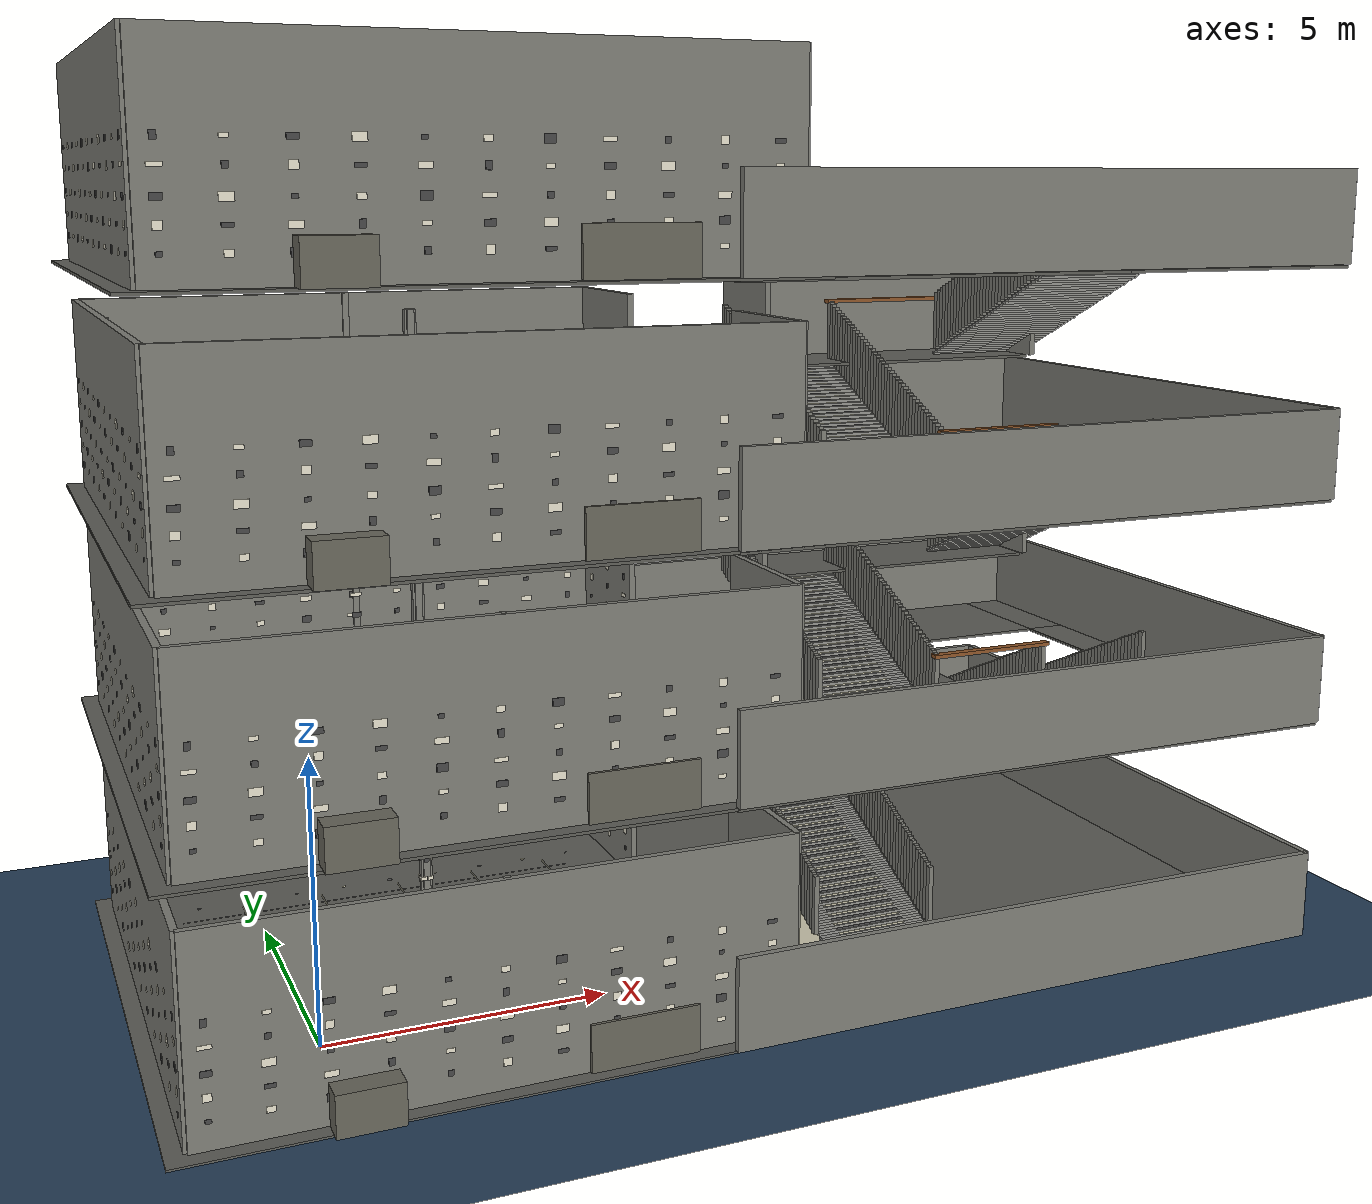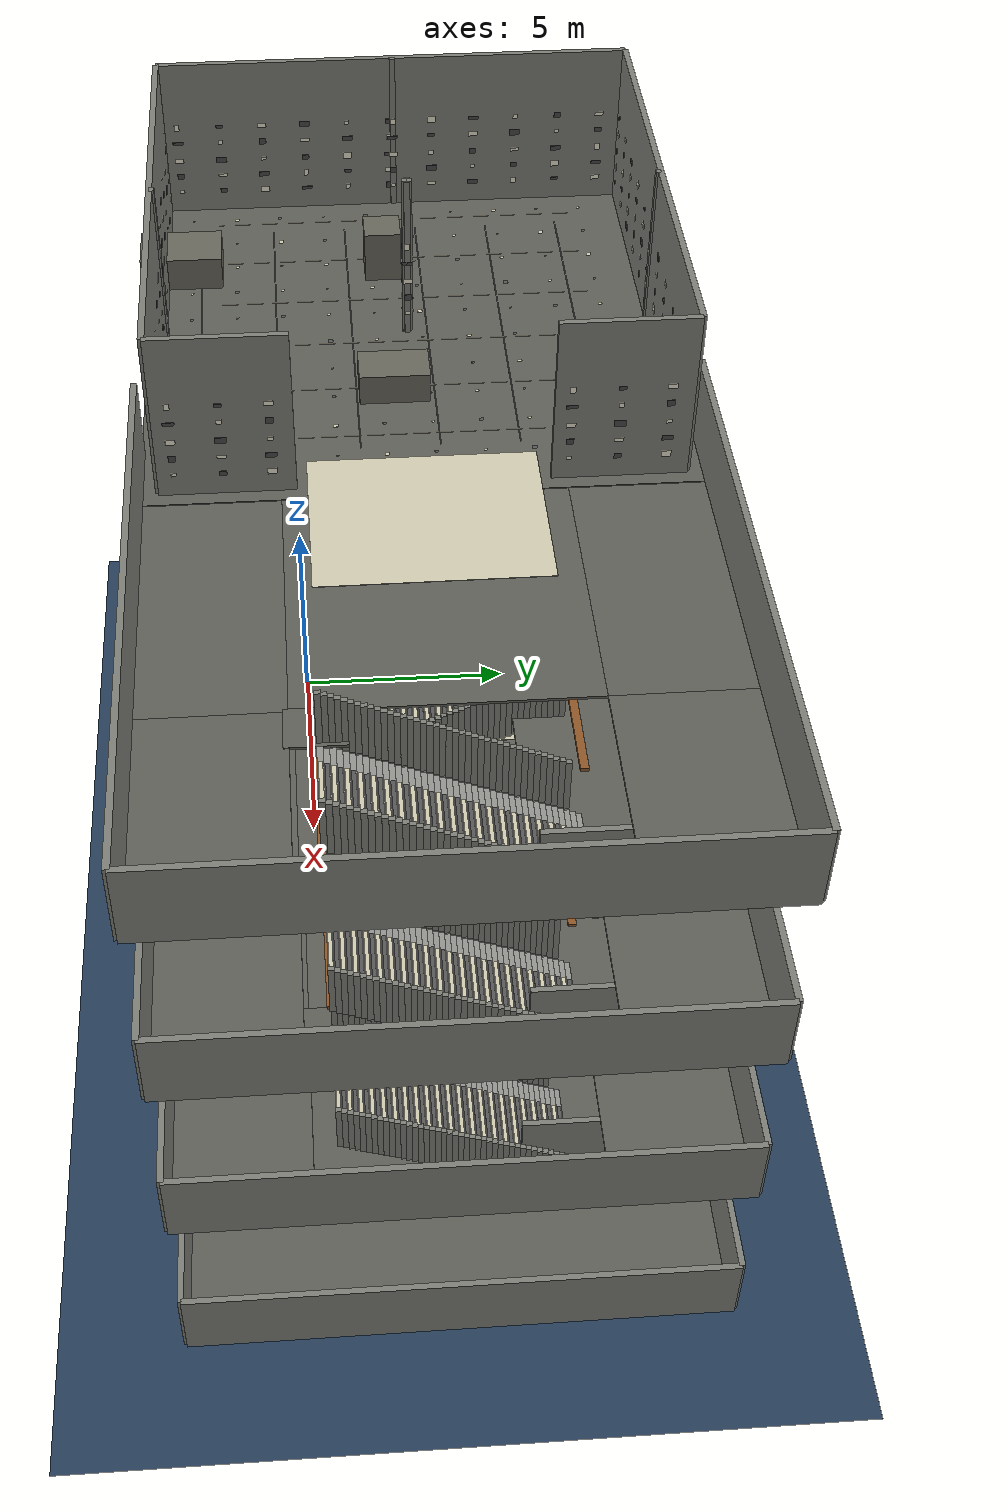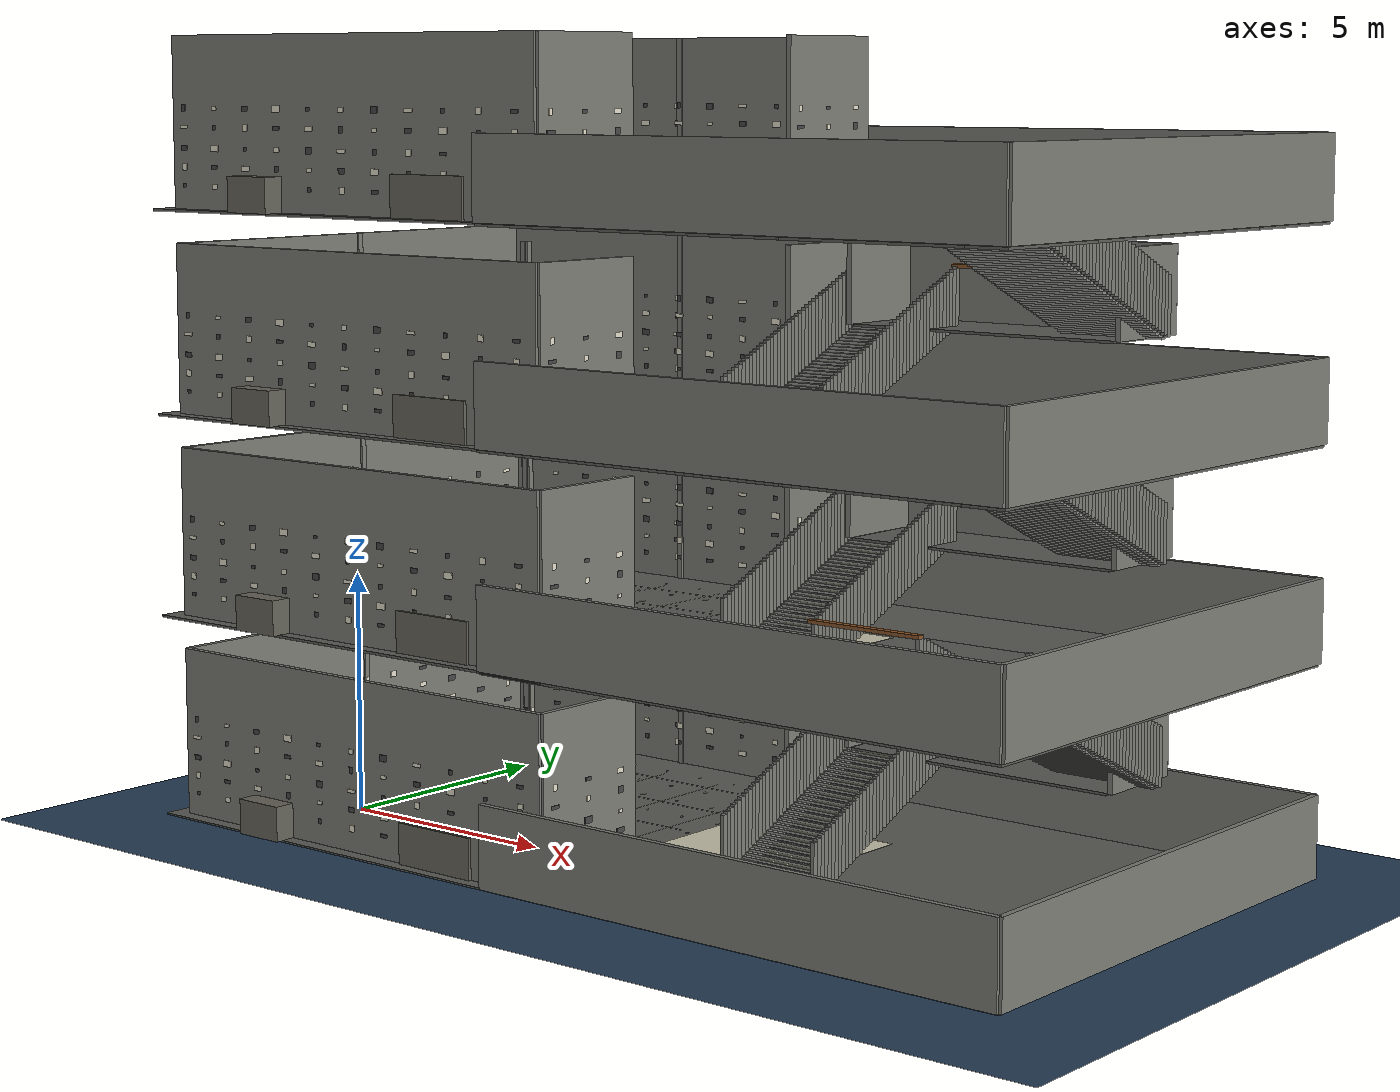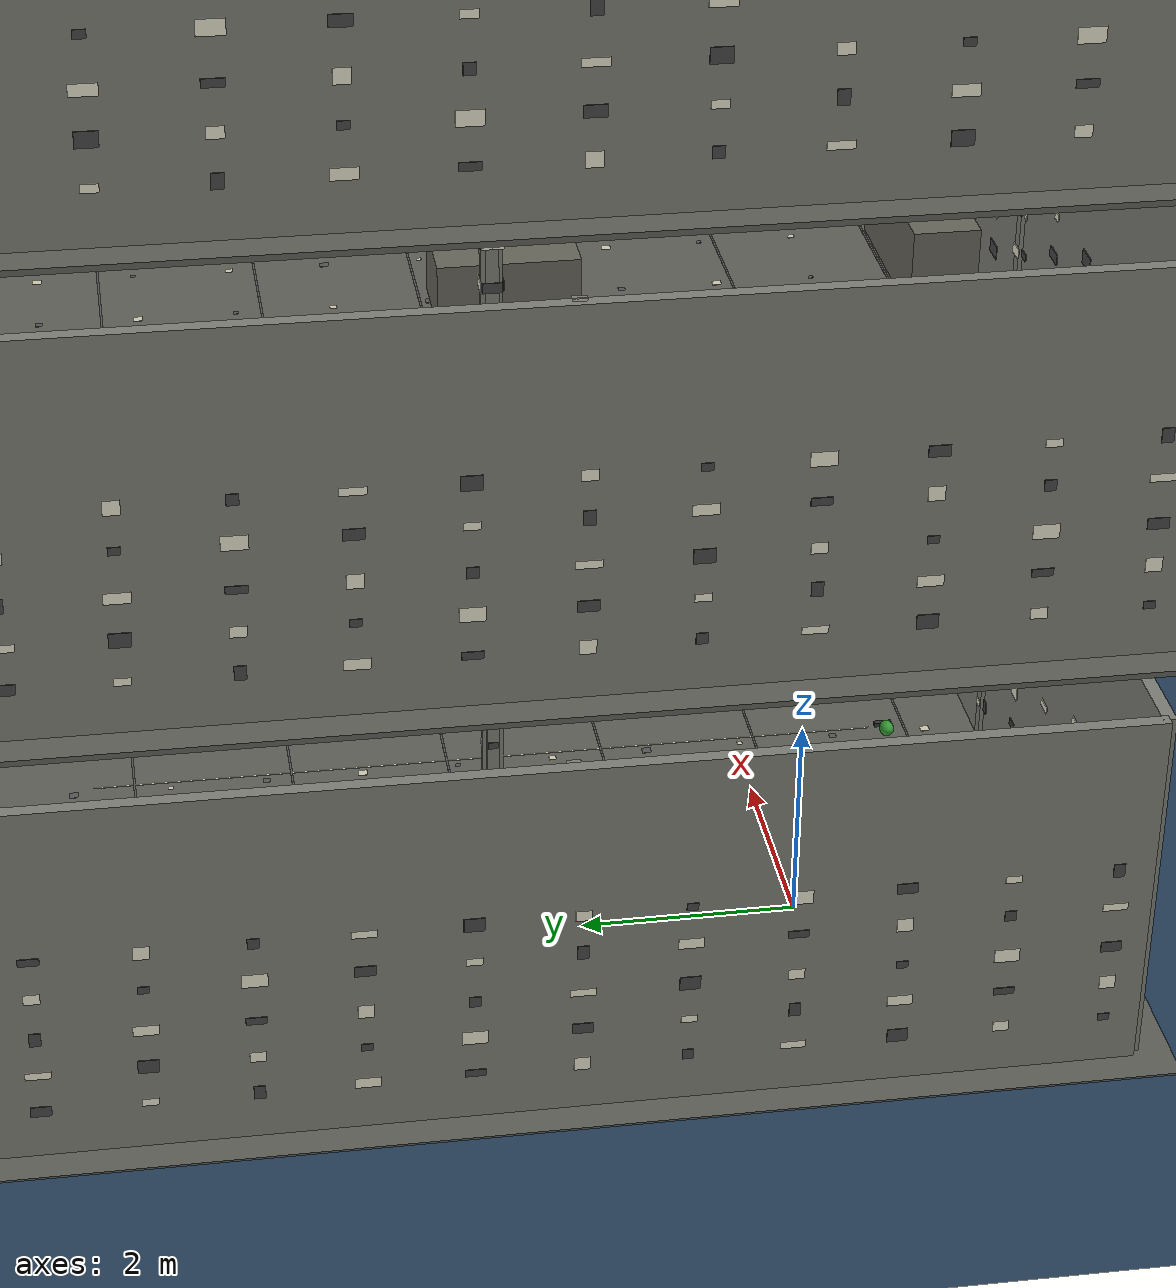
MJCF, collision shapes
<mujoco model="elf3">
  <include file="elf3.xml"/>
  <asset>
    <texture name="wall_feature_checker" type="2d" builtin="checker" rgb1="0.50 0.50 0.50" rgb2="0.88 0.88 0.84" width="256" height="256"/>
    <texture name="floor_feature_checker" type="2d" builtin="checker" rgb1="0.46 0.46 0.46" rgb2="0.74 0.74 0.70" width="256" height="256"/>
    <texture name="obstacle_feature_checker" type="2d" builtin="checker" rgb1="0.42 0.42 0.42" rgb2="0.82 0.80 0.74" width="192" height="192"/>
    <material name="room_floor" texture="floor_feature_checker" texuniform="true" texrepeat="18 18" rgba="0.62 0.62 0.60 1"/>
    <material name="room_wall" texture="wall_feature_checker" texuniform="true" texrepeat="18 10" rgba="0.72 0.72 0.70 1"/>
    <material name="room_obstacle" texture="obstacle_feature_checker" texuniform="true" texrepeat="6 6" rgba="0.66 0.66 0.62 1"/>
    <material name="stair_mat" rgba="0.58 0.58 0.56 1"/>
    <material name="wood_plank" rgba="0.56 0.34 0.16 1"/>
    <material name="spawn_marker" rgba="1.00 0.08 0.02 1"/>
    <material name="feature_dark" rgba="0.28 0.28 0.28 1"/>
    <material name="feature_light" rgba="0.92 0.90 0.82 1"/>
    <material name="feature_floor_dark" rgba="0.34 0.34 0.34 1"/>
    <material name="feature_floor_light" rgba="0.82 0.80 0.70 1"/>
  </asset>
  <worldbody>
    <geom name="lower_floor" type="box" pos="2.500 2.500 -0.018" size="5.350 5.350 0.025" material="room_floor"/>
    <geom name="lower_stair_hall_tile_00" type="box" pos="12.150 2.500 -0.038" size="5.900 5.350 0.025" material="room_floor"/>
    <geom name="lower_stair_doorway_marker" type="box" pos="8.550 2.500 0.020" size="1.800 2.208 0.004" material="feature_floor_light" contype="0" conaffinity="0"/>
    <geom name="middle_01_floor" type="box" pos="2.500 2.500 4.182" size="5.350 5.350 0.025" material="room_floor"/>
    <geom name="middle_01_stair_hall_tile_00" type="box" pos="9.825 -1.525 4.162" size="3.575 1.325 0.025" material="room_floor"/>
    <geom name="middle_01_stair_hall_tile_01" type="box" pos="9.825 2.500 4.162" size="3.575 2.700 0.025" material="room_floor"/>
    <geom name="middle_01_stair_hall_tile_02" type="box" pos="9.825 6.525 4.162" size="3.575 1.325 0.025" material="room_floor"/>
    <geom name="middle_01_stair_hall_tile_03" type="box" pos="15.300 -1.525 4.162" size="1.900 1.325 0.025" material="room_floor"/>
    <geom name="middle_01_stair_hall_tile_04" type="box" pos="15.300 6.525 4.162" size="1.900 1.325 0.025" material="room_floor"/>
    <geom name="middle_01_stair_hall_tile_05" type="box" pos="17.625 -1.525 4.162" size="0.425 1.325 0.025" material="room_floor"/>
    <geom name="middle_01_stair_hall_tile_06" type="box" pos="17.625 2.500 4.162" size="0.425 2.700 0.025" material="room_floor"/>
    <geom name="middle_01_stair_hall_tile_07" type="box" pos="17.625 6.525 4.162" size="0.425 1.325 0.025" material="room_floor"/>
    <geom name="middle_01_stair_top_bridge" type="box" pos="13.800 0.250 4.182" size="0.450 0.550 0.025" material="room_floor"/>
    <geom name="middle_01_stair_doorway_marker" type="box" pos="8.550 2.500 4.220" size="1.800 2.208 0.004" material="feature_floor_light" contype="0" conaffinity="0"/>
    <geom name="middle_02_floor" type="box" pos="2.500 2.500 8.382" size="5.350 5.350 0.025" material="room_floor"/>
    <geom name="middle_02_stair_hall_tile_00" type="box" pos="9.825 -1.525 8.362" size="3.575 1.325 0.025" material="room_floor"/>
    <geom name="middle_02_stair_hall_tile_01" type="box" pos="9.825 2.500 8.362" size="3.575 2.700 0.025" material="room_floor"/>
    <geom name="middle_02_stair_hall_tile_02" type="box" pos="9.825 6.525 8.362" size="3.575 1.325 0.025" material="room_floor"/>
    <geom name="middle_02_stair_hall_tile_03" type="box" pos="15.300 -1.525 8.362" size="1.900 1.325 0.025" material="room_floor"/>
    <geom name="middle_02_stair_hall_tile_04" type="box" pos="15.300 6.525 8.362" size="1.900 1.325 0.025" material="room_floor"/>
    <geom name="middle_02_stair_hall_tile_05" type="box" pos="17.625 -1.525 8.362" size="0.425 1.325 0.025" material="room_floor"/>
    <geom name="middle_02_stair_hall_tile_06" type="box" pos="17.625 2.500 8.362" size="0.425 2.700 0.025" material="room_floor"/>
    <geom name="middle_02_stair_hall_tile_07" type="box" pos="17.625 6.525 8.362" size="0.425 1.325 0.025" material="room_floor"/>
    <geom name="middle_02_stair_top_bridge" type="box" pos="13.800 0.250 8.382" size="0.450 0.550 0.025" material="room_floor"/>
    <geom name="middle_02_stair_doorway_marker" type="box" pos="8.550 2.500 8.420" size="1.800 2.208 0.004" material="feature_floor_light" contype="0" conaffinity="0"/>
    <geom name="top_floor" type="box" pos="2.500 2.500 12.582" size="5.350 5.350 0.025" material="room_floor"/>
    <geom name="top_stair_hall_tile_00" type="box" pos="9.825 -1.525 12.562" size="3.575 1.325 0.025" material="room_floor"/>
    <geom name="top_stair_hall_tile_01" type="box" pos="9.825 2.500 12.562" size="3.575 2.700 0.025" material="room_floor"/>
    <geom name="top_stair_hall_tile_02" type="box" pos="9.825 6.525 12.562" size="3.575 1.325 0.025" material="room_floor"/>
    <geom name="top_stair_hall_tile_03" type="box" pos="15.300 -1.525 12.562" size="1.900 1.325 0.025" material="room_floor"/>
    <geom name="top_stair_hall_tile_04" type="box" pos="15.300 6.525 12.562" size="1.900 1.325 0.025" material="room_floor"/>
    <geom name="top_stair_hall_tile_05" type="box" pos="17.625 -1.525 12.562" size="0.425 1.325 0.025" material="room_floor"/>
    <geom name="top_stair_hall_tile_06" type="box" pos="17.625 2.500 12.562" size="0.425 2.700 0.025" material="room_floor"/>
    <geom name="top_stair_hall_tile_07" type="box" pos="17.625 6.525 12.562" size="0.425 1.325 0.025" material="room_floor"/>
    <geom name="top_stair_top_bridge" type="box" pos="13.800 0.250 12.582" size="0.450 0.550 0.025" material="room_floor"/>
    <geom name="top_stair_doorway_marker" type="box" pos="8.550 2.500 12.620" size="1.800 2.208 0.004" material="feature_floor_light" contype="0" conaffinity="0"/>
    <geom name="lower_wall_north_0" type="box" pos="2.500 7.500 1.750" size="5.000 0.060 1.750" material="room_wall"/>
    <geom name="lower_wall_south_0" type="box" pos="2.500 -2.500 1.750" size="5.000 0.060 1.750" material="room_wall"/>
    <geom name="lower_wall_east_0" type="box" pos="7.500 -1.200 1.750" size="0.060 1.300 1.750" material="room_wall"/>
    <geom name="lower_wall_east_1" type="box" pos="7.500 6.200 1.750" size="0.060 1.300 1.750" material="room_wall"/>
    <geom name="lower_wall_west_0" type="box" pos="-2.500 2.500 1.750" size="0.060 5.000 1.750" material="room_wall"/>
    <geom name="lower_wall_v_1_0_0" type="box" pos="2.500 -2.450 1.750" size="0.060 0.050 1.750" material="room_wall"/>
    <geom name="lower_wall_v_1_0_1" type="box" pos="2.500 2.450 1.750" size="0.060 0.050 1.750" material="room_wall"/>
    <geom name="lower_wall_v_1_1_0" type="box" pos="2.500 2.550 1.750" size="0.060 0.050 1.750" material="room_wall"/>
    <geom name="lower_wall_v_1_1_1" type="box" pos="2.500 7.450 1.750" size="0.060 0.050 1.750" material="room_wall"/>
    <geom name="lower_wall_h_1_0_0" type="box" pos="-2.450 2.500 1.750" size="0.050 0.060 1.750" material="room_wall"/>
    <geom name="lower_wall_h_1_0_1" type="box" pos="2.450 2.500 1.750" size="0.050 0.060 1.750" material="room_wall"/>
    <geom name="lower_wall_h_1_1_0" type="box" pos="2.550 2.500 1.750" size="0.050 0.060 1.750" material="room_wall"/>
    <geom name="middle_01_wall_north_0" type="box" pos="2.500 7.500 5.950" size="5.000 0.060 1.750" material="room_wall"/>
    <geom name="middle_01_wall_south_0" type="box" pos="2.500 -2.500 5.950" size="5.000 0.060 1.750" material="room_wall"/>
    <geom name="middle_01_wall_east_0" type="box" pos="7.500 -1.200 5.950" size="0.060 1.300 1.750" material="room_wall"/>
    <geom name="middle_01_wall_east_1" type="box" pos="7.500 6.200 5.950" size="0.060 1.300 1.750" material="room_wall"/>
    <geom name="middle_01_wall_west_0" type="box" pos="-2.500 2.500 5.950" size="0.060 5.000 1.750" material="room_wall"/>
    <geom name="middle_01_wall_v_1_0_0" type="box" pos="2.500 -2.450 5.950" size="0.060 0.050 1.750" material="room_wall"/>
    <geom name="middle_01_wall_v_1_0_1" type="box" pos="2.500 2.450 5.950" size="0.060 0.050 1.750" material="room_wall"/>
    <geom name="middle_01_wall_v_1_1_0" type="box" pos="2.500 2.550 5.950" size="0.060 0.050 1.750" material="room_wall"/>
    <geom name="middle_01_wall_v_1_1_1" type="box" pos="2.500 7.450 5.950" size="0.060 0.050 1.750" material="room_wall"/>
    <geom name="middle_01_wall_h_1_0_0" type="box" pos="-2.450 2.500 5.950" size="0.050 0.060 1.750" material="room_wall"/>
    <geom name="middle_01_wall_h_1_0_1" type="box" pos="2.450 2.500 5.950" size="0.050 0.060 1.750" material="room_wall"/>
    <geom name="middle_01_wall_h_1_1_0" type="box" pos="2.550 2.500 5.950" size="0.050 0.060 1.750" material="room_wall"/>
    <geom name="middle_02_wall_north_0" type="box" pos="2.500 7.500 10.150" size="5.000 0.060 1.750" material="room_wall"/>
    <geom name="middle_02_wall_south_0" type="box" pos="2.500 -2.500 10.150" size="5.000 0.060 1.750" material="room_wall"/>
    <geom name="middle_02_wall_east_0" type="box" pos="7.500 -1.200 10.150" size="0.060 1.300 1.750" material="room_wall"/>
    <geom name="middle_02_wall_east_1" type="box" pos="7.500 6.200 10.150" size="0.060 1.300 1.750" material="room_wall"/>
    <geom name="middle_02_wall_west_0" type="box" pos="-2.500 2.500 10.150" size="0.060 5.000 1.750" material="room_wall"/>
    <geom name="middle_02_wall_v_1_0_0" type="box" pos="2.500 -2.450 10.150" size="0.060 0.050 1.750" material="room_wall"/>
    <geom name="middle_02_wall_v_1_0_1" type="box" pos="2.500 2.450 10.150" size="0.060 0.050 1.750" material="room_wall"/>
    <geom name="middle_02_wall_v_1_1_0" type="box" pos="2.500 2.550 10.150" size="0.060 0.050 1.750" material="room_wall"/>
    <geom name="middle_02_wall_v_1_1_1" type="box" pos="2.500 7.450 10.150" size="0.060 0.050 1.750" material="room_wall"/>
    <geom name="middle_02_wall_h_1_0_0" type="box" pos="-2.450 2.500 10.150" size="0.050 0.060 1.750" material="room_wall"/>
    <geom name="middle_02_wall_h_1_0_1" type="box" pos="2.450 2.500 10.150" size="0.050 0.060 1.750" material="room_wall"/>
    <geom name="middle_02_wall_h_1_1_0" type="box" pos="2.550 2.500 10.150" size="0.050 0.060 1.750" material="room_wall"/>
    <geom name="top_wall_north_0" type="box" pos="2.500 7.500 14.350" size="5.000 0.060 1.750" material="room_wall"/>
    <geom name="top_wall_south_0" type="box" pos="2.500 -2.500 14.350" size="5.000 0.060 1.750" material="room_wall"/>
    <geom name="top_wall_east_0" type="box" pos="7.500 -1.200 14.350" size="0.060 1.300 1.750" material="room_wall"/>
    <geom name="top_wall_east_1" type="box" pos="7.500 6.200 14.350" size="0.060 1.300 1.750" material="room_wall"/>
    <geom name="top_wall_west_0" type="box" pos="-2.500 2.500 14.350" size="0.060 5.000 1.750" material="room_wall"/>
    <geom name="top_wall_v_1_0_0" type="box" pos="2.500 -2.450 14.350" size="0.060 0.050 1.750" material="room_wall"/>
    <geom name="top_wall_v_1_0_1" type="box" pos="2.500 2.450 14.350" size="0.060 0.050 1.750" material="room_wall"/>
    <geom name="top_wall_v_1_1_0" type="box" pos="2.500 2.550 14.350" size="0.060 0.050 1.750" material="room_wall"/>
    <geom name="top_wall_v_1_1_1" type="box" pos="2.500 7.450 14.350" size="0.060 0.050 1.750" material="room_wall"/>
    <geom name="top_wall_h_1_0_0" type="box" pos="-2.450 2.500 14.350" size="0.050 0.060 1.750" material="room_wall"/>
    <geom name="top_wall_h_1_0_1" type="box" pos="2.450 2.500 14.350" size="0.050 0.060 1.750" material="room_wall"/>
    <geom name="top_wall_h_1_1_0" type="box" pos="2.550 2.500 14.350" size="0.050 0.060 1.750" material="room_wall"/>
    <geom name="lower_stair_hall_east_guard" type="box" pos="18.050 2.500 0.825" size="0.060 5.350 0.825" material="room_wall"/>
    <geom name="lower_stair_hall_north_guard" type="box" pos="12.150 7.850 0.825" size="5.900 0.060 0.825" material="room_wall"/>
    <geom name="lower_stair_hall_south_guard" type="box" pos="12.150 -2.850 0.825" size="5.900 0.060 0.825" material="room_wall"/>
    <geom name="middle_01_stair_hall_east_guard" type="box" pos="18.050 2.500 5.025" size="0.060 5.350 0.825" material="room_wall"/>
    <geom name="middle_01_stair_hall_north_guard" type="box" pos="12.150 7.850 5.025" size="5.900 0.060 0.825" material="room_wall"/>
    <geom name="middle_01_stair_hall_south_guard" type="box" pos="12.150 -2.850 5.025" size="5.900 0.060 0.825" material="room_wall"/>
    <geom name="middle_01_floor_inner_rail_board" type="box" pos="12.950 0.250 5.360" size="1.260 0.075 0.035" material="wood_plank" contype="0" conaffinity="0"/>
    <geom name="middle_02_stair_hall_east_guard" type="box" pos="18.050 2.500 9.225" size="0.060 5.350 0.825" material="room_wall"/>
    <geom name="middle_02_stair_hall_north_guard" type="box" pos="12.150 7.850 9.225" size="5.900 0.060 0.825" material="room_wall"/>
    <geom name="middle_02_stair_hall_south_guard" type="box" pos="12.150 -2.850 9.225" size="5.900 0.060 0.825" material="room_wall"/>
    <geom name="middle_02_floor_inner_rail_board" type="box" pos="12.950 0.250 9.560" size="1.260 0.075 0.035" material="wood_plank" contype="0" conaffinity="0"/>
    <geom name="top_stair_hall_east_guard" type="box" pos="18.050 2.500 13.425" size="0.060 5.350 0.825" material="room_wall"/>
    <geom name="top_stair_hall_north_guard" type="box" pos="12.150 7.850 13.425" size="5.900 0.060 0.825" material="room_wall"/>
    <geom name="top_stair_hall_south_guard" type="box" pos="12.150 -2.850 13.425" size="5.900 0.060 0.825" material="room_wall"/>
    <geom name="stair_00_01_mid_landing" type="box" pos="12.950 4.750 2.082" size="2.950 0.950 0.025" material="room_floor"/>
    <geom name="stair_00_01_mid_landing_north_guard" type="box" pos="12.950 5.770 2.950" size="3.050 0.055 0.850" material="room_wall"/>
    <geom name="stair_00_01_mid_landing_west_guard" type="box" pos="9.900 4.750 2.950" size="0.055 0.980 0.850" material="room_wall"/>
    <geom name="stair_00_01_mid_landing_east_guard" type="box" pos="16.000 4.750 2.950" size="0.055 0.980 0.850" material="room_wall"/>
    <geom name="stair_00_01_flight_a_step_00" type="box" pos="10.600 0.304 0.025" size="1.100 0.054 0.025" material="stair_mat"/>
    <geom name="feature_stair_00_01_flight_a_tread_00" type="box" pos="10.600 0.304 0.054" size="0.704 0.036 0.001" material="feature_floor_dark" contype="0" conaffinity="0"/>
    <geom name="stair_00_01_flight_a_step_01" type="box" pos="10.600 0.411 0.075" size="1.100 0.054 0.025" material="stair_mat"/>
    <geom name="feature_stair_00_01_flight_a_tread_01" type="box" pos="10.600 0.411 0.104" size="0.704 0.036 0.001" material="feature_floor_light" contype="0" conaffinity="0"/>
    <geom name="stair_00_01_flight_a_step_02" type="box" pos="10.600 0.518 0.125" size="1.100 0.054 0.025" material="stair_mat"/>
    <geom name="feature_stair_00_01_flight_a_tread_02" type="box" pos="10.600 0.518 0.154" size="0.704 0.036 0.001" material="feature_floor_dark" contype="0" conaffinity="0"/>
    <geom name="stair_00_01_flight_a_step_03" type="box" pos="10.600 0.625 0.175" size="1.100 0.054 0.025" material="stair_mat"/>
    <geom name="feature_stair_00_01_flight_a_tread_03" type="box" pos="10.600 0.625 0.204" size="0.704 0.036 0.001" material="feature_floor_light" contype="0" conaffinity="0"/>
    <geom name="stair_00_01_flight_a_step_04" type="box" pos="10.600 0.732 0.225" size="1.100 0.054 0.025" material="stair_mat"/>
    <geom name="feature_stair_00_01_flight_a_tread_04" type="box" pos="10.600 0.732 0.254" size="0.704 0.036 0.001" material="feature_floor_dark" contype="0" conaffinity="0"/>
    <geom name="stair_00_01_flight_a_step_05" type="box" pos="10.600 0.839 0.275" size="1.100 0.054 0.025" material="stair_mat"/>
    <geom name="feature_stair_00_01_flight_a_tread_05" type="box" pos="10.600 0.839 0.304" size="0.704 0.036 0.001" material="feature_floor_light" contype="0" conaffinity="0"/>
    <geom name="stair_00_01_flight_a_step_06" type="box" pos="10.600 0.946 0.325" size="1.100 0.054 0.025" material="stair_mat"/>
    <geom name="feature_stair_00_01_flight_a_tread_06" type="box" pos="10.600 0.946 0.354" size="0.704 0.036 0.001" material="feature_floor_dark" contype="0" conaffinity="0"/>
    <geom name="stair_00_01_flight_a_step_07" type="box" pos="10.600 1.054 0.375" size="1.100 0.054 0.025" material="stair_mat"/>
    <geom name="feature_stair_00_01_flight_a_tread_07" type="box" pos="10.600 1.054 0.404" size="0.704 0.036 0.001" material="feature_floor_light" contype="0" conaffinity="0"/>
    <geom name="stair_00_01_flight_a_step_08" type="box" pos="10.600 1.161 0.425" size="1.100 0.054 0.025" material="stair_mat"/>
    <geom name="feature_stair_00_01_flight_a_tread_08" type="box" pos="10.600 1.161 0.454" size="0.704 0.036 0.001" material="feature_floor_dark" contype="0" conaffinity="0"/>
    <geom name="stair_00_01_flight_a_step_09" type="box" pos="10.600 1.268 0.475" size="1.100 0.054 0.025" material="stair_mat"/>
    <geom name="feature_stair_00_01_flight_a_tread_09" type="box" pos="10.600 1.268 0.504" size="0.704 0.036 0.001" material="feature_floor_light" contype="0" conaffinity="0"/>
    <geom name="stair_00_01_flight_a_step_10" type="box" pos="10.600 1.375 0.525" size="1.100 0.054 0.025" material="stair_mat"/>
    <geom name="feature_stair_00_01_flight_a_tread_10" type="box" pos="10.600 1.375 0.554" size="0.704 0.036 0.001" material="feature_floor_dark" contype="0" conaffinity="0"/>
    <geom name="stair_00_01_flight_a_step_11" type="box" pos="10.600 1.482 0.575" size="1.100 0.054 0.025" material="stair_mat"/>
    <geom name="feature_stair_00_01_flight_a_tread_11" type="box" pos="10.600 1.482 0.604" size="0.704 0.036 0.001" material="feature_floor_light" contype="0" conaffinity="0"/>
    <geom name="stair_00_01_flight_a_step_12" type="box" pos="10.600 1.589 0.625" size="1.100 0.054 0.025" material="stair_mat"/>
    <geom name="feature_stair_00_01_flight_a_tread_12" type="box" pos="10.600 1.589 0.654" size="0.704 0.036 0.001" material="feature_floor_dark" contype="0" conaffinity="0"/>
    <geom name="stair_00_01_flight_a_step_13" type="box" pos="10.600 1.696 0.675" size="1.100 0.054 0.025" material="stair_mat"/>
    <geom name="feature_stair_00_01_flight_a_tread_13" type="box" pos="10.600 1.696 0.704" size="0.704 0.036 0.001" material="feature_floor_light" contype="0" conaffinity="0"/>
    <geom name="stair_00_01_flight_a_step_14" type="box" pos="10.600 1.804 0.725" size="1.100 0.054 0.025" material="stair_mat"/>
    <geom name="feature_stair_00_01_flight_a_tread_14" type="box" pos="10.600 1.804 0.754" size="0.704 0.036 0.001" material="feature_floor_dark" contype="0" conaffinity="0"/>
    <geom name="stair_00_01_flight_a_step_15" type="box" pos="10.600 1.911 0.775" size="1.100 0.054 0.025" material="stair_mat"/>
    <geom name="feature_stair_00_01_flight_a_tread_15" type="box" pos="10.600 1.911 0.804" size="0.704 0.036 0.001" material="feature_floor_light" contype="0" conaffinity="0"/>
    <geom name="stair_00_01_flight_a_step_16" type="box" pos="10.600 2.018 0.825" size="1.100 0.054 0.025" material="stair_mat"/>
    <geom name="feature_stair_00_01_flight_a_tread_16" type="box" pos="10.600 2.018 0.854" size="0.704 0.036 0.001" material="feature_floor_dark" contype="0" conaffinity="0"/>
    <geom name="stair_00_01_flight_a_step_17" type="box" pos="10.600 2.125 0.875" size="1.100 0.054 0.025" material="stair_mat"/>
    <geom name="feature_stair_00_01_flight_a_tread_17" type="box" pos="10.600 2.125 0.904" size="0.704 0.036 0.001" material="feature_floor_light" contype="0" conaffinity="0"/>
    <geom name="stair_00_01_flight_a_step_18" type="box" pos="10.600 2.232 0.925" size="1.100 0.054 0.025" material="stair_mat"/>
    <geom name="feature_stair_00_01_flight_a_tread_18" type="box" pos="10.600 2.232 0.954" size="0.704 0.036 0.001" material="feature_floor_dark" contype="0" conaffinity="0"/>
    <geom name="stair_00_01_flight_a_step_19" type="box" pos="10.600 2.339 0.975" size="1.100 0.054 0.025" material="stair_mat"/>
    <geom name="feature_stair_00_01_flight_a_tread_19" type="box" pos="10.600 2.339 1.004" size="0.704 0.036 0.001" material="feature_floor_light" contype="0" conaffinity="0"/>
    <geom name="stair_00_01_flight_a_step_20" type="box" pos="10.600 2.446 1.025" size="1.100 0.054 0.025" material="stair_mat"/>
    <geom name="feature_stair_00_01_flight_a_tread_20" type="box" pos="10.600 2.446 1.054" size="0.704 0.036 0.001" material="feature_floor_dark" contype="0" conaffinity="0"/>
    <geom name="stair_00_01_flight_a_step_21" type="box" pos="10.600 2.554 1.075" size="1.100 0.054 0.025" material="stair_mat"/>
    <geom name="feature_stair_00_01_flight_a_tread_21" type="box" pos="10.600 2.554 1.104" size="0.704 0.036 0.001" material="feature_floor_light" contype="0" conaffinity="0"/>
    <geom name="stair_00_01_flight_a_step_22" type="box" pos="10.600 2.661 1.125" size="1.100 0.054 0.025" material="stair_mat"/>
    <geom name="feature_stair_00_01_flight_a_tread_22" type="box" pos="10.600 2.661 1.154" size="0.704 0.036 0.001" material="feature_floor_dark" contype="0" conaffinity="0"/>
    <geom name="stair_00_01_flight_a_step_23" type="box" pos="10.600 2.768 1.175" size="1.100 0.054 0.025" material="stair_mat"/>
    <geom name="feature_stair_00_01_flight_a_tread_23" type="box" pos="10.600 2.768 1.204" size="0.704 0.036 0.001" material="feature_floor_light" contype="0" conaffinity="0"/>
    <geom name="stair_00_01_flight_a_step_24" type="box" pos="10.600 2.875 1.225" size="1.100 0.054 0.025" material="stair_mat"/>
    <geom name="feature_stair_00_01_flight_a_tread_24" type="box" pos="10.600 2.875 1.254" size="0.704 0.036 0.001" material="feature_floor_dark" contype="0" conaffinity="0"/>
    <geom name="stair_00_01_flight_a_step_25" type="box" pos="10.600 2.982 1.275" size="1.100 0.054 0.025" material="stair_mat"/>
    <geom name="feature_stair_00_01_flight_a_tread_25" type="box" pos="10.600 2.982 1.304" size="0.704 0.036 0.001" material="feature_floor_light" contype="0" conaffinity="0"/>
    <geom name="stair_00_01_flight_a_step_26" type="box" pos="10.600 3.089 1.325" size="1.100 0.054 0.025" material="stair_mat"/>
    <geom name="feature_stair_00_01_flight_a_tread_26" type="box" pos="10.600 3.089 1.354" size="0.704 0.036 0.001" material="feature_floor_dark" contype="0" conaffinity="0"/>
    <geom name="stair_00_01_flight_a_step_27" type="box" pos="10.600 3.196 1.375" size="1.100 0.054 0.025" material="stair_mat"/>
    <geom name="feature_stair_00_01_flight_a_tread_27" type="box" pos="10.600 3.196 1.404" size="0.704 0.036 0.001" material="feature_floor_light" contype="0" conaffinity="0"/>
    <geom name="stair_00_01_flight_a_step_28" type="box" pos="10.600 3.304 1.425" size="1.100 0.054 0.025" material="stair_mat"/>
    <geom name="feature_stair_00_01_flight_a_tread_28" type="box" pos="10.600 3.304 1.454" size="0.704 0.036 0.001" material="feature_floor_dark" contype="0" conaffinity="0"/>
    <geom name="stair_00_01_flight_a_step_29" type="box" pos="10.600 3.411 1.475" size="1.100 0.054 0.025" material="stair_mat"/>
    <geom name="feature_stair_00_01_flight_a_tread_29" type="box" pos="10.600 3.411 1.504" size="0.704 0.036 0.001" material="feature_floor_light" contype="0" conaffinity="0"/>
    <geom name="stair_00_01_flight_a_step_30" type="box" pos="10.600 3.518 1.525" size="1.100 0.054 0.025" material="stair_mat"/>
    <geom name="feature_stair_00_01_flight_a_tread_30" type="box" pos="10.600 3.518 1.554" size="0.704 0.036 0.001" material="feature_floor_dark" contype="0" conaffinity="0"/>
    <geom name="stair_00_01_flight_a_step_31" type="box" pos="10.600 3.625 1.575" size="1.100 0.054 0.025" material="stair_mat"/>
    <geom name="feature_stair_00_01_flight_a_tread_31" type="box" pos="10.600 3.625 1.604" size="0.704 0.036 0.001" material="feature_floor_light" contype="0" conaffinity="0"/>
    <geom name="stair_00_01_flight_a_step_32" type="box" pos="10.600 3.732 1.625" size="1.100 0.054 0.025" material="stair_mat"/>
    <geom name="feature_stair_00_01_flight_a_tread_32" type="box" pos="10.600 3.732 1.654" size="0.704 0.036 0.001" material="feature_floor_dark" contype="0" conaffinity="0"/>
    <geom name="stair_00_01_flight_a_step_33" type="box" pos="10.600 3.839 1.675" size="1.100 0.054 0.025" material="stair_mat"/>
    <geom name="feature_stair_00_01_flight_a_tread_33" type="box" pos="10.600 3.839 1.704" size="0.704 0.036 0.001" material="feature_floor_light" contype="0" conaffinity="0"/>
    <geom name="stair_00_01_flight_a_step_34" type="box" pos="10.600 3.946 1.725" size="1.100 0.054 0.025" material="stair_mat"/>
    <geom name="feature_stair_00_01_flight_a_tread_34" type="box" pos="10.600 3.946 1.754" size="0.704 0.036 0.001" material="feature_floor_dark" contype="0" conaffinity="0"/>
    <geom name="stair_00_01_flight_a_step_35" type="box" pos="10.600 4.054 1.775" size="1.100 0.054 0.025" material="stair_mat"/>
    <geom name="feature_stair_00_01_flight_a_tread_35" type="box" pos="10.600 4.054 1.804" size="0.704 0.036 0.001" material="feature_floor_light" contype="0" conaffinity="0"/>
    <geom name="stair_00_01_flight_a_step_36" type="box" pos="10.600 4.161 1.825" size="1.100 0.054 0.025" material="stair_mat"/>
    <geom name="feature_stair_00_01_flight_a_tread_36" type="box" pos="10.600 4.161 1.854" size="0.704 0.036 0.001" material="feature_floor_dark" contype="0" conaffinity="0"/>
    <geom name="stair_00_01_flight_a_step_37" type="box" pos="10.600 4.268 1.875" size="1.100 0.054 0.025" material="stair_mat"/>
    <geom name="feature_stair_00_01_flight_a_tread_37" type="box" pos="10.600 4.268 1.904" size="0.704 0.036 0.001" material="feature_floor_light" contype="0" conaffinity="0"/>
    <geom name="stair_00_01_flight_a_step_38" type="box" pos="10.600 4.375 1.925" size="1.100 0.054 0.025" material="stair_mat"/>
    <geom name="feature_stair_00_01_flight_a_tread_38" type="box" pos="10.600 4.375 1.954" size="0.704 0.036 0.001" material="feature_floor_dark" contype="0" conaffinity="0"/>
    <geom name="stair_00_01_flight_a_step_39" type="box" pos="10.600 4.482 1.975" size="1.100 0.054 0.025" material="stair_mat"/>
    <geom name="feature_stair_00_01_flight_a_tread_39" type="box" pos="10.600 4.482 2.004" size="0.704 0.036 0.001" material="feature_floor_light" contype="0" conaffinity="0"/>
    <geom name="stair_00_01_flight_a_step_40" type="box" pos="10.600 4.589 2.025" size="1.100 0.054 0.025" material="stair_mat"/>
    <geom name="feature_stair_00_01_flight_a_tread_40" type="box" pos="10.600 4.589 2.054" size="0.704 0.036 0.001" material="feature_floor_dark" contype="0" conaffinity="0"/>
    <geom name="stair_00_01_flight_a_step_41" type="box" pos="10.600 4.696 2.075" size="1.100 0.054 0.025" material="stair_mat"/>
    <geom name="feature_stair_00_01_flight_a_tread_41" type="box" pos="10.600 4.696 2.104" size="0.704 0.036 0.001" material="feature_floor_light" contype="0" conaffinity="0"/>
    <geom name="stair_00_01_flight_a_left_side_wall_00" type="box" pos="11.770 0.304 0.625" size="0.045 0.054 0.575" material="room_wall"/>
    <geom name="stair_00_01_flight_a_left_side_wall_01" type="box" pos="11.770 0.411 0.675" size="0.045 0.054 0.575" material="room_wall"/>
    <geom name="stair_00_01_flight_a_left_side_wall_02" type="box" pos="11.770 0.518 0.725" size="0.045 0.054 0.575" material="room_wall"/>
    <geom name="stair_00_01_flight_a_right_side_wall_02" type="box" pos="9.430 0.518 0.725" size="0.045 0.054 0.575" material="room_wall"/>
    <geom name="stair_00_01_flight_a_left_side_wall_03" type="box" pos="11.770 0.625 0.775" size="0.045 0.054 0.575" material="room_wall"/>
    <geom name="stair_00_01_flight_a_right_side_wall_03" type="box" pos="9.430 0.625 0.775" size="0.045 0.054 0.575" material="room_wall"/>
    <geom name="stair_00_01_flight_a_left_side_wall_04" type="box" pos="11.770 0.732 0.825" size="0.045 0.054 0.575" material="room_wall"/>
    <geom name="stair_00_01_flight_a_right_side_wall_04" type="box" pos="9.430 0.732 0.825" size="0.045 0.054 0.575" material="room_wall"/>
    <geom name="stair_00_01_flight_a_left_side_wall_05" type="box" pos="11.770 0.839 0.875" size="0.045 0.054 0.575" material="room_wall"/>
    <geom name="stair_00_01_flight_a_right_side_wall_05" type="box" pos="9.430 0.839 0.875" size="0.045 0.054 0.575" material="room_wall"/>
    <geom name="stair_00_01_flight_a_left_side_wall_06" type="box" pos="11.770 0.946 0.925" size="0.045 0.054 0.575" material="room_wall"/>
    <geom name="stair_00_01_flight_a_right_side_wall_06" type="box" pos="9.430 0.946 0.925" size="0.045 0.054 0.575" material="room_wall"/>
    <geom name="stair_00_01_flight_a_left_side_wall_07" type="box" pos="11.770 1.054 0.975" size="0.045 0.054 0.575" material="room_wall"/>
    <geom name="stair_00_01_flight_a_right_side_wall_07" type="box" pos="9.430 1.054 0.975" size="0.045 0.054 0.575" material="room_wall"/>
    <geom name="stair_00_01_flight_a_left_side_wall_08" type="box" pos="11.770 1.161 1.025" size="0.045 0.054 0.575" material="room_wall"/>
    <geom name="stair_00_01_flight_a_right_side_wall_08" type="box" pos="9.430 1.161 1.025" size="0.045 0.054 0.575" material="room_wall"/>
    <geom name="stair_00_01_flight_a_left_side_wall_09" type="box" pos="11.770 1.268 1.075" size="0.045 0.054 0.575" material="room_wall"/>
    <geom name="stair_00_01_flight_a_right_side_wall_09" type="box" pos="9.430 1.268 1.075" size="0.045 0.054 0.575" material="room_wall"/>
    <geom name="stair_00_01_flight_a_left_side_wall_10" type="box" pos="11.770 1.375 1.125" size="0.045 0.054 0.575" material="room_wall"/>
    <geom name="stair_00_01_flight_a_right_side_wall_10" type="box" pos="9.430 1.375 1.125" size="0.045 0.054 0.575" material="room_wall"/>
    <geom name="stair_00_01_flight_a_left_side_wall_11" type="box" pos="11.770 1.482 1.175" size="0.045 0.054 0.575" material="room_wall"/>
    <geom name="stair_00_01_flight_a_right_side_wall_11" type="box" pos="9.430 1.482 1.175" size="0.045 0.054 0.575" material="room_wall"/>
    <geom name="stair_00_01_flight_a_left_side_wall_12" type="box" pos="11.770 1.589 1.225" size="0.045 0.054 0.575" material="room_wall"/>
    <geom name="stair_00_01_flight_a_right_side_wall_12" type="box" pos="9.430 1.589 1.225" size="0.045 0.054 0.575" material="room_wall"/>
    <geom name="stair_00_01_flight_a_left_side_wall_13" type="box" pos="11.770 1.696 1.275" size="0.045 0.054 0.575" material="room_wall"/>
    <geom name="stair_00_01_flight_a_right_side_wall_13" type="box" pos="9.430 1.696 1.275" size="0.045 0.054 0.575" material="room_wall"/>
    <geom name="stair_00_01_flight_a_left_side_wall_14" type="box" pos="11.770 1.804 1.325" size="0.045 0.054 0.575" material="room_wall"/>
    <geom name="stair_00_01_flight_a_right_side_wall_14" type="box" pos="9.430 1.804 1.325" size="0.045 0.054 0.575" material="room_wall"/>
    <geom name="stair_00_01_flight_a_left_side_wall_15" type="box" pos="11.770 1.911 1.375" size="0.045 0.054 0.575" material="room_wall"/>
    <geom name="stair_00_01_flight_a_right_side_wall_15" type="box" pos="9.430 1.911 1.375" size="0.045 0.054 0.575" material="room_wall"/>
    <geom name="stair_00_01_flight_a_left_side_wall_16" type="box" pos="11.770 2.018 1.425" size="0.045 0.054 0.575" material="room_wall"/>
    <geom name="stair_00_01_flight_a_right_side_wall_16" type="box" pos="9.430 2.018 1.425" size="0.045 0.054 0.575" material="room_wall"/>
    <geom name="stair_00_01_flight_a_left_side_wall_17" type="box" pos="11.770 2.125 1.475" size="0.045 0.054 0.575" material="room_wall"/>
    <geom name="stair_00_01_flight_a_right_side_wall_17" type="box" pos="9.430 2.125 1.475" size="0.045 0.054 0.575" material="room_wall"/>
    <geom name="stair_00_01_flight_a_left_side_wall_18" type="box" pos="11.770 2.232 1.525" size="0.045 0.054 0.575" material="room_wall"/>
    <geom name="stair_00_01_flight_a_right_side_wall_18" type="box" pos="9.430 2.232 1.525" size="0.045 0.054 0.575" material="room_wall"/>
    <geom name="stair_00_01_flight_a_left_side_wall_19" type="box" pos="11.770 2.339 1.575" size="0.045 0.054 0.575" material="room_wall"/>
    <geom name="stair_00_01_flight_a_right_side_wall_19" type="box" pos="9.430 2.339 1.575" size="0.045 0.054 0.575" material="room_wall"/>
    <geom name="stair_00_01_flight_a_left_side_wall_20" type="box" pos="11.770 2.446 1.625" size="0.045 0.054 0.575" material="room_wall"/>
    <geom name="stair_00_01_flight_a_right_side_wall_20" type="box" pos="9.430 2.446 1.625" size="0.045 0.054 0.575" material="room_wall"/>
    <geom name="stair_00_01_flight_a_left_side_wall_21" type="box" pos="11.770 2.554 1.675" size="0.045 0.054 0.575" material="room_wall"/>
    <geom name="stair_00_01_flight_a_right_side_wall_21" type="box" pos="9.430 2.554 1.675" size="0.045 0.054 0.575" material="room_wall"/>
    <geom name="stair_00_01_flight_a_left_side_wall_22" type="box" pos="11.770 2.661 1.725" size="0.045 0.054 0.575" material="room_wall"/>
    <geom name="stair_00_01_flight_a_right_side_wall_22" type="box" pos="9.430 2.661 1.725" size="0.045 0.054 0.575" material="room_wall"/>
    <geom name="stair_00_01_flight_a_left_side_wall_23" type="box" pos="11.770 2.768 1.775" size="0.045 0.054 0.575" material="room_wall"/>
    <geom name="stair_00_01_flight_a_right_side_wall_23" type="box" pos="9.430 2.768 1.775" size="0.045 0.054 0.575" material="room_wall"/>
    <geom name="stair_00_01_flight_a_left_side_wall_24" type="box" pos="11.770 2.875 1.825" size="0.045 0.054 0.575" material="room_wall"/>
    <geom name="stair_00_01_flight_a_right_side_wall_24" type="box" pos="9.430 2.875 1.825" size="0.045 0.054 0.575" material="room_wall"/>
    <geom name="stair_00_01_flight_a_left_side_wall_25" type="box" pos="11.770 2.982 1.875" size="0.045 0.054 0.575" material="room_wall"/>
    <geom name="stair_00_01_flight_a_right_side_wall_25" type="box" pos="9.430 2.982 1.875" size="0.045 0.054 0.575" material="room_wall"/>
    <geom name="stair_00_01_flight_a_left_side_wall_26" type="box" pos="11.770 3.089 1.925" size="0.045 0.054 0.575" material="room_wall"/>
    <geom name="stair_00_01_flight_a_right_side_wall_26" type="box" pos="9.430 3.089 1.925" size="0.045 0.054 0.575" material="room_wall"/>
    <geom name="stair_00_01_flight_a_left_side_wall_27" type="box" pos="11.770 3.196 1.975" size="0.045 0.054 0.575" material="room_wall"/>
    <geom name="stair_00_01_flight_a_right_side_wall_27" type="box" pos="9.430 3.196 1.975" size="0.045 0.054 0.575" material="room_wall"/>
    <geom name="stair_00_01_flight_a_left_side_wall_28" type="box" pos="11.770 3.304 2.025" size="0.045 0.054 0.575" material="room_wall"/>
    <geom name="stair_00_01_flight_a_right_side_wall_28" type="box" pos="9.430 3.304 2.025" size="0.045 0.054 0.575" material="room_wall"/>
    <geom name="stair_00_01_flight_a_left_side_wall_29" type="box" pos="11.770 3.411 2.075" size="0.045 0.054 0.575" material="room_wall"/>
    <geom name="stair_00_01_flight_a_right_side_wall_29" type="box" pos="9.430 3.411 2.075" size="0.045 0.054 0.575" material="room_wall"/>
    <geom name="stair_00_01_flight_a_left_side_wall_30" type="box" pos="11.770 3.518 2.125" size="0.045 0.054 0.575" material="room_wall"/>
    <geom name="stair_00_01_flight_a_right_side_wall_30" type="box" pos="9.430 3.518 2.125" size="0.045 0.054 0.575" material="room_wall"/>
    <geom name="stair_00_01_flight_a_left_side_wall_31" type="box" pos="11.770 3.625 2.175" size="0.045 0.054 0.575" material="room_wall"/>
    <geom name="stair_00_01_flight_a_right_side_wall_31" type="box" pos="9.430 3.625 2.175" size="0.045 0.054 0.575" material="room_wall"/>
    <geom name="stair_00_01_flight_a_left_side_wall_32" type="box" pos="11.770 3.732 2.225" size="0.045 0.054 0.575" material="room_wall"/>
    <geom name="stair_00_01_flight_a_right_side_wall_32" type="box" pos="9.430 3.732 2.225" size="0.045 0.054 0.575" material="room_wall"/>
    <geom name="stair_00_01_flight_a_left_side_wall_33" type="box" pos="11.770 3.839 2.275" size="0.045 0.054 0.575" material="room_wall"/>
    <geom name="stair_00_01_flight_a_right_side_wall_33" type="box" pos="9.430 3.839 2.275" size="0.045 0.054 0.575" material="room_wall"/>
    <geom name="stair_00_01_flight_a_left_side_wall_34" type="box" pos="11.770 3.946 2.325" size="0.045 0.054 0.575" material="room_wall"/>
    <geom name="stair_00_01_flight_a_right_side_wall_34" type="box" pos="9.430 3.946 2.325" size="0.045 0.054 0.575" material="room_wall"/>
    <geom name="stair_00_01_flight_a_left_side_wall_35" type="box" pos="11.770 4.054 2.375" size="0.045 0.054 0.575" material="room_wall"/>
    <geom name="stair_00_01_flight_a_right_side_wall_35" type="box" pos="9.430 4.054 2.375" size="0.045 0.054 0.575" material="room_wall"/>
    <geom name="stair_00_01_flight_a_left_side_wall_36" type="box" pos="11.770 4.161 2.425" size="0.045 0.054 0.575" material="room_wall"/>
    <geom name="stair_00_01_flight_a_right_side_wall_36" type="box" pos="9.430 4.161 2.425" size="0.045 0.054 0.575" material="room_wall"/>
    <geom name="stair_00_01_flight_a_left_side_wall_37" type="box" pos="11.770 4.268 2.475" size="0.045 0.054 0.575" material="room_wall"/>
    <geom name="stair_00_01_flight_a_right_side_wall_37" type="box" pos="9.430 4.268 2.475" size="0.045 0.054 0.575" material="room_wall"/>
    <geom name="stair_00_01_flight_a_left_side_wall_38" type="box" pos="11.770 4.375 2.525" size="0.045 0.054 0.575" material="room_wall"/>
    <geom name="stair_00_01_flight_a_right_side_wall_38" type="box" pos="9.430 4.375 2.525" size="0.045 0.054 0.575" material="room_wall"/>
    <geom name="stair_00_01_flight_a_left_side_wall_39" type="box" pos="11.770 4.482 2.575" size="0.045 0.054 0.575" material="room_wall"/>
    <geom name="stair_00_01_flight_a_right_side_wall_39" type="box" pos="9.430 4.482 2.575" size="0.045 0.054 0.575" material="room_wall"/>
    <geom name="stair_00_01_flight_a_left_side_wall_40" type="box" pos="11.770 4.589 2.625" size="0.045 0.054 0.575" material="room_wall"/>
    <geom name="stair_00_01_flight_a_right_side_wall_40" type="box" pos="9.430 4.589 2.625" size="0.045 0.054 0.575" material="room_wall"/>
    <geom name="stair_00_01_flight_a_left_side_wall_41" type="box" pos="11.770 4.696 2.675" size="0.045 0.054 0.575" material="room_wall"/>
    <geom name="stair_00_01_flight_a_right_side_wall_41" type="box" pos="9.430 4.696 2.675" size="0.045 0.054 0.575" material="room_wall"/>
    <geom name="stair_00_01_flight_b_step_00" type="box" pos="15.300 4.696 2.125" size="1.100 0.054 0.025" material="stair_mat"/>
    <geom name="feature_stair_00_01_flight_b_tread_00" type="box" pos="15.300 4.696 2.154" size="0.704 0.036 0.001" material="feature_floor_dark" contype="0" conaffinity="0"/>
    <geom name="stair_00_01_flight_b_step_01" type="box" pos="15.300 4.589 2.175" size="1.100 0.054 0.025" material="stair_mat"/>
    <geom name="feature_stair_00_01_flight_b_tread_01" type="box" pos="15.300 4.589 2.204" size="0.704 0.036 0.001" material="feature_floor_light" contype="0" conaffinity="0"/>
    <geom name="stair_00_01_flight_b_step_02" type="box" pos="15.300 4.482 2.225" size="1.100 0.054 0.025" material="stair_mat"/>
    <geom name="feature_stair_00_01_flight_b_tread_02" type="box" pos="15.300 4.482 2.254" size="0.704 0.036 0.001" material="feature_floor_dark" contype="0" conaffinity="0"/>
    <geom name="stair_00_01_flight_b_step_03" type="box" pos="15.300 4.375 2.275" size="1.100 0.054 0.025" material="stair_mat"/>
    <geom name="feature_stair_00_01_flight_b_tread_03" type="box" pos="15.300 4.375 2.304" size="0.704 0.036 0.001" material="feature_floor_light" contype="0" conaffinity="0"/>
    <geom name="stair_00_01_flight_b_step_04" type="box" pos="15.300 4.268 2.325" size="1.100 0.054 0.025" material="stair_mat"/>
    <geom name="feature_stair_00_01_flight_b_tread_04" type="box" pos="15.300 4.268 2.354" size="0.704 0.036 0.001" material="feature_floor_dark" contype="0" conaffinity="0"/>
    <geom name="stair_00_01_flight_b_step_05" type="box" pos="15.300 4.161 2.375" size="1.100 0.054 0.025" material="stair_mat"/>
    <geom name="feature_stair_00_01_flight_b_tread_05" type="box" pos="15.300 4.161 2.404" size="0.704 0.036 0.001" material="feature_floor_light" contype="0" conaffinity="0"/>
    <geom name="stair_00_01_flight_b_step_06" type="box" pos="15.300 4.054 2.425" size="1.100 0.054 0.025" material="stair_mat"/>
    <geom name="feature_stair_00_01_flight_b_tread_06" type="box" pos="15.300 4.054 2.454" size="0.704 0.036 0.001" material="feature_floor_dark" contype="0" conaffinity="0"/>
    <geom name="stair_00_01_flight_b_step_07" type="box" pos="15.300 3.946 2.475" size="1.100 0.054 0.025" material="stair_mat"/>
    <geom name="feature_stair_00_01_flight_b_tread_07" type="box" pos="15.300 3.946 2.504" size="0.704 0.036 0.001" material="feature_floor_light" contype="0" conaffinity="0"/>
    <geom name="stair_00_01_flight_b_step_08" type="box" pos="15.300 3.839 2.525" size="1.100 0.054 0.025" material="stair_mat"/>
    <geom name="feature_stair_00_01_flight_b_tread_08" type="box" pos="15.300 3.839 2.554" size="0.704 0.036 0.001" material="feature_floor_dark" contype="0" conaffinity="0"/>
    <geom name="stair_00_01_flight_b_step_09" type="box" pos="15.300 3.732 2.575" size="1.100 0.054 0.025" material="stair_mat"/>
    <geom name="feature_stair_00_01_flight_b_tread_09" type="box" pos="15.300 3.732 2.604" size="0.704 0.036 0.001" material="feature_floor_light" contype="0" conaffinity="0"/>
    <geom name="stair_00_01_flight_b_step_10" type="box" pos="15.300 3.625 2.625" size="1.100 0.054 0.025" material="stair_mat"/>
    <geom name="feature_stair_00_01_flight_b_tread_10" type="box" pos="15.300 3.625 2.654" size="0.704 0.036 0.001" material="feature_floor_dark" contype="0" conaffinity="0"/>
    <geom name="stair_00_01_flight_b_step_11" type="box" pos="15.300 3.518 2.675" size="1.100 0.054 0.025" material="stair_mat"/>
    <geom name="feature_stair_00_01_flight_b_tread_11" type="box" pos="15.300 3.518 2.704" size="0.704 0.036 0.001" material="feature_floor_light" contype="0" conaffinity="0"/>
    <geom name="stair_00_01_flight_b_step_12" type="box" pos="15.300 3.411 2.725" size="1.100 0.054 0.025" material="stair_mat"/>
    <geom name="feature_stair_00_01_flight_b_tread_12" type="box" pos="15.300 3.411 2.754" size="0.704 0.036 0.001" material="feature_floor_dark" contype="0" conaffinity="0"/>
    <geom name="stair_00_01_flight_b_step_13" type="box" pos="15.300 3.304 2.775" size="1.100 0.054 0.025" material="stair_mat"/>
    <geom name="feature_stair_00_01_flight_b_tread_13" type="box" pos="15.300 3.304 2.804" size="0.704 0.036 0.001" material="feature_floor_light" contype="0" conaffinity="0"/>
    <geom name="stair_00_01_flight_b_step_14" type="box" pos="15.300 3.196 2.825" size="1.100 0.054 0.025" material="stair_mat"/>
    <geom name="feature_stair_00_01_flight_b_tread_14" type="box" pos="15.300 3.196 2.854" size="0.704 0.036 0.001" material="feature_floor_dark" contype="0" conaffinity="0"/>
    <geom name="stair_00_01_flight_b_step_15" type="box" pos="15.300 3.089 2.875" size="1.100 0.054 0.025" material="stair_mat"/>
    <geom name="feature_stair_00_01_flight_b_tread_15" type="box" pos="15.300 3.089 2.904" size="0.704 0.036 0.001" material="feature_floor_light" contype="0" conaffinity="0"/>
    <geom name="stair_00_01_flight_b_step_16" type="box" pos="15.300 2.982 2.925" size="1.100 0.054 0.025" material="stair_mat"/>
    <geom name="feature_stair_00_01_flight_b_tread_16" type="box" pos="15.300 2.982 2.954" size="0.704 0.036 0.001" material="feature_floor_dark" contype="0" conaffinity="0"/>
    <geom name="stair_00_01_flight_b_step_17" type="box" pos="15.300 2.875 2.975" size="1.100 0.054 0.025" material="stair_mat"/>
    <geom name="feature_stair_00_01_flight_b_tread_17" type="box" pos="15.300 2.875 3.004" size="0.704 0.036 0.001" material="feature_floor_light" contype="0" conaffinity="0"/>
    <geom name="stair_00_01_flight_b_step_18" type="box" pos="15.300 2.768 3.025" size="1.100 0.054 0.025" material="stair_mat"/>
    <geom name="feature_stair_00_01_flight_b_tread_18" type="box" pos="15.300 2.768 3.054" size="0.704 0.036 0.001" material="feature_floor_dark" contype="0" conaffinity="0"/>
    <geom name="stair_00_01_flight_b_step_19" type="box" pos="15.300 2.661 3.075" size="1.100 0.054 0.025" material="stair_mat"/>
    <geom name="feature_stair_00_01_flight_b_tread_19" type="box" pos="15.300 2.661 3.104" size="0.704 0.036 0.001" material="feature_floor_light" contype="0" conaffinity="0"/>
    <geom name="stair_00_01_flight_b_step_20" type="box" pos="15.300 2.554 3.125" size="1.100 0.054 0.025" material="stair_mat"/>
    <geom name="feature_stair_00_01_flight_b_tread_20" type="box" pos="15.300 2.554 3.154" size="0.704 0.036 0.001" material="feature_floor_dark" contype="0" conaffinity="0"/>
    <geom name="stair_00_01_flight_b_step_21" type="box" pos="15.300 2.446 3.175" size="1.100 0.054 0.025" material="stair_mat"/>
    <geom name="feature_stair_00_01_flight_b_tread_21" type="box" pos="15.300 2.446 3.204" size="0.704 0.036 0.001" material="feature_floor_light" contype="0" conaffinity="0"/>
    <geom name="stair_00_01_flight_b_step_22" type="box" pos="15.300 2.339 3.225" size="1.100 0.054 0.025" material="stair_mat"/>
    <geom name="feature_stair_00_01_flight_b_tread_22" type="box" pos="15.300 2.339 3.254" size="0.704 0.036 0.001" material="feature_floor_dark" contype="0" conaffinity="0"/>
    <geom name="stair_00_01_flight_b_step_23" type="box" pos="15.300 2.232 3.275" size="1.100 0.054 0.025" material="stair_mat"/>
    <geom name="feature_stair_00_01_flight_b_tread_23" type="box" pos="15.300 2.232 3.304" size="0.704 0.036 0.001" material="feature_floor_light" contype="0" conaffinity="0"/>
    <geom name="stair_00_01_flight_b_step_24" type="box" pos="15.300 2.125 3.325" size="1.100 0.054 0.025" material="stair_mat"/>
    <geom name="feature_stair_00_01_flight_b_tread_24" type="box" pos="15.300 2.125 3.354" size="0.704 0.036 0.001" material="feature_floor_dark" contype="0" conaffinity="0"/>
    <geom name="stair_00_01_flight_b_step_25" type="box" pos="15.300 2.018 3.375" size="1.100 0.054 0.025" material="stair_mat"/>
    <geom name="feature_stair_00_01_flight_b_tread_25" type="box" pos="15.300 2.018 3.404" size="0.704 0.036 0.001" material="feature_floor_light" contype="0" conaffinity="0"/>
    <geom name="stair_00_01_flight_b_step_26" type="box" pos="15.300 1.911 3.425" size="1.100 0.054 0.025" material="stair_mat"/>
    <geom name="feature_stair_00_01_flight_b_tread_26" type="box" pos="15.300 1.911 3.454" size="0.704 0.036 0.001" material="feature_floor_dark" contype="0" conaffinity="0"/>
    <geom name="stair_00_01_flight_b_step_27" type="box" pos="15.300 1.804 3.475" size="1.100 0.054 0.025" material="stair_mat"/>
    <geom name="feature_stair_00_01_flight_b_tread_27" type="box" pos="15.300 1.804 3.504" size="0.704 0.036 0.001" material="feature_floor_light" contype="0" conaffinity="0"/>
    <geom name="stair_00_01_flight_b_step_28" type="box" pos="15.300 1.696 3.525" size="1.100 0.054 0.025" material="stair_mat"/>
    <geom name="feature_stair_00_01_flight_b_tread_28" type="box" pos="15.300 1.696 3.554" size="0.704 0.036 0.001" material="feature_floor_dark" contype="0" conaffinity="0"/>
    <geom name="stair_00_01_flight_b_step_29" type="box" pos="15.300 1.589 3.575" size="1.100 0.054 0.025" material="stair_mat"/>
    <geom name="feature_stair_00_01_flight_b_tread_29" type="box" pos="15.300 1.589 3.604" size="0.704 0.036 0.001" material="feature_floor_light" contype="0" conaffinity="0"/>
    <geom name="stair_00_01_flight_b_step_30" type="box" pos="15.300 1.482 3.625" size="1.100 0.054 0.025" material="stair_mat"/>
    <geom name="feature_stair_00_01_flight_b_tread_30" type="box" pos="15.300 1.482 3.654" size="0.704 0.036 0.001" material="feature_floor_dark" contype="0" conaffinity="0"/>
    <geom name="stair_00_01_flight_b_step_31" type="box" pos="15.300 1.375 3.675" size="1.100 0.054 0.025" material="stair_mat"/>
    <geom name="feature_stair_00_01_flight_b_tread_31" type="box" pos="15.300 1.375 3.704" size="0.704 0.036 0.001" material="feature_floor_light" contype="0" conaffinity="0"/>
    <geom name="stair_00_01_flight_b_step_32" type="box" pos="15.300 1.268 3.725" size="1.100 0.054 0.025" material="stair_mat"/>
    <geom name="feature_stair_00_01_flight_b_tread_32" type="box" pos="15.300 1.268 3.754" size="0.704 0.036 0.001" material="feature_floor_dark" contype="0" conaffinity="0"/>
    <geom name="stair_00_01_flight_b_step_33" type="box" pos="15.300 1.161 3.775" size="1.100 0.054 0.025" material="stair_mat"/>
    <geom name="feature_stair_00_01_flight_b_tread_33" type="box" pos="15.300 1.161 3.804" size="0.704 0.036 0.001" material="feature_floor_light" contype="0" conaffinity="0"/>
    <geom name="stair_00_01_flight_b_step_34" type="box" pos="15.300 1.054 3.825" size="1.100 0.054 0.025" material="stair_mat"/>
    <geom name="feature_stair_00_01_flight_b_tread_34" type="box" pos="15.300 1.054 3.854" size="0.704 0.036 0.001" material="feature_floor_dark" contype="0" conaffinity="0"/>
    <geom name="stair_00_01_flight_b_step_35" type="box" pos="15.300 0.946 3.875" size="1.100 0.054 0.025" material="stair_mat"/>
    <geom name="feature_stair_00_01_flight_b_tread_35" type="box" pos="15.300 0.946 3.904" size="0.704 0.036 0.001" material="feature_floor_light" contype="0" conaffinity="0"/>
    <geom name="stair_00_01_flight_b_step_36" type="box" pos="15.300 0.839 3.925" size="1.100 0.054 0.025" material="stair_mat"/>
    <geom name="feature_stair_00_01_flight_b_tread_36" type="box" pos="15.300 0.839 3.954" size="0.704 0.036 0.001" material="feature_floor_dark" contype="0" conaffinity="0"/>
    <geom name="stair_00_01_flight_b_step_37" type="box" pos="15.300 0.732 3.975" size="1.100 0.054 0.025" material="stair_mat"/>
    <geom name="feature_stair_00_01_flight_b_tread_37" type="box" pos="15.300 0.732 4.004" size="0.704 0.036 0.001" material="feature_floor_light" contype="0" conaffinity="0"/>
    <geom name="stair_00_01_flight_b_step_38" type="box" pos="15.300 0.625 4.025" size="1.100 0.054 0.025" material="stair_mat"/>
    <geom name="feature_stair_00_01_flight_b_tread_38" type="box" pos="15.300 0.625 4.054" size="0.704 0.036 0.001" material="feature_floor_dark" contype="0" conaffinity="0"/>
    <geom name="stair_00_01_flight_b_step_39" type="box" pos="15.300 0.518 4.075" size="1.100 0.054 0.025" material="stair_mat"/>
    <geom name="feature_stair_00_01_flight_b_tread_39" type="box" pos="15.300 0.518 4.104" size="0.704 0.036 0.001" material="feature_floor_light" contype="0" conaffinity="0"/>
    <geom name="stair_00_01_flight_b_step_40" type="box" pos="15.300 0.411 4.125" size="1.100 0.054 0.025" material="stair_mat"/>
    <geom name="feature_stair_00_01_flight_b_tread_40" type="box" pos="15.300 0.411 4.154" size="0.704 0.036 0.001" material="feature_floor_dark" contype="0" conaffinity="0"/>
    <geom name="stair_00_01_flight_b_step_41" type="box" pos="15.300 0.304 4.175" size="1.100 0.054 0.025" material="stair_mat"/>
    <geom name="feature_stair_00_01_flight_b_tread_41" type="box" pos="15.300 0.304 4.204" size="0.704 0.036 0.001" material="feature_floor_light" contype="0" conaffinity="0"/>
    <geom name="stair_00_01_flight_b_left_side_wall_00" type="box" pos="16.470 4.696 2.725" size="0.045 0.054 0.575" material="room_wall"/>
    <geom name="stair_00_01_flight_b_left_side_wall_01" type="box" pos="16.470 4.589 2.775" size="0.045 0.054 0.575" material="room_wall"/>
    <geom name="stair_00_01_flight_b_left_side_wall_02" type="box" pos="16.470 4.482 2.825" size="0.045 0.054 0.575" material="room_wall"/>
    <geom name="stair_00_01_flight_b_right_side_wall_02" type="box" pos="14.130 4.482 2.825" size="0.045 0.054 0.575" material="room_wall"/>
    <geom name="stair_00_01_flight_b_left_side_wall_03" type="box" pos="16.470 4.375 2.875" size="0.045 0.054 0.575" material="room_wall"/>
    <geom name="stair_00_01_flight_b_right_side_wall_03" type="box" pos="14.130 4.375 2.875" size="0.045 0.054 0.575" material="room_wall"/>
    <geom name="stair_00_01_flight_b_left_side_wall_04" type="box" pos="16.470 4.268 2.925" size="0.045 0.054 0.575" material="room_wall"/>
    <geom name="stair_00_01_flight_b_right_side_wall_04" type="box" pos="14.130 4.268 2.925" size="0.045 0.054 0.575" material="room_wall"/>
    <geom name="stair_00_01_flight_b_left_side_wall_05" type="box" pos="16.470 4.161 2.975" size="0.045 0.054 0.575" material="room_wall"/>
    <geom name="stair_00_01_flight_b_right_side_wall_05" type="box" pos="14.130 4.161 2.975" size="0.045 0.054 0.575" material="room_wall"/>
    <geom name="stair_00_01_flight_b_left_side_wall_06" type="box" pos="16.470 4.054 3.025" size="0.045 0.054 0.575" material="room_wall"/>
    <geom name="stair_00_01_flight_b_right_side_wall_06" type="box" pos="14.130 4.054 3.025" size="0.045 0.054 0.575" material="room_wall"/>
    <geom name="stair_00_01_flight_b_left_side_wall_07" type="box" pos="16.470 3.946 3.075" size="0.045 0.054 0.575" material="room_wall"/>
    <geom name="stair_00_01_flight_b_right_side_wall_07" type="box" pos="14.130 3.946 3.075" size="0.045 0.054 0.575" material="room_wall"/>
    <geom name="stair_00_01_flight_b_left_side_wall_08" type="box" pos="16.470 3.839 3.125" size="0.045 0.054 0.575" material="room_wall"/>
    <geom name="stair_00_01_flight_b_right_side_wall_08" type="box" pos="14.130 3.839 3.125" size="0.045 0.054 0.575" material="room_wall"/>
    <geom name="stair_00_01_flight_b_left_side_wall_09" type="box" pos="16.470 3.732 3.175" size="0.045 0.054 0.575" material="room_wall"/>
    <geom name="stair_00_01_flight_b_right_side_wall_09" type="box" pos="14.130 3.732 3.175" size="0.045 0.054 0.575" material="room_wall"/>
    <geom name="stair_00_01_flight_b_left_side_wall_10" type="box" pos="16.470 3.625 3.225" size="0.045 0.054 0.575" material="room_wall"/>
    <geom name="stair_00_01_flight_b_right_side_wall_10" type="box" pos="14.130 3.625 3.225" size="0.045 0.054 0.575" material="room_wall"/>
    <geom name="stair_00_01_flight_b_left_side_wall_11" type="box" pos="16.470 3.518 3.275" size="0.045 0.054 0.575" material="room_wall"/>
    <geom name="stair_00_01_flight_b_right_side_wall_11" type="box" pos="14.130 3.518 3.275" size="0.045 0.054 0.575" material="room_wall"/>
    <geom name="stair_00_01_flight_b_left_side_wall_12" type="box" pos="16.470 3.411 3.325" size="0.045 0.054 0.575" material="room_wall"/>
    <geom name="stair_00_01_flight_b_right_side_wall_12" type="box" pos="14.130 3.411 3.325" size="0.045 0.054 0.575" material="room_wall"/>
    <geom name="stair_00_01_flight_b_left_side_wall_13" type="box" pos="16.470 3.304 3.375" size="0.045 0.054 0.575" material="room_wall"/>
    <geom name="stair_00_01_flight_b_right_side_wall_13" type="box" pos="14.130 3.304 3.375" size="0.045 0.054 0.575" material="room_wall"/>
    <geom name="stair_00_01_flight_b_left_side_wall_14" type="box" pos="16.470 3.196 3.425" size="0.045 0.054 0.575" material="room_wall"/>
    <geom name="stair_00_01_flight_b_right_side_wall_14" type="box" pos="14.130 3.196 3.425" size="0.045 0.054 0.575" material="room_wall"/>
    <geom name="stair_00_01_flight_b_left_side_wall_15" type="box" pos="16.470 3.089 3.475" size="0.045 0.054 0.575" material="room_wall"/>
    <geom name="stair_00_01_flight_b_right_side_wall_15" type="box" pos="14.130 3.089 3.475" size="0.045 0.054 0.575" material="room_wall"/>
    <geom name="stair_00_01_flight_b_left_side_wall_16" type="box" pos="16.470 2.982 3.525" size="0.045 0.054 0.575" material="room_wall"/>
    <geom name="stair_00_01_flight_b_right_side_wall_16" type="box" pos="14.130 2.982 3.525" size="0.045 0.054 0.575" material="room_wall"/>
    <geom name="stair_00_01_flight_b_left_side_wall_17" type="box" pos="16.470 2.875 3.575" size="0.045 0.054 0.575" material="room_wall"/>
    <geom name="stair_00_01_flight_b_right_side_wall_17" type="box" pos="14.130 2.875 3.575" size="0.045 0.054 0.575" material="room_wall"/>
    <geom name="stair_00_01_flight_b_left_side_wall_18" type="box" pos="16.470 2.768 3.625" size="0.045 0.054 0.575" material="room_wall"/>
    <geom name="stair_00_01_flight_b_right_side_wall_18" type="box" pos="14.130 2.768 3.625" size="0.045 0.054 0.575" material="room_wall"/>
    <geom name="stair_00_01_flight_b_left_side_wall_19" type="box" pos="16.470 2.661 3.675" size="0.045 0.054 0.575" material="room_wall"/>
    <geom name="stair_00_01_flight_b_right_side_wall_19" type="box" pos="14.130 2.661 3.675" size="0.045 0.054 0.575" material="room_wall"/>
    <geom name="stair_00_01_flight_b_left_side_wall_20" type="box" pos="16.470 2.554 3.725" size="0.045 0.054 0.575" material="room_wall"/>
    <geom name="stair_00_01_flight_b_right_side_wall_20" type="box" pos="14.130 2.554 3.725" size="0.045 0.054 0.575" material="room_wall"/>
    <geom name="stair_00_01_flight_b_left_side_wall_21" type="box" pos="16.470 2.446 3.775" size="0.045 0.054 0.575" material="room_wall"/>
    <geom name="stair_00_01_flight_b_right_side_wall_21" type="box" pos="14.130 2.446 3.775" size="0.045 0.054 0.575" material="room_wall"/>
    <geom name="stair_00_01_flight_b_left_side_wall_22" type="box" pos="16.470 2.339 3.825" size="0.045 0.054 0.575" material="room_wall"/>
    <geom name="stair_00_01_flight_b_right_side_wall_22" type="box" pos="14.130 2.339 3.825" size="0.045 0.054 0.575" material="room_wall"/>
    <geom name="stair_00_01_flight_b_left_side_wall_23" type="box" pos="16.470 2.232 3.875" size="0.045 0.054 0.575" material="room_wall"/>
    <geom name="stair_00_01_flight_b_right_side_wall_23" type="box" pos="14.130 2.232 3.875" size="0.045 0.054 0.575" material="room_wall"/>
    <geom name="stair_00_01_flight_b_left_side_wall_24" type="box" pos="16.470 2.125 3.925" size="0.045 0.054 0.575" material="room_wall"/>
    <geom name="stair_00_01_flight_b_right_side_wall_24" type="box" pos="14.130 2.125 3.925" size="0.045 0.054 0.575" material="room_wall"/>
    <geom name="stair_00_01_flight_b_left_side_wall_25" type="box" pos="16.470 2.018 3.975" size="0.045 0.054 0.575" material="room_wall"/>
    <geom name="stair_00_01_flight_b_right_side_wall_25" type="box" pos="14.130 2.018 3.975" size="0.045 0.054 0.575" material="room_wall"/>
    <geom name="stair_00_01_flight_b_left_side_wall_26" type="box" pos="16.470 1.911 4.025" size="0.045 0.054 0.575" material="room_wall"/>
    <geom name="stair_00_01_flight_b_right_side_wall_26" type="box" pos="14.130 1.911 4.025" size="0.045 0.054 0.575" material="room_wall"/>
    <geom name="stair_00_01_flight_b_left_side_wall_27" type="box" pos="16.470 1.804 4.075" size="0.045 0.054 0.575" material="room_wall"/>
    <geom name="stair_00_01_flight_b_right_side_wall_27" type="box" pos="14.130 1.804 4.075" size="0.045 0.054 0.575" material="room_wall"/>
    <geom name="stair_00_01_flight_b_left_side_wall_28" type="box" pos="16.470 1.696 4.125" size="0.045 0.054 0.575" material="room_wall"/>
    <geom name="stair_00_01_flight_b_right_side_wall_28" type="box" pos="14.130 1.696 4.125" size="0.045 0.054 0.575" material="room_wall"/>
    <geom name="stair_00_01_flight_b_left_side_wall_29" type="box" pos="16.470 1.589 4.175" size="0.045 0.054 0.575" material="room_wall"/>
    <geom name="stair_00_01_flight_b_right_side_wall_29" type="box" pos="14.130 1.589 4.175" size="0.045 0.054 0.575" material="room_wall"/>
    <geom name="stair_00_01_flight_b_left_side_wall_30" type="box" pos="16.470 1.482 4.225" size="0.045 0.054 0.575" material="room_wall"/>
    <geom name="stair_00_01_flight_b_right_side_wall_30" type="box" pos="14.130 1.482 4.225" size="0.045 0.054 0.575" material="room_wall"/>
    <geom name="stair_00_01_flight_b_left_side_wall_31" type="box" pos="16.470 1.375 4.275" size="0.045 0.054 0.575" material="room_wall"/>
    <geom name="stair_00_01_flight_b_right_side_wall_31" type="box" pos="14.130 1.375 4.275" size="0.045 0.054 0.575" material="room_wall"/>
    <geom name="stair_00_01_flight_b_left_side_wall_32" type="box" pos="16.470 1.268 4.325" size="0.045 0.054 0.575" material="room_wall"/>
    <geom name="stair_00_01_flight_b_right_side_wall_32" type="box" pos="14.130 1.268 4.325" size="0.045 0.054 0.575" material="room_wall"/>
    <geom name="stair_00_01_flight_b_left_side_wall_33" type="box" pos="16.470 1.161 4.375" size="0.045 0.054 0.575" material="room_wall"/>
    <geom name="stair_00_01_flight_b_right_side_wall_33" type="box" pos="14.130 1.161 4.375" size="0.045 0.054 0.575" material="room_wall"/>
    <geom name="stair_00_01_flight_b_left_side_wall_34" type="box" pos="16.470 1.054 4.425" size="0.045 0.054 0.575" material="room_wall"/>
    <geom name="stair_00_01_flight_b_right_side_wall_34" type="box" pos="14.130 1.054 4.425" size="0.045 0.054 0.575" material="room_wall"/>
    <geom name="stair_00_01_flight_b_left_side_wall_35" type="box" pos="16.470 0.946 4.475" size="0.045 0.054 0.575" material="room_wall"/>
    <geom name="stair_00_01_flight_b_right_side_wall_35" type="box" pos="14.130 0.946 4.475" size="0.045 0.054 0.575" material="room_wall"/>
    <geom name="stair_00_01_flight_b_left_side_wall_36" type="box" pos="16.470 0.839 4.525" size="0.045 0.054 0.575" material="room_wall"/>
    <geom name="stair_00_01_flight_b_right_side_wall_36" type="box" pos="14.130 0.839 4.525" size="0.045 0.054 0.575" material="room_wall"/>
    <geom name="stair_00_01_flight_b_left_side_wall_37" type="box" pos="16.470 0.732 4.575" size="0.045 0.054 0.575" material="room_wall"/>
    <geom name="stair_00_01_flight_b_right_side_wall_37" type="box" pos="14.130 0.732 4.575" size="0.045 0.054 0.575" material="room_wall"/>
    <geom name="stair_00_01_flight_b_left_side_wall_38" type="box" pos="16.470 0.625 4.625" size="0.045 0.054 0.575" material="room_wall"/>
    <geom name="stair_00_01_flight_b_right_side_wall_38" type="box" pos="14.130 0.625 4.625" size="0.045 0.054 0.575" material="room_wall"/>
    <geom name="stair_00_01_flight_b_left_side_wall_39" type="box" pos="16.470 0.518 4.675" size="0.045 0.054 0.575" material="room_wall"/>
    <geom name="stair_00_01_flight_b_right_side_wall_39" type="box" pos="14.130 0.518 4.675" size="0.045 0.054 0.575" material="room_wall"/>
    <geom name="stair_00_01_flight_b_left_side_wall_40" type="box" pos="16.470 0.411 4.725" size="0.045 0.054 0.575" material="room_wall"/>
    <geom name="stair_00_01_flight_b_right_side_wall_40" type="box" pos="14.130 0.411 4.725" size="0.045 0.054 0.575" material="room_wall"/>
    <geom name="stair_00_01_flight_b_left_side_wall_41" type="box" pos="16.470 0.304 4.775" size="0.045 0.054 0.575" material="room_wall"/>
    <geom name="stair_00_01_flight_b_right_side_wall_41" type="box" pos="14.130 0.304 4.775" size="0.045 0.054 0.575" material="room_wall"/>
    <geom name="stair_00_01_mid_landing_inner_rail_board" type="box" pos="12.950 4.750 3.260" size="1.260 0.075 0.035" material="wood_plank" contype="0" conaffinity="0"/>
    <geom name="stair_01_02_mid_landing" type="box" pos="12.950 4.750 6.282" size="2.950 0.950 0.025" material="room_floor"/>
    <geom name="stair_01_02_mid_landing_north_guard" type="box" pos="12.950 5.770 7.150" size="3.050 0.055 0.850" material="room_wall"/>
    <geom name="stair_01_02_mid_landing_west_guard" type="box" pos="9.900 4.750 7.150" size="0.055 0.980 0.850" material="room_wall"/>
    <geom name="stair_01_02_mid_landing_east_guard" type="box" pos="16.000 4.750 7.150" size="0.055 0.980 0.850" material="room_wall"/>
    <geom name="stair_01_02_flight_a_step_00" type="box" pos="10.600 0.304 4.225" size="1.100 0.054 0.025" material="stair_mat"/>
    <geom name="feature_stair_01_02_flight_a_tread_00" type="box" pos="10.600 0.304 4.254" size="0.704 0.036 0.001" material="feature_floor_dark" contype="0" conaffinity="0"/>
    <geom name="stair_01_02_flight_a_step_01" type="box" pos="10.600 0.411 4.275" size="1.100 0.054 0.025" material="stair_mat"/>
    <geom name="feature_stair_01_02_flight_a_tread_01" type="box" pos="10.600 0.411 4.304" size="0.704 0.036 0.001" material="feature_floor_light" contype="0" conaffinity="0"/>
    <geom name="stair_01_02_flight_a_step_02" type="box" pos="10.600 0.518 4.325" size="1.100 0.054 0.025" material="stair_mat"/>
    <geom name="feature_stair_01_02_flight_a_tread_02" type="box" pos="10.600 0.518 4.354" size="0.704 0.036 0.001" material="feature_floor_dark" contype="0" conaffinity="0"/>
    <geom name="stair_01_02_flight_a_step_03" type="box" pos="10.600 0.625 4.375" size="1.100 0.054 0.025" material="stair_mat"/>
    <geom name="feature_stair_01_02_flight_a_tread_03" type="box" pos="10.600 0.625 4.404" size="0.704 0.036 0.001" material="feature_floor_light" contype="0" conaffinity="0"/>
    <geom name="stair_01_02_flight_a_step_04" type="box" pos="10.600 0.732 4.425" size="1.100 0.054 0.025" material="stair_mat"/>
    <geom name="feature_stair_01_02_flight_a_tread_04" type="box" pos="10.600 0.732 4.454" size="0.704 0.036 0.001" material="feature_floor_dark" contype="0" conaffinity="0"/>
    <geom name="stair_01_02_flight_a_step_05" type="box" pos="10.600 0.839 4.475" size="1.100 0.054 0.025" material="stair_mat"/>
    <geom name="feature_stair_01_02_flight_a_tread_05" type="box" pos="10.600 0.839 4.504" size="0.704 0.036 0.001" material="feature_floor_light" contype="0" conaffinity="0"/>
    <geom name="stair_01_02_flight_a_step_06" type="box" pos="10.600 0.946 4.525" size="1.100 0.054 0.025" material="stair_mat"/>
    <geom name="feature_stair_01_02_flight_a_tread_06" type="box" pos="10.600 0.946 4.554" size="0.704 0.036 0.001" material="feature_floor_dark" contype="0" conaffinity="0"/>
    <geom name="stair_01_02_flight_a_step_07" type="box" pos="10.600 1.054 4.575" size="1.100 0.054 0.025" material="stair_mat"/>
    <geom name="feature_stair_01_02_flight_a_tread_07" type="box" pos="10.600 1.054 4.604" size="0.704 0.036 0.001" material="feature_floor_light" contype="0" conaffinity="0"/>
    <geom name="stair_01_02_flight_a_step_08" type="box" pos="10.600 1.161 4.625" size="1.100 0.054 0.025" material="stair_mat"/>
    <geom name="feature_stair_01_02_flight_a_tread_08" type="box" pos="10.600 1.161 4.654" size="0.704 0.036 0.001" material="feature_floor_dark" contype="0" conaffinity="0"/>
    <geom name="stair_01_02_flight_a_step_09" type="box" pos="10.600 1.268 4.675" size="1.100 0.054 0.025" material="stair_mat"/>
    <geom name="feature_stair_01_02_flight_a_tread_09" type="box" pos="10.600 1.268 4.704" size="0.704 0.036 0.001" material="feature_floor_light" contype="0" conaffinity="0"/>
    <geom name="stair_01_02_flight_a_step_10" type="box" pos="10.600 1.375 4.725" size="1.100 0.054 0.025" material="stair_mat"/>
    <geom name="feature_stair_01_02_flight_a_tread_10" type="box" pos="10.600 1.375 4.754" size="0.704 0.036 0.001" material="feature_floor_dark" contype="0" conaffinity="0"/>
    <geom name="stair_01_02_flight_a_step_11" type="box" pos="10.600 1.482 4.775" size="1.100 0.054 0.025" material="stair_mat"/>
    <geom name="feature_stair_01_02_flight_a_tread_11" type="box" pos="10.600 1.482 4.804" size="0.704 0.036 0.001" material="feature_floor_light" contype="0" conaffinity="0"/>
    <geom name="stair_01_02_flight_a_step_12" type="box" pos="10.600 1.589 4.825" size="1.100 0.054 0.025" material="stair_mat"/>
    <geom name="feature_stair_01_02_flight_a_tread_12" type="box" pos="10.600 1.589 4.854" size="0.704 0.036 0.001" material="feature_floor_dark" contype="0" conaffinity="0"/>
    <geom name="stair_01_02_flight_a_step_13" type="box" pos="10.600 1.696 4.875" size="1.100 0.054 0.025" material="stair_mat"/>
    <geom name="feature_stair_01_02_flight_a_tread_13" type="box" pos="10.600 1.696 4.904" size="0.704 0.036 0.001" material="feature_floor_light" contype="0" conaffinity="0"/>
    <geom name="stair_01_02_flight_a_step_14" type="box" pos="10.600 1.804 4.925" size="1.100 0.054 0.025" material="stair_mat"/>
    <geom name="feature_stair_01_02_flight_a_tread_14" type="box" pos="10.600 1.804 4.954" size="0.704 0.036 0.001" material="feature_floor_dark" contype="0" conaffinity="0"/>
    <geom name="stair_01_02_flight_a_step_15" type="box" pos="10.600 1.911 4.975" size="1.100 0.054 0.025" material="stair_mat"/>
    <geom name="feature_stair_01_02_flight_a_tread_15" type="box" pos="10.600 1.911 5.004" size="0.704 0.036 0.001" material="feature_floor_light" contype="0" conaffinity="0"/>
    <geom name="stair_01_02_flight_a_step_16" type="box" pos="10.600 2.018 5.025" size="1.100 0.054 0.025" material="stair_mat"/>
    <geom name="feature_stair_01_02_flight_a_tread_16" type="box" pos="10.600 2.018 5.054" size="0.704 0.036 0.001" material="feature_floor_dark" contype="0" conaffinity="0"/>
    <geom name="stair_01_02_flight_a_step_17" type="box" pos="10.600 2.125 5.075" size="1.100 0.054 0.025" material="stair_mat"/>
    <geom name="feature_stair_01_02_flight_a_tread_17" type="box" pos="10.600 2.125 5.104" size="0.704 0.036 0.001" material="feature_floor_light" contype="0" conaffinity="0"/>
    <geom name="stair_01_02_flight_a_step_18" type="box" pos="10.600 2.232 5.125" size="1.100 0.054 0.025" material="stair_mat"/>
    <geom name="feature_stair_01_02_flight_a_tread_18" type="box" pos="10.600 2.232 5.154" size="0.704 0.036 0.001" material="feature_floor_dark" contype="0" conaffinity="0"/>
    <geom name="stair_01_02_flight_a_step_19" type="box" pos="10.600 2.339 5.175" size="1.100 0.054 0.025" material="stair_mat"/>
    <geom name="feature_stair_01_02_flight_a_tread_19" type="box" pos="10.600 2.339 5.204" size="0.704 0.036 0.001" material="feature_floor_light" contype="0" conaffinity="0"/>
    <geom name="stair_01_02_flight_a_step_20" type="box" pos="10.600 2.446 5.225" size="1.100 0.054 0.025" material="stair_mat"/>
    <geom name="feature_stair_01_02_flight_a_tread_20" type="box" pos="10.600 2.446 5.254" size="0.704 0.036 0.001" material="feature_floor_dark" contype="0" conaffinity="0"/>
    <geom name="stair_01_02_flight_a_step_21" type="box" pos="10.600 2.554 5.275" size="1.100 0.054 0.025" material="stair_mat"/>
    <geom name="feature_stair_01_02_flight_a_tread_21" type="box" pos="10.600 2.554 5.304" size="0.704 0.036 0.001" material="feature_floor_light" contype="0" conaffinity="0"/>
    <geom name="stair_01_02_flight_a_step_22" type="box" pos="10.600 2.661 5.325" size="1.100 0.054 0.025" material="stair_mat"/>
    <geom name="feature_stair_01_02_flight_a_tread_22" type="box" pos="10.600 2.661 5.354" size="0.704 0.036 0.001" material="feature_floor_dark" contype="0" conaffinity="0"/>
    <geom name="stair_01_02_flight_a_step_23" type="box" pos="10.600 2.768 5.375" size="1.100 0.054 0.025" material="stair_mat"/>
    <geom name="feature_stair_01_02_flight_a_tread_23" type="box" pos="10.600 2.768 5.404" size="0.704 0.036 0.001" material="feature_floor_light" contype="0" conaffinity="0"/>
    <geom name="stair_01_02_flight_a_step_24" type="box" pos="10.600 2.875 5.425" size="1.100 0.054 0.025" material="stair_mat"/>
    <geom name="feature_stair_01_02_flight_a_tread_24" type="box" pos="10.600 2.875 5.454" size="0.704 0.036 0.001" material="feature_floor_dark" contype="0" conaffinity="0"/>
    <geom name="stair_01_02_flight_a_step_25" type="box" pos="10.600 2.982 5.475" size="1.100 0.054 0.025" material="stair_mat"/>
    <geom name="feature_stair_01_02_flight_a_tread_25" type="box" pos="10.600 2.982 5.504" size="0.704 0.036 0.001" material="feature_floor_light" contype="0" conaffinity="0"/>
    <geom name="stair_01_02_flight_a_step_26" type="box" pos="10.600 3.089 5.525" size="1.100 0.054 0.025" material="stair_mat"/>
    <geom name="feature_stair_01_02_flight_a_tread_26" type="box" pos="10.600 3.089 5.554" size="0.704 0.036 0.001" material="feature_floor_dark" contype="0" conaffinity="0"/>
    <geom name="stair_01_02_flight_a_step_27" type="box" pos="10.600 3.196 5.575" size="1.100 0.054 0.025" material="stair_mat"/>
    <geom name="feature_stair_01_02_flight_a_tread_27" type="box" pos="10.600 3.196 5.604" size="0.704 0.036 0.001" material="feature_floor_light" contype="0" conaffinity="0"/>
    <geom name="stair_01_02_flight_a_step_28" type="box" pos="10.600 3.304 5.625" size="1.100 0.054 0.025" material="stair_mat"/>
    <geom name="feature_stair_01_02_flight_a_tread_28" type="box" pos="10.600 3.304 5.654" size="0.704 0.036 0.001" material="feature_floor_dark" contype="0" conaffinity="0"/>
    <geom name="stair_01_02_flight_a_step_29" type="box" pos="10.600 3.411 5.675" size="1.100 0.054 0.025" material="stair_mat"/>
    <geom name="feature_stair_01_02_flight_a_tread_29" type="box" pos="10.600 3.411 5.704" size="0.704 0.036 0.001" material="feature_floor_light" contype="0" conaffinity="0"/>
    <geom name="stair_01_02_flight_a_step_30" type="box" pos="10.600 3.518 5.725" size="1.100 0.054 0.025" material="stair_mat"/>
    <geom name="feature_stair_01_02_flight_a_tread_30" type="box" pos="10.600 3.518 5.754" size="0.704 0.036 0.001" material="feature_floor_dark" contype="0" conaffinity="0"/>
    <geom name="stair_01_02_flight_a_step_31" type="box" pos="10.600 3.625 5.775" size="1.100 0.054 0.025" material="stair_mat"/>
    <geom name="feature_stair_01_02_flight_a_tread_31" type="box" pos="10.600 3.625 5.804" size="0.704 0.036 0.001" material="feature_floor_light" contype="0" conaffinity="0"/>
    <geom name="stair_01_02_flight_a_step_32" type="box" pos="10.600 3.732 5.825" size="1.100 0.054 0.025" material="stair_mat"/>
    <geom name="feature_stair_01_02_flight_a_tread_32" type="box" pos="10.600 3.732 5.854" size="0.704 0.036 0.001" material="feature_floor_dark" contype="0" conaffinity="0"/>
    <geom name="stair_01_02_flight_a_step_33" type="box" pos="10.600 3.839 5.875" size="1.100 0.054 0.025" material="stair_mat"/>
    <geom name="feature_stair_01_02_flight_a_tread_33" type="box" pos="10.600 3.839 5.904" size="0.704 0.036 0.001" material="feature_floor_light" contype="0" conaffinity="0"/>
    <geom name="stair_01_02_flight_a_step_34" type="box" pos="10.600 3.946 5.925" size="1.100 0.054 0.025" material="stair_mat"/>
    <geom name="feature_stair_01_02_flight_a_tread_34" type="box" pos="10.600 3.946 5.954" size="0.704 0.036 0.001" material="feature_floor_dark" contype="0" conaffinity="0"/>
    <geom name="stair_01_02_flight_a_step_35" type="box" pos="10.600 4.054 5.975" size="1.100 0.054 0.025" material="stair_mat"/>
    <geom name="feature_stair_01_02_flight_a_tread_35" type="box" pos="10.600 4.054 6.004" size="0.704 0.036 0.001" material="feature_floor_light" contype="0" conaffinity="0"/>
    <geom name="stair_01_02_flight_a_step_36" type="box" pos="10.600 4.161 6.025" size="1.100 0.054 0.025" material="stair_mat"/>
    <geom name="feature_stair_01_02_flight_a_tread_36" type="box" pos="10.600 4.161 6.054" size="0.704 0.036 0.001" material="feature_floor_dark" contype="0" conaffinity="0"/>
    <geom name="stair_01_02_flight_a_step_37" type="box" pos="10.600 4.268 6.075" size="1.100 0.054 0.025" material="stair_mat"/>
    <geom name="feature_stair_01_02_flight_a_tread_37" type="box" pos="10.600 4.268 6.104" size="0.704 0.036 0.001" material="feature_floor_light" contype="0" conaffinity="0"/>
    <geom name="stair_01_02_flight_a_step_38" type="box" pos="10.600 4.375 6.125" size="1.100 0.054 0.025" material="stair_mat"/>
    <geom name="feature_stair_01_02_flight_a_tread_38" type="box" pos="10.600 4.375 6.154" size="0.704 0.036 0.001" material="feature_floor_dark" contype="0" conaffinity="0"/>
    <geom name="stair_01_02_flight_a_step_39" type="box" pos="10.600 4.482 6.175" size="1.100 0.054 0.025" material="stair_mat"/>
    <geom name="feature_stair_01_02_flight_a_tread_39" type="box" pos="10.600 4.482 6.204" size="0.704 0.036 0.001" material="feature_floor_light" contype="0" conaffinity="0"/>
    <geom name="stair_01_02_flight_a_step_40" type="box" pos="10.600 4.589 6.225" size="1.100 0.054 0.025" material="stair_mat"/>
    <geom name="feature_stair_01_02_flight_a_tread_40" type="box" pos="10.600 4.589 6.254" size="0.704 0.036 0.001" material="feature_floor_dark" contype="0" conaffinity="0"/>
    <geom name="stair_01_02_flight_a_step_41" type="box" pos="10.600 4.696 6.275" size="1.100 0.054 0.025" material="stair_mat"/>
    <geom name="feature_stair_01_02_flight_a_tread_41" type="box" pos="10.600 4.696 6.304" size="0.704 0.036 0.001" material="feature_floor_light" contype="0" conaffinity="0"/>
    <geom name="stair_01_02_flight_a_left_side_wall_00" type="box" pos="11.770 0.304 4.825" size="0.045 0.054 0.575" material="room_wall"/>
    <geom name="stair_01_02_flight_a_left_side_wall_01" type="box" pos="11.770 0.411 4.875" size="0.045 0.054 0.575" material="room_wall"/>
    <geom name="stair_01_02_flight_a_left_side_wall_02" type="box" pos="11.770 0.518 4.925" size="0.045 0.054 0.575" material="room_wall"/>
    <geom name="stair_01_02_flight_a_right_side_wall_02" type="box" pos="9.430 0.518 4.925" size="0.045 0.054 0.575" material="room_wall"/>
    <geom name="stair_01_02_flight_a_left_side_wall_03" type="box" pos="11.770 0.625 4.975" size="0.045 0.054 0.575" material="room_wall"/>
    <geom name="stair_01_02_flight_a_right_side_wall_03" type="box" pos="9.430 0.625 4.975" size="0.045 0.054 0.575" material="room_wall"/>
    <geom name="stair_01_02_flight_a_left_side_wall_04" type="box" pos="11.770 0.732 5.025" size="0.045 0.054 0.575" material="room_wall"/>
    <geom name="stair_01_02_flight_a_right_side_wall_04" type="box" pos="9.430 0.732 5.025" size="0.045 0.054 0.575" material="room_wall"/>
    <geom name="stair_01_02_flight_a_left_side_wall_05" type="box" pos="11.770 0.839 5.075" size="0.045 0.054 0.575" material="room_wall"/>
    <geom name="stair_01_02_flight_a_right_side_wall_05" type="box" pos="9.430 0.839 5.075" size="0.045 0.054 0.575" material="room_wall"/>
    <geom name="stair_01_02_flight_a_left_side_wall_06" type="box" pos="11.770 0.946 5.125" size="0.045 0.054 0.575" material="room_wall"/>
    <geom name="stair_01_02_flight_a_right_side_wall_06" type="box" pos="9.430 0.946 5.125" size="0.045 0.054 0.575" material="room_wall"/>
    <geom name="stair_01_02_flight_a_left_side_wall_07" type="box" pos="11.770 1.054 5.175" size="0.045 0.054 0.575" material="room_wall"/>
    <geom name="stair_01_02_flight_a_right_side_wall_07" type="box" pos="9.430 1.054 5.175" size="0.045 0.054 0.575" material="room_wall"/>
    <geom name="stair_01_02_flight_a_left_side_wall_08" type="box" pos="11.770 1.161 5.225" size="0.045 0.054 0.575" material="room_wall"/>
    <geom name="stair_01_02_flight_a_right_side_wall_08" type="box" pos="9.430 1.161 5.225" size="0.045 0.054 0.575" material="room_wall"/>
    <geom name="stair_01_02_flight_a_left_side_wall_09" type="box" pos="11.770 1.268 5.275" size="0.045 0.054 0.575" material="room_wall"/>
    <geom name="stair_01_02_flight_a_right_side_wall_09" type="box" pos="9.430 1.268 5.275" size="0.045 0.054 0.575" material="room_wall"/>
    <geom name="stair_01_02_flight_a_left_side_wall_10" type="box" pos="11.770 1.375 5.325" size="0.045 0.054 0.575" material="room_wall"/>
    <geom name="stair_01_02_flight_a_right_side_wall_10" type="box" pos="9.430 1.375 5.325" size="0.045 0.054 0.575" material="room_wall"/>
    <geom name="stair_01_02_flight_a_left_side_wall_11" type="box" pos="11.770 1.482 5.375" size="0.045 0.054 0.575" material="room_wall"/>
    <geom name="stair_01_02_flight_a_right_side_wall_11" type="box" pos="9.430 1.482 5.375" size="0.045 0.054 0.575" material="room_wall"/>
    <geom name="stair_01_02_flight_a_left_side_wall_12" type="box" pos="11.770 1.589 5.425" size="0.045 0.054 0.575" material="room_wall"/>
    <geom name="stair_01_02_flight_a_right_side_wall_12" type="box" pos="9.430 1.589 5.425" size="0.045 0.054 0.575" material="room_wall"/>
    <geom name="stair_01_02_flight_a_left_side_wall_13" type="box" pos="11.770 1.696 5.475" size="0.045 0.054 0.575" material="room_wall"/>
    <geom name="stair_01_02_flight_a_right_side_wall_13" type="box" pos="9.430 1.696 5.475" size="0.045 0.054 0.575" material="room_wall"/>
    <geom name="stair_01_02_flight_a_left_side_wall_14" type="box" pos="11.770 1.804 5.525" size="0.045 0.054 0.575" material="room_wall"/>
    <geom name="stair_01_02_flight_a_right_side_wall_14" type="box" pos="9.430 1.804 5.525" size="0.045 0.054 0.575" material="room_wall"/>
    <geom name="stair_01_02_flight_a_left_side_wall_15" type="box" pos="11.770 1.911 5.575" size="0.045 0.054 0.575" material="room_wall"/>
    <geom name="stair_01_02_flight_a_right_side_wall_15" type="box" pos="9.430 1.911 5.575" size="0.045 0.054 0.575" material="room_wall"/>
    <geom name="stair_01_02_flight_a_left_side_wall_16" type="box" pos="11.770 2.018 5.625" size="0.045 0.054 0.575" material="room_wall"/>
    <geom name="stair_01_02_flight_a_right_side_wall_16" type="box" pos="9.430 2.018 5.625" size="0.045 0.054 0.575" material="room_wall"/>
    <geom name="stair_01_02_flight_a_left_side_wall_17" type="box" pos="11.770 2.125 5.675" size="0.045 0.054 0.575" material="room_wall"/>
    <geom name="stair_01_02_flight_a_right_side_wall_17" type="box" pos="9.430 2.125 5.675" size="0.045 0.054 0.575" material="room_wall"/>
    <geom name="stair_01_02_flight_a_left_side_wall_18" type="box" pos="11.770 2.232 5.725" size="0.045 0.054 0.575" material="room_wall"/>
    <geom name="stair_01_02_flight_a_right_side_wall_18" type="box" pos="9.430 2.232 5.725" size="0.045 0.054 0.575" material="room_wall"/>
    <geom name="stair_01_02_flight_a_left_side_wall_19" type="box" pos="11.770 2.339 5.775" size="0.045 0.054 0.575" material="room_wall"/>
    <geom name="stair_01_02_flight_a_right_side_wall_19" type="box" pos="9.430 2.339 5.775" size="0.045 0.054 0.575" material="room_wall"/>
    <geom name="stair_01_02_flight_a_left_side_wall_20" type="box" pos="11.770 2.446 5.825" size="0.045 0.054 0.575" material="room_wall"/>
    <geom name="stair_01_02_flight_a_right_side_wall_20" type="box" pos="9.430 2.446 5.825" size="0.045 0.054 0.575" material="room_wall"/>
    <geom name="stair_01_02_flight_a_left_side_wall_21" type="box" pos="11.770 2.554 5.875" size="0.045 0.054 0.575" material="room_wall"/>
    <geom name="stair_01_02_flight_a_right_side_wall_21" type="box" pos="9.430 2.554 5.875" size="0.045 0.054 0.575" material="room_wall"/>
    <geom name="stair_01_02_flight_a_left_side_wall_22" type="box" pos="11.770 2.661 5.925" size="0.045 0.054 0.575" material="room_wall"/>
    <geom name="stair_01_02_flight_a_right_side_wall_22" type="box" pos="9.430 2.661 5.925" size="0.045 0.054 0.575" material="room_wall"/>
    <geom name="stair_01_02_flight_a_left_side_wall_23" type="box" pos="11.770 2.768 5.975" size="0.045 0.054 0.575" material="room_wall"/>
    <geom name="stair_01_02_flight_a_right_side_wall_23" type="box" pos="9.430 2.768 5.975" size="0.045 0.054 0.575" material="room_wall"/>
    <geom name="stair_01_02_flight_a_left_side_wall_24" type="box" pos="11.770 2.875 6.025" size="0.045 0.054 0.575" material="room_wall"/>
    <geom name="stair_01_02_flight_a_right_side_wall_24" type="box" pos="9.430 2.875 6.025" size="0.045 0.054 0.575" material="room_wall"/>
    <geom name="stair_01_02_flight_a_left_side_wall_25" type="box" pos="11.770 2.982 6.075" size="0.045 0.054 0.575" material="room_wall"/>
    <geom name="stair_01_02_flight_a_right_side_wall_25" type="box" pos="9.430 2.982 6.075" size="0.045 0.054 0.575" material="room_wall"/>
    <geom name="stair_01_02_flight_a_left_side_wall_26" type="box" pos="11.770 3.089 6.125" size="0.045 0.054 0.575" material="room_wall"/>
    <geom name="stair_01_02_flight_a_right_side_wall_26" type="box" pos="9.430 3.089 6.125" size="0.045 0.054 0.575" material="room_wall"/>
    <geom name="stair_01_02_flight_a_left_side_wall_27" type="box" pos="11.770 3.196 6.175" size="0.045 0.054 0.575" material="room_wall"/>
    <geom name="stair_01_02_flight_a_right_side_wall_27" type="box" pos="9.430 3.196 6.175" size="0.045 0.054 0.575" material="room_wall"/>
    <geom name="stair_01_02_flight_a_left_side_wall_28" type="box" pos="11.770 3.304 6.225" size="0.045 0.054 0.575" material="room_wall"/>
    <geom name="stair_01_02_flight_a_right_side_wall_28" type="box" pos="9.430 3.304 6.225" size="0.045 0.054 0.575" material="room_wall"/>
    <geom name="stair_01_02_flight_a_left_side_wall_29" type="box" pos="11.770 3.411 6.275" size="0.045 0.054 0.575" material="room_wall"/>
    <geom name="stair_01_02_flight_a_right_side_wall_29" type="box" pos="9.430 3.411 6.275" size="0.045 0.054 0.575" material="room_wall"/>
    <geom name="stair_01_02_flight_a_left_side_wall_30" type="box" pos="11.770 3.518 6.325" size="0.045 0.054 0.575" material="room_wall"/>
    <geom name="stair_01_02_flight_a_right_side_wall_30" type="box" pos="9.430 3.518 6.325" size="0.045 0.054 0.575" material="room_wall"/>
    <geom name="stair_01_02_flight_a_left_side_wall_31" type="box" pos="11.770 3.625 6.375" size="0.045 0.054 0.575" material="room_wall"/>
    <geom name="stair_01_02_flight_a_right_side_wall_31" type="box" pos="9.430 3.625 6.375" size="0.045 0.054 0.575" material="room_wall"/>
    <geom name="stair_01_02_flight_a_left_side_wall_32" type="box" pos="11.770 3.732 6.425" size="0.045 0.054 0.575" material="room_wall"/>
    <geom name="stair_01_02_flight_a_right_side_wall_32" type="box" pos="9.430 3.732 6.425" size="0.045 0.054 0.575" material="room_wall"/>
    <geom name="stair_01_02_flight_a_left_side_wall_33" type="box" pos="11.770 3.839 6.475" size="0.045 0.054 0.575" material="room_wall"/>
    <geom name="stair_01_02_flight_a_right_side_wall_33" type="box" pos="9.430 3.839 6.475" size="0.045 0.054 0.575" material="room_wall"/>
    <geom name="stair_01_02_flight_a_left_side_wall_34" type="box" pos="11.770 3.946 6.525" size="0.045 0.054 0.575" material="room_wall"/>
    <geom name="stair_01_02_flight_a_right_side_wall_34" type="box" pos="9.430 3.946 6.525" size="0.045 0.054 0.575" material="room_wall"/>
    <geom name="stair_01_02_flight_a_left_side_wall_35" type="box" pos="11.770 4.054 6.575" size="0.045 0.054 0.575" material="room_wall"/>
    <geom name="stair_01_02_flight_a_right_side_wall_35" type="box" pos="9.430 4.054 6.575" size="0.045 0.054 0.575" material="room_wall"/>
    <geom name="stair_01_02_flight_a_left_side_wall_36" type="box" pos="11.770 4.161 6.625" size="0.045 0.054 0.575" material="room_wall"/>
    <geom name="stair_01_02_flight_a_right_side_wall_36" type="box" pos="9.430 4.161 6.625" size="0.045 0.054 0.575" material="room_wall"/>
    <geom name="stair_01_02_flight_a_left_side_wall_37" type="box" pos="11.770 4.268 6.675" size="0.045 0.054 0.575" material="room_wall"/>
    <geom name="stair_01_02_flight_a_right_side_wall_37" type="box" pos="9.430 4.268 6.675" size="0.045 0.054 0.575" material="room_wall"/>
    <geom name="stair_01_02_flight_a_left_side_wall_38" type="box" pos="11.770 4.375 6.725" size="0.045 0.054 0.575" material="room_wall"/>
    <geom name="stair_01_02_flight_a_right_side_wall_38" type="box" pos="9.430 4.375 6.725" size="0.045 0.054 0.575" material="room_wall"/>
    <geom name="stair_01_02_flight_a_left_side_wall_39" type="box" pos="11.770 4.482 6.775" size="0.045 0.054 0.575" material="room_wall"/>
    <geom name="stair_01_02_flight_a_right_side_wall_39" type="box" pos="9.430 4.482 6.775" size="0.045 0.054 0.575" material="room_wall"/>
    <geom name="stair_01_02_flight_a_left_side_wall_40" type="box" pos="11.770 4.589 6.825" size="0.045 0.054 0.575" material="room_wall"/>
    <geom name="stair_01_02_flight_a_right_side_wall_40" type="box" pos="9.430 4.589 6.825" size="0.045 0.054 0.575" material="room_wall"/>
    <geom name="stair_01_02_flight_a_left_side_wall_41" type="box" pos="11.770 4.696 6.875" size="0.045 0.054 0.575" material="room_wall"/>
    <geom name="stair_01_02_flight_a_right_side_wall_41" type="box" pos="9.430 4.696 6.875" size="0.045 0.054 0.575" material="room_wall"/>
    <geom name="stair_01_02_flight_b_step_00" type="box" pos="15.300 4.696 6.325" size="1.100 0.054 0.025" material="stair_mat"/>
    <geom name="feature_stair_01_02_flight_b_tread_00" type="box" pos="15.300 4.696 6.354" size="0.704 0.036 0.001" material="feature_floor_dark" contype="0" conaffinity="0"/>
    <geom name="stair_01_02_flight_b_step_01" type="box" pos="15.300 4.589 6.375" size="1.100 0.054 0.025" material="stair_mat"/>
    <geom name="feature_stair_01_02_flight_b_tread_01" type="box" pos="15.300 4.589 6.404" size="0.704 0.036 0.001" material="feature_floor_light" contype="0" conaffinity="0"/>
    <geom name="stair_01_02_flight_b_step_02" type="box" pos="15.300 4.482 6.425" size="1.100 0.054 0.025" material="stair_mat"/>
    <geom name="feature_stair_01_02_flight_b_tread_02" type="box" pos="15.300 4.482 6.454" size="0.704 0.036 0.001" material="feature_floor_dark" contype="0" conaffinity="0"/>
    <geom name="stair_01_02_flight_b_step_03" type="box" pos="15.300 4.375 6.475" size="1.100 0.054 0.025" material="stair_mat"/>
    <geom name="feature_stair_01_02_flight_b_tread_03" type="box" pos="15.300 4.375 6.504" size="0.704 0.036 0.001" material="feature_floor_light" contype="0" conaffinity="0"/>
    <geom name="stair_01_02_flight_b_step_04" type="box" pos="15.300 4.268 6.525" size="1.100 0.054 0.025" material="stair_mat"/>
    <geom name="feature_stair_01_02_flight_b_tread_04" type="box" pos="15.300 4.268 6.554" size="0.704 0.036 0.001" material="feature_floor_dark" contype="0" conaffinity="0"/>
    <geom name="stair_01_02_flight_b_step_05" type="box" pos="15.300 4.161 6.575" size="1.100 0.054 0.025" material="stair_mat"/>
    <geom name="feature_stair_01_02_flight_b_tread_05" type="box" pos="15.300 4.161 6.604" size="0.704 0.036 0.001" material="feature_floor_light" contype="0" conaffinity="0"/>
    <geom name="stair_01_02_flight_b_step_06" type="box" pos="15.300 4.054 6.625" size="1.100 0.054 0.025" material="stair_mat"/>
    <geom name="feature_stair_01_02_flight_b_tread_06" type="box" pos="15.300 4.054 6.654" size="0.704 0.036 0.001" material="feature_floor_dark" contype="0" conaffinity="0"/>
    <geom name="stair_01_02_flight_b_step_07" type="box" pos="15.300 3.946 6.675" size="1.100 0.054 0.025" material="stair_mat"/>
    <geom name="feature_stair_01_02_flight_b_tread_07" type="box" pos="15.300 3.946 6.704" size="0.704 0.036 0.001" material="feature_floor_light" contype="0" conaffinity="0"/>
    <geom name="stair_01_02_flight_b_step_08" type="box" pos="15.300 3.839 6.725" size="1.100 0.054 0.025" material="stair_mat"/>
    <geom name="feature_stair_01_02_flight_b_tread_08" type="box" pos="15.300 3.839 6.754" size="0.704 0.036 0.001" material="feature_floor_dark" contype="0" conaffinity="0"/>
    <geom name="stair_01_02_flight_b_step_09" type="box" pos="15.300 3.732 6.775" size="1.100 0.054 0.025" material="stair_mat"/>
    <geom name="feature_stair_01_02_flight_b_tread_09" type="box" pos="15.300 3.732 6.804" size="0.704 0.036 0.001" material="feature_floor_light" contype="0" conaffinity="0"/>
    <geom name="stair_01_02_flight_b_step_10" type="box" pos="15.300 3.625 6.825" size="1.100 0.054 0.025" material="stair_mat"/>
    <geom name="feature_stair_01_02_flight_b_tread_10" type="box" pos="15.300 3.625 6.854" size="0.704 0.036 0.001" material="feature_floor_dark" contype="0" conaffinity="0"/>
    <geom name="stair_01_02_flight_b_step_11" type="box" pos="15.300 3.518 6.875" size="1.100 0.054 0.025" material="stair_mat"/>
    <geom name="feature_stair_01_02_flight_b_tread_11" type="box" pos="15.300 3.518 6.904" size="0.704 0.036 0.001" material="feature_floor_light" contype="0" conaffinity="0"/>
    <geom name="stair_01_02_flight_b_step_12" type="box" pos="15.300 3.411 6.925" size="1.100 0.054 0.025" material="stair_mat"/>
    <geom name="feature_stair_01_02_flight_b_tread_12" type="box" pos="15.300 3.411 6.954" size="0.704 0.036 0.001" material="feature_floor_dark" contype="0" conaffinity="0"/>
    <geom name="stair_01_02_flight_b_step_13" type="box" pos="15.300 3.304 6.975" size="1.100 0.054 0.025" material="stair_mat"/>
    <geom name="feature_stair_01_02_flight_b_tread_13" type="box" pos="15.300 3.304 7.004" size="0.704 0.036 0.001" material="feature_floor_light" contype="0" conaffinity="0"/>
    <geom name="stair_01_02_flight_b_step_14" type="box" pos="15.300 3.196 7.025" size="1.100 0.054 0.025" material="stair_mat"/>
    <geom name="feature_stair_01_02_flight_b_tread_14" type="box" pos="15.300 3.196 7.054" size="0.704 0.036 0.001" material="feature_floor_dark" contype="0" conaffinity="0"/>
    <geom name="stair_01_02_flight_b_step_15" type="box" pos="15.300 3.089 7.075" size="1.100 0.054 0.025" material="stair_mat"/>
    <geom name="feature_stair_01_02_flight_b_tread_15" type="box" pos="15.300 3.089 7.104" size="0.704 0.036 0.001" material="feature_floor_light" contype="0" conaffinity="0"/>
    <geom name="stair_01_02_flight_b_step_16" type="box" pos="15.300 2.982 7.125" size="1.100 0.054 0.025" material="stair_mat"/>
    <geom name="feature_stair_01_02_flight_b_tread_16" type="box" pos="15.300 2.982 7.154" size="0.704 0.036 0.001" material="feature_floor_dark" contype="0" conaffinity="0"/>
    <geom name="stair_01_02_flight_b_step_17" type="box" pos="15.300 2.875 7.175" size="1.100 0.054 0.025" material="stair_mat"/>
    <geom name="feature_stair_01_02_flight_b_tread_17" type="box" pos="15.300 2.875 7.204" size="0.704 0.036 0.001" material="feature_floor_light" contype="0" conaffinity="0"/>
    <geom name="stair_01_02_flight_b_step_18" type="box" pos="15.300 2.768 7.225" size="1.100 0.054 0.025" material="stair_mat"/>
    <geom name="feature_stair_01_02_flight_b_tread_18" type="box" pos="15.300 2.768 7.254" size="0.704 0.036 0.001" material="feature_floor_dark" contype="0" conaffinity="0"/>
    <geom name="stair_01_02_flight_b_step_19" type="box" pos="15.300 2.661 7.275" size="1.100 0.054 0.025" material="stair_mat"/>
    <geom name="feature_stair_01_02_flight_b_tread_19" type="box" pos="15.300 2.661 7.304" size="0.704 0.036 0.001" material="feature_floor_light" contype="0" conaffinity="0"/>
    <geom name="stair_01_02_flight_b_step_20" type="box" pos="15.300 2.554 7.325" size="1.100 0.054 0.025" material="stair_mat"/>
    <geom name="feature_stair_01_02_flight_b_tread_20" type="box" pos="15.300 2.554 7.354" size="0.704 0.036 0.001" material="feature_floor_dark" contype="0" conaffinity="0"/>
    <geom name="stair_01_02_flight_b_step_21" type="box" pos="15.300 2.446 7.375" size="1.100 0.054 0.025" material="stair_mat"/>
    <geom name="feature_stair_01_02_flight_b_tread_21" type="box" pos="15.300 2.446 7.404" size="0.704 0.036 0.001" material="feature_floor_light" contype="0" conaffinity="0"/>
    <geom name="stair_01_02_flight_b_step_22" type="box" pos="15.300 2.339 7.425" size="1.100 0.054 0.025" material="stair_mat"/>
    <geom name="feature_stair_01_02_flight_b_tread_22" type="box" pos="15.300 2.339 7.454" size="0.704 0.036 0.001" material="feature_floor_dark" contype="0" conaffinity="0"/>
    <geom name="stair_01_02_flight_b_step_23" type="box" pos="15.300 2.232 7.475" size="1.100 0.054 0.025" material="stair_mat"/>
    <geom name="feature_stair_01_02_flight_b_tread_23" type="box" pos="15.300 2.232 7.504" size="0.704 0.036 0.001" material="feature_floor_light" contype="0" conaffinity="0"/>
    <geom name="stair_01_02_flight_b_step_24" type="box" pos="15.300 2.125 7.525" size="1.100 0.054 0.025" material="stair_mat"/>
    <geom name="feature_stair_01_02_flight_b_tread_24" type="box" pos="15.300 2.125 7.554" size="0.704 0.036 0.001" material="feature_floor_dark" contype="0" conaffinity="0"/>
    <geom name="stair_01_02_flight_b_step_25" type="box" pos="15.300 2.018 7.575" size="1.100 0.054 0.025" material="stair_mat"/>
    <geom name="feature_stair_01_02_flight_b_tread_25" type="box" pos="15.300 2.018 7.604" size="0.704 0.036 0.001" material="feature_floor_light" contype="0" conaffinity="0"/>
    <geom name="stair_01_02_flight_b_step_26" type="box" pos="15.300 1.911 7.625" size="1.100 0.054 0.025" material="stair_mat"/>
    <geom name="feature_stair_01_02_flight_b_tread_26" type="box" pos="15.300 1.911 7.654" size="0.704 0.036 0.001" material="feature_floor_dark" contype="0" conaffinity="0"/>
    <geom name="stair_01_02_flight_b_step_27" type="box" pos="15.300 1.804 7.675" size="1.100 0.054 0.025" material="stair_mat"/>
    <geom name="feature_stair_01_02_flight_b_tread_27" type="box" pos="15.300 1.804 7.704" size="0.704 0.036 0.001" material="feature_floor_light" contype="0" conaffinity="0"/>
    <geom name="stair_01_02_flight_b_step_28" type="box" pos="15.300 1.696 7.725" size="1.100 0.054 0.025" material="stair_mat"/>
    <geom name="feature_stair_01_02_flight_b_tread_28" type="box" pos="15.300 1.696 7.754" size="0.704 0.036 0.001" material="feature_floor_dark" contype="0" conaffinity="0"/>
    <geom name="stair_01_02_flight_b_step_29" type="box" pos="15.300 1.589 7.775" size="1.100 0.054 0.025" material="stair_mat"/>
    <geom name="feature_stair_01_02_flight_b_tread_29" type="box" pos="15.300 1.589 7.804" size="0.704 0.036 0.001" material="feature_floor_light" contype="0" conaffinity="0"/>
    <geom name="stair_01_02_flight_b_step_30" type="box" pos="15.300 1.482 7.825" size="1.100 0.054 0.025" material="stair_mat"/>
    <geom name="feature_stair_01_02_flight_b_tread_30" type="box" pos="15.300 1.482 7.854" size="0.704 0.036 0.001" material="feature_floor_dark" contype="0" conaffinity="0"/>
    <geom name="stair_01_02_flight_b_step_31" type="box" pos="15.300 1.375 7.875" size="1.100 0.054 0.025" material="stair_mat"/>
    <geom name="feature_stair_01_02_flight_b_tread_31" type="box" pos="15.300 1.375 7.904" size="0.704 0.036 0.001" material="feature_floor_light" contype="0" conaffinity="0"/>
    <geom name="stair_01_02_flight_b_step_32" type="box" pos="15.300 1.268 7.925" size="1.100 0.054 0.025" material="stair_mat"/>
    <geom name="feature_stair_01_02_flight_b_tread_32" type="box" pos="15.300 1.268 7.954" size="0.704 0.036 0.001" material="feature_floor_dark" contype="0" conaffinity="0"/>
    <geom name="stair_01_02_flight_b_step_33" type="box" pos="15.300 1.161 7.975" size="1.100 0.054 0.025" material="stair_mat"/>
    <geom name="feature_stair_01_02_flight_b_tread_33" type="box" pos="15.300 1.161 8.004" size="0.704 0.036 0.001" material="feature_floor_light" contype="0" conaffinity="0"/>
    <geom name="stair_01_02_flight_b_step_34" type="box" pos="15.300 1.054 8.025" size="1.100 0.054 0.025" material="stair_mat"/>
    <geom name="feature_stair_01_02_flight_b_tread_34" type="box" pos="15.300 1.054 8.054" size="0.704 0.036 0.001" material="feature_floor_dark" contype="0" conaffinity="0"/>
    <geom name="stair_01_02_flight_b_step_35" type="box" pos="15.300 0.946 8.075" size="1.100 0.054 0.025" material="stair_mat"/>
    <geom name="feature_stair_01_02_flight_b_tread_35" type="box" pos="15.300 0.946 8.104" size="0.704 0.036 0.001" material="feature_floor_light" contype="0" conaffinity="0"/>
    <geom name="stair_01_02_flight_b_step_36" type="box" pos="15.300 0.839 8.125" size="1.100 0.054 0.025" material="stair_mat"/>
    <geom name="feature_stair_01_02_flight_b_tread_36" type="box" pos="15.300 0.839 8.154" size="0.704 0.036 0.001" material="feature_floor_dark" contype="0" conaffinity="0"/>
    <geom name="stair_01_02_flight_b_step_37" type="box" pos="15.300 0.732 8.175" size="1.100 0.054 0.025" material="stair_mat"/>
    <geom name="feature_stair_01_02_flight_b_tread_37" type="box" pos="15.300 0.732 8.204" size="0.704 0.036 0.001" material="feature_floor_light" contype="0" conaffinity="0"/>
    <geom name="stair_01_02_flight_b_step_38" type="box" pos="15.300 0.625 8.225" size="1.100 0.054 0.025" material="stair_mat"/>
    <geom name="feature_stair_01_02_flight_b_tread_38" type="box" pos="15.300 0.625 8.254" size="0.704 0.036 0.001" material="feature_floor_dark" contype="0" conaffinity="0"/>
    <geom name="stair_01_02_flight_b_step_39" type="box" pos="15.300 0.518 8.275" size="1.100 0.054 0.025" material="stair_mat"/>
    <geom name="feature_stair_01_02_flight_b_tread_39" type="box" pos="15.300 0.518 8.304" size="0.704 0.036 0.001" material="feature_floor_light" contype="0" conaffinity="0"/>
    <geom name="stair_01_02_flight_b_step_40" type="box" pos="15.300 0.411 8.325" size="1.100 0.054 0.025" material="stair_mat"/>
    <geom name="feature_stair_01_02_flight_b_tread_40" type="box" pos="15.300 0.411 8.354" size="0.704 0.036 0.001" material="feature_floor_dark" contype="0" conaffinity="0"/>
    <geom name="stair_01_02_flight_b_step_41" type="box" pos="15.300 0.304 8.375" size="1.100 0.054 0.025" material="stair_mat"/>
    <geom name="feature_stair_01_02_flight_b_tread_41" type="box" pos="15.300 0.304 8.404" size="0.704 0.036 0.001" material="feature_floor_light" contype="0" conaffinity="0"/>
    <geom name="stair_01_02_flight_b_left_side_wall_00" type="box" pos="16.470 4.696 6.925" size="0.045 0.054 0.575" material="room_wall"/>
    <geom name="stair_01_02_flight_b_left_side_wall_01" type="box" pos="16.470 4.589 6.975" size="0.045 0.054 0.575" material="room_wall"/>
    <geom name="stair_01_02_flight_b_left_side_wall_02" type="box" pos="16.470 4.482 7.025" size="0.045 0.054 0.575" material="room_wall"/>
    <geom name="stair_01_02_flight_b_right_side_wall_02" type="box" pos="14.130 4.482 7.025" size="0.045 0.054 0.575" material="room_wall"/>
    <geom name="stair_01_02_flight_b_left_side_wall_03" type="box" pos="16.470 4.375 7.075" size="0.045 0.054 0.575" material="room_wall"/>
    <geom name="stair_01_02_flight_b_right_side_wall_03" type="box" pos="14.130 4.375 7.075" size="0.045 0.054 0.575" material="room_wall"/>
    <geom name="stair_01_02_flight_b_left_side_wall_04" type="box" pos="16.470 4.268 7.125" size="0.045 0.054 0.575" material="room_wall"/>
    <geom name="stair_01_02_flight_b_right_side_wall_04" type="box" pos="14.130 4.268 7.125" size="0.045 0.054 0.575" material="room_wall"/>
    <geom name="stair_01_02_flight_b_left_side_wall_05" type="box" pos="16.470 4.161 7.175" size="0.045 0.054 0.575" material="room_wall"/>
    <geom name="stair_01_02_flight_b_right_side_wall_05" type="box" pos="14.130 4.161 7.175" size="0.045 0.054 0.575" material="room_wall"/>
    <geom name="stair_01_02_flight_b_left_side_wall_06" type="box" pos="16.470 4.054 7.225" size="0.045 0.054 0.575" material="room_wall"/>
    <geom name="stair_01_02_flight_b_right_side_wall_06" type="box" pos="14.130 4.054 7.225" size="0.045 0.054 0.575" material="room_wall"/>
    <geom name="stair_01_02_flight_b_left_side_wall_07" type="box" pos="16.470 3.946 7.275" size="0.045 0.054 0.575" material="room_wall"/>
    <geom name="stair_01_02_flight_b_right_side_wall_07" type="box" pos="14.130 3.946 7.275" size="0.045 0.054 0.575" material="room_wall"/>
    <geom name="stair_01_02_flight_b_left_side_wall_08" type="box" pos="16.470 3.839 7.325" size="0.045 0.054 0.575" material="room_wall"/>
    <geom name="stair_01_02_flight_b_right_side_wall_08" type="box" pos="14.130 3.839 7.325" size="0.045 0.054 0.575" material="room_wall"/>
    <geom name="stair_01_02_flight_b_left_side_wall_09" type="box" pos="16.470 3.732 7.375" size="0.045 0.054 0.575" material="room_wall"/>
    <geom name="stair_01_02_flight_b_right_side_wall_09" type="box" pos="14.130 3.732 7.375" size="0.045 0.054 0.575" material="room_wall"/>
    <geom name="stair_01_02_flight_b_left_side_wall_10" type="box" pos="16.470 3.625 7.425" size="0.045 0.054 0.575" material="room_wall"/>
    <geom name="stair_01_02_flight_b_right_side_wall_10" type="box" pos="14.130 3.625 7.425" size="0.045 0.054 0.575" material="room_wall"/>
    <geom name="stair_01_02_flight_b_left_side_wall_11" type="box" pos="16.470 3.518 7.475" size="0.045 0.054 0.575" material="room_wall"/>
    <geom name="stair_01_02_flight_b_right_side_wall_11" type="box" pos="14.130 3.518 7.475" size="0.045 0.054 0.575" material="room_wall"/>
    <geom name="stair_01_02_flight_b_left_side_wall_12" type="box" pos="16.470 3.411 7.525" size="0.045 0.054 0.575" material="room_wall"/>
    <geom name="stair_01_02_flight_b_right_side_wall_12" type="box" pos="14.130 3.411 7.525" size="0.045 0.054 0.575" material="room_wall"/>
    <geom name="stair_01_02_flight_b_left_side_wall_13" type="box" pos="16.470 3.304 7.575" size="0.045 0.054 0.575" material="room_wall"/>
    <geom name="stair_01_02_flight_b_right_side_wall_13" type="box" pos="14.130 3.304 7.575" size="0.045 0.054 0.575" material="room_wall"/>
    <geom name="stair_01_02_flight_b_left_side_wall_14" type="box" pos="16.470 3.196 7.625" size="0.045 0.054 0.575" material="room_wall"/>
    <geom name="stair_01_02_flight_b_right_side_wall_14" type="box" pos="14.130 3.196 7.625" size="0.045 0.054 0.575" material="room_wall"/>
    <geom name="stair_01_02_flight_b_left_side_wall_15" type="box" pos="16.470 3.089 7.675" size="0.045 0.054 0.575" material="room_wall"/>
    <geom name="stair_01_02_flight_b_right_side_wall_15" type="box" pos="14.130 3.089 7.675" size="0.045 0.054 0.575" material="room_wall"/>
    <geom name="stair_01_02_flight_b_left_side_wall_16" type="box" pos="16.470 2.982 7.725" size="0.045 0.054 0.575" material="room_wall"/>
    <geom name="stair_01_02_flight_b_right_side_wall_16" type="box" pos="14.130 2.982 7.725" size="0.045 0.054 0.575" material="room_wall"/>
    <geom name="stair_01_02_flight_b_left_side_wall_17" type="box" pos="16.470 2.875 7.775" size="0.045 0.054 0.575" material="room_wall"/>
    <geom name="stair_01_02_flight_b_right_side_wall_17" type="box" pos="14.130 2.875 7.775" size="0.045 0.054 0.575" material="room_wall"/>
    <geom name="stair_01_02_flight_b_left_side_wall_18" type="box" pos="16.470 2.768 7.825" size="0.045 0.054 0.575" material="room_wall"/>
    <geom name="stair_01_02_flight_b_right_side_wall_18" type="box" pos="14.130 2.768 7.825" size="0.045 0.054 0.575" material="room_wall"/>
    <geom name="stair_01_02_flight_b_left_side_wall_19" type="box" pos="16.470 2.661 7.875" size="0.045 0.054 0.575" material="room_wall"/>
    <geom name="stair_01_02_flight_b_right_side_wall_19" type="box" pos="14.130 2.661 7.875" size="0.045 0.054 0.575" material="room_wall"/>
    <geom name="stair_01_02_flight_b_left_side_wall_20" type="box" pos="16.470 2.554 7.925" size="0.045 0.054 0.575" material="room_wall"/>
    <geom name="stair_01_02_flight_b_right_side_wall_20" type="box" pos="14.130 2.554 7.925" size="0.045 0.054 0.575" material="room_wall"/>
    <geom name="stair_01_02_flight_b_left_side_wall_21" type="box" pos="16.470 2.446 7.975" size="0.045 0.054 0.575" material="room_wall"/>
    <geom name="stair_01_02_flight_b_right_side_wall_21" type="box" pos="14.130 2.446 7.975" size="0.045 0.054 0.575" material="room_wall"/>
    <geom name="stair_01_02_flight_b_left_side_wall_22" type="box" pos="16.470 2.339 8.025" size="0.045 0.054 0.575" material="room_wall"/>
    <geom name="stair_01_02_flight_b_right_side_wall_22" type="box" pos="14.130 2.339 8.025" size="0.045 0.054 0.575" material="room_wall"/>
    <geom name="stair_01_02_flight_b_left_side_wall_23" type="box" pos="16.470 2.232 8.075" size="0.045 0.054 0.575" material="room_wall"/>
    <geom name="stair_01_02_flight_b_right_side_wall_23" type="box" pos="14.130 2.232 8.075" size="0.045 0.054 0.575" material="room_wall"/>
    <geom name="stair_01_02_flight_b_left_side_wall_24" type="box" pos="16.470 2.125 8.125" size="0.045 0.054 0.575" material="room_wall"/>
    <geom name="stair_01_02_flight_b_right_side_wall_24" type="box" pos="14.130 2.125 8.125" size="0.045 0.054 0.575" material="room_wall"/>
    <geom name="stair_01_02_flight_b_left_side_wall_25" type="box" pos="16.470 2.018 8.175" size="0.045 0.054 0.575" material="room_wall"/>
    <geom name="stair_01_02_flight_b_right_side_wall_25" type="box" pos="14.130 2.018 8.175" size="0.045 0.054 0.575" material="room_wall"/>
    <geom name="stair_01_02_flight_b_left_side_wall_26" type="box" pos="16.470 1.911 8.225" size="0.045 0.054 0.575" material="room_wall"/>
    <geom name="stair_01_02_flight_b_right_side_wall_26" type="box" pos="14.130 1.911 8.225" size="0.045 0.054 0.575" material="room_wall"/>
    <geom name="stair_01_02_flight_b_left_side_wall_27" type="box" pos="16.470 1.804 8.275" size="0.045 0.054 0.575" material="room_wall"/>
    <geom name="stair_01_02_flight_b_right_side_wall_27" type="box" pos="14.130 1.804 8.275" size="0.045 0.054 0.575" material="room_wall"/>
    <geom name="stair_01_02_flight_b_left_side_wall_28" type="box" pos="16.470 1.696 8.325" size="0.045 0.054 0.575" material="room_wall"/>
    <geom name="stair_01_02_flight_b_right_side_wall_28" type="box" pos="14.130 1.696 8.325" size="0.045 0.054 0.575" material="room_wall"/>
    <geom name="stair_01_02_flight_b_left_side_wall_29" type="box" pos="16.470 1.589 8.375" size="0.045 0.054 0.575" material="room_wall"/>
    <geom name="stair_01_02_flight_b_right_side_wall_29" type="box" pos="14.130 1.589 8.375" size="0.045 0.054 0.575" material="room_wall"/>
    <geom name="stair_01_02_flight_b_left_side_wall_30" type="box" pos="16.470 1.482 8.425" size="0.045 0.054 0.575" material="room_wall"/>
    <geom name="stair_01_02_flight_b_right_side_wall_30" type="box" pos="14.130 1.482 8.425" size="0.045 0.054 0.575" material="room_wall"/>
    <geom name="stair_01_02_flight_b_left_side_wall_31" type="box" pos="16.470 1.375 8.475" size="0.045 0.054 0.575" material="room_wall"/>
    <geom name="stair_01_02_flight_b_right_side_wall_31" type="box" pos="14.130 1.375 8.475" size="0.045 0.054 0.575" material="room_wall"/>
    <geom name="stair_01_02_flight_b_left_side_wall_32" type="box" pos="16.470 1.268 8.525" size="0.045 0.054 0.575" material="room_wall"/>
    <geom name="stair_01_02_flight_b_right_side_wall_32" type="box" pos="14.130 1.268 8.525" size="0.045 0.054 0.575" material="room_wall"/>
    <geom name="stair_01_02_flight_b_left_side_wall_33" type="box" pos="16.470 1.161 8.575" size="0.045 0.054 0.575" material="room_wall"/>
    <geom name="stair_01_02_flight_b_right_side_wall_33" type="box" pos="14.130 1.161 8.575" size="0.045 0.054 0.575" material="room_wall"/>
    <geom name="stair_01_02_flight_b_left_side_wall_34" type="box" pos="16.470 1.054 8.625" size="0.045 0.054 0.575" material="room_wall"/>
    <geom name="stair_01_02_flight_b_right_side_wall_34" type="box" pos="14.130 1.054 8.625" size="0.045 0.054 0.575" material="room_wall"/>
    <geom name="stair_01_02_flight_b_left_side_wall_35" type="box" pos="16.470 0.946 8.675" size="0.045 0.054 0.575" material="room_wall"/>
    <geom name="stair_01_02_flight_b_right_side_wall_35" type="box" pos="14.130 0.946 8.675" size="0.045 0.054 0.575" material="room_wall"/>
    <geom name="stair_01_02_flight_b_left_side_wall_36" type="box" pos="16.470 0.839 8.725" size="0.045 0.054 0.575" material="room_wall"/>
    <geom name="stair_01_02_flight_b_right_side_wall_36" type="box" pos="14.130 0.839 8.725" size="0.045 0.054 0.575" material="room_wall"/>
    <geom name="stair_01_02_flight_b_left_side_wall_37" type="box" pos="16.470 0.732 8.775" size="0.045 0.054 0.575" material="room_wall"/>
    <geom name="stair_01_02_flight_b_right_side_wall_37" type="box" pos="14.130 0.732 8.775" size="0.045 0.054 0.575" material="room_wall"/>
    <geom name="stair_01_02_flight_b_left_side_wall_38" type="box" pos="16.470 0.625 8.825" size="0.045 0.054 0.575" material="room_wall"/>
    <geom name="stair_01_02_flight_b_right_side_wall_38" type="box" pos="14.130 0.625 8.825" size="0.045 0.054 0.575" material="room_wall"/>
    <geom name="stair_01_02_flight_b_left_side_wall_39" type="box" pos="16.470 0.518 8.875" size="0.045 0.054 0.575" material="room_wall"/>
    <geom name="stair_01_02_flight_b_right_side_wall_39" type="box" pos="14.130 0.518 8.875" size="0.045 0.054 0.575" material="room_wall"/>
    <geom name="stair_01_02_flight_b_left_side_wall_40" type="box" pos="16.470 0.411 8.925" size="0.045 0.054 0.575" material="room_wall"/>
    <geom name="stair_01_02_flight_b_right_side_wall_40" type="box" pos="14.130 0.411 8.925" size="0.045 0.054 0.575" material="room_wall"/>
    <geom name="stair_01_02_flight_b_left_side_wall_41" type="box" pos="16.470 0.304 8.975" size="0.045 0.054 0.575" material="room_wall"/>
    <geom name="stair_01_02_flight_b_right_side_wall_41" type="box" pos="14.130 0.304 8.975" size="0.045 0.054 0.575" material="room_wall"/>
    <geom name="stair_01_02_mid_landing_inner_rail_board" type="box" pos="12.950 4.750 7.460" size="1.260 0.075 0.035" material="wood_plank" contype="0" conaffinity="0"/>
    <geom name="stair_02_03_mid_landing" type="box" pos="12.950 4.750 10.482" size="2.950 0.950 0.025" material="room_floor"/>
    <geom name="stair_02_03_mid_landing_north_guard" type="box" pos="12.950 5.770 11.350" size="3.050 0.055 0.850" material="room_wall"/>
    <geom name="stair_02_03_mid_landing_west_guard" type="box" pos="9.900 4.750 11.350" size="0.055 0.980 0.850" material="room_wall"/>
    <geom name="stair_02_03_mid_landing_east_guard" type="box" pos="16.000 4.750 11.350" size="0.055 0.980 0.850" material="room_wall"/>
    <geom name="stair_02_03_flight_a_step_00" type="box" pos="10.600 0.304 8.425" size="1.100 0.054 0.025" material="stair_mat"/>
    <geom name="feature_stair_02_03_flight_a_tread_00" type="box" pos="10.600 0.304 8.454" size="0.704 0.036 0.001" material="feature_floor_dark" contype="0" conaffinity="0"/>
    <geom name="stair_02_03_flight_a_step_01" type="box" pos="10.600 0.411 8.475" size="1.100 0.054 0.025" material="stair_mat"/>
    <geom name="feature_stair_02_03_flight_a_tread_01" type="box" pos="10.600 0.411 8.504" size="0.704 0.036 0.001" material="feature_floor_light" contype="0" conaffinity="0"/>
    <geom name="stair_02_03_flight_a_step_02" type="box" pos="10.600 0.518 8.525" size="1.100 0.054 0.025" material="stair_mat"/>
    <geom name="feature_stair_02_03_flight_a_tread_02" type="box" pos="10.600 0.518 8.554" size="0.704 0.036 0.001" material="feature_floor_dark" contype="0" conaffinity="0"/>
    <geom name="stair_02_03_flight_a_step_03" type="box" pos="10.600 0.625 8.575" size="1.100 0.054 0.025" material="stair_mat"/>
    <geom name="feature_stair_02_03_flight_a_tread_03" type="box" pos="10.600 0.625 8.604" size="0.704 0.036 0.001" material="feature_floor_light" contype="0" conaffinity="0"/>
    <geom name="stair_02_03_flight_a_step_04" type="box" pos="10.600 0.732 8.625" size="1.100 0.054 0.025" material="stair_mat"/>
    <geom name="feature_stair_02_03_flight_a_tread_04" type="box" pos="10.600 0.732 8.654" size="0.704 0.036 0.001" material="feature_floor_dark" contype="0" conaffinity="0"/>
    <geom name="stair_02_03_flight_a_step_05" type="box" pos="10.600 0.839 8.675" size="1.100 0.054 0.025" material="stair_mat"/>
    <geom name="feature_stair_02_03_flight_a_tread_05" type="box" pos="10.600 0.839 8.704" size="0.704 0.036 0.001" material="feature_floor_light" contype="0" conaffinity="0"/>
    <geom name="stair_02_03_flight_a_step_06" type="box" pos="10.600 0.946 8.725" size="1.100 0.054 0.025" material="stair_mat"/>
    <geom name="feature_stair_02_03_flight_a_tread_06" type="box" pos="10.600 0.946 8.754" size="0.704 0.036 0.001" material="feature_floor_dark" contype="0" conaffinity="0"/>
    <geom name="stair_02_03_flight_a_step_07" type="box" pos="10.600 1.054 8.775" size="1.100 0.054 0.025" material="stair_mat"/>
    <geom name="feature_stair_02_03_flight_a_tread_07" type="box" pos="10.600 1.054 8.804" size="0.704 0.036 0.001" material="feature_floor_light" contype="0" conaffinity="0"/>
    <geom name="stair_02_03_flight_a_step_08" type="box" pos="10.600 1.161 8.825" size="1.100 0.054 0.025" material="stair_mat"/>
    <geom name="feature_stair_02_03_flight_a_tread_08" type="box" pos="10.600 1.161 8.854" size="0.704 0.036 0.001" material="feature_floor_dark" contype="0" conaffinity="0"/>
    <geom name="stair_02_03_flight_a_step_09" type="box" pos="10.600 1.268 8.875" size="1.100 0.054 0.025" material="stair_mat"/>
    <geom name="feature_stair_02_03_flight_a_tread_09" type="box" pos="10.600 1.268 8.904" size="0.704 0.036 0.001" material="feature_floor_light" contype="0" conaffinity="0"/>
    <geom name="stair_02_03_flight_a_step_10" type="box" pos="10.600 1.375 8.925" size="1.100 0.054 0.025" material="stair_mat"/>
    <geom name="feature_stair_02_03_flight_a_tread_10" type="box" pos="10.600 1.375 8.954" size="0.704 0.036 0.001" material="feature_floor_dark" contype="0" conaffinity="0"/>
    <geom name="stair_02_03_flight_a_step_11" type="box" pos="10.600 1.482 8.975" size="1.100 0.054 0.025" material="stair_mat"/>
    <geom name="feature_stair_02_03_flight_a_tread_11" type="box" pos="10.600 1.482 9.004" size="0.704 0.036 0.001" material="feature_floor_light" contype="0" conaffinity="0"/>
    <geom name="stair_02_03_flight_a_step_12" type="box" pos="10.600 1.589 9.025" size="1.100 0.054 0.025" material="stair_mat"/>
    <geom name="feature_stair_02_03_flight_a_tread_12" type="box" pos="10.600 1.589 9.054" size="0.704 0.036 0.001" material="feature_floor_dark" contype="0" conaffinity="0"/>
    <geom name="stair_02_03_flight_a_step_13" type="box" pos="10.600 1.696 9.075" size="1.100 0.054 0.025" material="stair_mat"/>
    <geom name="feature_stair_02_03_flight_a_tread_13" type="box" pos="10.600 1.696 9.104" size="0.704 0.036 0.001" material="feature_floor_light" contype="0" conaffinity="0"/>
    <geom name="stair_02_03_flight_a_step_14" type="box" pos="10.600 1.804 9.125" size="1.100 0.054 0.025" material="stair_mat"/>
    <geom name="feature_stair_02_03_flight_a_tread_14" type="box" pos="10.600 1.804 9.154" size="0.704 0.036 0.001" material="feature_floor_dark" contype="0" conaffinity="0"/>
    <geom name="stair_02_03_flight_a_step_15" type="box" pos="10.600 1.911 9.175" size="1.100 0.054 0.025" material="stair_mat"/>
    <geom name="feature_stair_02_03_flight_a_tread_15" type="box" pos="10.600 1.911 9.204" size="0.704 0.036 0.001" material="feature_floor_light" contype="0" conaffinity="0"/>
    <geom name="stair_02_03_flight_a_step_16" type="box" pos="10.600 2.018 9.225" size="1.100 0.054 0.025" material="stair_mat"/>
    <geom name="feature_stair_02_03_flight_a_tread_16" type="box" pos="10.600 2.018 9.254" size="0.704 0.036 0.001" material="feature_floor_dark" contype="0" conaffinity="0"/>
    <geom name="stair_02_03_flight_a_step_17" type="box" pos="10.600 2.125 9.275" size="1.100 0.054 0.025" material="stair_mat"/>
    <geom name="feature_stair_02_03_flight_a_tread_17" type="box" pos="10.600 2.125 9.304" size="0.704 0.036 0.001" material="feature_floor_light" contype="0" conaffinity="0"/>
    <geom name="stair_02_03_flight_a_step_18" type="box" pos="10.600 2.232 9.325" size="1.100 0.054 0.025" material="stair_mat"/>
    <geom name="feature_stair_02_03_flight_a_tread_18" type="box" pos="10.600 2.232 9.354" size="0.704 0.036 0.001" material="feature_floor_dark" contype="0" conaffinity="0"/>
    <geom name="stair_02_03_flight_a_step_19" type="box" pos="10.600 2.339 9.375" size="1.100 0.054 0.025" material="stair_mat"/>
    <geom name="feature_stair_02_03_flight_a_tread_19" type="box" pos="10.600 2.339 9.404" size="0.704 0.036 0.001" material="feature_floor_light" contype="0" conaffinity="0"/>
    <geom name="stair_02_03_flight_a_step_20" type="box" pos="10.600 2.446 9.425" size="1.100 0.054 0.025" material="stair_mat"/>
    <geom name="feature_stair_02_03_flight_a_tread_20" type="box" pos="10.600 2.446 9.454" size="0.704 0.036 0.001" material="feature_floor_dark" contype="0" conaffinity="0"/>
    <geom name="stair_02_03_flight_a_step_21" type="box" pos="10.600 2.554 9.475" size="1.100 0.054 0.025" material="stair_mat"/>
    <geom name="feature_stair_02_03_flight_a_tread_21" type="box" pos="10.600 2.554 9.504" size="0.704 0.036 0.001" material="feature_floor_light" contype="0" conaffinity="0"/>
    <geom name="stair_02_03_flight_a_step_22" type="box" pos="10.600 2.661 9.525" size="1.100 0.054 0.025" material="stair_mat"/>
    <geom name="feature_stair_02_03_flight_a_tread_22" type="box" pos="10.600 2.661 9.554" size="0.704 0.036 0.001" material="feature_floor_dark" contype="0" conaffinity="0"/>
    <geom name="stair_02_03_flight_a_step_23" type="box" pos="10.600 2.768 9.575" size="1.100 0.054 0.025" material="stair_mat"/>
    <geom name="feature_stair_02_03_flight_a_tread_23" type="box" pos="10.600 2.768 9.604" size="0.704 0.036 0.001" material="feature_floor_light" contype="0" conaffinity="0"/>
    <geom name="stair_02_03_flight_a_step_24" type="box" pos="10.600 2.875 9.625" size="1.100 0.054 0.025" material="stair_mat"/>
    <geom name="feature_stair_02_03_flight_a_tread_24" type="box" pos="10.600 2.875 9.654" size="0.704 0.036 0.001" material="feature_floor_dark" contype="0" conaffinity="0"/>
    <geom name="stair_02_03_flight_a_step_25" type="box" pos="10.600 2.982 9.675" size="1.100 0.054 0.025" material="stair_mat"/>
    <geom name="feature_stair_02_03_flight_a_tread_25" type="box" pos="10.600 2.982 9.704" size="0.704 0.036 0.001" material="feature_floor_light" contype="0" conaffinity="0"/>
    <geom name="stair_02_03_flight_a_step_26" type="box" pos="10.600 3.089 9.725" size="1.100 0.054 0.025" material="stair_mat"/>
    <geom name="feature_stair_02_03_flight_a_tread_26" type="box" pos="10.600 3.089 9.754" size="0.704 0.036 0.001" material="feature_floor_dark" contype="0" conaffinity="0"/>
    <geom name="stair_02_03_flight_a_step_27" type="box" pos="10.600 3.196 9.775" size="1.100 0.054 0.025" material="stair_mat"/>
    <geom name="feature_stair_02_03_flight_a_tread_27" type="box" pos="10.600 3.196 9.804" size="0.704 0.036 0.001" material="feature_floor_light" contype="0" conaffinity="0"/>
    <geom name="stair_02_03_flight_a_step_28" type="box" pos="10.600 3.304 9.825" size="1.100 0.054 0.025" material="stair_mat"/>
    <geom name="feature_stair_02_03_flight_a_tread_28" type="box" pos="10.600 3.304 9.854" size="0.704 0.036 0.001" material="feature_floor_dark" contype="0" conaffinity="0"/>
    <geom name="stair_02_03_flight_a_step_29" type="box" pos="10.600 3.411 9.875" size="1.100 0.054 0.025" material="stair_mat"/>
    <geom name="feature_stair_02_03_flight_a_tread_29" type="box" pos="10.600 3.411 9.904" size="0.704 0.036 0.001" material="feature_floor_light" contype="0" conaffinity="0"/>
    <geom name="stair_02_03_flight_a_step_30" type="box" pos="10.600 3.518 9.925" size="1.100 0.054 0.025" material="stair_mat"/>
    <geom name="feature_stair_02_03_flight_a_tread_30" type="box" pos="10.600 3.518 9.954" size="0.704 0.036 0.001" material="feature_floor_dark" contype="0" conaffinity="0"/>
    <geom name="stair_02_03_flight_a_step_31" type="box" pos="10.600 3.625 9.975" size="1.100 0.054 0.025" material="stair_mat"/>
    <geom name="feature_stair_02_03_flight_a_tread_31" type="box" pos="10.600 3.625 10.004" size="0.704 0.036 0.001" material="feature_floor_light" contype="0" conaffinity="0"/>
    <geom name="stair_02_03_flight_a_step_32" type="box" pos="10.600 3.732 10.025" size="1.100 0.054 0.025" material="stair_mat"/>
    <geom name="feature_stair_02_03_flight_a_tread_32" type="box" pos="10.600 3.732 10.054" size="0.704 0.036 0.001" material="feature_floor_dark" contype="0" conaffinity="0"/>
    <geom name="stair_02_03_flight_a_step_33" type="box" pos="10.600 3.839 10.075" size="1.100 0.054 0.025" material="stair_mat"/>
    <geom name="feature_stair_02_03_flight_a_tread_33" type="box" pos="10.600 3.839 10.104" size="0.704 0.036 0.001" material="feature_floor_light" contype="0" conaffinity="0"/>
    <geom name="stair_02_03_flight_a_step_34" type="box" pos="10.600 3.946 10.125" size="1.100 0.054 0.025" material="stair_mat"/>
    <geom name="feature_stair_02_03_flight_a_tread_34" type="box" pos="10.600 3.946 10.154" size="0.704 0.036 0.001" material="feature_floor_dark" contype="0" conaffinity="0"/>
    <geom name="stair_02_03_flight_a_step_35" type="box" pos="10.600 4.054 10.175" size="1.100 0.054 0.025" material="stair_mat"/>
    <geom name="feature_stair_02_03_flight_a_tread_35" type="box" pos="10.600 4.054 10.204" size="0.704 0.036 0.001" material="feature_floor_light" contype="0" conaffinity="0"/>
    <geom name="stair_02_03_flight_a_step_36" type="box" pos="10.600 4.161 10.225" size="1.100 0.054 0.025" material="stair_mat"/>
    <geom name="feature_stair_02_03_flight_a_tread_36" type="box" pos="10.600 4.161 10.254" size="0.704 0.036 0.001" material="feature_floor_dark" contype="0" conaffinity="0"/>
    <geom name="stair_02_03_flight_a_step_37" type="box" pos="10.600 4.268 10.275" size="1.100 0.054 0.025" material="stair_mat"/>
    <geom name="feature_stair_02_03_flight_a_tread_37" type="box" pos="10.600 4.268 10.304" size="0.704 0.036 0.001" material="feature_floor_light" contype="0" conaffinity="0"/>
    <geom name="stair_02_03_flight_a_step_38" type="box" pos="10.600 4.375 10.325" size="1.100 0.054 0.025" material="stair_mat"/>
    <geom name="feature_stair_02_03_flight_a_tread_38" type="box" pos="10.600 4.375 10.354" size="0.704 0.036 0.001" material="feature_floor_dark" contype="0" conaffinity="0"/>
    <geom name="stair_02_03_flight_a_step_39" type="box" pos="10.600 4.482 10.375" size="1.100 0.054 0.025" material="stair_mat"/>
    <geom name="feature_stair_02_03_flight_a_tread_39" type="box" pos="10.600 4.482 10.404" size="0.704 0.036 0.001" material="feature_floor_light" contype="0" conaffinity="0"/>
    <geom name="stair_02_03_flight_a_step_40" type="box" pos="10.600 4.589 10.425" size="1.100 0.054 0.025" material="stair_mat"/>
    <geom name="feature_stair_02_03_flight_a_tread_40" type="box" pos="10.600 4.589 10.454" size="0.704 0.036 0.001" material="feature_floor_dark" contype="0" conaffinity="0"/>
    <geom name="stair_02_03_flight_a_step_41" type="box" pos="10.600 4.696 10.475" size="1.100 0.054 0.025" material="stair_mat"/>
    <geom name="feature_stair_02_03_flight_a_tread_41" type="box" pos="10.600 4.696 10.504" size="0.704 0.036 0.001" material="feature_floor_light" contype="0" conaffinity="0"/>
    <geom name="stair_02_03_flight_a_left_side_wall_00" type="box" pos="11.770 0.304 9.025" size="0.045 0.054 0.575" material="room_wall"/>
    <geom name="stair_02_03_flight_a_left_side_wall_01" type="box" pos="11.770 0.411 9.075" size="0.045 0.054 0.575" material="room_wall"/>
    <geom name="stair_02_03_flight_a_left_side_wall_02" type="box" pos="11.770 0.518 9.125" size="0.045 0.054 0.575" material="room_wall"/>
    <geom name="stair_02_03_flight_a_right_side_wall_02" type="box" pos="9.430 0.518 9.125" size="0.045 0.054 0.575" material="room_wall"/>
    <geom name="stair_02_03_flight_a_left_side_wall_03" type="box" pos="11.770 0.625 9.175" size="0.045 0.054 0.575" material="room_wall"/>
    <geom name="stair_02_03_flight_a_right_side_wall_03" type="box" pos="9.430 0.625 9.175" size="0.045 0.054 0.575" material="room_wall"/>
    <geom name="stair_02_03_flight_a_left_side_wall_04" type="box" pos="11.770 0.732 9.225" size="0.045 0.054 0.575" material="room_wall"/>
    <geom name="stair_02_03_flight_a_right_side_wall_04" type="box" pos="9.430 0.732 9.225" size="0.045 0.054 0.575" material="room_wall"/>
    <geom name="stair_02_03_flight_a_left_side_wall_05" type="box" pos="11.770 0.839 9.275" size="0.045 0.054 0.575" material="room_wall"/>
    <geom name="stair_02_03_flight_a_right_side_wall_05" type="box" pos="9.430 0.839 9.275" size="0.045 0.054 0.575" material="room_wall"/>
    <geom name="stair_02_03_flight_a_left_side_wall_06" type="box" pos="11.770 0.946 9.325" size="0.045 0.054 0.575" material="room_wall"/>
    <geom name="stair_02_03_flight_a_right_side_wall_06" type="box" pos="9.430 0.946 9.325" size="0.045 0.054 0.575" material="room_wall"/>
    <geom name="stair_02_03_flight_a_left_side_wall_07" type="box" pos="11.770 1.054 9.375" size="0.045 0.054 0.575" material="room_wall"/>
    <geom name="stair_02_03_flight_a_right_side_wall_07" type="box" pos="9.430 1.054 9.375" size="0.045 0.054 0.575" material="room_wall"/>
    <geom name="stair_02_03_flight_a_left_side_wall_08" type="box" pos="11.770 1.161 9.425" size="0.045 0.054 0.575" material="room_wall"/>
    <geom name="stair_02_03_flight_a_right_side_wall_08" type="box" pos="9.430 1.161 9.425" size="0.045 0.054 0.575" material="room_wall"/>
    <geom name="stair_02_03_flight_a_left_side_wall_09" type="box" pos="11.770 1.268 9.475" size="0.045 0.054 0.575" material="room_wall"/>
    <geom name="stair_02_03_flight_a_right_side_wall_09" type="box" pos="9.430 1.268 9.475" size="0.045 0.054 0.575" material="room_wall"/>
    <geom name="stair_02_03_flight_a_left_side_wall_10" type="box" pos="11.770 1.375 9.525" size="0.045 0.054 0.575" material="room_wall"/>
    <geom name="stair_02_03_flight_a_right_side_wall_10" type="box" pos="9.430 1.375 9.525" size="0.045 0.054 0.575" material="room_wall"/>
    <geom name="stair_02_03_flight_a_left_side_wall_11" type="box" pos="11.770 1.482 9.575" size="0.045 0.054 0.575" material="room_wall"/>
    <geom name="stair_02_03_flight_a_right_side_wall_11" type="box" pos="9.430 1.482 9.575" size="0.045 0.054 0.575" material="room_wall"/>
    <geom name="stair_02_03_flight_a_left_side_wall_12" type="box" pos="11.770 1.589 9.625" size="0.045 0.054 0.575" material="room_wall"/>
    <geom name="stair_02_03_flight_a_right_side_wall_12" type="box" pos="9.430 1.589 9.625" size="0.045 0.054 0.575" material="room_wall"/>
    <geom name="stair_02_03_flight_a_left_side_wall_13" type="box" pos="11.770 1.696 9.675" size="0.045 0.054 0.575" material="room_wall"/>
    <geom name="stair_02_03_flight_a_right_side_wall_13" type="box" pos="9.430 1.696 9.675" size="0.045 0.054 0.575" material="room_wall"/>
    <geom name="stair_02_03_flight_a_left_side_wall_14" type="box" pos="11.770 1.804 9.725" size="0.045 0.054 0.575" material="room_wall"/>
    <geom name="stair_02_03_flight_a_right_side_wall_14" type="box" pos="9.430 1.804 9.725" size="0.045 0.054 0.575" material="room_wall"/>
    <geom name="stair_02_03_flight_a_left_side_wall_15" type="box" pos="11.770 1.911 9.775" size="0.045 0.054 0.575" material="room_wall"/>
    <geom name="stair_02_03_flight_a_right_side_wall_15" type="box" pos="9.430 1.911 9.775" size="0.045 0.054 0.575" material="room_wall"/>
    <geom name="stair_02_03_flight_a_left_side_wall_16" type="box" pos="11.770 2.018 9.825" size="0.045 0.054 0.575" material="room_wall"/>
    <geom name="stair_02_03_flight_a_right_side_wall_16" type="box" pos="9.430 2.018 9.825" size="0.045 0.054 0.575" material="room_wall"/>
    <geom name="stair_02_03_flight_a_left_side_wall_17" type="box" pos="11.770 2.125 9.875" size="0.045 0.054 0.575" material="room_wall"/>
    <geom name="stair_02_03_flight_a_right_side_wall_17" type="box" pos="9.430 2.125 9.875" size="0.045 0.054 0.575" material="room_wall"/>
    <geom name="stair_02_03_flight_a_left_side_wall_18" type="box" pos="11.770 2.232 9.925" size="0.045 0.054 0.575" material="room_wall"/>
    <geom name="stair_02_03_flight_a_right_side_wall_18" type="box" pos="9.430 2.232 9.925" size="0.045 0.054 0.575" material="room_wall"/>
    <geom name="stair_02_03_flight_a_left_side_wall_19" type="box" pos="11.770 2.339 9.975" size="0.045 0.054 0.575" material="room_wall"/>
    <geom name="stair_02_03_flight_a_right_side_wall_19" type="box" pos="9.430 2.339 9.975" size="0.045 0.054 0.575" material="room_wall"/>
    <geom name="stair_02_03_flight_a_left_side_wall_20" type="box" pos="11.770 2.446 10.025" size="0.045 0.054 0.575" material="room_wall"/>
    <geom name="stair_02_03_flight_a_right_side_wall_20" type="box" pos="9.430 2.446 10.025" size="0.045 0.054 0.575" material="room_wall"/>
    <geom name="stair_02_03_flight_a_left_side_wall_21" type="box" pos="11.770 2.554 10.075" size="0.045 0.054 0.575" material="room_wall"/>
    <geom name="stair_02_03_flight_a_right_side_wall_21" type="box" pos="9.430 2.554 10.075" size="0.045 0.054 0.575" material="room_wall"/>
    <geom name="stair_02_03_flight_a_left_side_wall_22" type="box" pos="11.770 2.661 10.125" size="0.045 0.054 0.575" material="room_wall"/>
    <geom name="stair_02_03_flight_a_right_side_wall_22" type="box" pos="9.430 2.661 10.125" size="0.045 0.054 0.575" material="room_wall"/>
    <geom name="stair_02_03_flight_a_left_side_wall_23" type="box" pos="11.770 2.768 10.175" size="0.045 0.054 0.575" material="room_wall"/>
    <geom name="stair_02_03_flight_a_right_side_wall_23" type="box" pos="9.430 2.768 10.175" size="0.045 0.054 0.575" material="room_wall"/>
    <geom name="stair_02_03_flight_a_left_side_wall_24" type="box" pos="11.770 2.875 10.225" size="0.045 0.054 0.575" material="room_wall"/>
    <geom name="stair_02_03_flight_a_right_side_wall_24" type="box" pos="9.430 2.875 10.225" size="0.045 0.054 0.575" material="room_wall"/>
    <geom name="stair_02_03_flight_a_left_side_wall_25" type="box" pos="11.770 2.982 10.275" size="0.045 0.054 0.575" material="room_wall"/>
    <geom name="stair_02_03_flight_a_right_side_wall_25" type="box" pos="9.430 2.982 10.275" size="0.045 0.054 0.575" material="room_wall"/>
    <geom name="stair_02_03_flight_a_left_side_wall_26" type="box" pos="11.770 3.089 10.325" size="0.045 0.054 0.575" material="room_wall"/>
    <geom name="stair_02_03_flight_a_right_side_wall_26" type="box" pos="9.430 3.089 10.325" size="0.045 0.054 0.575" material="room_wall"/>
    <geom name="stair_02_03_flight_a_left_side_wall_27" type="box" pos="11.770 3.196 10.375" size="0.045 0.054 0.575" material="room_wall"/>
    <geom name="stair_02_03_flight_a_right_side_wall_27" type="box" pos="9.430 3.196 10.375" size="0.045 0.054 0.575" material="room_wall"/>
    <geom name="stair_02_03_flight_a_left_side_wall_28" type="box" pos="11.770 3.304 10.425" size="0.045 0.054 0.575" material="room_wall"/>
    <geom name="stair_02_03_flight_a_right_side_wall_28" type="box" pos="9.430 3.304 10.425" size="0.045 0.054 0.575" material="room_wall"/>
    <geom name="stair_02_03_flight_a_left_side_wall_29" type="box" pos="11.770 3.411 10.475" size="0.045 0.054 0.575" material="room_wall"/>
    <geom name="stair_02_03_flight_a_right_side_wall_29" type="box" pos="9.430 3.411 10.475" size="0.045 0.054 0.575" material="room_wall"/>
    <geom name="stair_02_03_flight_a_left_side_wall_30" type="box" pos="11.770 3.518 10.525" size="0.045 0.054 0.575" material="room_wall"/>
    <geom name="stair_02_03_flight_a_right_side_wall_30" type="box" pos="9.430 3.518 10.525" size="0.045 0.054 0.575" material="room_wall"/>
    <geom name="stair_02_03_flight_a_left_side_wall_31" type="box" pos="11.770 3.625 10.575" size="0.045 0.054 0.575" material="room_wall"/>
    <geom name="stair_02_03_flight_a_right_side_wall_31" type="box" pos="9.430 3.625 10.575" size="0.045 0.054 0.575" material="room_wall"/>
    <geom name="stair_02_03_flight_a_left_side_wall_32" type="box" pos="11.770 3.732 10.625" size="0.045 0.054 0.575" material="room_wall"/>
    <geom name="stair_02_03_flight_a_right_side_wall_32" type="box" pos="9.430 3.732 10.625" size="0.045 0.054 0.575" material="room_wall"/>
    <geom name="stair_02_03_flight_a_left_side_wall_33" type="box" pos="11.770 3.839 10.675" size="0.045 0.054 0.575" material="room_wall"/>
    <geom name="stair_02_03_flight_a_right_side_wall_33" type="box" pos="9.430 3.839 10.675" size="0.045 0.054 0.575" material="room_wall"/>
    <geom name="stair_02_03_flight_a_left_side_wall_34" type="box" pos="11.770 3.946 10.725" size="0.045 0.054 0.575" material="room_wall"/>
    <geom name="stair_02_03_flight_a_right_side_wall_34" type="box" pos="9.430 3.946 10.725" size="0.045 0.054 0.575" material="room_wall"/>
    <geom name="stair_02_03_flight_a_left_side_wall_35" type="box" pos="11.770 4.054 10.775" size="0.045 0.054 0.575" material="room_wall"/>
    <geom name="stair_02_03_flight_a_right_side_wall_35" type="box" pos="9.430 4.054 10.775" size="0.045 0.054 0.575" material="room_wall"/>
    <geom name="stair_02_03_flight_a_left_side_wall_36" type="box" pos="11.770 4.161 10.825" size="0.045 0.054 0.575" material="room_wall"/>
    <geom name="stair_02_03_flight_a_right_side_wall_36" type="box" pos="9.430 4.161 10.825" size="0.045 0.054 0.575" material="room_wall"/>
    <geom name="stair_02_03_flight_a_left_side_wall_37" type="box" pos="11.770 4.268 10.875" size="0.045 0.054 0.575" material="room_wall"/>
    <geom name="stair_02_03_flight_a_right_side_wall_37" type="box" pos="9.430 4.268 10.875" size="0.045 0.054 0.575" material="room_wall"/>
    <geom name="stair_02_03_flight_a_left_side_wall_38" type="box" pos="11.770 4.375 10.925" size="0.045 0.054 0.575" material="room_wall"/>
    <geom name="stair_02_03_flight_a_right_side_wall_38" type="box" pos="9.430 4.375 10.925" size="0.045 0.054 0.575" material="room_wall"/>
    <geom name="stair_02_03_flight_a_left_side_wall_39" type="box" pos="11.770 4.482 10.975" size="0.045 0.054 0.575" material="room_wall"/>
    <geom name="stair_02_03_flight_a_right_side_wall_39" type="box" pos="9.430 4.482 10.975" size="0.045 0.054 0.575" material="room_wall"/>
    <geom name="stair_02_03_flight_a_left_side_wall_40" type="box" pos="11.770 4.589 11.025" size="0.045 0.054 0.575" material="room_wall"/>
    <geom name="stair_02_03_flight_a_right_side_wall_40" type="box" pos="9.430 4.589 11.025" size="0.045 0.054 0.575" material="room_wall"/>
    <geom name="stair_02_03_flight_a_left_side_wall_41" type="box" pos="11.770 4.696 11.075" size="0.045 0.054 0.575" material="room_wall"/>
    <geom name="stair_02_03_flight_a_right_side_wall_41" type="box" pos="9.430 4.696 11.075" size="0.045 0.054 0.575" material="room_wall"/>
    <geom name="stair_02_03_flight_b_step_00" type="box" pos="15.300 4.696 10.525" size="1.100 0.054 0.025" material="stair_mat"/>
    <geom name="feature_stair_02_03_flight_b_tread_00" type="box" pos="15.300 4.696 10.554" size="0.704 0.036 0.001" material="feature_floor_dark" contype="0" conaffinity="0"/>
    <geom name="stair_02_03_flight_b_step_01" type="box" pos="15.300 4.589 10.575" size="1.100 0.054 0.025" material="stair_mat"/>
    <geom name="feature_stair_02_03_flight_b_tread_01" type="box" pos="15.300 4.589 10.604" size="0.704 0.036 0.001" material="feature_floor_light" contype="0" conaffinity="0"/>
    <geom name="stair_02_03_flight_b_step_02" type="box" pos="15.300 4.482 10.625" size="1.100 0.054 0.025" material="stair_mat"/>
    <geom name="feature_stair_02_03_flight_b_tread_02" type="box" pos="15.300 4.482 10.654" size="0.704 0.036 0.001" material="feature_floor_dark" contype="0" conaffinity="0"/>
    <geom name="stair_02_03_flight_b_step_03" type="box" pos="15.300 4.375 10.675" size="1.100 0.054 0.025" material="stair_mat"/>
    <geom name="feature_stair_02_03_flight_b_tread_03" type="box" pos="15.300 4.375 10.704" size="0.704 0.036 0.001" material="feature_floor_light" contype="0" conaffinity="0"/>
    <geom name="stair_02_03_flight_b_step_04" type="box" pos="15.300 4.268 10.725" size="1.100 0.054 0.025" material="stair_mat"/>
    <geom name="feature_stair_02_03_flight_b_tread_04" type="box" pos="15.300 4.268 10.754" size="0.704 0.036 0.001" material="feature_floor_dark" contype="0" conaffinity="0"/>
    <geom name="stair_02_03_flight_b_step_05" type="box" pos="15.300 4.161 10.775" size="1.100 0.054 0.025" material="stair_mat"/>
    <geom name="feature_stair_02_03_flight_b_tread_05" type="box" pos="15.300 4.161 10.804" size="0.704 0.036 0.001" material="feature_floor_light" contype="0" conaffinity="0"/>
    <geom name="stair_02_03_flight_b_step_06" type="box" pos="15.300 4.054 10.825" size="1.100 0.054 0.025" material="stair_mat"/>
    <geom name="feature_stair_02_03_flight_b_tread_06" type="box" pos="15.300 4.054 10.854" size="0.704 0.036 0.001" material="feature_floor_dark" contype="0" conaffinity="0"/>
    <geom name="stair_02_03_flight_b_step_07" type="box" pos="15.300 3.946 10.875" size="1.100 0.054 0.025" material="stair_mat"/>
    <geom name="feature_stair_02_03_flight_b_tread_07" type="box" pos="15.300 3.946 10.904" size="0.704 0.036 0.001" material="feature_floor_light" contype="0" conaffinity="0"/>
    <geom name="stair_02_03_flight_b_step_08" type="box" pos="15.300 3.839 10.925" size="1.100 0.054 0.025" material="stair_mat"/>
    <geom name="feature_stair_02_03_flight_b_tread_08" type="box" pos="15.300 3.839 10.954" size="0.704 0.036 0.001" material="feature_floor_dark" contype="0" conaffinity="0"/>
    <geom name="stair_02_03_flight_b_step_09" type="box" pos="15.300 3.732 10.975" size="1.100 0.054 0.025" material="stair_mat"/>
    <geom name="feature_stair_02_03_flight_b_tread_09" type="box" pos="15.300 3.732 11.004" size="0.704 0.036 0.001" material="feature_floor_light" contype="0" conaffinity="0"/>
    <geom name="stair_02_03_flight_b_step_10" type="box" pos="15.300 3.625 11.025" size="1.100 0.054 0.025" material="stair_mat"/>
    <geom name="feature_stair_02_03_flight_b_tread_10" type="box" pos="15.300 3.625 11.054" size="0.704 0.036 0.001" material="feature_floor_dark" contype="0" conaffinity="0"/>
    <geom name="stair_02_03_flight_b_step_11" type="box" pos="15.300 3.518 11.075" size="1.100 0.054 0.025" material="stair_mat"/>
    <geom name="feature_stair_02_03_flight_b_tread_11" type="box" pos="15.300 3.518 11.104" size="0.704 0.036 0.001" material="feature_floor_light" contype="0" conaffinity="0"/>
    <geom name="stair_02_03_flight_b_step_12" type="box" pos="15.300 3.411 11.125" size="1.100 0.054 0.025" material="stair_mat"/>
    <geom name="feature_stair_02_03_flight_b_tread_12" type="box" pos="15.300 3.411 11.154" size="0.704 0.036 0.001" material="feature_floor_dark" contype="0" conaffinity="0"/>
    <geom name="stair_02_03_flight_b_step_13" type="box" pos="15.300 3.304 11.175" size="1.100 0.054 0.025" material="stair_mat"/>
    <geom name="feature_stair_02_03_flight_b_tread_13" type="box" pos="15.300 3.304 11.204" size="0.704 0.036 0.001" material="feature_floor_light" contype="0" conaffinity="0"/>
    <geom name="stair_02_03_flight_b_step_14" type="box" pos="15.300 3.196 11.225" size="1.100 0.054 0.025" material="stair_mat"/>
    <geom name="feature_stair_02_03_flight_b_tread_14" type="box" pos="15.300 3.196 11.254" size="0.704 0.036 0.001" material="feature_floor_dark" contype="0" conaffinity="0"/>
    <geom name="stair_02_03_flight_b_step_15" type="box" pos="15.300 3.089 11.275" size="1.100 0.054 0.025" material="stair_mat"/>
    <geom name="feature_stair_02_03_flight_b_tread_15" type="box" pos="15.300 3.089 11.304" size="0.704 0.036 0.001" material="feature_floor_light" contype="0" conaffinity="0"/>
    <geom name="stair_02_03_flight_b_step_16" type="box" pos="15.300 2.982 11.325" size="1.100 0.054 0.025" material="stair_mat"/>
    <geom name="feature_stair_02_03_flight_b_tread_16" type="box" pos="15.300 2.982 11.354" size="0.704 0.036 0.001" material="feature_floor_dark" contype="0" conaffinity="0"/>
    <geom name="stair_02_03_flight_b_step_17" type="box" pos="15.300 2.875 11.375" size="1.100 0.054 0.025" material="stair_mat"/>
    <geom name="feature_stair_02_03_flight_b_tread_17" type="box" pos="15.300 2.875 11.404" size="0.704 0.036 0.001" material="feature_floor_light" contype="0" conaffinity="0"/>
    <geom name="stair_02_03_flight_b_step_18" type="box" pos="15.300 2.768 11.425" size="1.100 0.054 0.025" material="stair_mat"/>
    <geom name="feature_stair_02_03_flight_b_tread_18" type="box" pos="15.300 2.768 11.454" size="0.704 0.036 0.001" material="feature_floor_dark" contype="0" conaffinity="0"/>
    <geom name="stair_02_03_flight_b_step_19" type="box" pos="15.300 2.661 11.475" size="1.100 0.054 0.025" material="stair_mat"/>
    <geom name="feature_stair_02_03_flight_b_tread_19" type="box" pos="15.300 2.661 11.504" size="0.704 0.036 0.001" material="feature_floor_light" contype="0" conaffinity="0"/>
    <geom name="stair_02_03_flight_b_step_20" type="box" pos="15.300 2.554 11.525" size="1.100 0.054 0.025" material="stair_mat"/>
    <geom name="feature_stair_02_03_flight_b_tread_20" type="box" pos="15.300 2.554 11.554" size="0.704 0.036 0.001" material="feature_floor_dark" contype="0" conaffinity="0"/>
    <geom name="stair_02_03_flight_b_step_21" type="box" pos="15.300 2.446 11.575" size="1.100 0.054 0.025" material="stair_mat"/>
    <geom name="feature_stair_02_03_flight_b_tread_21" type="box" pos="15.300 2.446 11.604" size="0.704 0.036 0.001" material="feature_floor_light" contype="0" conaffinity="0"/>
    <geom name="stair_02_03_flight_b_step_22" type="box" pos="15.300 2.339 11.625" size="1.100 0.054 0.025" material="stair_mat"/>
    <geom name="feature_stair_02_03_flight_b_tread_22" type="box" pos="15.300 2.339 11.654" size="0.704 0.036 0.001" material="feature_floor_dark" contype="0" conaffinity="0"/>
    <geom name="stair_02_03_flight_b_step_23" type="box" pos="15.300 2.232 11.675" size="1.100 0.054 0.025" material="stair_mat"/>
    <geom name="feature_stair_02_03_flight_b_tread_23" type="box" pos="15.300 2.232 11.704" size="0.704 0.036 0.001" material="feature_floor_light" contype="0" conaffinity="0"/>
    <geom name="stair_02_03_flight_b_step_24" type="box" pos="15.300 2.125 11.725" size="1.100 0.054 0.025" material="stair_mat"/>
    <geom name="feature_stair_02_03_flight_b_tread_24" type="box" pos="15.300 2.125 11.754" size="0.704 0.036 0.001" material="feature_floor_dark" contype="0" conaffinity="0"/>
    <geom name="stair_02_03_flight_b_step_25" type="box" pos="15.300 2.018 11.775" size="1.100 0.054 0.025" material="stair_mat"/>
    <geom name="feature_stair_02_03_flight_b_tread_25" type="box" pos="15.300 2.018 11.804" size="0.704 0.036 0.001" material="feature_floor_light" contype="0" conaffinity="0"/>
    <geom name="stair_02_03_flight_b_step_26" type="box" pos="15.300 1.911 11.825" size="1.100 0.054 0.025" material="stair_mat"/>
    <geom name="feature_stair_02_03_flight_b_tread_26" type="box" pos="15.300 1.911 11.854" size="0.704 0.036 0.001" material="feature_floor_dark" contype="0" conaffinity="0"/>
    <geom name="stair_02_03_flight_b_step_27" type="box" pos="15.300 1.804 11.875" size="1.100 0.054 0.025" material="stair_mat"/>
    <geom name="feature_stair_02_03_flight_b_tread_27" type="box" pos="15.300 1.804 11.904" size="0.704 0.036 0.001" material="feature_floor_light" contype="0" conaffinity="0"/>
    <geom name="stair_02_03_flight_b_step_28" type="box" pos="15.300 1.696 11.925" size="1.100 0.054 0.025" material="stair_mat"/>
    <geom name="feature_stair_02_03_flight_b_tread_28" type="box" pos="15.300 1.696 11.954" size="0.704 0.036 0.001" material="feature_floor_dark" contype="0" conaffinity="0"/>
    <geom name="stair_02_03_flight_b_step_29" type="box" pos="15.300 1.589 11.975" size="1.100 0.054 0.025" material="stair_mat"/>
    <geom name="feature_stair_02_03_flight_b_tread_29" type="box" pos="15.300 1.589 12.004" size="0.704 0.036 0.001" material="feature_floor_light" contype="0" conaffinity="0"/>
    <geom name="stair_02_03_flight_b_step_30" type="box" pos="15.300 1.482 12.025" size="1.100 0.054 0.025" material="stair_mat"/>
    <geom name="feature_stair_02_03_flight_b_tread_30" type="box" pos="15.300 1.482 12.054" size="0.704 0.036 0.001" material="feature_floor_dark" contype="0" conaffinity="0"/>
    <geom name="stair_02_03_flight_b_step_31" type="box" pos="15.300 1.375 12.075" size="1.100 0.054 0.025" material="stair_mat"/>
    <geom name="feature_stair_02_03_flight_b_tread_31" type="box" pos="15.300 1.375 12.104" size="0.704 0.036 0.001" material="feature_floor_light" contype="0" conaffinity="0"/>
    <geom name="stair_02_03_flight_b_step_32" type="box" pos="15.300 1.268 12.125" size="1.100 0.054 0.025" material="stair_mat"/>
    <geom name="feature_stair_02_03_flight_b_tread_32" type="box" pos="15.300 1.268 12.154" size="0.704 0.036 0.001" material="feature_floor_dark" contype="0" conaffinity="0"/>
    <geom name="stair_02_03_flight_b_step_33" type="box" pos="15.300 1.161 12.175" size="1.100 0.054 0.025" material="stair_mat"/>
    <geom name="feature_stair_02_03_flight_b_tread_33" type="box" pos="15.300 1.161 12.204" size="0.704 0.036 0.001" material="feature_floor_light" contype="0" conaffinity="0"/>
    <geom name="stair_02_03_flight_b_step_34" type="box" pos="15.300 1.054 12.225" size="1.100 0.054 0.025" material="stair_mat"/>
    <geom name="feature_stair_02_03_flight_b_tread_34" type="box" pos="15.300 1.054 12.254" size="0.704 0.036 0.001" material="feature_floor_dark" contype="0" conaffinity="0"/>
    <geom name="stair_02_03_flight_b_step_35" type="box" pos="15.300 0.946 12.275" size="1.100 0.054 0.025" material="stair_mat"/>
    <geom name="feature_stair_02_03_flight_b_tread_35" type="box" pos="15.300 0.946 12.304" size="0.704 0.036 0.001" material="feature_floor_light" contype="0" conaffinity="0"/>
    <geom name="stair_02_03_flight_b_step_36" type="box" pos="15.300 0.839 12.325" size="1.100 0.054 0.025" material="stair_mat"/>
    <geom name="feature_stair_02_03_flight_b_tread_36" type="box" pos="15.300 0.839 12.354" size="0.704 0.036 0.001" material="feature_floor_dark" contype="0" conaffinity="0"/>
    <geom name="stair_02_03_flight_b_step_37" type="box" pos="15.300 0.732 12.375" size="1.100 0.054 0.025" material="stair_mat"/>
    <geom name="feature_stair_02_03_flight_b_tread_37" type="box" pos="15.300 0.732 12.404" size="0.704 0.036 0.001" material="feature_floor_light" contype="0" conaffinity="0"/>
    <geom name="stair_02_03_flight_b_step_38" type="box" pos="15.300 0.625 12.425" size="1.100 0.054 0.025" material="stair_mat"/>
    <geom name="feature_stair_02_03_flight_b_tread_38" type="box" pos="15.300 0.625 12.454" size="0.704 0.036 0.001" material="feature_floor_dark" contype="0" conaffinity="0"/>
    <geom name="stair_02_03_flight_b_step_39" type="box" pos="15.300 0.518 12.475" size="1.100 0.054 0.025" material="stair_mat"/>
    <geom name="feature_stair_02_03_flight_b_tread_39" type="box" pos="15.300 0.518 12.504" size="0.704 0.036 0.001" material="feature_floor_light" contype="0" conaffinity="0"/>
    <geom name="stair_02_03_flight_b_step_40" type="box" pos="15.300 0.411 12.525" size="1.100 0.054 0.025" material="stair_mat"/>
    <geom name="feature_stair_02_03_flight_b_tread_40" type="box" pos="15.300 0.411 12.554" size="0.704 0.036 0.001" material="feature_floor_dark" contype="0" conaffinity="0"/>
    <geom name="stair_02_03_flight_b_step_41" type="box" pos="15.300 0.304 12.575" size="1.100 0.054 0.025" material="stair_mat"/>
    <geom name="feature_stair_02_03_flight_b_tread_41" type="box" pos="15.300 0.304 12.604" size="0.704 0.036 0.001" material="feature_floor_light" contype="0" conaffinity="0"/>
    <geom name="stair_02_03_flight_b_left_side_wall_00" type="box" pos="16.470 4.696 11.125" size="0.045 0.054 0.575" material="room_wall"/>
    <geom name="stair_02_03_flight_b_left_side_wall_01" type="box" pos="16.470 4.589 11.175" size="0.045 0.054 0.575" material="room_wall"/>
    <geom name="stair_02_03_flight_b_left_side_wall_02" type="box" pos="16.470 4.482 11.225" size="0.045 0.054 0.575" material="room_wall"/>
    <geom name="stair_02_03_flight_b_right_side_wall_02" type="box" pos="14.130 4.482 11.225" size="0.045 0.054 0.575" material="room_wall"/>
    <geom name="stair_02_03_flight_b_left_side_wall_03" type="box" pos="16.470 4.375 11.275" size="0.045 0.054 0.575" material="room_wall"/>
    <geom name="stair_02_03_flight_b_right_side_wall_03" type="box" pos="14.130 4.375 11.275" size="0.045 0.054 0.575" material="room_wall"/>
    <geom name="stair_02_03_flight_b_left_side_wall_04" type="box" pos="16.470 4.268 11.325" size="0.045 0.054 0.575" material="room_wall"/>
    <geom name="stair_02_03_flight_b_right_side_wall_04" type="box" pos="14.130 4.268 11.325" size="0.045 0.054 0.575" material="room_wall"/>
    <geom name="stair_02_03_flight_b_left_side_wall_05" type="box" pos="16.470 4.161 11.375" size="0.045 0.054 0.575" material="room_wall"/>
    <geom name="stair_02_03_flight_b_right_side_wall_05" type="box" pos="14.130 4.161 11.375" size="0.045 0.054 0.575" material="room_wall"/>
    <geom name="stair_02_03_flight_b_left_side_wall_06" type="box" pos="16.470 4.054 11.425" size="0.045 0.054 0.575" material="room_wall"/>
    <geom name="stair_02_03_flight_b_right_side_wall_06" type="box" pos="14.130 4.054 11.425" size="0.045 0.054 0.575" material="room_wall"/>
    <geom name="stair_02_03_flight_b_left_side_wall_07" type="box" pos="16.470 3.946 11.475" size="0.045 0.054 0.575" material="room_wall"/>
    <geom name="stair_02_03_flight_b_right_side_wall_07" type="box" pos="14.130 3.946 11.475" size="0.045 0.054 0.575" material="room_wall"/>
    <geom name="stair_02_03_flight_b_left_side_wall_08" type="box" pos="16.470 3.839 11.525" size="0.045 0.054 0.575" material="room_wall"/>
    <geom name="stair_02_03_flight_b_right_side_wall_08" type="box" pos="14.130 3.839 11.525" size="0.045 0.054 0.575" material="room_wall"/>
    <geom name="stair_02_03_flight_b_left_side_wall_09" type="box" pos="16.470 3.732 11.575" size="0.045 0.054 0.575" material="room_wall"/>
    <geom name="stair_02_03_flight_b_right_side_wall_09" type="box" pos="14.130 3.732 11.575" size="0.045 0.054 0.575" material="room_wall"/>
    <geom name="stair_02_03_flight_b_left_side_wall_10" type="box" pos="16.470 3.625 11.625" size="0.045 0.054 0.575" material="room_wall"/>
    <geom name="stair_02_03_flight_b_right_side_wall_10" type="box" pos="14.130 3.625 11.625" size="0.045 0.054 0.575" material="room_wall"/>
    <geom name="stair_02_03_flight_b_left_side_wall_11" type="box" pos="16.470 3.518 11.675" size="0.045 0.054 0.575" material="room_wall"/>
    <geom name="stair_02_03_flight_b_right_side_wall_11" type="box" pos="14.130 3.518 11.675" size="0.045 0.054 0.575" material="room_wall"/>
    <geom name="stair_02_03_flight_b_left_side_wall_12" type="box" pos="16.470 3.411 11.725" size="0.045 0.054 0.575" material="room_wall"/>
    <geom name="stair_02_03_flight_b_right_side_wall_12" type="box" pos="14.130 3.411 11.725" size="0.045 0.054 0.575" material="room_wall"/>
    <geom name="stair_02_03_flight_b_left_side_wall_13" type="box" pos="16.470 3.304 11.775" size="0.045 0.054 0.575" material="room_wall"/>
    <geom name="stair_02_03_flight_b_right_side_wall_13" type="box" pos="14.130 3.304 11.775" size="0.045 0.054 0.575" material="room_wall"/>
    <geom name="stair_02_03_flight_b_left_side_wall_14" type="box" pos="16.470 3.196 11.825" size="0.045 0.054 0.575" material="room_wall"/>
    <geom name="stair_02_03_flight_b_right_side_wall_14" type="box" pos="14.130 3.196 11.825" size="0.045 0.054 0.575" material="room_wall"/>
    <geom name="stair_02_03_flight_b_left_side_wall_15" type="box" pos="16.470 3.089 11.875" size="0.045 0.054 0.575" material="room_wall"/>
    <geom name="stair_02_03_flight_b_right_side_wall_15" type="box" pos="14.130 3.089 11.875" size="0.045 0.054 0.575" material="room_wall"/>
    <geom name="stair_02_03_flight_b_left_side_wall_16" type="box" pos="16.470 2.982 11.925" size="0.045 0.054 0.575" material="room_wall"/>
    <geom name="stair_02_03_flight_b_right_side_wall_16" type="box" pos="14.130 2.982 11.925" size="0.045 0.054 0.575" material="room_wall"/>
    <geom name="stair_02_03_flight_b_left_side_wall_17" type="box" pos="16.470 2.875 11.975" size="0.045 0.054 0.575" material="room_wall"/>
    <geom name="stair_02_03_flight_b_right_side_wall_17" type="box" pos="14.130 2.875 11.975" size="0.045 0.054 0.575" material="room_wall"/>
    <geom name="stair_02_03_flight_b_left_side_wall_18" type="box" pos="16.470 2.768 12.025" size="0.045 0.054 0.575" material="room_wall"/>
    <geom name="stair_02_03_flight_b_right_side_wall_18" type="box" pos="14.130 2.768 12.025" size="0.045 0.054 0.575" material="room_wall"/>
    <geom name="stair_02_03_flight_b_left_side_wall_19" type="box" pos="16.470 2.661 12.075" size="0.045 0.054 0.575" material="room_wall"/>
    <geom name="stair_02_03_flight_b_right_side_wall_19" type="box" pos="14.130 2.661 12.075" size="0.045 0.054 0.575" material="room_wall"/>
    <geom name="stair_02_03_flight_b_left_side_wall_20" type="box" pos="16.470 2.554 12.125" size="0.045 0.054 0.575" material="room_wall"/>
    <geom name="stair_02_03_flight_b_right_side_wall_20" type="box" pos="14.130 2.554 12.125" size="0.045 0.054 0.575" material="room_wall"/>
    <geom name="stair_02_03_flight_b_left_side_wall_21" type="box" pos="16.470 2.446 12.175" size="0.045 0.054 0.575" material="room_wall"/>
    <geom name="stair_02_03_flight_b_right_side_wall_21" type="box" pos="14.130 2.446 12.175" size="0.045 0.054 0.575" material="room_wall"/>
    <geom name="stair_02_03_flight_b_left_side_wall_22" type="box" pos="16.470 2.339 12.225" size="0.045 0.054 0.575" material="room_wall"/>
    <geom name="stair_02_03_flight_b_right_side_wall_22" type="box" pos="14.130 2.339 12.225" size="0.045 0.054 0.575" material="room_wall"/>
    <geom name="stair_02_03_flight_b_left_side_wall_23" type="box" pos="16.470 2.232 12.275" size="0.045 0.054 0.575" material="room_wall"/>
    <geom name="stair_02_03_flight_b_right_side_wall_23" type="box" pos="14.130 2.232 12.275" size="0.045 0.054 0.575" material="room_wall"/>
    <geom name="stair_02_03_flight_b_left_side_wall_24" type="box" pos="16.470 2.125 12.325" size="0.045 0.054 0.575" material="room_wall"/>
    <geom name="stair_02_03_flight_b_right_side_wall_24" type="box" pos="14.130 2.125 12.325" size="0.045 0.054 0.575" material="room_wall"/>
    <geom name="stair_02_03_flight_b_left_side_wall_25" type="box" pos="16.470 2.018 12.375" size="0.045 0.054 0.575" material="room_wall"/>
    <geom name="stair_02_03_flight_b_right_side_wall_25" type="box" pos="14.130 2.018 12.375" size="0.045 0.054 0.575" material="room_wall"/>
    <geom name="stair_02_03_flight_b_left_side_wall_26" type="box" pos="16.470 1.911 12.425" size="0.045 0.054 0.575" material="room_wall"/>
    <geom name="stair_02_03_flight_b_right_side_wall_26" type="box" pos="14.130 1.911 12.425" size="0.045 0.054 0.575" material="room_wall"/>
    <geom name="stair_02_03_flight_b_left_side_wall_27" type="box" pos="16.470 1.804 12.475" size="0.045 0.054 0.575" material="room_wall"/>
    <geom name="stair_02_03_flight_b_right_side_wall_27" type="box" pos="14.130 1.804 12.475" size="0.045 0.054 0.575" material="room_wall"/>
    <geom name="stair_02_03_flight_b_left_side_wall_28" type="box" pos="16.470 1.696 12.525" size="0.045 0.054 0.575" material="room_wall"/>
    <geom name="stair_02_03_flight_b_right_side_wall_28" type="box" pos="14.130 1.696 12.525" size="0.045 0.054 0.575" material="room_wall"/>
    <geom name="stair_02_03_flight_b_left_side_wall_29" type="box" pos="16.470 1.589 12.575" size="0.045 0.054 0.575" material="room_wall"/>
    <geom name="stair_02_03_flight_b_right_side_wall_29" type="box" pos="14.130 1.589 12.575" size="0.045 0.054 0.575" material="room_wall"/>
    <geom name="stair_02_03_flight_b_left_side_wall_30" type="box" pos="16.470 1.482 12.625" size="0.045 0.054 0.575" material="room_wall"/>
    <geom name="stair_02_03_flight_b_right_side_wall_30" type="box" pos="14.130 1.482 12.625" size="0.045 0.054 0.575" material="room_wall"/>
    <geom name="stair_02_03_flight_b_left_side_wall_31" type="box" pos="16.470 1.375 12.675" size="0.045 0.054 0.575" material="room_wall"/>
    <geom name="stair_02_03_flight_b_right_side_wall_31" type="box" pos="14.130 1.375 12.675" size="0.045 0.054 0.575" material="room_wall"/>
    <geom name="stair_02_03_flight_b_left_side_wall_32" type="box" pos="16.470 1.268 12.725" size="0.045 0.054 0.575" material="room_wall"/>
    <geom name="stair_02_03_flight_b_right_side_wall_32" type="box" pos="14.130 1.268 12.725" size="0.045 0.054 0.575" material="room_wall"/>
    <geom name="stair_02_03_flight_b_left_side_wall_33" type="box" pos="16.470 1.161 12.775" size="0.045 0.054 0.575" material="room_wall"/>
    <geom name="stair_02_03_flight_b_right_side_wall_33" type="box" pos="14.130 1.161 12.775" size="0.045 0.054 0.575" material="room_wall"/>
    <geom name="stair_02_03_flight_b_left_side_wall_34" type="box" pos="16.470 1.054 12.825" size="0.045 0.054 0.575" material="room_wall"/>
    <geom name="stair_02_03_flight_b_right_side_wall_34" type="box" pos="14.130 1.054 12.825" size="0.045 0.054 0.575" material="room_wall"/>
    <geom name="stair_02_03_flight_b_left_side_wall_35" type="box" pos="16.470 0.946 12.875" size="0.045 0.054 0.575" material="room_wall"/>
    <geom name="stair_02_03_flight_b_right_side_wall_35" type="box" pos="14.130 0.946 12.875" size="0.045 0.054 0.575" material="room_wall"/>
    <geom name="stair_02_03_flight_b_left_side_wall_36" type="box" pos="16.470 0.839 12.925" size="0.045 0.054 0.575" material="room_wall"/>
    <geom name="stair_02_03_flight_b_right_side_wall_36" type="box" pos="14.130 0.839 12.925" size="0.045 0.054 0.575" material="room_wall"/>
    <geom name="stair_02_03_flight_b_left_side_wall_37" type="box" pos="16.470 0.732 12.975" size="0.045 0.054 0.575" material="room_wall"/>
    <geom name="stair_02_03_flight_b_right_side_wall_37" type="box" pos="14.130 0.732 12.975" size="0.045 0.054 0.575" material="room_wall"/>
    <geom name="stair_02_03_flight_b_left_side_wall_38" type="box" pos="16.470 0.625 13.025" size="0.045 0.054 0.575" material="room_wall"/>
    <geom name="stair_02_03_flight_b_right_side_wall_38" type="box" pos="14.130 0.625 13.025" size="0.045 0.054 0.575" material="room_wall"/>
    <geom name="stair_02_03_flight_b_left_side_wall_39" type="box" pos="16.470 0.518 13.075" size="0.045 0.054 0.575" material="room_wall"/>
    <geom name="stair_02_03_flight_b_right_side_wall_39" type="box" pos="14.130 0.518 13.075" size="0.045 0.054 0.575" material="room_wall"/>
    <geom name="stair_02_03_flight_b_left_side_wall_40" type="box" pos="16.470 0.411 13.125" size="0.045 0.054 0.575" material="room_wall"/>
    <geom name="stair_02_03_flight_b_right_side_wall_40" type="box" pos="14.130 0.411 13.125" size="0.045 0.054 0.575" material="room_wall"/>
    <geom name="stair_02_03_flight_b_left_side_wall_41" type="box" pos="16.470 0.304 13.175" size="0.045 0.054 0.575" material="room_wall"/>
    <geom name="stair_02_03_flight_b_right_side_wall_41" type="box" pos="14.130 0.304 13.175" size="0.045 0.054 0.575" material="room_wall"/>
    <geom name="stair_02_03_mid_landing_inner_rail_board" type="box" pos="12.950 4.750 11.660" size="1.260 0.075 0.035" material="wood_plank" contype="0" conaffinity="0"/>
    <geom name="lower_block_sw_table" type="box" pos="0.150 -2.150 0.360" size="0.550 0.850 0.360" material="room_obstacle"/>
    <geom name="lower_block_nw_column" type="box" pos="0.250 2.100 0.550" size="0.380 0.380 0.550" material="room_obstacle"/>
    <geom name="lower_block_se_sofa" type="box" pos="4.750 -2.200 0.420" size="0.950 0.420 0.420" material="room_obstacle"/>
    <geom name="lower_block_ne_box" type="box" pos="4.550 2.100 0.320" size="0.440 0.700 0.320" material="room_obstacle"/>
    <geom name="middle_01_block_sw_table" type="box" pos="0.150 -2.150 4.560" size="0.550 0.850 0.360" material="room_obstacle"/>
    <geom name="middle_01_block_nw_column" type="box" pos="0.250 2.100 4.750" size="0.380 0.380 0.550" material="room_obstacle"/>
    <geom name="middle_01_block_se_sofa" type="box" pos="4.750 -2.200 4.620" size="0.950 0.420 0.420" material="room_obstacle"/>
    <geom name="middle_01_block_ne_box" type="box" pos="4.550 2.100 4.520" size="0.440 0.700 0.320" material="room_obstacle"/>
    <geom name="middle_02_block_sw_table" type="box" pos="0.150 -2.150 8.760" size="0.550 0.850 0.360" material="room_obstacle"/>
    <geom name="middle_02_block_nw_column" type="box" pos="0.250 2.100 8.950" size="0.380 0.380 0.550" material="room_obstacle"/>
    <geom name="middle_02_block_se_sofa" type="box" pos="4.750 -2.200 8.820" size="0.950 0.420 0.420" material="room_obstacle"/>
    <geom name="middle_02_block_ne_box" type="box" pos="4.550 2.100 8.720" size="0.440 0.700 0.320" material="room_obstacle"/>
    <geom name="top_block_sw_table" type="box" pos="0.150 -2.150 12.960" size="0.550 0.850 0.360" material="room_obstacle"/>
    <geom name="top_block_nw_column" type="box" pos="0.250 2.100 13.150" size="0.380 0.380 0.550" material="room_obstacle"/>
    <geom name="top_block_se_sofa" type="box" pos="4.750 -2.200 13.020" size="0.950 0.420 0.420" material="room_obstacle"/>
    <geom name="top_block_ne_box" type="box" pos="4.550 2.100 12.920" size="0.440 0.700 0.320" material="room_obstacle"/>
    <geom name="spawn_marker_line_x" type="box" pos="0.800 -1.000 0.020" size="0.450 0.025 0.004" material="spawn_marker" contype="0" conaffinity="0"/>
    <geom name="spawn_marker_line_y" type="box" pos="0.800 -1.000 0.024" size="0.025 0.450 0.004" material="spawn_marker" contype="0" conaffinity="0"/>
    <geom name="spawn_marker_pole" type="box" pos="0.380 -1.420 0.550" size="0.035 0.035 0.550" material="spawn_marker" contype="0" conaffinity="0"/>
    <geom name="feature_lower_wall_north_0_0_0_0" type="box" pos="-2.180 7.434 0.480" size="0.050 0.004 0.035" material="feature_dark" contype="0" conaffinity="0"/>
    <geom name="feature_lower_wall_north_0_0_0_1" type="box" pos="-2.180 7.434 0.860" size="0.070 0.004 0.065" material="feature_light" contype="0" conaffinity="0"/>
    <geom name="feature_lower_wall_north_0_0_0_2" type="box" pos="-2.180 7.434 1.240" size="0.090 0.004 0.050" material="feature_dark" contype="0" conaffinity="0"/>
    <geom name="feature_lower_wall_north_0_0_0_3" type="box" pos="-2.180 7.434 1.660" size="0.110 0.004 0.035" material="feature_light" contype="0" conaffinity="0"/>
    <geom name="feature_lower_wall_north_0_0_0_4" type="box" pos="-2.180 7.434 2.040" size="0.050 0.004 0.065" material="feature_dark" contype="0" conaffinity="0"/>
    <geom name="feature_lower_wall_north_0_0_1_0" type="box" pos="-1.260 7.434 0.480" size="0.070 0.004 0.050" material="feature_light" contype="0" conaffinity="0"/>
    <geom name="feature_lower_wall_north_0_0_1_1" type="box" pos="-1.260 7.434 0.860" size="0.090 0.004 0.035" material="feature_dark" contype="0" conaffinity="0"/>
    <geom name="feature_lower_wall_north_0_0_1_2" type="box" pos="-1.260 7.434 1.240" size="0.110 0.004 0.065" material="feature_light" contype="0" conaffinity="0"/>
    <geom name="feature_lower_wall_north_0_0_1_3" type="box" pos="-1.260 7.434 1.660" size="0.050 0.004 0.050" material="feature_dark" contype="0" conaffinity="0"/>
    <geom name="feature_lower_wall_north_0_0_1_4" type="box" pos="-1.260 7.434 2.040" size="0.070 0.004 0.035" material="feature_light" contype="0" conaffinity="0"/>
    <geom name="feature_lower_wall_north_0_0_2_0" type="box" pos="-0.340 7.434 0.480" size="0.090 0.004 0.065" material="feature_dark" contype="0" conaffinity="0"/>
    <geom name="feature_lower_wall_north_0_0_2_1" type="box" pos="-0.340 7.434 0.860" size="0.110 0.004 0.050" material="feature_light" contype="0" conaffinity="0"/>
    <geom name="feature_lower_wall_north_0_0_2_2" type="box" pos="-0.340 7.434 1.240" size="0.050 0.004 0.035" material="feature_dark" contype="0" conaffinity="0"/>
    <geom name="feature_lower_wall_north_0_0_2_3" type="box" pos="-0.340 7.434 1.660" size="0.070 0.004 0.065" material="feature_light" contype="0" conaffinity="0"/>
    <geom name="feature_lower_wall_north_0_0_2_4" type="box" pos="-0.340 7.434 2.040" size="0.090 0.004 0.050" material="feature_dark" contype="0" conaffinity="0"/>
    <geom name="feature_lower_wall_north_0_0_3_0" type="box" pos="0.580 7.434 0.480" size="0.110 0.004 0.035" material="feature_light" contype="0" conaffinity="0"/>
    <geom name="feature_lower_wall_north_0_0_3_1" type="box" pos="0.580 7.434 0.860" size="0.050 0.004 0.065" material="feature_dark" contype="0" conaffinity="0"/>
    <geom name="feature_lower_wall_north_0_0_3_2" type="box" pos="0.580 7.434 1.240" size="0.070 0.004 0.050" material="feature_light" contype="0" conaffinity="0"/>
    <geom name="feature_lower_wall_north_0_0_3_3" type="box" pos="0.580 7.434 1.660" size="0.090 0.004 0.035" material="feature_dark" contype="0" conaffinity="0"/>
    <geom name="feature_lower_wall_north_0_0_3_4" type="box" pos="0.580 7.434 2.040" size="0.110 0.004 0.065" material="feature_light" contype="0" conaffinity="0"/>
    <geom name="feature_lower_wall_north_0_0_4_0" type="box" pos="1.500 7.434 0.480" size="0.050 0.004 0.050" material="feature_dark" contype="0" conaffinity="0"/>
    <geom name="feature_lower_wall_north_0_0_4_1" type="box" pos="1.500 7.434 0.860" size="0.070 0.004 0.035" material="feature_light" contype="0" conaffinity="0"/>
    <geom name="feature_lower_wall_north_0_0_4_2" type="box" pos="1.500 7.434 1.240" size="0.090 0.004 0.065" material="feature_dark" contype="0" conaffinity="0"/>
    <geom name="feature_lower_wall_north_0_0_4_3" type="box" pos="1.500 7.434 1.660" size="0.110 0.004 0.050" material="feature_light" contype="0" conaffinity="0"/>
    <geom name="feature_lower_wall_north_0_0_4_4" type="box" pos="1.500 7.434 2.040" size="0.050 0.004 0.035" material="feature_dark" contype="0" conaffinity="0"/>
    <geom name="feature_lower_wall_north_0_0_5_0" type="box" pos="2.420 7.434 0.480" size="0.070 0.004 0.065" material="feature_light" contype="0" conaffinity="0"/>
    <geom name="feature_lower_wall_north_0_0_5_1" type="box" pos="2.420 7.434 0.860" size="0.090 0.004 0.050" material="feature_dark" contype="0" conaffinity="0"/>
    <geom name="feature_lower_wall_north_0_0_5_2" type="box" pos="2.420 7.434 1.240" size="0.110 0.004 0.035" material="feature_light" contype="0" conaffinity="0"/>
    <geom name="feature_lower_wall_north_0_0_5_3" type="box" pos="2.420 7.434 1.660" size="0.050 0.004 0.065" material="feature_dark" contype="0" conaffinity="0"/>
    <geom name="feature_lower_wall_north_0_0_5_4" type="box" pos="2.420 7.434 2.040" size="0.070 0.004 0.050" material="feature_light" contype="0" conaffinity="0"/>
    <geom name="feature_lower_wall_north_0_0_6_0" type="box" pos="3.340 7.434 0.480" size="0.090 0.004 0.035" material="feature_dark" contype="0" conaffinity="0"/>
    <geom name="feature_lower_wall_north_0_0_6_1" type="box" pos="3.340 7.434 0.860" size="0.110 0.004 0.065" material="feature_light" contype="0" conaffinity="0"/>
    <geom name="feature_lower_wall_north_0_0_6_2" type="box" pos="3.340 7.434 1.240" size="0.050 0.004 0.050" material="feature_dark" contype="0" conaffinity="0"/>
    <geom name="feature_lower_wall_north_0_0_6_3" type="box" pos="3.340 7.434 1.660" size="0.070 0.004 0.035" material="feature_light" contype="0" conaffinity="0"/>
    <geom name="feature_lower_wall_north_0_0_6_4" type="box" pos="3.340 7.434 2.040" size="0.090 0.004 0.065" material="feature_dark" contype="0" conaffinity="0"/>
    <geom name="feature_lower_wall_north_0_0_7_0" type="box" pos="4.260 7.434 0.480" size="0.110 0.004 0.050" material="feature_light" contype="0" conaffinity="0"/>
    <geom name="feature_lower_wall_north_0_0_7_1" type="box" pos="4.260 7.434 0.860" size="0.050 0.004 0.035" material="feature_dark" contype="0" conaffinity="0"/>
    <geom name="feature_lower_wall_north_0_0_7_2" type="box" pos="4.260 7.434 1.240" size="0.070 0.004 0.065" material="feature_light" contype="0" conaffinity="0"/>
    <geom name="feature_lower_wall_north_0_0_7_3" type="box" pos="4.260 7.434 1.660" size="0.090 0.004 0.050" material="feature_dark" contype="0" conaffinity="0"/>
    <geom name="feature_lower_wall_north_0_0_7_4" type="box" pos="4.260 7.434 2.040" size="0.110 0.004 0.035" material="feature_light" contype="0" conaffinity="0"/>
    <geom name="feature_lower_wall_north_0_0_8_0" type="box" pos="5.180 7.434 0.480" size="0.050 0.004 0.065" material="feature_dark" contype="0" conaffinity="0"/>
    <geom name="feature_lower_wall_north_0_0_8_1" type="box" pos="5.180 7.434 0.860" size="0.070 0.004 0.050" material="feature_light" contype="0" conaffinity="0"/>
    <geom name="feature_lower_wall_north_0_0_8_2" type="box" pos="5.180 7.434 1.240" size="0.090 0.004 0.035" material="feature_dark" contype="0" conaffinity="0"/>
    <geom name="feature_lower_wall_north_0_0_8_3" type="box" pos="5.180 7.434 1.660" size="0.110 0.004 0.065" material="feature_light" contype="0" conaffinity="0"/>
    <geom name="feature_lower_wall_north_0_0_8_4" type="box" pos="5.180 7.434 2.040" size="0.050 0.004 0.050" material="feature_dark" contype="0" conaffinity="0"/>
    <geom name="feature_lower_wall_north_0_0_9_0" type="box" pos="6.100 7.434 0.480" size="0.070 0.004 0.035" material="feature_light" contype="0" conaffinity="0"/>
    <geom name="feature_lower_wall_north_0_0_9_1" type="box" pos="6.100 7.434 0.860" size="0.090 0.004 0.065" material="feature_dark" contype="0" conaffinity="0"/>
    <geom name="feature_lower_wall_north_0_0_9_2" type="box" pos="6.100 7.434 1.240" size="0.110 0.004 0.050" material="feature_light" contype="0" conaffinity="0"/>
    <geom name="feature_lower_wall_north_0_0_9_3" type="box" pos="6.100 7.434 1.660" size="0.050 0.004 0.035" material="feature_dark" contype="0" conaffinity="0"/>
    <geom name="feature_lower_wall_north_0_0_9_4" type="box" pos="6.100 7.434 2.040" size="0.070 0.004 0.065" material="feature_light" contype="0" conaffinity="0"/>
    <geom name="feature_lower_wall_north_0_0_10_0" type="box" pos="7.020 7.434 0.480" size="0.090 0.004 0.050" material="feature_dark" contype="0" conaffinity="0"/>
    <geom name="feature_lower_wall_north_0_0_10_1" type="box" pos="7.020 7.434 0.860" size="0.110 0.004 0.035" material="feature_light" contype="0" conaffinity="0"/>
    <geom name="feature_lower_wall_north_0_0_10_2" type="box" pos="7.020 7.434 1.240" size="0.050 0.004 0.065" material="feature_dark" contype="0" conaffinity="0"/>
    <geom name="feature_lower_wall_north_0_0_10_3" type="box" pos="7.020 7.434 1.660" size="0.070 0.004 0.050" material="feature_light" contype="0" conaffinity="0"/>
    <geom name="feature_lower_wall_north_0_0_10_4" type="box" pos="7.020 7.434 2.040" size="0.090 0.004 0.035" material="feature_dark" contype="0" conaffinity="0"/>
    <geom name="feature_lower_wall_north_0_1_0_0" type="box" pos="-2.180 7.566 0.480" size="0.050 0.004 0.035" material="feature_light" contype="0" conaffinity="0"/>
    <geom name="feature_lower_wall_north_0_1_0_1" type="box" pos="-2.180 7.566 0.860" size="0.070 0.004 0.065" material="feature_dark" contype="0" conaffinity="0"/>
    <geom name="feature_lower_wall_north_0_1_0_2" type="box" pos="-2.180 7.566 1.240" size="0.090 0.004 0.050" material="feature_light" contype="0" conaffinity="0"/>
    <geom name="feature_lower_wall_north_0_1_0_3" type="box" pos="-2.180 7.566 1.660" size="0.110 0.004 0.035" material="feature_dark" contype="0" conaffinity="0"/>
    <geom name="feature_lower_wall_north_0_1_0_4" type="box" pos="-2.180 7.566 2.040" size="0.050 0.004 0.065" material="feature_light" contype="0" conaffinity="0"/>
    <geom name="feature_lower_wall_north_0_1_1_0" type="box" pos="-1.260 7.566 0.480" size="0.070 0.004 0.050" material="feature_dark" contype="0" conaffinity="0"/>
    <geom name="feature_lower_wall_north_0_1_1_1" type="box" pos="-1.260 7.566 0.860" size="0.090 0.004 0.035" material="feature_light" contype="0" conaffinity="0"/>
    <geom name="feature_lower_wall_north_0_1_1_2" type="box" pos="-1.260 7.566 1.240" size="0.110 0.004 0.065" material="feature_dark" contype="0" conaffinity="0"/>
    <geom name="feature_lower_wall_north_0_1_1_3" type="box" pos="-1.260 7.566 1.660" size="0.050 0.004 0.050" material="feature_light" contype="0" conaffinity="0"/>
    <geom name="feature_lower_wall_north_0_1_1_4" type="box" pos="-1.260 7.566 2.040" size="0.070 0.004 0.035" material="feature_dark" contype="0" conaffinity="0"/>
    <geom name="feature_lower_wall_north_0_1_2_0" type="box" pos="-0.340 7.566 0.480" size="0.090 0.004 0.065" material="feature_light" contype="0" conaffinity="0"/>
    <geom name="feature_lower_wall_north_0_1_2_1" type="box" pos="-0.340 7.566 0.860" size="0.110 0.004 0.050" material="feature_dark" contype="0" conaffinity="0"/>
    <geom name="feature_lower_wall_north_0_1_2_2" type="box" pos="-0.340 7.566 1.240" size="0.050 0.004 0.035" material="feature_light" contype="0" conaffinity="0"/>
    <geom name="feature_lower_wall_north_0_1_2_3" type="box" pos="-0.340 7.566 1.660" size="0.070 0.004 0.065" material="feature_dark" contype="0" conaffinity="0"/>
    <geom name="feature_lower_wall_north_0_1_2_4" type="box" pos="-0.340 7.566 2.040" size="0.090 0.004 0.050" material="feature_light" contype="0" conaffinity="0"/>
    <geom name="feature_lower_wall_north_0_1_3_0" type="box" pos="0.580 7.566 0.480" size="0.110 0.004 0.035" material="feature_dark" contype="0" conaffinity="0"/>
    <geom name="feature_lower_wall_north_0_1_3_1" type="box" pos="0.580 7.566 0.860" size="0.050 0.004 0.065" material="feature_light" contype="0" conaffinity="0"/>
    <geom name="feature_lower_wall_north_0_1_3_2" type="box" pos="0.580 7.566 1.240" size="0.070 0.004 0.050" material="feature_dark" contype="0" conaffinity="0"/>
    <geom name="feature_lower_wall_north_0_1_3_3" type="box" pos="0.580 7.566 1.660" size="0.090 0.004 0.035" material="feature_light" contype="0" conaffinity="0"/>
    <geom name="feature_lower_wall_north_0_1_3_4" type="box" pos="0.580 7.566 2.040" size="0.110 0.004 0.065" material="feature_dark" contype="0" conaffinity="0"/>
    <geom name="feature_lower_wall_north_0_1_4_0" type="box" pos="1.500 7.566 0.480" size="0.050 0.004 0.050" material="feature_light" contype="0" conaffinity="0"/>
    <geom name="feature_lower_wall_north_0_1_4_1" type="box" pos="1.500 7.566 0.860" size="0.070 0.004 0.035" material="feature_dark" contype="0" conaffinity="0"/>
    <geom name="feature_lower_wall_north_0_1_4_2" type="box" pos="1.500 7.566 1.240" size="0.090 0.004 0.065" material="feature_light" contype="0" conaffinity="0"/>
    <geom name="feature_lower_wall_north_0_1_4_3" type="box" pos="1.500 7.566 1.660" size="0.110 0.004 0.050" material="feature_dark" contype="0" conaffinity="0"/>
    <geom name="feature_lower_wall_north_0_1_4_4" type="box" pos="1.500 7.566 2.040" size="0.050 0.004 0.035" material="feature_light" contype="0" conaffinity="0"/>
    <geom name="feature_lower_wall_north_0_1_5_0" type="box" pos="2.420 7.566 0.480" size="0.070 0.004 0.065" material="feature_dark" contype="0" conaffinity="0"/>
    <geom name="feature_lower_wall_north_0_1_5_1" type="box" pos="2.420 7.566 0.860" size="0.090 0.004 0.050" material="feature_light" contype="0" conaffinity="0"/>
    <geom name="feature_lower_wall_north_0_1_5_2" type="box" pos="2.420 7.566 1.240" size="0.110 0.004 0.035" material="feature_dark" contype="0" conaffinity="0"/>
    <geom name="feature_lower_wall_north_0_1_5_3" type="box" pos="2.420 7.566 1.660" size="0.050 0.004 0.065" material="feature_light" contype="0" conaffinity="0"/>
    <geom name="feature_lower_wall_north_0_1_5_4" type="box" pos="2.420 7.566 2.040" size="0.070 0.004 0.050" material="feature_dark" contype="0" conaffinity="0"/>
    <geom name="feature_lower_wall_north_0_1_6_0" type="box" pos="3.340 7.566 0.480" size="0.090 0.004 0.035" material="feature_light" contype="0" conaffinity="0"/>
    <geom name="feature_lower_wall_north_0_1_6_1" type="box" pos="3.340 7.566 0.860" size="0.110 0.004 0.065" material="feature_dark" contype="0" conaffinity="0"/>
    <geom name="feature_lower_wall_north_0_1_6_2" type="box" pos="3.340 7.566 1.240" size="0.050 0.004 0.050" material="feature_light" contype="0" conaffinity="0"/>
    <geom name="feature_lower_wall_north_0_1_6_3" type="box" pos="3.340 7.566 1.660" size="0.070 0.004 0.035" material="feature_dark" contype="0" conaffinity="0"/>
    <geom name="feature_lower_wall_north_0_1_6_4" type="box" pos="3.340 7.566 2.040" size="0.090 0.004 0.065" material="feature_light" contype="0" conaffinity="0"/>
    <geom name="feature_lower_wall_north_0_1_7_0" type="box" pos="4.260 7.566 0.480" size="0.110 0.004 0.050" material="feature_dark" contype="0" conaffinity="0"/>
    <geom name="feature_lower_wall_north_0_1_7_1" type="box" pos="4.260 7.566 0.860" size="0.050 0.004 0.035" material="feature_light" contype="0" conaffinity="0"/>
    <geom name="feature_lower_wall_north_0_1_7_2" type="box" pos="4.260 7.566 1.240" size="0.070 0.004 0.065" material="feature_dark" contype="0" conaffinity="0"/>
    <geom name="feature_lower_wall_north_0_1_7_3" type="box" pos="4.260 7.566 1.660" size="0.090 0.004 0.050" material="feature_light" contype="0" conaffinity="0"/>
    <geom name="feature_lower_wall_north_0_1_7_4" type="box" pos="4.260 7.566 2.040" size="0.110 0.004 0.035" material="feature_dark" contype="0" conaffinity="0"/>
    <geom name="feature_lower_wall_north_0_1_8_0" type="box" pos="5.180 7.566 0.480" size="0.050 0.004 0.065" material="feature_light" contype="0" conaffinity="0"/>
    <geom name="feature_lower_wall_north_0_1_8_1" type="box" pos="5.180 7.566 0.860" size="0.070 0.004 0.050" material="feature_dark" contype="0" conaffinity="0"/>
    <geom name="feature_lower_wall_north_0_1_8_2" type="box" pos="5.180 7.566 1.240" size="0.090 0.004 0.035" material="feature_light" contype="0" conaffinity="0"/>
    <geom name="feature_lower_wall_north_0_1_8_3" type="box" pos="5.180 7.566 1.660" size="0.110 0.004 0.065" material="feature_dark" contype="0" conaffinity="0"/>
    <geom name="feature_lower_wall_north_0_1_8_4" type="box" pos="5.180 7.566 2.040" size="0.050 0.004 0.050" material="feature_light" contype="0" conaffinity="0"/>
    <geom name="feature_lower_wall_north_0_1_9_0" type="box" pos="6.100 7.566 0.480" size="0.070 0.004 0.035" material="feature_dark" contype="0" conaffinity="0"/>
    <geom name="feature_lower_wall_north_0_1_9_1" type="box" pos="6.100 7.566 0.860" size="0.090 0.004 0.065" material="feature_light" contype="0" conaffinity="0"/>
    <geom name="feature_lower_wall_north_0_1_9_2" type="box" pos="6.100 7.566 1.240" size="0.110 0.004 0.050" material="feature_dark" contype="0" conaffinity="0"/>
    <geom name="feature_lower_wall_north_0_1_9_3" type="box" pos="6.100 7.566 1.660" size="0.050 0.004 0.035" material="feature_light" contype="0" conaffinity="0"/>
    <geom name="feature_lower_wall_north_0_1_9_4" type="box" pos="6.100 7.566 2.040" size="0.070 0.004 0.065" material="feature_dark" contype="0" conaffinity="0"/>
    <geom name="feature_lower_wall_north_0_1_10_0" type="box" pos="7.020 7.566 0.480" size="0.090 0.004 0.050" material="feature_light" contype="0" conaffinity="0"/>
    <geom name="feature_lower_wall_north_0_1_10_1" type="box" pos="7.020 7.566 0.860" size="0.110 0.004 0.035" material="feature_dark" contype="0" conaffinity="0"/>
    <geom name="feature_lower_wall_north_0_1_10_2" type="box" pos="7.020 7.566 1.240" size="0.050 0.004 0.065" material="feature_light" contype="0" conaffinity="0"/>
    <geom name="feature_lower_wall_north_0_1_10_3" type="box" pos="7.020 7.566 1.660" size="0.070 0.004 0.050" material="feature_dark" contype="0" conaffinity="0"/>
    <geom name="feature_lower_wall_north_0_1_10_4" type="box" pos="7.020 7.566 2.040" size="0.090 0.004 0.035" material="feature_light" contype="0" conaffinity="0"/>
    <geom name="feature_lower_wall_south_0_0_0_0" type="box" pos="-2.180 -2.566 0.480" size="0.050 0.004 0.035" material="feature_dark" contype="0" conaffinity="0"/>
    <geom name="feature_lower_wall_south_0_0_0_1" type="box" pos="-2.180 -2.566 0.860" size="0.070 0.004 0.065" material="feature_light" contype="0" conaffinity="0"/>
    <geom name="feature_lower_wall_south_0_0_0_2" type="box" pos="-2.180 -2.566 1.240" size="0.090 0.004 0.050" material="feature_dark" contype="0" conaffinity="0"/>
    <geom name="feature_lower_wall_south_0_0_0_3" type="box" pos="-2.180 -2.566 1.660" size="0.110 0.004 0.035" material="feature_light" contype="0" conaffinity="0"/>
    <geom name="feature_lower_wall_south_0_0_0_4" type="box" pos="-2.180 -2.566 2.040" size="0.050 0.004 0.065" material="feature_dark" contype="0" conaffinity="0"/>
    <geom name="feature_lower_wall_south_0_0_1_0" type="box" pos="-1.260 -2.566 0.480" size="0.070 0.004 0.050" material="feature_light" contype="0" conaffinity="0"/>
    <geom name="feature_lower_wall_south_0_0_1_1" type="box" pos="-1.260 -2.566 0.860" size="0.090 0.004 0.035" material="feature_dark" contype="0" conaffinity="0"/>
    <geom name="feature_lower_wall_south_0_0_1_2" type="box" pos="-1.260 -2.566 1.240" size="0.110 0.004 0.065" material="feature_light" contype="0" conaffinity="0"/>
    <geom name="feature_lower_wall_south_0_0_1_3" type="box" pos="-1.260 -2.566 1.660" size="0.050 0.004 0.050" material="feature_dark" contype="0" conaffinity="0"/>
    <geom name="feature_lower_wall_south_0_0_1_4" type="box" pos="-1.260 -2.566 2.040" size="0.070 0.004 0.035" material="feature_light" contype="0" conaffinity="0"/>
    <geom name="feature_lower_wall_south_0_0_2_0" type="box" pos="-0.340 -2.566 0.480" size="0.090 0.004 0.065" material="feature_dark" contype="0" conaffinity="0"/>
    <geom name="feature_lower_wall_south_0_0_2_1" type="box" pos="-0.340 -2.566 0.860" size="0.110 0.004 0.050" material="feature_light" contype="0" conaffinity="0"/>
    <geom name="feature_lower_wall_south_0_0_2_2" type="box" pos="-0.340 -2.566 1.240" size="0.050 0.004 0.035" material="feature_dark" contype="0" conaffinity="0"/>
    <geom name="feature_lower_wall_south_0_0_2_3" type="box" pos="-0.340 -2.566 1.660" size="0.070 0.004 0.065" material="feature_light" contype="0" conaffinity="0"/>
    <geom name="feature_lower_wall_south_0_0_2_4" type="box" pos="-0.340 -2.566 2.040" size="0.090 0.004 0.050" material="feature_dark" contype="0" conaffinity="0"/>
    <geom name="feature_lower_wall_south_0_0_3_0" type="box" pos="0.580 -2.566 0.480" size="0.110 0.004 0.035" material="feature_light" contype="0" conaffinity="0"/>
    <geom name="feature_lower_wall_south_0_0_3_1" type="box" pos="0.580 -2.566 0.860" size="0.050 0.004 0.065" material="feature_dark" contype="0" conaffinity="0"/>
    <geom name="feature_lower_wall_south_0_0_3_2" type="box" pos="0.580 -2.566 1.240" size="0.070 0.004 0.050" material="feature_light" contype="0" conaffinity="0"/>
    <geom name="feature_lower_wall_south_0_0_3_3" type="box" pos="0.580 -2.566 1.660" size="0.090 0.004 0.035" material="feature_dark" contype="0" conaffinity="0"/>
    <geom name="feature_lower_wall_south_0_0_3_4" type="box" pos="0.580 -2.566 2.040" size="0.110 0.004 0.065" material="feature_light" contype="0" conaffinity="0"/>
    <geom name="feature_lower_wall_south_0_0_4_0" type="box" pos="1.500 -2.566 0.480" size="0.050 0.004 0.050" material="feature_dark" contype="0" conaffinity="0"/>
    <geom name="feature_lower_wall_south_0_0_4_1" type="box" pos="1.500 -2.566 0.860" size="0.070 0.004 0.035" material="feature_light" contype="0" conaffinity="0"/>
    <geom name="feature_lower_wall_south_0_0_4_2" type="box" pos="1.500 -2.566 1.240" size="0.090 0.004 0.065" material="feature_dark" contype="0" conaffinity="0"/>
    <geom name="feature_lower_wall_south_0_0_4_3" type="box" pos="1.500 -2.566 1.660" size="0.110 0.004 0.050" material="feature_light" contype="0" conaffinity="0"/>
    <geom name="feature_lower_wall_south_0_0_4_4" type="box" pos="1.500 -2.566 2.040" size="0.050 0.004 0.035" material="feature_dark" contype="0" conaffinity="0"/>
    <geom name="feature_lower_wall_south_0_0_5_0" type="box" pos="2.420 -2.566 0.480" size="0.070 0.004 0.065" material="feature_light" contype="0" conaffinity="0"/>
    <geom name="feature_lower_wall_south_0_0_5_1" type="box" pos="2.420 -2.566 0.860" size="0.090 0.004 0.050" material="feature_dark" contype="0" conaffinity="0"/>
    <geom name="feature_lower_wall_south_0_0_5_2" type="box" pos="2.420 -2.566 1.240" size="0.110 0.004 0.035" material="feature_light" contype="0" conaffinity="0"/>
    <geom name="feature_lower_wall_south_0_0_5_3" type="box" pos="2.420 -2.566 1.660" size="0.050 0.004 0.065" material="feature_dark" contype="0" conaffinity="0"/>
    <geom name="feature_lower_wall_south_0_0_5_4" type="box" pos="2.420 -2.566 2.040" size="0.070 0.004 0.050" material="feature_light" contype="0" conaffinity="0"/>
    <geom name="feature_lower_wall_south_0_0_6_0" type="box" pos="3.340 -2.566 0.480" size="0.090 0.004 0.035" material="feature_dark" contype="0" conaffinity="0"/>
    <geom name="feature_lower_wall_south_0_0_6_1" type="box" pos="3.340 -2.566 0.860" size="0.110 0.004 0.065" material="feature_light" contype="0" conaffinity="0"/>
    <geom name="feature_lower_wall_south_0_0_6_2" type="box" pos="3.340 -2.566 1.240" size="0.050 0.004 0.050" material="feature_dark" contype="0" conaffinity="0"/>
    <geom name="feature_lower_wall_south_0_0_6_3" type="box" pos="3.340 -2.566 1.660" size="0.070 0.004 0.035" material="feature_light" contype="0" conaffinity="0"/>
    <geom name="feature_lower_wall_south_0_0_6_4" type="box" pos="3.340 -2.566 2.040" size="0.090 0.004 0.065" material="feature_dark" contype="0" conaffinity="0"/>
    <geom name="feature_lower_wall_south_0_0_7_0" type="box" pos="4.260 -2.566 0.480" size="0.110 0.004 0.050" material="feature_light" contype="0" conaffinity="0"/>
    <geom name="feature_lower_wall_south_0_0_7_1" type="box" pos="4.260 -2.566 0.860" size="0.050 0.004 0.035" material="feature_dark" contype="0" conaffinity="0"/>
    <geom name="feature_lower_wall_south_0_0_7_2" type="box" pos="4.260 -2.566 1.240" size="0.070 0.004 0.065" material="feature_light" contype="0" conaffinity="0"/>
    <geom name="feature_lower_wall_south_0_0_7_3" type="box" pos="4.260 -2.566 1.660" size="0.090 0.004 0.050" material="feature_dark" contype="0" conaffinity="0"/>
    <geom name="feature_lower_wall_south_0_0_7_4" type="box" pos="4.260 -2.566 2.040" size="0.110 0.004 0.035" material="feature_light" contype="0" conaffinity="0"/>
    <geom name="feature_lower_wall_south_0_0_8_0" type="box" pos="5.180 -2.566 0.480" size="0.050 0.004 0.065" material="feature_dark" contype="0" conaffinity="0"/>
    <geom name="feature_lower_wall_south_0_0_8_1" type="box" pos="5.180 -2.566 0.860" size="0.070 0.004 0.050" material="feature_light" contype="0" conaffinity="0"/>
    <geom name="feature_lower_wall_south_0_0_8_2" type="box" pos="5.180 -2.566 1.240" size="0.090 0.004 0.035" material="feature_dark" contype="0" conaffinity="0"/>
    <geom name="feature_lower_wall_south_0_0_8_3" type="box" pos="5.180 -2.566 1.660" size="0.110 0.004 0.065" material="feature_light" contype="0" conaffinity="0"/>
    <geom name="feature_lower_wall_south_0_0_8_4" type="box" pos="5.180 -2.566 2.040" size="0.050 0.004 0.050" material="feature_dark" contype="0" conaffinity="0"/>
    <geom name="feature_lower_wall_south_0_0_9_0" type="box" pos="6.100 -2.566 0.480" size="0.070 0.004 0.035" material="feature_light" contype="0" conaffinity="0"/>
    <geom name="feature_lower_wall_south_0_0_9_1" type="box" pos="6.100 -2.566 0.860" size="0.090 0.004 0.065" material="feature_dark" contype="0" conaffinity="0"/>
    <geom name="feature_lower_wall_south_0_0_9_2" type="box" pos="6.100 -2.566 1.240" size="0.110 0.004 0.050" material="feature_light" contype="0" conaffinity="0"/>
    <geom name="feature_lower_wall_south_0_0_9_3" type="box" pos="6.100 -2.566 1.660" size="0.050 0.004 0.035" material="feature_dark" contype="0" conaffinity="0"/>
    <geom name="feature_lower_wall_south_0_0_9_4" type="box" pos="6.100 -2.566 2.040" size="0.070 0.004 0.065" material="feature_light" contype="0" conaffinity="0"/>
    <geom name="feature_lower_wall_south_0_0_10_0" type="box" pos="7.020 -2.566 0.480" size="0.090 0.004 0.050" material="feature_dark" contype="0" conaffinity="0"/>
    <geom name="feature_lower_wall_south_0_0_10_1" type="box" pos="7.020 -2.566 0.860" size="0.110 0.004 0.035" material="feature_light" contype="0" conaffinity="0"/>
    <geom name="feature_lower_wall_south_0_0_10_2" type="box" pos="7.020 -2.566 1.240" size="0.050 0.004 0.065" material="feature_dark" contype="0" conaffinity="0"/>
    <geom name="feature_lower_wall_south_0_0_10_3" type="box" pos="7.020 -2.566 1.660" size="0.070 0.004 0.050" material="feature_light" contype="0" conaffinity="0"/>
    <geom name="feature_lower_wall_south_0_0_10_4" type="box" pos="7.020 -2.566 2.040" size="0.090 0.004 0.035" material="feature_dark" contype="0" conaffinity="0"/>
    <geom name="feature_lower_wall_south_0_1_0_0" type="box" pos="-2.180 -2.434 0.480" size="0.050 0.004 0.035" material="feature_light" contype="0" conaffinity="0"/>
    <geom name="feature_lower_wall_south_0_1_0_1" type="box" pos="-2.180 -2.434 0.860" size="0.070 0.004 0.065" material="feature_dark" contype="0" conaffinity="0"/>
    <geom name="feature_lower_wall_south_0_1_0_2" type="box" pos="-2.180 -2.434 1.240" size="0.090 0.004 0.050" material="feature_light" contype="0" conaffinity="0"/>
    <geom name="feature_lower_wall_south_0_1_0_3" type="box" pos="-2.180 -2.434 1.660" size="0.110 0.004 0.035" material="feature_dark" contype="0" conaffinity="0"/>
    <geom name="feature_lower_wall_south_0_1_0_4" type="box" pos="-2.180 -2.434 2.040" size="0.050 0.004 0.065" material="feature_light" contype="0" conaffinity="0"/>
    <geom name="feature_lower_wall_south_0_1_1_0" type="box" pos="-1.260 -2.434 0.480" size="0.070 0.004 0.050" material="feature_dark" contype="0" conaffinity="0"/>
    <geom name="feature_lower_wall_south_0_1_1_1" type="box" pos="-1.260 -2.434 0.860" size="0.090 0.004 0.035" material="feature_light" contype="0" conaffinity="0"/>
    <geom name="feature_lower_wall_south_0_1_1_2" type="box" pos="-1.260 -2.434 1.240" size="0.110 0.004 0.065" material="feature_dark" contype="0" conaffinity="0"/>
    <geom name="feature_lower_wall_south_0_1_1_3" type="box" pos="-1.260 -2.434 1.660" size="0.050 0.004 0.050" material="feature_light" contype="0" conaffinity="0"/>
    <geom name="feature_lower_wall_south_0_1_1_4" type="box" pos="-1.260 -2.434 2.040" size="0.070 0.004 0.035" material="feature_dark" contype="0" conaffinity="0"/>
    <geom name="feature_lower_wall_south_0_1_2_0" type="box" pos="-0.340 -2.434 0.480" size="0.090 0.004 0.065" material="feature_light" contype="0" conaffinity="0"/>
    <geom name="feature_lower_wall_south_0_1_2_1" type="box" pos="-0.340 -2.434 0.860" size="0.110 0.004 0.050" material="feature_dark" contype="0" conaffinity="0"/>
    <geom name="feature_lower_wall_south_0_1_2_2" type="box" pos="-0.340 -2.434 1.240" size="0.050 0.004 0.035" material="feature_light" contype="0" conaffinity="0"/>
    <geom name="feature_lower_wall_south_0_1_2_3" type="box" pos="-0.340 -2.434 1.660" size="0.070 0.004 0.065" material="feature_dark" contype="0" conaffinity="0"/>
    <geom name="feature_lower_wall_south_0_1_2_4" type="box" pos="-0.340 -2.434 2.040" size="0.090 0.004 0.050" material="feature_light" contype="0" conaffinity="0"/>
    <geom name="feature_lower_wall_south_0_1_3_0" type="box" pos="0.580 -2.434 0.480" size="0.110 0.004 0.035" material="feature_dark" contype="0" conaffinity="0"/>
    <geom name="feature_lower_wall_south_0_1_3_1" type="box" pos="0.580 -2.434 0.860" size="0.050 0.004 0.065" material="feature_light" contype="0" conaffinity="0"/>
    <geom name="feature_lower_wall_south_0_1_3_2" type="box" pos="0.580 -2.434 1.240" size="0.070 0.004 0.050" material="feature_dark" contype="0" conaffinity="0"/>
    <geom name="feature_lower_wall_south_0_1_3_3" type="box" pos="0.580 -2.434 1.660" size="0.090 0.004 0.035" material="feature_light" contype="0" conaffinity="0"/>
    <geom name="feature_lower_wall_south_0_1_3_4" type="box" pos="0.580 -2.434 2.040" size="0.110 0.004 0.065" material="feature_dark" contype="0" conaffinity="0"/>
    <geom name="feature_lower_wall_south_0_1_4_0" type="box" pos="1.500 -2.434 0.480" size="0.050 0.004 0.050" material="feature_light" contype="0" conaffinity="0"/>
    <geom name="feature_lower_wall_south_0_1_4_1" type="box" pos="1.500 -2.434 0.860" size="0.070 0.004 0.035" material="feature_dark" contype="0" conaffinity="0"/>
    <geom name="feature_lower_wall_south_0_1_4_2" type="box" pos="1.500 -2.434 1.240" size="0.090 0.004 0.065" material="feature_light" contype="0" conaffinity="0"/>
    <geom name="feature_lower_wall_south_0_1_4_3" type="box" pos="1.500 -2.434 1.660" size="0.110 0.004 0.050" material="feature_dark" contype="0" conaffinity="0"/>
    <geom name="feature_lower_wall_south_0_1_4_4" type="box" pos="1.500 -2.434 2.040" size="0.050 0.004 0.035" material="feature_light" contype="0" conaffinity="0"/>
    <geom name="feature_lower_wall_south_0_1_5_0" type="box" pos="2.420 -2.434 0.480" size="0.070 0.004 0.065" material="feature_dark" contype="0" conaffinity="0"/>
    <geom name="feature_lower_wall_south_0_1_5_1" type="box" pos="2.420 -2.434 0.860" size="0.090 0.004 0.050" material="feature_light" contype="0" conaffinity="0"/>
    <geom name="feature_lower_wall_south_0_1_5_2" type="box" pos="2.420 -2.434 1.240" size="0.110 0.004 0.035" material="feature_dark" contype="0" conaffinity="0"/>
    <geom name="feature_lower_wall_south_0_1_5_3" type="box" pos="2.420 -2.434 1.660" size="0.050 0.004 0.065" material="feature_light" contype="0" conaffinity="0"/>
    <geom name="feature_lower_wall_south_0_1_5_4" type="box" pos="2.420 -2.434 2.040" size="0.070 0.004 0.050" material="feature_dark" contype="0" conaffinity="0"/>
    <geom name="feature_lower_wall_south_0_1_6_0" type="box" pos="3.340 -2.434 0.480" size="0.090 0.004 0.035" material="feature_light" contype="0" conaffinity="0"/>
    <geom name="feature_lower_wall_south_0_1_6_1" type="box" pos="3.340 -2.434 0.860" size="0.110 0.004 0.065" material="feature_dark" contype="0" conaffinity="0"/>
    <geom name="feature_lower_wall_south_0_1_6_2" type="box" pos="3.340 -2.434 1.240" size="0.050 0.004 0.050" material="feature_light" contype="0" conaffinity="0"/>
    <geom name="feature_lower_wall_south_0_1_6_3" type="box" pos="3.340 -2.434 1.660" size="0.070 0.004 0.035" material="feature_dark" contype="0" conaffinity="0"/>
    <geom name="feature_lower_wall_south_0_1_6_4" type="box" pos="3.340 -2.434 2.040" size="0.090 0.004 0.065" material="feature_light" contype="0" conaffinity="0"/>
    <geom name="feature_lower_wall_south_0_1_7_0" type="box" pos="4.260 -2.434 0.480" size="0.110 0.004 0.050" material="feature_dark" contype="0" conaffinity="0"/>
    <geom name="feature_lower_wall_south_0_1_7_1" type="box" pos="4.260 -2.434 0.860" size="0.050 0.004 0.035" material="feature_light" contype="0" conaffinity="0"/>
    <geom name="feature_lower_wall_south_0_1_7_2" type="box" pos="4.260 -2.434 1.240" size="0.070 0.004 0.065" material="feature_dark" contype="0" conaffinity="0"/>
    <geom name="feature_lower_wall_south_0_1_7_3" type="box" pos="4.260 -2.434 1.660" size="0.090 0.004 0.050" material="feature_light" contype="0" conaffinity="0"/>
    <geom name="feature_lower_wall_south_0_1_7_4" type="box" pos="4.260 -2.434 2.040" size="0.110 0.004 0.035" material="feature_dark" contype="0" conaffinity="0"/>
    <geom name="feature_lower_wall_south_0_1_8_0" type="box" pos="5.180 -2.434 0.480" size="0.050 0.004 0.065" material="feature_light" contype="0" conaffinity="0"/>
    <geom name="feature_lower_wall_south_0_1_8_1" type="box" pos="5.180 -2.434 0.860" size="0.070 0.004 0.050" material="feature_dark" contype="0" conaffinity="0"/>
    <geom name="feature_lower_wall_south_0_1_8_2" type="box" pos="5.180 -2.434 1.240" size="0.090 0.004 0.035" material="feature_light" contype="0" conaffinity="0"/>
    <geom name="feature_lower_wall_south_0_1_8_3" type="box" pos="5.180 -2.434 1.660" size="0.110 0.004 0.065" material="feature_dark" contype="0" conaffinity="0"/>
    <geom name="feature_lower_wall_south_0_1_8_4" type="box" pos="5.180 -2.434 2.040" size="0.050 0.004 0.050" material="feature_light" contype="0" conaffinity="0"/>
    <geom name="feature_lower_wall_south_0_1_9_0" type="box" pos="6.100 -2.434 0.480" size="0.070 0.004 0.035" material="feature_dark" contype="0" conaffinity="0"/>
    <geom name="feature_lower_wall_south_0_1_9_1" type="box" pos="6.100 -2.434 0.860" size="0.090 0.004 0.065" material="feature_light" contype="0" conaffinity="0"/>
    <geom name="feature_lower_wall_south_0_1_9_2" type="box" pos="6.100 -2.434 1.240" size="0.110 0.004 0.050" material="feature_dark" contype="0" conaffinity="0"/>
    <geom name="feature_lower_wall_south_0_1_9_3" type="box" pos="6.100 -2.434 1.660" size="0.050 0.004 0.035" material="feature_light" contype="0" conaffinity="0"/>
    <geom name="feature_lower_wall_south_0_1_9_4" type="box" pos="6.100 -2.434 2.040" size="0.070 0.004 0.065" material="feature_dark" contype="0" conaffinity="0"/>
    <geom name="feature_lower_wall_south_0_1_10_0" type="box" pos="7.020 -2.434 0.480" size="0.090 0.004 0.050" material="feature_light" contype="0" conaffinity="0"/>
    <geom name="feature_lower_wall_south_0_1_10_1" type="box" pos="7.020 -2.434 0.860" size="0.110 0.004 0.035" material="feature_dark" contype="0" conaffinity="0"/>
    <geom name="feature_lower_wall_south_0_1_10_2" type="box" pos="7.020 -2.434 1.240" size="0.050 0.004 0.065" material="feature_light" contype="0" conaffinity="0"/>
    <geom name="feature_lower_wall_south_0_1_10_3" type="box" pos="7.020 -2.434 1.660" size="0.070 0.004 0.050" material="feature_dark" contype="0" conaffinity="0"/>
    <geom name="feature_lower_wall_south_0_1_10_4" type="box" pos="7.020 -2.434 2.040" size="0.090 0.004 0.035" material="feature_light" contype="0" conaffinity="0"/>
    <geom name="feature_lower_wall_east_0_0_0_0" type="box" pos="7.434 -2.180 0.480" size="0.004 0.050 0.035" material="feature_dark" contype="0" conaffinity="0"/>
    <geom name="feature_lower_wall_east_0_0_0_1" type="box" pos="7.434 -2.180 0.860" size="0.004 0.070 0.065" material="feature_light" contype="0" conaffinity="0"/>
    <geom name="feature_lower_wall_east_0_0_0_2" type="box" pos="7.434 -2.180 1.240" size="0.004 0.090 0.050" material="feature_dark" contype="0" conaffinity="0"/>
    <geom name="feature_lower_wall_east_0_0_0_3" type="box" pos="7.434 -2.180 1.660" size="0.004 0.110 0.035" material="feature_light" contype="0" conaffinity="0"/>
    <geom name="feature_lower_wall_east_0_0_0_4" type="box" pos="7.434 -2.180 2.040" size="0.004 0.050 0.065" material="feature_dark" contype="0" conaffinity="0"/>
    <geom name="feature_lower_wall_east_0_0_1_0" type="box" pos="7.434 -1.260 0.480" size="0.004 0.070 0.050" material="feature_light" contype="0" conaffinity="0"/>
    <geom name="feature_lower_wall_east_0_0_1_1" type="box" pos="7.434 -1.260 0.860" size="0.004 0.090 0.035" material="feature_dark" contype="0" conaffinity="0"/>
    <geom name="feature_lower_wall_east_0_0_1_2" type="box" pos="7.434 -1.260 1.240" size="0.004 0.110 0.065" material="feature_light" contype="0" conaffinity="0"/>
    <geom name="feature_lower_wall_east_0_0_1_3" type="box" pos="7.434 -1.260 1.660" size="0.004 0.050 0.050" material="feature_dark" contype="0" conaffinity="0"/>
    <geom name="feature_lower_wall_east_0_0_1_4" type="box" pos="7.434 -1.260 2.040" size="0.004 0.070 0.035" material="feature_light" contype="0" conaffinity="0"/>
    <geom name="feature_lower_wall_east_0_0_2_0" type="box" pos="7.434 -0.340 0.480" size="0.004 0.090 0.065" material="feature_dark" contype="0" conaffinity="0"/>
    <geom name="feature_lower_wall_east_0_0_2_1" type="box" pos="7.434 -0.340 0.860" size="0.004 0.110 0.050" material="feature_light" contype="0" conaffinity="0"/>
    <geom name="feature_lower_wall_east_0_0_2_2" type="box" pos="7.434 -0.340 1.240" size="0.004 0.050 0.035" material="feature_dark" contype="0" conaffinity="0"/>
    <geom name="feature_lower_wall_east_0_0_2_3" type="box" pos="7.434 -0.340 1.660" size="0.004 0.070 0.065" material="feature_light" contype="0" conaffinity="0"/>
    <geom name="feature_lower_wall_east_0_0_2_4" type="box" pos="7.434 -0.340 2.040" size="0.004 0.090 0.050" material="feature_dark" contype="0" conaffinity="0"/>
    <geom name="feature_lower_wall_east_0_1_0_0" type="box" pos="7.566 -2.180 0.480" size="0.004 0.050 0.035" material="feature_light" contype="0" conaffinity="0"/>
    <geom name="feature_lower_wall_east_0_1_0_1" type="box" pos="7.566 -2.180 0.860" size="0.004 0.070 0.065" material="feature_dark" contype="0" conaffinity="0"/>
    <geom name="feature_lower_wall_east_0_1_0_2" type="box" pos="7.566 -2.180 1.240" size="0.004 0.090 0.050" material="feature_light" contype="0" conaffinity="0"/>
    <geom name="feature_lower_wall_east_0_1_0_3" type="box" pos="7.566 -2.180 1.660" size="0.004 0.110 0.035" material="feature_dark" contype="0" conaffinity="0"/>
    <geom name="feature_lower_wall_east_0_1_0_4" type="box" pos="7.566 -2.180 2.040" size="0.004 0.050 0.065" material="feature_light" contype="0" conaffinity="0"/>
    <geom name="feature_lower_wall_east_0_1_1_0" type="box" pos="7.566 -1.260 0.480" size="0.004 0.070 0.050" material="feature_dark" contype="0" conaffinity="0"/>
    <geom name="feature_lower_wall_east_0_1_1_1" type="box" pos="7.566 -1.260 0.860" size="0.004 0.090 0.035" material="feature_light" contype="0" conaffinity="0"/>
    <geom name="feature_lower_wall_east_0_1_1_2" type="box" pos="7.566 -1.260 1.240" size="0.004 0.110 0.065" material="feature_dark" contype="0" conaffinity="0"/>
    <geom name="feature_lower_wall_east_0_1_1_3" type="box" pos="7.566 -1.260 1.660" size="0.004 0.050 0.050" material="feature_light" contype="0" conaffinity="0"/>
    <geom name="feature_lower_wall_east_0_1_1_4" type="box" pos="7.566 -1.260 2.040" size="0.004 0.070 0.035" material="feature_dark" contype="0" conaffinity="0"/>
    <geom name="feature_lower_wall_east_0_1_2_0" type="box" pos="7.566 -0.340 0.480" size="0.004 0.090 0.065" material="feature_light" contype="0" conaffinity="0"/>
    <geom name="feature_lower_wall_east_0_1_2_1" type="box" pos="7.566 -0.340 0.860" size="0.004 0.110 0.050" material="feature_dark" contype="0" conaffinity="0"/>
    <geom name="feature_lower_wall_east_0_1_2_2" type="box" pos="7.566 -0.340 1.240" size="0.004 0.050 0.035" material="feature_light" contype="0" conaffinity="0"/>
    <geom name="feature_lower_wall_east_0_1_2_3" type="box" pos="7.566 -0.340 1.660" size="0.004 0.070 0.065" material="feature_dark" contype="0" conaffinity="0"/>
    <geom name="feature_lower_wall_east_0_1_2_4" type="box" pos="7.566 -0.340 2.040" size="0.004 0.090 0.050" material="feature_light" contype="0" conaffinity="0"/>
    <geom name="feature_lower_wall_east_1_0_0_0" type="box" pos="7.434 5.220 0.480" size="0.004 0.050 0.035" material="feature_dark" contype="0" conaffinity="0"/>
    <geom name="feature_lower_wall_east_1_0_0_1" type="box" pos="7.434 5.220 0.860" size="0.004 0.070 0.065" material="feature_light" contype="0" conaffinity="0"/>
    <geom name="feature_lower_wall_east_1_0_0_2" type="box" pos="7.434 5.220 1.240" size="0.004 0.090 0.050" material="feature_dark" contype="0" conaffinity="0"/>
    <geom name="feature_lower_wall_east_1_0_0_3" type="box" pos="7.434 5.220 1.660" size="0.004 0.110 0.035" material="feature_light" contype="0" conaffinity="0"/>
    <geom name="feature_lower_wall_east_1_0_0_4" type="box" pos="7.434 5.220 2.040" size="0.004 0.050 0.065" material="feature_dark" contype="0" conaffinity="0"/>
    <geom name="feature_lower_wall_east_1_0_1_0" type="box" pos="7.434 6.140 0.480" size="0.004 0.070 0.050" material="feature_light" contype="0" conaffinity="0"/>
    <geom name="feature_lower_wall_east_1_0_1_1" type="box" pos="7.434 6.140 0.860" size="0.004 0.090 0.035" material="feature_dark" contype="0" conaffinity="0"/>
    <geom name="feature_lower_wall_east_1_0_1_2" type="box" pos="7.434 6.140 1.240" size="0.004 0.110 0.065" material="feature_light" contype="0" conaffinity="0"/>
    <geom name="feature_lower_wall_east_1_0_1_3" type="box" pos="7.434 6.140 1.660" size="0.004 0.050 0.050" material="feature_dark" contype="0" conaffinity="0"/>
    <geom name="feature_lower_wall_east_1_0_1_4" type="box" pos="7.434 6.140 2.040" size="0.004 0.070 0.035" material="feature_light" contype="0" conaffinity="0"/>
    <geom name="feature_lower_wall_east_1_0_2_0" type="box" pos="7.434 7.060 0.480" size="0.004 0.090 0.065" material="feature_dark" contype="0" conaffinity="0"/>
    <geom name="feature_lower_wall_east_1_0_2_1" type="box" pos="7.434 7.060 0.860" size="0.004 0.110 0.050" material="feature_light" contype="0" conaffinity="0"/>
    <geom name="feature_lower_wall_east_1_0_2_2" type="box" pos="7.434 7.060 1.240" size="0.004 0.050 0.035" material="feature_dark" contype="0" conaffinity="0"/>
    <geom name="feature_lower_wall_east_1_0_2_3" type="box" pos="7.434 7.060 1.660" size="0.004 0.070 0.065" material="feature_light" contype="0" conaffinity="0"/>
    <geom name="feature_lower_wall_east_1_0_2_4" type="box" pos="7.434 7.060 2.040" size="0.004 0.090 0.050" material="feature_dark" contype="0" conaffinity="0"/>
    <geom name="feature_lower_wall_east_1_1_0_0" type="box" pos="7.566 5.220 0.480" size="0.004 0.050 0.035" material="feature_light" contype="0" conaffinity="0"/>
    <geom name="feature_lower_wall_east_1_1_0_1" type="box" pos="7.566 5.220 0.860" size="0.004 0.070 0.065" material="feature_dark" contype="0" conaffinity="0"/>
    <geom name="feature_lower_wall_east_1_1_0_2" type="box" pos="7.566 5.220 1.240" size="0.004 0.090 0.050" material="feature_light" contype="0" conaffinity="0"/>
    <geom name="feature_lower_wall_east_1_1_0_3" type="box" pos="7.566 5.220 1.660" size="0.004 0.110 0.035" material="feature_dark" contype="0" conaffinity="0"/>
    <geom name="feature_lower_wall_east_1_1_0_4" type="box" pos="7.566 5.220 2.040" size="0.004 0.050 0.065" material="feature_light" contype="0" conaffinity="0"/>
    <geom name="feature_lower_wall_east_1_1_1_0" type="box" pos="7.566 6.140 0.480" size="0.004 0.070 0.050" material="feature_dark" contype="0" conaffinity="0"/>
    <geom name="feature_lower_wall_east_1_1_1_1" type="box" pos="7.566 6.140 0.860" size="0.004 0.090 0.035" material="feature_light" contype="0" conaffinity="0"/>
    <geom name="feature_lower_wall_east_1_1_1_2" type="box" pos="7.566 6.140 1.240" size="0.004 0.110 0.065" material="feature_dark" contype="0" conaffinity="0"/>
    <geom name="feature_lower_wall_east_1_1_1_3" type="box" pos="7.566 6.140 1.660" size="0.004 0.050 0.050" material="feature_light" contype="0" conaffinity="0"/>
    <geom name="feature_lower_wall_east_1_1_1_4" type="box" pos="7.566 6.140 2.040" size="0.004 0.070 0.035" material="feature_dark" contype="0" conaffinity="0"/>
    <geom name="feature_lower_wall_east_1_1_2_0" type="box" pos="7.566 7.060 0.480" size="0.004 0.090 0.065" material="feature_light" contype="0" conaffinity="0"/>
    <geom name="feature_lower_wall_east_1_1_2_1" type="box" pos="7.566 7.060 0.860" size="0.004 0.110 0.050" material="feature_dark" contype="0" conaffinity="0"/>
    <geom name="feature_lower_wall_east_1_1_2_2" type="box" pos="7.566 7.060 1.240" size="0.004 0.050 0.035" material="feature_light" contype="0" conaffinity="0"/>
    <geom name="feature_lower_wall_east_1_1_2_3" type="box" pos="7.566 7.060 1.660" size="0.004 0.070 0.065" material="feature_dark" contype="0" conaffinity="0"/>
    <geom name="feature_lower_wall_east_1_1_2_4" type="box" pos="7.566 7.060 2.040" size="0.004 0.090 0.050" material="feature_light" contype="0" conaffinity="0"/>
    <geom name="feature_lower_wall_west_0_0_0_0" type="box" pos="-2.566 -2.180 0.480" size="0.004 0.050 0.035" material="feature_dark" contype="0" conaffinity="0"/>
    <geom name="feature_lower_wall_west_0_0_0_1" type="box" pos="-2.566 -2.180 0.860" size="0.004 0.070 0.065" material="feature_light" contype="0" conaffinity="0"/>
    <geom name="feature_lower_wall_west_0_0_0_2" type="box" pos="-2.566 -2.180 1.240" size="0.004 0.090 0.050" material="feature_dark" contype="0" conaffinity="0"/>
    <geom name="feature_lower_wall_west_0_0_0_3" type="box" pos="-2.566 -2.180 1.660" size="0.004 0.110 0.035" material="feature_light" contype="0" conaffinity="0"/>
    <geom name="feature_lower_wall_west_0_0_0_4" type="box" pos="-2.566 -2.180 2.040" size="0.004 0.050 0.065" material="feature_dark" contype="0" conaffinity="0"/>
    <geom name="feature_lower_wall_west_0_0_1_0" type="box" pos="-2.566 -1.260 0.480" size="0.004 0.070 0.050" material="feature_light" contype="0" conaffinity="0"/>
    <geom name="feature_lower_wall_west_0_0_1_1" type="box" pos="-2.566 -1.260 0.860" size="0.004 0.090 0.035" material="feature_dark" contype="0" conaffinity="0"/>
    <geom name="feature_lower_wall_west_0_0_1_2" type="box" pos="-2.566 -1.260 1.240" size="0.004 0.110 0.065" material="feature_light" contype="0" conaffinity="0"/>
    <geom name="feature_lower_wall_west_0_0_1_3" type="box" pos="-2.566 -1.260 1.660" size="0.004 0.050 0.050" material="feature_dark" contype="0" conaffinity="0"/>
    <geom name="feature_lower_wall_west_0_0_1_4" type="box" pos="-2.566 -1.260 2.040" size="0.004 0.070 0.035" material="feature_light" contype="0" conaffinity="0"/>
    <geom name="feature_lower_wall_west_0_0_2_0" type="box" pos="-2.566 -0.340 0.480" size="0.004 0.090 0.065" material="feature_dark" contype="0" conaffinity="0"/>
    <geom name="feature_lower_wall_west_0_0_2_1" type="box" pos="-2.566 -0.340 0.860" size="0.004 0.110 0.050" material="feature_light" contype="0" conaffinity="0"/>
    <geom name="feature_lower_wall_west_0_0_2_2" type="box" pos="-2.566 -0.340 1.240" size="0.004 0.050 0.035" material="feature_dark" contype="0" conaffinity="0"/>
    <geom name="feature_lower_wall_west_0_0_2_3" type="box" pos="-2.566 -0.340 1.660" size="0.004 0.070 0.065" material="feature_light" contype="0" conaffinity="0"/>
    <geom name="feature_lower_wall_west_0_0_2_4" type="box" pos="-2.566 -0.340 2.040" size="0.004 0.090 0.050" material="feature_dark" contype="0" conaffinity="0"/>
    <geom name="feature_lower_wall_west_0_0_3_0" type="box" pos="-2.566 0.580 0.480" size="0.004 0.110 0.035" material="feature_light" contype="0" conaffinity="0"/>
    <geom name="feature_lower_wall_west_0_0_3_1" type="box" pos="-2.566 0.580 0.860" size="0.004 0.050 0.065" material="feature_dark" contype="0" conaffinity="0"/>
    <geom name="feature_lower_wall_west_0_0_3_2" type="box" pos="-2.566 0.580 1.240" size="0.004 0.070 0.050" material="feature_light" contype="0" conaffinity="0"/>
    <geom name="feature_lower_wall_west_0_0_3_3" type="box" pos="-2.566 0.580 1.660" size="0.004 0.090 0.035" material="feature_dark" contype="0" conaffinity="0"/>
    <geom name="feature_lower_wall_west_0_0_3_4" type="box" pos="-2.566 0.580 2.040" size="0.004 0.110 0.065" material="feature_light" contype="0" conaffinity="0"/>
    <geom name="feature_lower_wall_west_0_0_4_0" type="box" pos="-2.566 1.500 0.480" size="0.004 0.050 0.050" material="feature_dark" contype="0" conaffinity="0"/>
    <geom name="feature_lower_wall_west_0_0_4_1" type="box" pos="-2.566 1.500 0.860" size="0.004 0.070 0.035" material="feature_light" contype="0" conaffinity="0"/>
    <geom name="feature_lower_wall_west_0_0_4_2" type="box" pos="-2.566 1.500 1.240" size="0.004 0.090 0.065" material="feature_dark" contype="0" conaffinity="0"/>
    <geom name="feature_lower_wall_west_0_0_4_3" type="box" pos="-2.566 1.500 1.660" size="0.004 0.110 0.050" material="feature_light" contype="0" conaffinity="0"/>
    <geom name="feature_lower_wall_west_0_0_4_4" type="box" pos="-2.566 1.500 2.040" size="0.004 0.050 0.035" material="feature_dark" contype="0" conaffinity="0"/>
    <geom name="feature_lower_wall_west_0_0_5_0" type="box" pos="-2.566 2.420 0.480" size="0.004 0.070 0.065" material="feature_light" contype="0" conaffinity="0"/>
    <geom name="feature_lower_wall_west_0_0_5_1" type="box" pos="-2.566 2.420 0.860" size="0.004 0.090 0.050" material="feature_dark" contype="0" conaffinity="0"/>
    <geom name="feature_lower_wall_west_0_0_5_2" type="box" pos="-2.566 2.420 1.240" size="0.004 0.110 0.035" material="feature_light" contype="0" conaffinity="0"/>
    <geom name="feature_lower_wall_west_0_0_5_3" type="box" pos="-2.566 2.420 1.660" size="0.004 0.050 0.065" material="feature_dark" contype="0" conaffinity="0"/>
    <geom name="feature_lower_wall_west_0_0_5_4" type="box" pos="-2.566 2.420 2.040" size="0.004 0.070 0.050" material="feature_light" contype="0" conaffinity="0"/>
    <geom name="feature_lower_wall_west_0_0_6_0" type="box" pos="-2.566 3.340 0.480" size="0.004 0.090 0.035" material="feature_dark" contype="0" conaffinity="0"/>
    <geom name="feature_lower_wall_west_0_0_6_1" type="box" pos="-2.566 3.340 0.860" size="0.004 0.110 0.065" material="feature_light" contype="0" conaffinity="0"/>
    <geom name="feature_lower_wall_west_0_0_6_2" type="box" pos="-2.566 3.340 1.240" size="0.004 0.050 0.050" material="feature_dark" contype="0" conaffinity="0"/>
    <geom name="feature_lower_wall_west_0_0_6_3" type="box" pos="-2.566 3.340 1.660" size="0.004 0.070 0.035" material="feature_light" contype="0" conaffinity="0"/>
    <geom name="feature_lower_wall_west_0_0_6_4" type="box" pos="-2.566 3.340 2.040" size="0.004 0.090 0.065" material="feature_dark" contype="0" conaffinity="0"/>
    <geom name="feature_lower_wall_west_0_0_7_0" type="box" pos="-2.566 4.260 0.480" size="0.004 0.110 0.050" material="feature_light" contype="0" conaffinity="0"/>
    <geom name="feature_lower_wall_west_0_0_7_1" type="box" pos="-2.566 4.260 0.860" size="0.004 0.050 0.035" material="feature_dark" contype="0" conaffinity="0"/>
    <geom name="feature_lower_wall_west_0_0_7_2" type="box" pos="-2.566 4.260 1.240" size="0.004 0.070 0.065" material="feature_light" contype="0" conaffinity="0"/>
    <geom name="feature_lower_wall_west_0_0_7_3" type="box" pos="-2.566 4.260 1.660" size="0.004 0.090 0.050" material="feature_dark" contype="0" conaffinity="0"/>
    <geom name="feature_lower_wall_west_0_0_7_4" type="box" pos="-2.566 4.260 2.040" size="0.004 0.110 0.035" material="feature_light" contype="0" conaffinity="0"/>
    <geom name="feature_lower_wall_west_0_0_8_0" type="box" pos="-2.566 5.180 0.480" size="0.004 0.050 0.065" material="feature_dark" contype="0" conaffinity="0"/>
    <geom name="feature_lower_wall_west_0_0_8_1" type="box" pos="-2.566 5.180 0.860" size="0.004 0.070 0.050" material="feature_light" contype="0" conaffinity="0"/>
    <geom name="feature_lower_wall_west_0_0_8_2" type="box" pos="-2.566 5.180 1.240" size="0.004 0.090 0.035" material="feature_dark" contype="0" conaffinity="0"/>
    <geom name="feature_lower_wall_west_0_0_8_3" type="box" pos="-2.566 5.180 1.660" size="0.004 0.110 0.065" material="feature_light" contype="0" conaffinity="0"/>
    <geom name="feature_lower_wall_west_0_0_8_4" type="box" pos="-2.566 5.180 2.040" size="0.004 0.050 0.050" material="feature_dark" contype="0" conaffinity="0"/>
    <geom name="feature_lower_wall_west_0_0_9_0" type="box" pos="-2.566 6.100 0.480" size="0.004 0.070 0.035" material="feature_light" contype="0" conaffinity="0"/>
    <geom name="feature_lower_wall_west_0_0_9_1" type="box" pos="-2.566 6.100 0.860" size="0.004 0.090 0.065" material="feature_dark" contype="0" conaffinity="0"/>
    <geom name="feature_lower_wall_west_0_0_9_2" type="box" pos="-2.566 6.100 1.240" size="0.004 0.110 0.050" material="feature_light" contype="0" conaffinity="0"/>
    <geom name="feature_lower_wall_west_0_0_9_3" type="box" pos="-2.566 6.100 1.660" size="0.004 0.050 0.035" material="feature_dark" contype="0" conaffinity="0"/>
    <geom name="feature_lower_wall_west_0_0_9_4" type="box" pos="-2.566 6.100 2.040" size="0.004 0.070 0.065" material="feature_light" contype="0" conaffinity="0"/>
    <geom name="feature_lower_wall_west_0_0_10_0" type="box" pos="-2.566 7.020 0.480" size="0.004 0.090 0.050" material="feature_dark" contype="0" conaffinity="0"/>
    <geom name="feature_lower_wall_west_0_0_10_1" type="box" pos="-2.566 7.020 0.860" size="0.004 0.110 0.035" material="feature_light" contype="0" conaffinity="0"/>
    <geom name="feature_lower_wall_west_0_0_10_2" type="box" pos="-2.566 7.020 1.240" size="0.004 0.050 0.065" material="feature_dark" contype="0" conaffinity="0"/>
    <geom name="feature_lower_wall_west_0_0_10_3" type="box" pos="-2.566 7.020 1.660" size="0.004 0.070 0.050" material="feature_light" contype="0" conaffinity="0"/>
    <geom name="feature_lower_wall_west_0_0_10_4" type="box" pos="-2.566 7.020 2.040" size="0.004 0.090 0.035" material="feature_dark" contype="0" conaffinity="0"/>
    <geom name="feature_lower_wall_west_0_1_0_0" type="box" pos="-2.434 -2.180 0.480" size="0.004 0.050 0.035" material="feature_light" contype="0" conaffinity="0"/>
    <geom name="feature_lower_wall_west_0_1_0_1" type="box" pos="-2.434 -2.180 0.860" size="0.004 0.070 0.065" material="feature_dark" contype="0" conaffinity="0"/>
    <geom name="feature_lower_wall_west_0_1_0_2" type="box" pos="-2.434 -2.180 1.240" size="0.004 0.090 0.050" material="feature_light" contype="0" conaffinity="0"/>
    <geom name="feature_lower_wall_west_0_1_0_3" type="box" pos="-2.434 -2.180 1.660" size="0.004 0.110 0.035" material="feature_dark" contype="0" conaffinity="0"/>
    <geom name="feature_lower_wall_west_0_1_0_4" type="box" pos="-2.434 -2.180 2.040" size="0.004 0.050 0.065" material="feature_light" contype="0" conaffinity="0"/>
    <geom name="feature_lower_wall_west_0_1_1_0" type="box" pos="-2.434 -1.260 0.480" size="0.004 0.070 0.050" material="feature_dark" contype="0" conaffinity="0"/>
    <geom name="feature_lower_wall_west_0_1_1_1" type="box" pos="-2.434 -1.260 0.860" size="0.004 0.090 0.035" material="feature_light" contype="0" conaffinity="0"/>
    <geom name="feature_lower_wall_west_0_1_1_2" type="box" pos="-2.434 -1.260 1.240" size="0.004 0.110 0.065" material="feature_dark" contype="0" conaffinity="0"/>
    <geom name="feature_lower_wall_west_0_1_1_3" type="box" pos="-2.434 -1.260 1.660" size="0.004 0.050 0.050" material="feature_light" contype="0" conaffinity="0"/>
    <geom name="feature_lower_wall_west_0_1_1_4" type="box" pos="-2.434 -1.260 2.040" size="0.004 0.070 0.035" material="feature_dark" contype="0" conaffinity="0"/>
    <geom name="feature_lower_wall_west_0_1_2_0" type="box" pos="-2.434 -0.340 0.480" size="0.004 0.090 0.065" material="feature_light" contype="0" conaffinity="0"/>
    <geom name="feature_lower_wall_west_0_1_2_1" type="box" pos="-2.434 -0.340 0.860" size="0.004 0.110 0.050" material="feature_dark" contype="0" conaffinity="0"/>
    <geom name="feature_lower_wall_west_0_1_2_2" type="box" pos="-2.434 -0.340 1.240" size="0.004 0.050 0.035" material="feature_light" contype="0" conaffinity="0"/>
    <geom name="feature_lower_wall_west_0_1_2_3" type="box" pos="-2.434 -0.340 1.660" size="0.004 0.070 0.065" material="feature_dark" contype="0" conaffinity="0"/>
    <geom name="feature_lower_wall_west_0_1_2_4" type="box" pos="-2.434 -0.340 2.040" size="0.004 0.090 0.050" material="feature_light" contype="0" conaffinity="0"/>
    <geom name="feature_lower_wall_west_0_1_3_0" type="box" pos="-2.434 0.580 0.480" size="0.004 0.110 0.035" material="feature_dark" contype="0" conaffinity="0"/>
    <geom name="feature_lower_wall_west_0_1_3_1" type="box" pos="-2.434 0.580 0.860" size="0.004 0.050 0.065" material="feature_light" contype="0" conaffinity="0"/>
    <geom name="feature_lower_wall_west_0_1_3_2" type="box" pos="-2.434 0.580 1.240" size="0.004 0.070 0.050" material="feature_dark" contype="0" conaffinity="0"/>
    <geom name="feature_lower_wall_west_0_1_3_3" type="box" pos="-2.434 0.580 1.660" size="0.004 0.090 0.035" material="feature_light" contype="0" conaffinity="0"/>
    <geom name="feature_lower_wall_west_0_1_3_4" type="box" pos="-2.434 0.580 2.040" size="0.004 0.110 0.065" material="feature_dark" contype="0" conaffinity="0"/>
    <geom name="feature_lower_wall_west_0_1_4_0" type="box" pos="-2.434 1.500 0.480" size="0.004 0.050 0.050" material="feature_light" contype="0" conaffinity="0"/>
    <geom name="feature_lower_wall_west_0_1_4_1" type="box" pos="-2.434 1.500 0.860" size="0.004 0.070 0.035" material="feature_dark" contype="0" conaffinity="0"/>
    <geom name="feature_lower_wall_west_0_1_4_2" type="box" pos="-2.434 1.500 1.240" size="0.004 0.090 0.065" material="feature_light" contype="0" conaffinity="0"/>
    <geom name="feature_lower_wall_west_0_1_4_3" type="box" pos="-2.434 1.500 1.660" size="0.004 0.110 0.050" material="feature_dark" contype="0" conaffinity="0"/>
    <geom name="feature_lower_wall_west_0_1_4_4" type="box" pos="-2.434 1.500 2.040" size="0.004 0.050 0.035" material="feature_light" contype="0" conaffinity="0"/>
    <geom name="feature_lower_wall_west_0_1_5_0" type="box" pos="-2.434 2.420 0.480" size="0.004 0.070 0.065" material="feature_dark" contype="0" conaffinity="0"/>
    <geom name="feature_lower_wall_west_0_1_5_1" type="box" pos="-2.434 2.420 0.860" size="0.004 0.090 0.050" material="feature_light" contype="0" conaffinity="0"/>
    <geom name="feature_lower_wall_west_0_1_5_2" type="box" pos="-2.434 2.420 1.240" size="0.004 0.110 0.035" material="feature_dark" contype="0" conaffinity="0"/>
    <geom name="feature_lower_wall_west_0_1_5_3" type="box" pos="-2.434 2.420 1.660" size="0.004 0.050 0.065" material="feature_light" contype="0" conaffinity="0"/>
    <geom name="feature_lower_wall_west_0_1_5_4" type="box" pos="-2.434 2.420 2.040" size="0.004 0.070 0.050" material="feature_dark" contype="0" conaffinity="0"/>
    <geom name="feature_lower_wall_west_0_1_6_0" type="box" pos="-2.434 3.340 0.480" size="0.004 0.090 0.035" material="feature_light" contype="0" conaffinity="0"/>
    <geom name="feature_lower_wall_west_0_1_6_1" type="box" pos="-2.434 3.340 0.860" size="0.004 0.110 0.065" material="feature_dark" contype="0" conaffinity="0"/>
    <geom name="feature_lower_wall_west_0_1_6_2" type="box" pos="-2.434 3.340 1.240" size="0.004 0.050 0.050" material="feature_light" contype="0" conaffinity="0"/>
    <geom name="feature_lower_wall_west_0_1_6_3" type="box" pos="-2.434 3.340 1.660" size="0.004 0.070 0.035" material="feature_dark" contype="0" conaffinity="0"/>
    <geom name="feature_lower_wall_west_0_1_6_4" type="box" pos="-2.434 3.340 2.040" size="0.004 0.090 0.065" material="feature_light" contype="0" conaffinity="0"/>
    <geom name="feature_lower_wall_west_0_1_7_0" type="box" pos="-2.434 4.260 0.480" size="0.004 0.110 0.050" material="feature_dark" contype="0" conaffinity="0"/>
    <geom name="feature_lower_wall_west_0_1_7_1" type="box" pos="-2.434 4.260 0.860" size="0.004 0.050 0.035" material="feature_light" contype="0" conaffinity="0"/>
    <geom name="feature_lower_wall_west_0_1_7_2" type="box" pos="-2.434 4.260 1.240" size="0.004 0.070 0.065" material="feature_dark" contype="0" conaffinity="0"/>
    <geom name="feature_lower_wall_west_0_1_7_3" type="box" pos="-2.434 4.260 1.660" size="0.004 0.090 0.050" material="feature_light" contype="0" conaffinity="0"/>
    <geom name="feature_lower_wall_west_0_1_7_4" type="box" pos="-2.434 4.260 2.040" size="0.004 0.110 0.035" material="feature_dark" contype="0" conaffinity="0"/>
    <geom name="feature_lower_wall_west_0_1_8_0" type="box" pos="-2.434 5.180 0.480" size="0.004 0.050 0.065" material="feature_light" contype="0" conaffinity="0"/>
    <geom name="feature_lower_wall_west_0_1_8_1" type="box" pos="-2.434 5.180 0.860" size="0.004 0.070 0.050" material="feature_dark" contype="0" conaffinity="0"/>
    <geom name="feature_lower_wall_west_0_1_8_2" type="box" pos="-2.434 5.180 1.240" size="0.004 0.090 0.035" material="feature_light" contype="0" conaffinity="0"/>
    <geom name="feature_lower_wall_west_0_1_8_3" type="box" pos="-2.434 5.180 1.660" size="0.004 0.110 0.065" material="feature_dark" contype="0" conaffinity="0"/>
    <geom name="feature_lower_wall_west_0_1_8_4" type="box" pos="-2.434 5.180 2.040" size="0.004 0.050 0.050" material="feature_light" contype="0" conaffinity="0"/>
    <geom name="feature_lower_wall_west_0_1_9_0" type="box" pos="-2.434 6.100 0.480" size="0.004 0.070 0.035" material="feature_dark" contype="0" conaffinity="0"/>
    <geom name="feature_lower_wall_west_0_1_9_1" type="box" pos="-2.434 6.100 0.860" size="0.004 0.090 0.065" material="feature_light" contype="0" conaffinity="0"/>
    <geom name="feature_lower_wall_west_0_1_9_2" type="box" pos="-2.434 6.100 1.240" size="0.004 0.110 0.050" material="feature_dark" contype="0" conaffinity="0"/>
    <geom name="feature_lower_wall_west_0_1_9_3" type="box" pos="-2.434 6.100 1.660" size="0.004 0.050 0.035" material="feature_light" contype="0" conaffinity="0"/>
    <geom name="feature_lower_wall_west_0_1_9_4" type="box" pos="-2.434 6.100 2.040" size="0.004 0.070 0.065" material="feature_dark" contype="0" conaffinity="0"/>
    <geom name="feature_lower_wall_west_0_1_10_0" type="box" pos="-2.434 7.020 0.480" size="0.004 0.090 0.050" material="feature_light" contype="0" conaffinity="0"/>
    <geom name="feature_lower_wall_west_0_1_10_1" type="box" pos="-2.434 7.020 0.860" size="0.004 0.110 0.035" material="feature_dark" contype="0" conaffinity="0"/>
    <geom name="feature_lower_wall_west_0_1_10_2" type="box" pos="-2.434 7.020 1.240" size="0.004 0.050 0.065" material="feature_light" contype="0" conaffinity="0"/>
    <geom name="feature_lower_wall_west_0_1_10_3" type="box" pos="-2.434 7.020 1.660" size="0.004 0.070 0.050" material="feature_dark" contype="0" conaffinity="0"/>
    <geom name="feature_lower_wall_west_0_1_10_4" type="box" pos="-2.434 7.020 2.040" size="0.004 0.090 0.035" material="feature_light" contype="0" conaffinity="0"/>
    <geom name="feature_lower_wall_v_1_0_0_0_0_0" type="box" pos="2.500 -2.506 0.480" size="0.050 0.004 0.035" material="feature_dark" contype="0" conaffinity="0"/>
    <geom name="feature_lower_wall_v_1_0_0_0_0_1" type="box" pos="2.500 -2.506 0.860" size="0.070 0.004 0.065" material="feature_light" contype="0" conaffinity="0"/>
    <geom name="feature_lower_wall_v_1_0_0_0_0_2" type="box" pos="2.500 -2.506 1.240" size="0.090 0.004 0.050" material="feature_dark" contype="0" conaffinity="0"/>
    <geom name="feature_lower_wall_v_1_0_0_0_0_3" type="box" pos="2.500 -2.506 1.660" size="0.110 0.004 0.035" material="feature_light" contype="0" conaffinity="0"/>
    <geom name="feature_lower_wall_v_1_0_0_0_0_4" type="box" pos="2.500 -2.506 2.040" size="0.050 0.004 0.065" material="feature_dark" contype="0" conaffinity="0"/>
    <geom name="feature_lower_wall_v_1_0_0_1_0_0" type="box" pos="2.500 -2.394 0.480" size="0.050 0.004 0.035" material="feature_light" contype="0" conaffinity="0"/>
    <geom name="feature_lower_wall_v_1_0_0_1_0_1" type="box" pos="2.500 -2.394 0.860" size="0.070 0.004 0.065" material="feature_dark" contype="0" conaffinity="0"/>
    <geom name="feature_lower_wall_v_1_0_0_1_0_2" type="box" pos="2.500 -2.394 1.240" size="0.090 0.004 0.050" material="feature_light" contype="0" conaffinity="0"/>
    <geom name="feature_lower_wall_v_1_0_0_1_0_3" type="box" pos="2.500 -2.394 1.660" size="0.110 0.004 0.035" material="feature_dark" contype="0" conaffinity="0"/>
    <geom name="feature_lower_wall_v_1_0_0_1_0_4" type="box" pos="2.500 -2.394 2.040" size="0.050 0.004 0.065" material="feature_light" contype="0" conaffinity="0"/>
    <geom name="feature_lower_wall_v_1_0_1_0_0_0" type="box" pos="2.500 2.394 0.480" size="0.050 0.004 0.035" material="feature_dark" contype="0" conaffinity="0"/>
    <geom name="feature_lower_wall_v_1_0_1_0_0_1" type="box" pos="2.500 2.394 0.860" size="0.070 0.004 0.065" material="feature_light" contype="0" conaffinity="0"/>
    <geom name="feature_lower_wall_v_1_0_1_0_0_2" type="box" pos="2.500 2.394 1.240" size="0.090 0.004 0.050" material="feature_dark" contype="0" conaffinity="0"/>
    <geom name="feature_lower_wall_v_1_0_1_0_0_3" type="box" pos="2.500 2.394 1.660" size="0.110 0.004 0.035" material="feature_light" contype="0" conaffinity="0"/>
    <geom name="feature_lower_wall_v_1_0_1_0_0_4" type="box" pos="2.500 2.394 2.040" size="0.050 0.004 0.065" material="feature_dark" contype="0" conaffinity="0"/>
    <geom name="feature_lower_wall_v_1_0_1_1_0_0" type="box" pos="2.500 2.506 0.480" size="0.050 0.004 0.035" material="feature_light" contype="0" conaffinity="0"/>
    <geom name="feature_lower_wall_v_1_0_1_1_0_1" type="box" pos="2.500 2.506 0.860" size="0.070 0.004 0.065" material="feature_dark" contype="0" conaffinity="0"/>
    <geom name="feature_lower_wall_v_1_0_1_1_0_2" type="box" pos="2.500 2.506 1.240" size="0.090 0.004 0.050" material="feature_light" contype="0" conaffinity="0"/>
    <geom name="feature_lower_wall_v_1_0_1_1_0_3" type="box" pos="2.500 2.506 1.660" size="0.110 0.004 0.035" material="feature_dark" contype="0" conaffinity="0"/>
    <geom name="feature_lower_wall_v_1_0_1_1_0_4" type="box" pos="2.500 2.506 2.040" size="0.050 0.004 0.065" material="feature_light" contype="0" conaffinity="0"/>
    <geom name="feature_lower_wall_v_1_1_0_0_0_0" type="box" pos="2.500 2.494 0.480" size="0.050 0.004 0.035" material="feature_dark" contype="0" conaffinity="0"/>
    <geom name="feature_lower_wall_v_1_1_0_0_0_1" type="box" pos="2.500 2.494 0.860" size="0.070 0.004 0.065" material="feature_light" contype="0" conaffinity="0"/>
    <geom name="feature_lower_wall_v_1_1_0_0_0_2" type="box" pos="2.500 2.494 1.240" size="0.090 0.004 0.050" material="feature_dark" contype="0" conaffinity="0"/>
    <geom name="feature_lower_wall_v_1_1_0_0_0_3" type="box" pos="2.500 2.494 1.660" size="0.110 0.004 0.035" material="feature_light" contype="0" conaffinity="0"/>
    <geom name="feature_lower_wall_v_1_1_0_0_0_4" type="box" pos="2.500 2.494 2.040" size="0.050 0.004 0.065" material="feature_dark" contype="0" conaffinity="0"/>
    <geom name="feature_lower_wall_v_1_1_0_1_0_0" type="box" pos="2.500 2.606 0.480" size="0.050 0.004 0.035" material="feature_light" contype="0" conaffinity="0"/>
    <geom name="feature_lower_wall_v_1_1_0_1_0_1" type="box" pos="2.500 2.606 0.860" size="0.070 0.004 0.065" material="feature_dark" contype="0" conaffinity="0"/>
    <geom name="feature_lower_wall_v_1_1_0_1_0_2" type="box" pos="2.500 2.606 1.240" size="0.090 0.004 0.050" material="feature_light" contype="0" conaffinity="0"/>
    <geom name="feature_lower_wall_v_1_1_0_1_0_3" type="box" pos="2.500 2.606 1.660" size="0.110 0.004 0.035" material="feature_dark" contype="0" conaffinity="0"/>
    <geom name="feature_lower_wall_v_1_1_0_1_0_4" type="box" pos="2.500 2.606 2.040" size="0.050 0.004 0.065" material="feature_light" contype="0" conaffinity="0"/>
    <geom name="feature_lower_wall_v_1_1_1_0_0_0" type="box" pos="2.500 7.394 0.480" size="0.050 0.004 0.035" material="feature_dark" contype="0" conaffinity="0"/>
    <geom name="feature_lower_wall_v_1_1_1_0_0_1" type="box" pos="2.500 7.394 0.860" size="0.070 0.004 0.065" material="feature_light" contype="0" conaffinity="0"/>
    <geom name="feature_lower_wall_v_1_1_1_0_0_2" type="box" pos="2.500 7.394 1.240" size="0.090 0.004 0.050" material="feature_dark" contype="0" conaffinity="0"/>
    <geom name="feature_lower_wall_v_1_1_1_0_0_3" type="box" pos="2.500 7.394 1.660" size="0.110 0.004 0.035" material="feature_light" contype="0" conaffinity="0"/>
    <geom name="feature_lower_wall_v_1_1_1_0_0_4" type="box" pos="2.500 7.394 2.040" size="0.050 0.004 0.065" material="feature_dark" contype="0" conaffinity="0"/>
    <geom name="feature_lower_wall_v_1_1_1_1_0_0" type="box" pos="2.500 7.506 0.480" size="0.050 0.004 0.035" material="feature_light" contype="0" conaffinity="0"/>
    <geom name="feature_lower_wall_v_1_1_1_1_0_1" type="box" pos="2.500 7.506 0.860" size="0.070 0.004 0.065" material="feature_dark" contype="0" conaffinity="0"/>
    <geom name="feature_lower_wall_v_1_1_1_1_0_2" type="box" pos="2.500 7.506 1.240" size="0.090 0.004 0.050" material="feature_light" contype="0" conaffinity="0"/>
    <geom name="feature_lower_wall_v_1_1_1_1_0_3" type="box" pos="2.500 7.506 1.660" size="0.110 0.004 0.035" material="feature_dark" contype="0" conaffinity="0"/>
    <geom name="feature_lower_wall_v_1_1_1_1_0_4" type="box" pos="2.500 7.506 2.040" size="0.050 0.004 0.065" material="feature_light" contype="0" conaffinity="0"/>
    <geom name="feature_lower_wall_h_1_0_0_0_0_0" type="box" pos="-2.506 2.500 0.480" size="0.004 0.050 0.035" material="feature_dark" contype="0" conaffinity="0"/>
    <geom name="feature_lower_wall_h_1_0_0_0_0_1" type="box" pos="-2.506 2.500 0.860" size="0.004 0.070 0.065" material="feature_light" contype="0" conaffinity="0"/>
    <geom name="feature_lower_wall_h_1_0_0_0_0_2" type="box" pos="-2.506 2.500 1.240" size="0.004 0.090 0.050" material="feature_dark" contype="0" conaffinity="0"/>
    <geom name="feature_lower_wall_h_1_0_0_0_0_3" type="box" pos="-2.506 2.500 1.660" size="0.004 0.110 0.035" material="feature_light" contype="0" conaffinity="0"/>
    <geom name="feature_lower_wall_h_1_0_0_0_0_4" type="box" pos="-2.506 2.500 2.040" size="0.004 0.050 0.065" material="feature_dark" contype="0" conaffinity="0"/>
    <geom name="feature_lower_wall_h_1_0_0_1_0_0" type="box" pos="-2.394 2.500 0.480" size="0.004 0.050 0.035" material="feature_light" contype="0" conaffinity="0"/>
    <geom name="feature_lower_wall_h_1_0_0_1_0_1" type="box" pos="-2.394 2.500 0.860" size="0.004 0.070 0.065" material="feature_dark" contype="0" conaffinity="0"/>
    <geom name="feature_lower_wall_h_1_0_0_1_0_2" type="box" pos="-2.394 2.500 1.240" size="0.004 0.090 0.050" material="feature_light" contype="0" conaffinity="0"/>
    <geom name="feature_lower_wall_h_1_0_0_1_0_3" type="box" pos="-2.394 2.500 1.660" size="0.004 0.110 0.035" material="feature_dark" contype="0" conaffinity="0"/>
    <geom name="feature_lower_wall_h_1_0_0_1_0_4" type="box" pos="-2.394 2.500 2.040" size="0.004 0.050 0.065" material="feature_light" contype="0" conaffinity="0"/>
    <geom name="feature_lower_wall_h_1_0_1_0_0_0" type="box" pos="2.394 2.500 0.480" size="0.004 0.050 0.035" material="feature_dark" contype="0" conaffinity="0"/>
    <geom name="feature_lower_wall_h_1_0_1_0_0_1" type="box" pos="2.394 2.500 0.860" size="0.004 0.070 0.065" material="feature_light" contype="0" conaffinity="0"/>
    <geom name="feature_lower_wall_h_1_0_1_0_0_2" type="box" pos="2.394 2.500 1.240" size="0.004 0.090 0.050" material="feature_dark" contype="0" conaffinity="0"/>
    <geom name="feature_lower_wall_h_1_0_1_0_0_3" type="box" pos="2.394 2.500 1.660" size="0.004 0.110 0.035" material="feature_light" contype="0" conaffinity="0"/>
    <geom name="feature_lower_wall_h_1_0_1_0_0_4" type="box" pos="2.394 2.500 2.040" size="0.004 0.050 0.065" material="feature_dark" contype="0" conaffinity="0"/>
    <geom name="feature_lower_wall_h_1_0_1_1_0_0" type="box" pos="2.506 2.500 0.480" size="0.004 0.050 0.035" material="feature_light" contype="0" conaffinity="0"/>
    <geom name="feature_lower_wall_h_1_0_1_1_0_1" type="box" pos="2.506 2.500 0.860" size="0.004 0.070 0.065" material="feature_dark" contype="0" conaffinity="0"/>
    <geom name="feature_lower_wall_h_1_0_1_1_0_2" type="box" pos="2.506 2.500 1.240" size="0.004 0.090 0.050" material="feature_light" contype="0" conaffinity="0"/>
    <geom name="feature_lower_wall_h_1_0_1_1_0_3" type="box" pos="2.506 2.500 1.660" size="0.004 0.110 0.035" material="feature_dark" contype="0" conaffinity="0"/>
    <geom name="feature_lower_wall_h_1_0_1_1_0_4" type="box" pos="2.506 2.500 2.040" size="0.004 0.050 0.065" material="feature_light" contype="0" conaffinity="0"/>
    <geom name="feature_lower_wall_h_1_1_0_0_0_0" type="box" pos="2.494 2.500 0.480" size="0.004 0.050 0.035" material="feature_dark" contype="0" conaffinity="0"/>
    <geom name="feature_lower_wall_h_1_1_0_0_0_1" type="box" pos="2.494 2.500 0.860" size="0.004 0.070 0.065" material="feature_light" contype="0" conaffinity="0"/>
    <geom name="feature_lower_wall_h_1_1_0_0_0_2" type="box" pos="2.494 2.500 1.240" size="0.004 0.090 0.050" material="feature_dark" contype="0" conaffinity="0"/>
    <geom name="feature_lower_wall_h_1_1_0_0_0_3" type="box" pos="2.494 2.500 1.660" size="0.004 0.110 0.035" material="feature_light" contype="0" conaffinity="0"/>
    <geom name="feature_lower_wall_h_1_1_0_0_0_4" type="box" pos="2.494 2.500 2.040" size="0.004 0.050 0.065" material="feature_dark" contype="0" conaffinity="0"/>
    <geom name="feature_lower_wall_h_1_1_0_1_0_0" type="box" pos="2.606 2.500 0.480" size="0.004 0.050 0.035" material="feature_light" contype="0" conaffinity="0"/>
    <geom name="feature_lower_wall_h_1_1_0_1_0_1" type="box" pos="2.606 2.500 0.860" size="0.004 0.070 0.065" material="feature_dark" contype="0" conaffinity="0"/>
    <geom name="feature_lower_wall_h_1_1_0_1_0_2" type="box" pos="2.606 2.500 1.240" size="0.004 0.090 0.050" material="feature_light" contype="0" conaffinity="0"/>
    <geom name="feature_lower_wall_h_1_1_0_1_0_3" type="box" pos="2.606 2.500 1.660" size="0.004 0.110 0.035" material="feature_dark" contype="0" conaffinity="0"/>
    <geom name="feature_lower_wall_h_1_1_0_1_0_4" type="box" pos="2.606 2.500 2.040" size="0.004 0.050 0.065" material="feature_light" contype="0" conaffinity="0"/>
    <geom name="feature_middle_01_wall_north_0_0_0_0" type="box" pos="-2.180 7.434 4.680" size="0.050 0.004 0.035" material="feature_dark" contype="0" conaffinity="0"/>
    <geom name="feature_middle_01_wall_north_0_0_0_1" type="box" pos="-2.180 7.434 5.060" size="0.070 0.004 0.065" material="feature_light" contype="0" conaffinity="0"/>
    <geom name="feature_middle_01_wall_north_0_0_0_2" type="box" pos="-2.180 7.434 5.440" size="0.090 0.004 0.050" material="feature_dark" contype="0" conaffinity="0"/>
    <geom name="feature_middle_01_wall_north_0_0_0_3" type="box" pos="-2.180 7.434 5.860" size="0.110 0.004 0.035" material="feature_light" contype="0" conaffinity="0"/>
    <geom name="feature_middle_01_wall_north_0_0_0_4" type="box" pos="-2.180 7.434 6.240" size="0.050 0.004 0.065" material="feature_dark" contype="0" conaffinity="0"/>
    <geom name="feature_middle_01_wall_north_0_0_1_0" type="box" pos="-1.260 7.434 4.680" size="0.070 0.004 0.050" material="feature_light" contype="0" conaffinity="0"/>
    <geom name="feature_middle_01_wall_north_0_0_1_1" type="box" pos="-1.260 7.434 5.060" size="0.090 0.004 0.035" material="feature_dark" contype="0" conaffinity="0"/>
    <geom name="feature_middle_01_wall_north_0_0_1_2" type="box" pos="-1.260 7.434 5.440" size="0.110 0.004 0.065" material="feature_light" contype="0" conaffinity="0"/>
    <geom name="feature_middle_01_wall_north_0_0_1_3" type="box" pos="-1.260 7.434 5.860" size="0.050 0.004 0.050" material="feature_dark" contype="0" conaffinity="0"/>
    <geom name="feature_middle_01_wall_north_0_0_1_4" type="box" pos="-1.260 7.434 6.240" size="0.070 0.004 0.035" material="feature_light" contype="0" conaffinity="0"/>
    <geom name="feature_middle_01_wall_north_0_0_2_0" type="box" pos="-0.340 7.434 4.680" size="0.090 0.004 0.065" material="feature_dark" contype="0" conaffinity="0"/>
    <geom name="feature_middle_01_wall_north_0_0_2_1" type="box" pos="-0.340 7.434 5.060" size="0.110 0.004 0.050" material="feature_light" contype="0" conaffinity="0"/>
    <geom name="feature_middle_01_wall_north_0_0_2_2" type="box" pos="-0.340 7.434 5.440" size="0.050 0.004 0.035" material="feature_dark" contype="0" conaffinity="0"/>
    <geom name="feature_middle_01_wall_north_0_0_2_3" type="box" pos="-0.340 7.434 5.860" size="0.070 0.004 0.065" material="feature_light" contype="0" conaffinity="0"/>
    <geom name="feature_middle_01_wall_north_0_0_2_4" type="box" pos="-0.340 7.434 6.240" size="0.090 0.004 0.050" material="feature_dark" contype="0" conaffinity="0"/>
    <geom name="feature_middle_01_wall_north_0_0_3_0" type="box" pos="0.580 7.434 4.680" size="0.110 0.004 0.035" material="feature_light" contype="0" conaffinity="0"/>
    <geom name="feature_middle_01_wall_north_0_0_3_1" type="box" pos="0.580 7.434 5.060" size="0.050 0.004 0.065" material="feature_dark" contype="0" conaffinity="0"/>
    <geom name="feature_middle_01_wall_north_0_0_3_2" type="box" pos="0.580 7.434 5.440" size="0.070 0.004 0.050" material="feature_light" contype="0" conaffinity="0"/>
    <geom name="feature_middle_01_wall_north_0_0_3_3" type="box" pos="0.580 7.434 5.860" size="0.090 0.004 0.035" material="feature_dark" contype="0" conaffinity="0"/>
    <geom name="feature_middle_01_wall_north_0_0_3_4" type="box" pos="0.580 7.434 6.240" size="0.110 0.004 0.065" material="feature_light" contype="0" conaffinity="0"/>
    <geom name="feature_middle_01_wall_north_0_0_4_0" type="box" pos="1.500 7.434 4.680" size="0.050 0.004 0.050" material="feature_dark" contype="0" conaffinity="0"/>
    <geom name="feature_middle_01_wall_north_0_0_4_1" type="box" pos="1.500 7.434 5.060" size="0.070 0.004 0.035" material="feature_light" contype="0" conaffinity="0"/>
    <geom name="feature_middle_01_wall_north_0_0_4_2" type="box" pos="1.500 7.434 5.440" size="0.090 0.004 0.065" material="feature_dark" contype="0" conaffinity="0"/>
    <geom name="feature_middle_01_wall_north_0_0_4_3" type="box" pos="1.500 7.434 5.860" size="0.110 0.004 0.050" material="feature_light" contype="0" conaffinity="0"/>
    <geom name="feature_middle_01_wall_north_0_0_4_4" type="box" pos="1.500 7.434 6.240" size="0.050 0.004 0.035" material="feature_dark" contype="0" conaffinity="0"/>
    <geom name="feature_middle_01_wall_north_0_0_5_0" type="box" pos="2.420 7.434 4.680" size="0.070 0.004 0.065" material="feature_light" contype="0" conaffinity="0"/>
    <geom name="feature_middle_01_wall_north_0_0_5_1" type="box" pos="2.420 7.434 5.060" size="0.090 0.004 0.050" material="feature_dark" contype="0" conaffinity="0"/>
    <geom name="feature_middle_01_wall_north_0_0_5_2" type="box" pos="2.420 7.434 5.440" size="0.110 0.004 0.035" material="feature_light" contype="0" conaffinity="0"/>
    <geom name="feature_middle_01_wall_north_0_0_5_3" type="box" pos="2.420 7.434 5.860" size="0.050 0.004 0.065" material="feature_dark" contype="0" conaffinity="0"/>
    <geom name="feature_middle_01_wall_north_0_0_5_4" type="box" pos="2.420 7.434 6.240" size="0.070 0.004 0.050" material="feature_light" contype="0" conaffinity="0"/>
    <geom name="feature_middle_01_wall_north_0_0_6_0" type="box" pos="3.340 7.434 4.680" size="0.090 0.004 0.035" material="feature_dark" contype="0" conaffinity="0"/>
    <geom name="feature_middle_01_wall_north_0_0_6_1" type="box" pos="3.340 7.434 5.060" size="0.110 0.004 0.065" material="feature_light" contype="0" conaffinity="0"/>
    <geom name="feature_middle_01_wall_north_0_0_6_2" type="box" pos="3.340 7.434 5.440" size="0.050 0.004 0.050" material="feature_dark" contype="0" conaffinity="0"/>
    <geom name="feature_middle_01_wall_north_0_0_6_3" type="box" pos="3.340 7.434 5.860" size="0.070 0.004 0.035" material="feature_light" contype="0" conaffinity="0"/>
    <geom name="feature_middle_01_wall_north_0_0_6_4" type="box" pos="3.340 7.434 6.240" size="0.090 0.004 0.065" material="feature_dark" contype="0" conaffinity="0"/>
    <geom name="feature_middle_01_wall_north_0_0_7_0" type="box" pos="4.260 7.434 4.680" size="0.110 0.004 0.050" material="feature_light" contype="0" conaffinity="0"/>
    <geom name="feature_middle_01_wall_north_0_0_7_1" type="box" pos="4.260 7.434 5.060" size="0.050 0.004 0.035" material="feature_dark" contype="0" conaffinity="0"/>
    <geom name="feature_middle_01_wall_north_0_0_7_2" type="box" pos="4.260 7.434 5.440" size="0.070 0.004 0.065" material="feature_light" contype="0" conaffinity="0"/>
    <geom name="feature_middle_01_wall_north_0_0_7_3" type="box" pos="4.260 7.434 5.860" size="0.090 0.004 0.050" material="feature_dark" contype="0" conaffinity="0"/>
    <geom name="feature_middle_01_wall_north_0_0_7_4" type="box" pos="4.260 7.434 6.240" size="0.110 0.004 0.035" material="feature_light" contype="0" conaffinity="0"/>
    <geom name="feature_middle_01_wall_north_0_0_8_0" type="box" pos="5.180 7.434 4.680" size="0.050 0.004 0.065" material="feature_dark" contype="0" conaffinity="0"/>
    <geom name="feature_middle_01_wall_north_0_0_8_1" type="box" pos="5.180 7.434 5.060" size="0.070 0.004 0.050" material="feature_light" contype="0" conaffinity="0"/>
    <geom name="feature_middle_01_wall_north_0_0_8_2" type="box" pos="5.180 7.434 5.440" size="0.090 0.004 0.035" material="feature_dark" contype="0" conaffinity="0"/>
    <geom name="feature_middle_01_wall_north_0_0_8_3" type="box" pos="5.180 7.434 5.860" size="0.110 0.004 0.065" material="feature_light" contype="0" conaffinity="0"/>
    <geom name="feature_middle_01_wall_north_0_0_8_4" type="box" pos="5.180 7.434 6.240" size="0.050 0.004 0.050" material="feature_dark" contype="0" conaffinity="0"/>
    <geom name="feature_middle_01_wall_north_0_0_9_0" type="box" pos="6.100 7.434 4.680" size="0.070 0.004 0.035" material="feature_light" contype="0" conaffinity="0"/>
    <geom name="feature_middle_01_wall_north_0_0_9_1" type="box" pos="6.100 7.434 5.060" size="0.090 0.004 0.065" material="feature_dark" contype="0" conaffinity="0"/>
    <geom name="feature_middle_01_wall_north_0_0_9_2" type="box" pos="6.100 7.434 5.440" size="0.110 0.004 0.050" material="feature_light" contype="0" conaffinity="0"/>
    <geom name="feature_middle_01_wall_north_0_0_9_3" type="box" pos="6.100 7.434 5.860" size="0.050 0.004 0.035" material="feature_dark" contype="0" conaffinity="0"/>
    <geom name="feature_middle_01_wall_north_0_0_9_4" type="box" pos="6.100 7.434 6.240" size="0.070 0.004 0.065" material="feature_light" contype="0" conaffinity="0"/>
    <geom name="feature_middle_01_wall_north_0_0_10_0" type="box" pos="7.020 7.434 4.680" size="0.090 0.004 0.050" material="feature_dark" contype="0" conaffinity="0"/>
    <geom name="feature_middle_01_wall_north_0_0_10_1" type="box" pos="7.020 7.434 5.060" size="0.110 0.004 0.035" material="feature_light" contype="0" conaffinity="0"/>
    <geom name="feature_middle_01_wall_north_0_0_10_2" type="box" pos="7.020 7.434 5.440" size="0.050 0.004 0.065" material="feature_dark" contype="0" conaffinity="0"/>
    <geom name="feature_middle_01_wall_north_0_0_10_3" type="box" pos="7.020 7.434 5.860" size="0.070 0.004 0.050" material="feature_light" contype="0" conaffinity="0"/>
    <geom name="feature_middle_01_wall_north_0_0_10_4" type="box" pos="7.020 7.434 6.240" size="0.090 0.004 0.035" material="feature_dark" contype="0" conaffinity="0"/>
    <geom name="feature_middle_01_wall_north_0_1_0_0" type="box" pos="-2.180 7.566 4.680" size="0.050 0.004 0.035" material="feature_light" contype="0" conaffinity="0"/>
    <geom name="feature_middle_01_wall_north_0_1_0_1" type="box" pos="-2.180 7.566 5.060" size="0.070 0.004 0.065" material="feature_dark" contype="0" conaffinity="0"/>
    <geom name="feature_middle_01_wall_north_0_1_0_2" type="box" pos="-2.180 7.566 5.440" size="0.090 0.004 0.050" material="feature_light" contype="0" conaffinity="0"/>
    <geom name="feature_middle_01_wall_north_0_1_0_3" type="box" pos="-2.180 7.566 5.860" size="0.110 0.004 0.035" material="feature_dark" contype="0" conaffinity="0"/>
    <geom name="feature_middle_01_wall_north_0_1_0_4" type="box" pos="-2.180 7.566 6.240" size="0.050 0.004 0.065" material="feature_light" contype="0" conaffinity="0"/>
    <geom name="feature_middle_01_wall_north_0_1_1_0" type="box" pos="-1.260 7.566 4.680" size="0.070 0.004 0.050" material="feature_dark" contype="0" conaffinity="0"/>
    <geom name="feature_middle_01_wall_north_0_1_1_1" type="box" pos="-1.260 7.566 5.060" size="0.090 0.004 0.035" material="feature_light" contype="0" conaffinity="0"/>
    <geom name="feature_middle_01_wall_north_0_1_1_2" type="box" pos="-1.260 7.566 5.440" size="0.110 0.004 0.065" material="feature_dark" contype="0" conaffinity="0"/>
    <geom name="feature_middle_01_wall_north_0_1_1_3" type="box" pos="-1.260 7.566 5.860" size="0.050 0.004 0.050" material="feature_light" contype="0" conaffinity="0"/>
    <geom name="feature_middle_01_wall_north_0_1_1_4" type="box" pos="-1.260 7.566 6.240" size="0.070 0.004 0.035" material="feature_dark" contype="0" conaffinity="0"/>
    <geom name="feature_middle_01_wall_north_0_1_2_0" type="box" pos="-0.340 7.566 4.680" size="0.090 0.004 0.065" material="feature_light" contype="0" conaffinity="0"/>
    <geom name="feature_middle_01_wall_north_0_1_2_1" type="box" pos="-0.340 7.566 5.060" size="0.110 0.004 0.050" material="feature_dark" contype="0" conaffinity="0"/>
    <geom name="feature_middle_01_wall_north_0_1_2_2" type="box" pos="-0.340 7.566 5.440" size="0.050 0.004 0.035" material="feature_light" contype="0" conaffinity="0"/>
    <geom name="feature_middle_01_wall_north_0_1_2_3" type="box" pos="-0.340 7.566 5.860" size="0.070 0.004 0.065" material="feature_dark" contype="0" conaffinity="0"/>
    <geom name="feature_middle_01_wall_north_0_1_2_4" type="box" pos="-0.340 7.566 6.240" size="0.090 0.004 0.050" material="feature_light" contype="0" conaffinity="0"/>
    <geom name="feature_middle_01_wall_north_0_1_3_0" type="box" pos="0.580 7.566 4.680" size="0.110 0.004 0.035" material="feature_dark" contype="0" conaffinity="0"/>
    <geom name="feature_middle_01_wall_north_0_1_3_1" type="box" pos="0.580 7.566 5.060" size="0.050 0.004 0.065" material="feature_light" contype="0" conaffinity="0"/>
    <geom name="feature_middle_01_wall_north_0_1_3_2" type="box" pos="0.580 7.566 5.440" size="0.070 0.004 0.050" material="feature_dark" contype="0" conaffinity="0"/>
    <geom name="feature_middle_01_wall_north_0_1_3_3" type="box" pos="0.580 7.566 5.860" size="0.090 0.004 0.035" material="feature_light" contype="0" conaffinity="0"/>
    <geom name="feature_middle_01_wall_north_0_1_3_4" type="box" pos="0.580 7.566 6.240" size="0.110 0.004 0.065" material="feature_dark" contype="0" conaffinity="0"/>
    <geom name="feature_middle_01_wall_north_0_1_4_0" type="box" pos="1.500 7.566 4.680" size="0.050 0.004 0.050" material="feature_light" contype="0" conaffinity="0"/>
    <geom name="feature_middle_01_wall_north_0_1_4_1" type="box" pos="1.500 7.566 5.060" size="0.070 0.004 0.035" material="feature_dark" contype="0" conaffinity="0"/>
    <geom name="feature_middle_01_wall_north_0_1_4_2" type="box" pos="1.500 7.566 5.440" size="0.090 0.004 0.065" material="feature_light" contype="0" conaffinity="0"/>
    <geom name="feature_middle_01_wall_north_0_1_4_3" type="box" pos="1.500 7.566 5.860" size="0.110 0.004 0.050" material="feature_dark" contype="0" conaffinity="0"/>
    <geom name="feature_middle_01_wall_north_0_1_4_4" type="box" pos="1.500 7.566 6.240" size="0.050 0.004 0.035" material="feature_light" contype="0" conaffinity="0"/>
    <geom name="feature_middle_01_wall_north_0_1_5_0" type="box" pos="2.420 7.566 4.680" size="0.070 0.004 0.065" material="feature_dark" contype="0" conaffinity="0"/>
    <geom name="feature_middle_01_wall_north_0_1_5_1" type="box" pos="2.420 7.566 5.060" size="0.090 0.004 0.050" material="feature_light" contype="0" conaffinity="0"/>
    <geom name="feature_middle_01_wall_north_0_1_5_2" type="box" pos="2.420 7.566 5.440" size="0.110 0.004 0.035" material="feature_dark" contype="0" conaffinity="0"/>
    <geom name="feature_middle_01_wall_north_0_1_5_3" type="box" pos="2.420 7.566 5.860" size="0.050 0.004 0.065" material="feature_light" contype="0" conaffinity="0"/>
    <geom name="feature_middle_01_wall_north_0_1_5_4" type="box" pos="2.420 7.566 6.240" size="0.070 0.004 0.050" material="feature_dark" contype="0" conaffinity="0"/>
    <geom name="feature_middle_01_wall_north_0_1_6_0" type="box" pos="3.340 7.566 4.680" size="0.090 0.004 0.035" material="feature_light" contype="0" conaffinity="0"/>
    <geom name="feature_middle_01_wall_north_0_1_6_1" type="box" pos="3.340 7.566 5.060" size="0.110 0.004 0.065" material="feature_dark" contype="0" conaffinity="0"/>
    <geom name="feature_middle_01_wall_north_0_1_6_2" type="box" pos="3.340 7.566 5.440" size="0.050 0.004 0.050" material="feature_light" contype="0" conaffinity="0"/>
    <geom name="feature_middle_01_wall_north_0_1_6_3" type="box" pos="3.340 7.566 5.860" size="0.070 0.004 0.035" material="feature_dark" contype="0" conaffinity="0"/>
    <geom name="feature_middle_01_wall_north_0_1_6_4" type="box" pos="3.340 7.566 6.240" size="0.090 0.004 0.065" material="feature_light" contype="0" conaffinity="0"/>
    <geom name="feature_middle_01_wall_north_0_1_7_0" type="box" pos="4.260 7.566 4.680" size="0.110 0.004 0.050" material="feature_dark" contype="0" conaffinity="0"/>
    <geom name="feature_middle_01_wall_north_0_1_7_1" type="box" pos="4.260 7.566 5.060" size="0.050 0.004 0.035" material="feature_light" contype="0" conaffinity="0"/>
    <geom name="feature_middle_01_wall_north_0_1_7_2" type="box" pos="4.260 7.566 5.440" size="0.070 0.004 0.065" material="feature_dark" contype="0" conaffinity="0"/>
    <geom name="feature_middle_01_wall_north_0_1_7_3" type="box" pos="4.260 7.566 5.860" size="0.090 0.004 0.050" material="feature_light" contype="0" conaffinity="0"/>
    <geom name="feature_middle_01_wall_north_0_1_7_4" type="box" pos="4.260 7.566 6.240" size="0.110 0.004 0.035" material="feature_dark" contype="0" conaffinity="0"/>
    <geom name="feature_middle_01_wall_north_0_1_8_0" type="box" pos="5.180 7.566 4.680" size="0.050 0.004 0.065" material="feature_light" contype="0" conaffinity="0"/>
    <geom name="feature_middle_01_wall_north_0_1_8_1" type="box" pos="5.180 7.566 5.060" size="0.070 0.004 0.050" material="feature_dark" contype="0" conaffinity="0"/>
    <geom name="feature_middle_01_wall_north_0_1_8_2" type="box" pos="5.180 7.566 5.440" size="0.090 0.004 0.035" material="feature_light" contype="0" conaffinity="0"/>
    <geom name="feature_middle_01_wall_north_0_1_8_3" type="box" pos="5.180 7.566 5.860" size="0.110 0.004 0.065" material="feature_dark" contype="0" conaffinity="0"/>
    <geom name="feature_middle_01_wall_north_0_1_8_4" type="box" pos="5.180 7.566 6.240" size="0.050 0.004 0.050" material="feature_light" contype="0" conaffinity="0"/>
    <geom name="feature_middle_01_wall_north_0_1_9_0" type="box" pos="6.100 7.566 4.680" size="0.070 0.004 0.035" material="feature_dark" contype="0" conaffinity="0"/>
    <geom name="feature_middle_01_wall_north_0_1_9_1" type="box" pos="6.100 7.566 5.060" size="0.090 0.004 0.065" material="feature_light" contype="0" conaffinity="0"/>
    <geom name="feature_middle_01_wall_north_0_1_9_2" type="box" pos="6.100 7.566 5.440" size="0.110 0.004 0.050" material="feature_dark" contype="0" conaffinity="0"/>
    <geom name="feature_middle_01_wall_north_0_1_9_3" type="box" pos="6.100 7.566 5.860" size="0.050 0.004 0.035" material="feature_light" contype="0" conaffinity="0"/>
    <geom name="feature_middle_01_wall_north_0_1_9_4" type="box" pos="6.100 7.566 6.240" size="0.070 0.004 0.065" material="feature_dark" contype="0" conaffinity="0"/>
    <geom name="feature_middle_01_wall_north_0_1_10_0" type="box" pos="7.020 7.566 4.680" size="0.090 0.004 0.050" material="feature_light" contype="0" conaffinity="0"/>
    <geom name="feature_middle_01_wall_north_0_1_10_1" type="box" pos="7.020 7.566 5.060" size="0.110 0.004 0.035" material="feature_dark" contype="0" conaffinity="0"/>
    <geom name="feature_middle_01_wall_north_0_1_10_2" type="box" pos="7.020 7.566 5.440" size="0.050 0.004 0.065" material="feature_light" contype="0" conaffinity="0"/>
    <geom name="feature_middle_01_wall_north_0_1_10_3" type="box" pos="7.020 7.566 5.860" size="0.070 0.004 0.050" material="feature_dark" contype="0" conaffinity="0"/>
    <geom name="feature_middle_01_wall_north_0_1_10_4" type="box" pos="7.020 7.566 6.240" size="0.090 0.004 0.035" material="feature_light" contype="0" conaffinity="0"/>
    <geom name="feature_middle_01_wall_south_0_0_0_0" type="box" pos="-2.180 -2.566 4.680" size="0.050 0.004 0.035" material="feature_dark" contype="0" conaffinity="0"/>
    <geom name="feature_middle_01_wall_south_0_0_0_1" type="box" pos="-2.180 -2.566 5.060" size="0.070 0.004 0.065" material="feature_light" contype="0" conaffinity="0"/>
    <geom name="feature_middle_01_wall_south_0_0_0_2" type="box" pos="-2.180 -2.566 5.440" size="0.090 0.004 0.050" material="feature_dark" contype="0" conaffinity="0"/>
    <geom name="feature_middle_01_wall_south_0_0_0_3" type="box" pos="-2.180 -2.566 5.860" size="0.110 0.004 0.035" material="feature_light" contype="0" conaffinity="0"/>
    <geom name="feature_middle_01_wall_south_0_0_0_4" type="box" pos="-2.180 -2.566 6.240" size="0.050 0.004 0.065" material="feature_dark" contype="0" conaffinity="0"/>
    <geom name="feature_middle_01_wall_south_0_0_1_0" type="box" pos="-1.260 -2.566 4.680" size="0.070 0.004 0.050" material="feature_light" contype="0" conaffinity="0"/>
    <geom name="feature_middle_01_wall_south_0_0_1_1" type="box" pos="-1.260 -2.566 5.060" size="0.090 0.004 0.035" material="feature_dark" contype="0" conaffinity="0"/>
    <geom name="feature_middle_01_wall_south_0_0_1_2" type="box" pos="-1.260 -2.566 5.440" size="0.110 0.004 0.065" material="feature_light" contype="0" conaffinity="0"/>
    <geom name="feature_middle_01_wall_south_0_0_1_3" type="box" pos="-1.260 -2.566 5.860" size="0.050 0.004 0.050" material="feature_dark" contype="0" conaffinity="0"/>
    <geom name="feature_middle_01_wall_south_0_0_1_4" type="box" pos="-1.260 -2.566 6.240" size="0.070 0.004 0.035" material="feature_light" contype="0" conaffinity="0"/>
    <geom name="feature_middle_01_wall_south_0_0_2_0" type="box" pos="-0.340 -2.566 4.680" size="0.090 0.004 0.065" material="feature_dark" contype="0" conaffinity="0"/>
    <geom name="feature_middle_01_wall_south_0_0_2_1" type="box" pos="-0.340 -2.566 5.060" size="0.110 0.004 0.050" material="feature_light" contype="0" conaffinity="0"/>
    <geom name="feature_middle_01_wall_south_0_0_2_2" type="box" pos="-0.340 -2.566 5.440" size="0.050 0.004 0.035" material="feature_dark" contype="0" conaffinity="0"/>
    <geom name="feature_middle_01_wall_south_0_0_2_3" type="box" pos="-0.340 -2.566 5.860" size="0.070 0.004 0.065" material="feature_light" contype="0" conaffinity="0"/>
    <geom name="feature_middle_01_wall_south_0_0_2_4" type="box" pos="-0.340 -2.566 6.240" size="0.090 0.004 0.050" material="feature_dark" contype="0" conaffinity="0"/>
    <geom name="feature_middle_01_wall_south_0_0_3_0" type="box" pos="0.580 -2.566 4.680" size="0.110 0.004 0.035" material="feature_light" contype="0" conaffinity="0"/>
    <geom name="feature_middle_01_wall_south_0_0_3_1" type="box" pos="0.580 -2.566 5.060" size="0.050 0.004 0.065" material="feature_dark" contype="0" conaffinity="0"/>
    <geom name="feature_middle_01_wall_south_0_0_3_2" type="box" pos="0.580 -2.566 5.440" size="0.070 0.004 0.050" material="feature_light" contype="0" conaffinity="0"/>
    <geom name="feature_middle_01_wall_south_0_0_3_3" type="box" pos="0.580 -2.566 5.860" size="0.090 0.004 0.035" material="feature_dark" contype="0" conaffinity="0"/>
    <geom name="feature_middle_01_wall_south_0_0_3_4" type="box" pos="0.580 -2.566 6.240" size="0.110 0.004 0.065" material="feature_light" contype="0" conaffinity="0"/>
    <geom name="feature_middle_01_wall_south_0_0_4_0" type="box" pos="1.500 -2.566 4.680" size="0.050 0.004 0.050" material="feature_dark" contype="0" conaffinity="0"/>
    <geom name="feature_middle_01_wall_south_0_0_4_1" type="box" pos="1.500 -2.566 5.060" size="0.070 0.004 0.035" material="feature_light" contype="0" conaffinity="0"/>
    <geom name="feature_middle_01_wall_south_0_0_4_2" type="box" pos="1.500 -2.566 5.440" size="0.090 0.004 0.065" material="feature_dark" contype="0" conaffinity="0"/>
    <geom name="feature_middle_01_wall_south_0_0_4_3" type="box" pos="1.500 -2.566 5.860" size="0.110 0.004 0.050" material="feature_light" contype="0" conaffinity="0"/>
    <geom name="feature_middle_01_wall_south_0_0_4_4" type="box" pos="1.500 -2.566 6.240" size="0.050 0.004 0.035" material="feature_dark" contype="0" conaffinity="0"/>
    <geom name="feature_middle_01_wall_south_0_0_5_0" type="box" pos="2.420 -2.566 4.680" size="0.070 0.004 0.065" material="feature_light" contype="0" conaffinity="0"/>
    <geom name="feature_middle_01_wall_south_0_0_5_1" type="box" pos="2.420 -2.566 5.060" size="0.090 0.004 0.050" material="feature_dark" contype="0" conaffinity="0"/>
    <geom name="feature_middle_01_wall_south_0_0_5_2" type="box" pos="2.420 -2.566 5.440" size="0.110 0.004 0.035" material="feature_light" contype="0" conaffinity="0"/>
    <geom name="feature_middle_01_wall_south_0_0_5_3" type="box" pos="2.420 -2.566 5.860" size="0.050 0.004 0.065" material="feature_dark" contype="0" conaffinity="0"/>
    <geom name="feature_middle_01_wall_south_0_0_5_4" type="box" pos="2.420 -2.566 6.240" size="0.070 0.004 0.050" material="feature_light" contype="0" conaffinity="0"/>
    <geom name="feature_middle_01_wall_south_0_0_6_0" type="box" pos="3.340 -2.566 4.680" size="0.090 0.004 0.035" material="feature_dark" contype="0" conaffinity="0"/>
    <geom name="feature_middle_01_wall_south_0_0_6_1" type="box" pos="3.340 -2.566 5.060" size="0.110 0.004 0.065" material="feature_light" contype="0" conaffinity="0"/>
    <geom name="feature_middle_01_wall_south_0_0_6_2" type="box" pos="3.340 -2.566 5.440" size="0.050 0.004 0.050" material="feature_dark" contype="0" conaffinity="0"/>
    <geom name="feature_middle_01_wall_south_0_0_6_3" type="box" pos="3.340 -2.566 5.860" size="0.070 0.004 0.035" material="feature_light" contype="0" conaffinity="0"/>
    <geom name="feature_middle_01_wall_south_0_0_6_4" type="box" pos="3.340 -2.566 6.240" size="0.090 0.004 0.065" material="feature_dark" contype="0" conaffinity="0"/>
    <geom name="feature_middle_01_wall_south_0_0_7_0" type="box" pos="4.260 -2.566 4.680" size="0.110 0.004 0.050" material="feature_light" contype="0" conaffinity="0"/>
    <geom name="feature_middle_01_wall_south_0_0_7_1" type="box" pos="4.260 -2.566 5.060" size="0.050 0.004 0.035" material="feature_dark" contype="0" conaffinity="0"/>
    <geom name="feature_middle_01_wall_south_0_0_7_2" type="box" pos="4.260 -2.566 5.440" size="0.070 0.004 0.065" material="feature_light" contype="0" conaffinity="0"/>
    <geom name="feature_middle_01_wall_south_0_0_7_3" type="box" pos="4.260 -2.566 5.860" size="0.090 0.004 0.050" material="feature_dark" contype="0" conaffinity="0"/>
    <geom name="feature_middle_01_wall_south_0_0_7_4" type="box" pos="4.260 -2.566 6.240" size="0.110 0.004 0.035" material="feature_light" contype="0" conaffinity="0"/>
    <geom name="feature_middle_01_wall_south_0_0_8_0" type="box" pos="5.180 -2.566 4.680" size="0.050 0.004 0.065" material="feature_dark" contype="0" conaffinity="0"/>
    <geom name="feature_middle_01_wall_south_0_0_8_1" type="box" pos="5.180 -2.566 5.060" size="0.070 0.004 0.050" material="feature_light" contype="0" conaffinity="0"/>
    <geom name="feature_middle_01_wall_south_0_0_8_2" type="box" pos="5.180 -2.566 5.440" size="0.090 0.004 0.035" material="feature_dark" contype="0" conaffinity="0"/>
    <geom name="feature_middle_01_wall_south_0_0_8_3" type="box" pos="5.180 -2.566 5.860" size="0.110 0.004 0.065" material="feature_light" contype="0" conaffinity="0"/>
    <geom name="feature_middle_01_wall_south_0_0_8_4" type="box" pos="5.180 -2.566 6.240" size="0.050 0.004 0.050" material="feature_dark" contype="0" conaffinity="0"/>
    <geom name="feature_middle_01_wall_south_0_0_9_0" type="box" pos="6.100 -2.566 4.680" size="0.070 0.004 0.035" material="feature_light" contype="0" conaffinity="0"/>
    <geom name="feature_middle_01_wall_south_0_0_9_1" type="box" pos="6.100 -2.566 5.060" size="0.090 0.004 0.065" material="feature_dark" contype="0" conaffinity="0"/>
    <geom name="feature_middle_01_wall_south_0_0_9_2" type="box" pos="6.100 -2.566 5.440" size="0.110 0.004 0.050" material="feature_light" contype="0" conaffinity="0"/>
    <geom name="feature_middle_01_wall_south_0_0_9_3" type="box" pos="6.100 -2.566 5.860" size="0.050 0.004 0.035" material="feature_dark" contype="0" conaffinity="0"/>
    <geom name="feature_middle_01_wall_south_0_0_9_4" type="box" pos="6.100 -2.566 6.240" size="0.070 0.004 0.065" material="feature_light" contype="0" conaffinity="0"/>
    <geom name="feature_middle_01_wall_south_0_0_10_0" type="box" pos="7.020 -2.566 4.680" size="0.090 0.004 0.050" material="feature_dark" contype="0" conaffinity="0"/>
    <geom name="feature_middle_01_wall_south_0_0_10_1" type="box" pos="7.020 -2.566 5.060" size="0.110 0.004 0.035" material="feature_light" contype="0" conaffinity="0"/>
    <geom name="feature_middle_01_wall_south_0_0_10_2" type="box" pos="7.020 -2.566 5.440" size="0.050 0.004 0.065" material="feature_dark" contype="0" conaffinity="0"/>
    <geom name="feature_middle_01_wall_south_0_0_10_3" type="box" pos="7.020 -2.566 5.860" size="0.070 0.004 0.050" material="feature_light" contype="0" conaffinity="0"/>
    <geom name="feature_middle_01_wall_south_0_0_10_4" type="box" pos="7.020 -2.566 6.240" size="0.090 0.004 0.035" material="feature_dark" contype="0" conaffinity="0"/>
    <geom name="feature_middle_01_wall_south_0_1_0_0" type="box" pos="-2.180 -2.434 4.680" size="0.050 0.004 0.035" material="feature_light" contype="0" conaffinity="0"/>
    <geom name="feature_middle_01_wall_south_0_1_0_1" type="box" pos="-2.180 -2.434 5.060" size="0.070 0.004 0.065" material="feature_dark" contype="0" conaffinity="0"/>
    <geom name="feature_middle_01_wall_south_0_1_0_2" type="box" pos="-2.180 -2.434 5.440" size="0.090 0.004 0.050" material="feature_light" contype="0" conaffinity="0"/>
    <geom name="feature_middle_01_wall_south_0_1_0_3" type="box" pos="-2.180 -2.434 5.860" size="0.110 0.004 0.035" material="feature_dark" contype="0" conaffinity="0"/>
    <geom name="feature_middle_01_wall_south_0_1_0_4" type="box" pos="-2.180 -2.434 6.240" size="0.050 0.004 0.065" material="feature_light" contype="0" conaffinity="0"/>
    <geom name="feature_middle_01_wall_south_0_1_1_0" type="box" pos="-1.260 -2.434 4.680" size="0.070 0.004 0.050" material="feature_dark" contype="0" conaffinity="0"/>
    <geom name="feature_middle_01_wall_south_0_1_1_1" type="box" pos="-1.260 -2.434 5.060" size="0.090 0.004 0.035" material="feature_light" contype="0" conaffinity="0"/>
    <geom name="feature_middle_01_wall_south_0_1_1_2" type="box" pos="-1.260 -2.434 5.440" size="0.110 0.004 0.065" material="feature_dark" contype="0" conaffinity="0"/>
    <geom name="feature_middle_01_wall_south_0_1_1_3" type="box" pos="-1.260 -2.434 5.860" size="0.050 0.004 0.050" material="feature_light" contype="0" conaffinity="0"/>
    <geom name="feature_middle_01_wall_south_0_1_1_4" type="box" pos="-1.260 -2.434 6.240" size="0.070 0.004 0.035" material="feature_dark" contype="0" conaffinity="0"/>
    <geom name="feature_middle_01_wall_south_0_1_2_0" type="box" pos="-0.340 -2.434 4.680" size="0.090 0.004 0.065" material="feature_light" contype="0" conaffinity="0"/>
    <geom name="feature_middle_01_wall_south_0_1_2_1" type="box" pos="-0.340 -2.434 5.060" size="0.110 0.004 0.050" material="feature_dark" contype="0" conaffinity="0"/>
    <geom name="feature_middle_01_wall_south_0_1_2_2" type="box" pos="-0.340 -2.434 5.440" size="0.050 0.004 0.035" material="feature_light" contype="0" conaffinity="0"/>
    <geom name="feature_middle_01_wall_south_0_1_2_3" type="box" pos="-0.340 -2.434 5.860" size="0.070 0.004 0.065" material="feature_dark" contype="0" conaffinity="0"/>
    <geom name="feature_middle_01_wall_south_0_1_2_4" type="box" pos="-0.340 -2.434 6.240" size="0.090 0.004 0.050" material="feature_light" contype="0" conaffinity="0"/>
    <geom name="feature_middle_01_wall_south_0_1_3_0" type="box" pos="0.580 -2.434 4.680" size="0.110 0.004 0.035" material="feature_dark" contype="0" conaffinity="0"/>
    <geom name="feature_middle_01_wall_south_0_1_3_1" type="box" pos="0.580 -2.434 5.060" size="0.050 0.004 0.065" material="feature_light" contype="0" conaffinity="0"/>
    <geom name="feature_middle_01_wall_south_0_1_3_2" type="box" pos="0.580 -2.434 5.440" size="0.070 0.004 0.050" material="feature_dark" contype="0" conaffinity="0"/>
    <geom name="feature_middle_01_wall_south_0_1_3_3" type="box" pos="0.580 -2.434 5.860" size="0.090 0.004 0.035" material="feature_light" contype="0" conaffinity="0"/>
    <geom name="feature_middle_01_wall_south_0_1_3_4" type="box" pos="0.580 -2.434 6.240" size="0.110 0.004 0.065" material="feature_dark" contype="0" conaffinity="0"/>
    <geom name="feature_middle_01_wall_south_0_1_4_0" type="box" pos="1.500 -2.434 4.680" size="0.050 0.004 0.050" material="feature_light" contype="0" conaffinity="0"/>
    <geom name="feature_middle_01_wall_south_0_1_4_1" type="box" pos="1.500 -2.434 5.060" size="0.070 0.004 0.035" material="feature_dark" contype="0" conaffinity="0"/>
    <geom name="feature_middle_01_wall_south_0_1_4_2" type="box" pos="1.500 -2.434 5.440" size="0.090 0.004 0.065" material="feature_light" contype="0" conaffinity="0"/>
    <geom name="feature_middle_01_wall_south_0_1_4_3" type="box" pos="1.500 -2.434 5.860" size="0.110 0.004 0.050" material="feature_dark" contype="0" conaffinity="0"/>
    <geom name="feature_middle_01_wall_south_0_1_4_4" type="box" pos="1.500 -2.434 6.240" size="0.050 0.004 0.035" material="feature_light" contype="0" conaffinity="0"/>
    <geom name="feature_middle_01_wall_south_0_1_5_0" type="box" pos="2.420 -2.434 4.680" size="0.070 0.004 0.065" material="feature_dark" contype="0" conaffinity="0"/>
    <geom name="feature_middle_01_wall_south_0_1_5_1" type="box" pos="2.420 -2.434 5.060" size="0.090 0.004 0.050" material="feature_light" contype="0" conaffinity="0"/>
    <geom name="feature_middle_01_wall_south_0_1_5_2" type="box" pos="2.420 -2.434 5.440" size="0.110 0.004 0.035" material="feature_dark" contype="0" conaffinity="0"/>
    <geom name="feature_middle_01_wall_south_0_1_5_3" type="box" pos="2.420 -2.434 5.860" size="0.050 0.004 0.065" material="feature_light" contype="0" conaffinity="0"/>
    <geom name="feature_middle_01_wall_south_0_1_5_4" type="box" pos="2.420 -2.434 6.240" size="0.070 0.004 0.050" material="feature_dark" contype="0" conaffinity="0"/>
    <geom name="feature_middle_01_wall_south_0_1_6_0" type="box" pos="3.340 -2.434 4.680" size="0.090 0.004 0.035" material="feature_light" contype="0" conaffinity="0"/>
    <geom name="feature_middle_01_wall_south_0_1_6_1" type="box" pos="3.340 -2.434 5.060" size="0.110 0.004 0.065" material="feature_dark" contype="0" conaffinity="0"/>
    <geom name="feature_middle_01_wall_south_0_1_6_2" type="box" pos="3.340 -2.434 5.440" size="0.050 0.004 0.050" material="feature_light" contype="0" conaffinity="0"/>
    <geom name="feature_middle_01_wall_south_0_1_6_3" type="box" pos="3.340 -2.434 5.860" size="0.070 0.004 0.035" material="feature_dark" contype="0" conaffinity="0"/>
    <geom name="feature_middle_01_wall_south_0_1_6_4" type="box" pos="3.340 -2.434 6.240" size="0.090 0.004 0.065" material="feature_light" contype="0" conaffinity="0"/>
    <geom name="feature_middle_01_wall_south_0_1_7_0" type="box" pos="4.260 -2.434 4.680" size="0.110 0.004 0.050" material="feature_dark" contype="0" conaffinity="0"/>
    <geom name="feature_middle_01_wall_south_0_1_7_1" type="box" pos="4.260 -2.434 5.060" size="0.050 0.004 0.035" material="feature_light" contype="0" conaffinity="0"/>
    <geom name="feature_middle_01_wall_south_0_1_7_2" type="box" pos="4.260 -2.434 5.440" size="0.070 0.004 0.065" material="feature_dark" contype="0" conaffinity="0"/>
    <geom name="feature_middle_01_wall_south_0_1_7_3" type="box" pos="4.260 -2.434 5.860" size="0.090 0.004 0.050" material="feature_light" contype="0" conaffinity="0"/>
    <geom name="feature_middle_01_wall_south_0_1_7_4" type="box" pos="4.260 -2.434 6.240" size="0.110 0.004 0.035" material="feature_dark" contype="0" conaffinity="0"/>
    <geom name="feature_middle_01_wall_south_0_1_8_0" type="box" pos="5.180 -2.434 4.680" size="0.050 0.004 0.065" material="feature_light" contype="0" conaffinity="0"/>
    <geom name="feature_middle_01_wall_south_0_1_8_1" type="box" pos="5.180 -2.434 5.060" size="0.070 0.004 0.050" material="feature_dark" contype="0" conaffinity="0"/>
    <geom name="feature_middle_01_wall_south_0_1_8_2" type="box" pos="5.180 -2.434 5.440" size="0.090 0.004 0.035" material="feature_light" contype="0" conaffinity="0"/>
    <geom name="feature_middle_01_wall_south_0_1_8_3" type="box" pos="5.180 -2.434 5.860" size="0.110 0.004 0.065" material="feature_dark" contype="0" conaffinity="0"/>
    <geom name="feature_middle_01_wall_south_0_1_8_4" type="box" pos="5.180 -2.434 6.240" size="0.050 0.004 0.050" material="feature_light" contype="0" conaffinity="0"/>
    <geom name="feature_middle_01_wall_south_0_1_9_0" type="box" pos="6.100 -2.434 4.680" size="0.070 0.004 0.035" material="feature_dark" contype="0" conaffinity="0"/>
    <geom name="feature_middle_01_wall_south_0_1_9_1" type="box" pos="6.100 -2.434 5.060" size="0.090 0.004 0.065" material="feature_light" contype="0" conaffinity="0"/>
    <geom name="feature_middle_01_wall_south_0_1_9_2" type="box" pos="6.100 -2.434 5.440" size="0.110 0.004 0.050" material="feature_dark" contype="0" conaffinity="0"/>
    <geom name="feature_middle_01_wall_south_0_1_9_3" type="box" pos="6.100 -2.434 5.860" size="0.050 0.004 0.035" material="feature_light" contype="0" conaffinity="0"/>
    <geom name="feature_middle_01_wall_south_0_1_9_4" type="box" pos="6.100 -2.434 6.240" size="0.070 0.004 0.065" material="feature_dark" contype="0" conaffinity="0"/>
    <geom name="feature_middle_01_wall_south_0_1_10_0" type="box" pos="7.020 -2.434 4.680" size="0.090 0.004 0.050" material="feature_light" contype="0" conaffinity="0"/>
    <geom name="feature_middle_01_wall_south_0_1_10_1" type="box" pos="7.020 -2.434 5.060" size="0.110 0.004 0.035" material="feature_dark" contype="0" conaffinity="0"/>
    <geom name="feature_middle_01_wall_south_0_1_10_2" type="box" pos="7.020 -2.434 5.440" size="0.050 0.004 0.065" material="feature_light" contype="0" conaffinity="0"/>
    <geom name="feature_middle_01_wall_south_0_1_10_3" type="box" pos="7.020 -2.434 5.860" size="0.070 0.004 0.050" material="feature_dark" contype="0" conaffinity="0"/>
    <geom name="feature_middle_01_wall_south_0_1_10_4" type="box" pos="7.020 -2.434 6.240" size="0.090 0.004 0.035" material="feature_light" contype="0" conaffinity="0"/>
    <geom name="feature_middle_01_wall_east_0_0_0_0" type="box" pos="7.434 -2.180 4.680" size="0.004 0.050 0.035" material="feature_dark" contype="0" conaffinity="0"/>
    <geom name="feature_middle_01_wall_east_0_0_0_1" type="box" pos="7.434 -2.180 5.060" size="0.004 0.070 0.065" material="feature_light" contype="0" conaffinity="0"/>
    <geom name="feature_middle_01_wall_east_0_0_0_2" type="box" pos="7.434 -2.180 5.440" size="0.004 0.090 0.050" material="feature_dark" contype="0" conaffinity="0"/>
    <geom name="feature_middle_01_wall_east_0_0_0_3" type="box" pos="7.434 -2.180 5.860" size="0.004 0.110 0.035" material="feature_light" contype="0" conaffinity="0"/>
    <geom name="feature_middle_01_wall_east_0_0_0_4" type="box" pos="7.434 -2.180 6.240" size="0.004 0.050 0.065" material="feature_dark" contype="0" conaffinity="0"/>
    <geom name="feature_middle_01_wall_east_0_0_1_0" type="box" pos="7.434 -1.260 4.680" size="0.004 0.070 0.050" material="feature_light" contype="0" conaffinity="0"/>
    <geom name="feature_middle_01_wall_east_0_0_1_1" type="box" pos="7.434 -1.260 5.060" size="0.004 0.090 0.035" material="feature_dark" contype="0" conaffinity="0"/>
    <geom name="feature_middle_01_wall_east_0_0_1_2" type="box" pos="7.434 -1.260 5.440" size="0.004 0.110 0.065" material="feature_light" contype="0" conaffinity="0"/>
    <geom name="feature_middle_01_wall_east_0_0_1_3" type="box" pos="7.434 -1.260 5.860" size="0.004 0.050 0.050" material="feature_dark" contype="0" conaffinity="0"/>
    <geom name="feature_middle_01_wall_east_0_0_1_4" type="box" pos="7.434 -1.260 6.240" size="0.004 0.070 0.035" material="feature_light" contype="0" conaffinity="0"/>
    <geom name="feature_middle_01_wall_east_0_0_2_0" type="box" pos="7.434 -0.340 4.680" size="0.004 0.090 0.065" material="feature_dark" contype="0" conaffinity="0"/>
    <geom name="feature_middle_01_wall_east_0_0_2_1" type="box" pos="7.434 -0.340 5.060" size="0.004 0.110 0.050" material="feature_light" contype="0" conaffinity="0"/>
    <geom name="feature_middle_01_wall_east_0_0_2_2" type="box" pos="7.434 -0.340 5.440" size="0.004 0.050 0.035" material="feature_dark" contype="0" conaffinity="0"/>
    <geom name="feature_middle_01_wall_east_0_0_2_3" type="box" pos="7.434 -0.340 5.860" size="0.004 0.070 0.065" material="feature_light" contype="0" conaffinity="0"/>
    <geom name="feature_middle_01_wall_east_0_0_2_4" type="box" pos="7.434 -0.340 6.240" size="0.004 0.090 0.050" material="feature_dark" contype="0" conaffinity="0"/>
    <geom name="feature_middle_01_wall_east_0_1_0_0" type="box" pos="7.566 -2.180 4.680" size="0.004 0.050 0.035" material="feature_light" contype="0" conaffinity="0"/>
    <geom name="feature_middle_01_wall_east_0_1_0_1" type="box" pos="7.566 -2.180 5.060" size="0.004 0.070 0.065" material="feature_dark" contype="0" conaffinity="0"/>
    <geom name="feature_middle_01_wall_east_0_1_0_2" type="box" pos="7.566 -2.180 5.440" size="0.004 0.090 0.050" material="feature_light" contype="0" conaffinity="0"/>
    <geom name="feature_middle_01_wall_east_0_1_0_3" type="box" pos="7.566 -2.180 5.860" size="0.004 0.110 0.035" material="feature_dark" contype="0" conaffinity="0"/>
    <geom name="feature_middle_01_wall_east_0_1_0_4" type="box" pos="7.566 -2.180 6.240" size="0.004 0.050 0.065" material="feature_light" contype="0" conaffinity="0"/>
    <geom name="feature_middle_01_wall_east_0_1_1_0" type="box" pos="7.566 -1.260 4.680" size="0.004 0.070 0.050" material="feature_dark" contype="0" conaffinity="0"/>
    <geom name="feature_middle_01_wall_east_0_1_1_1" type="box" pos="7.566 -1.260 5.060" size="0.004 0.090 0.035" material="feature_light" contype="0" conaffinity="0"/>
    <geom name="feature_middle_01_wall_east_0_1_1_2" type="box" pos="7.566 -1.260 5.440" size="0.004 0.110 0.065" material="feature_dark" contype="0" conaffinity="0"/>
    <geom name="feature_middle_01_wall_east_0_1_1_3" type="box" pos="7.566 -1.260 5.860" size="0.004 0.050 0.050" material="feature_light" contype="0" conaffinity="0"/>
    <geom name="feature_middle_01_wall_east_0_1_1_4" type="box" pos="7.566 -1.260 6.240" size="0.004 0.070 0.035" material="feature_dark" contype="0" conaffinity="0"/>
    <geom name="feature_middle_01_wall_east_0_1_2_0" type="box" pos="7.566 -0.340 4.680" size="0.004 0.090 0.065" material="feature_light" contype="0" conaffinity="0"/>
    <geom name="feature_middle_01_wall_east_0_1_2_1" type="box" pos="7.566 -0.340 5.060" size="0.004 0.110 0.050" material="feature_dark" contype="0" conaffinity="0"/>
    <geom name="feature_middle_01_wall_east_0_1_2_2" type="box" pos="7.566 -0.340 5.440" size="0.004 0.050 0.035" material="feature_light" contype="0" conaffinity="0"/>
    <geom name="feature_middle_01_wall_east_0_1_2_3" type="box" pos="7.566 -0.340 5.860" size="0.004 0.070 0.065" material="feature_dark" contype="0" conaffinity="0"/>
    <geom name="feature_middle_01_wall_east_0_1_2_4" type="box" pos="7.566 -0.340 6.240" size="0.004 0.090 0.050" material="feature_light" contype="0" conaffinity="0"/>
    <geom name="feature_middle_01_wall_east_1_0_0_0" type="box" pos="7.434 5.220 4.680" size="0.004 0.050 0.035" material="feature_dark" contype="0" conaffinity="0"/>
    <geom name="feature_middle_01_wall_east_1_0_0_1" type="box" pos="7.434 5.220 5.060" size="0.004 0.070 0.065" material="feature_light" contype="0" conaffinity="0"/>
    <geom name="feature_middle_01_wall_east_1_0_0_2" type="box" pos="7.434 5.220 5.440" size="0.004 0.090 0.050" material="feature_dark" contype="0" conaffinity="0"/>
    <geom name="feature_middle_01_wall_east_1_0_0_3" type="box" pos="7.434 5.220 5.860" size="0.004 0.110 0.035" material="feature_light" contype="0" conaffinity="0"/>
    <geom name="feature_middle_01_wall_east_1_0_0_4" type="box" pos="7.434 5.220 6.240" size="0.004 0.050 0.065" material="feature_dark" contype="0" conaffinity="0"/>
    <geom name="feature_middle_01_wall_east_1_0_1_0" type="box" pos="7.434 6.140 4.680" size="0.004 0.070 0.050" material="feature_light" contype="0" conaffinity="0"/>
    <geom name="feature_middle_01_wall_east_1_0_1_1" type="box" pos="7.434 6.140 5.060" size="0.004 0.090 0.035" material="feature_dark" contype="0" conaffinity="0"/>
    <geom name="feature_middle_01_wall_east_1_0_1_2" type="box" pos="7.434 6.140 5.440" size="0.004 0.110 0.065" material="feature_light" contype="0" conaffinity="0"/>
    <geom name="feature_middle_01_wall_east_1_0_1_3" type="box" pos="7.434 6.140 5.860" size="0.004 0.050 0.050" material="feature_dark" contype="0" conaffinity="0"/>
    <geom name="feature_middle_01_wall_east_1_0_1_4" type="box" pos="7.434 6.140 6.240" size="0.004 0.070 0.035" material="feature_light" contype="0" conaffinity="0"/>
    <geom name="feature_middle_01_wall_east_1_0_2_0" type="box" pos="7.434 7.060 4.680" size="0.004 0.090 0.065" material="feature_dark" contype="0" conaffinity="0"/>
    <geom name="feature_middle_01_wall_east_1_0_2_1" type="box" pos="7.434 7.060 5.060" size="0.004 0.110 0.050" material="feature_light" contype="0" conaffinity="0"/>
    <geom name="feature_middle_01_wall_east_1_0_2_2" type="box" pos="7.434 7.060 5.440" size="0.004 0.050 0.035" material="feature_dark" contype="0" conaffinity="0"/>
    <geom name="feature_middle_01_wall_east_1_0_2_3" type="box" pos="7.434 7.060 5.860" size="0.004 0.070 0.065" material="feature_light" contype="0" conaffinity="0"/>
    <geom name="feature_middle_01_wall_east_1_0_2_4" type="box" pos="7.434 7.060 6.240" size="0.004 0.090 0.050" material="feature_dark" contype="0" conaffinity="0"/>
    <geom name="feature_middle_01_wall_east_1_1_0_0" type="box" pos="7.566 5.220 4.680" size="0.004 0.050 0.035" material="feature_light" contype="0" conaffinity="0"/>
    <geom name="feature_middle_01_wall_east_1_1_0_1" type="box" pos="7.566 5.220 5.060" size="0.004 0.070 0.065" material="feature_dark" contype="0" conaffinity="0"/>
    <geom name="feature_middle_01_wall_east_1_1_0_2" type="box" pos="7.566 5.220 5.440" size="0.004 0.090 0.050" material="feature_light" contype="0" conaffinity="0"/>
    <geom name="feature_middle_01_wall_east_1_1_0_3" type="box" pos="7.566 5.220 5.860" size="0.004 0.110 0.035" material="feature_dark" contype="0" conaffinity="0"/>
    <geom name="feature_middle_01_wall_east_1_1_0_4" type="box" pos="7.566 5.220 6.240" size="0.004 0.050 0.065" material="feature_light" contype="0" conaffinity="0"/>
    <geom name="feature_middle_01_wall_east_1_1_1_0" type="box" pos="7.566 6.140 4.680" size="0.004 0.070 0.050" material="feature_dark" contype="0" conaffinity="0"/>
    <geom name="feature_middle_01_wall_east_1_1_1_1" type="box" pos="7.566 6.140 5.060" size="0.004 0.090 0.035" material="feature_light" contype="0" conaffinity="0"/>
    <geom name="feature_middle_01_wall_east_1_1_1_2" type="box" pos="7.566 6.140 5.440" size="0.004 0.110 0.065" material="feature_dark" contype="0" conaffinity="0"/>
    <geom name="feature_middle_01_wall_east_1_1_1_3" type="box" pos="7.566 6.140 5.860" size="0.004 0.050 0.050" material="feature_light" contype="0" conaffinity="0"/>
    <geom name="feature_middle_01_wall_east_1_1_1_4" type="box" pos="7.566 6.140 6.240" size="0.004 0.070 0.035" material="feature_dark" contype="0" conaffinity="0"/>
    <geom name="feature_middle_01_wall_east_1_1_2_0" type="box" pos="7.566 7.060 4.680" size="0.004 0.090 0.065" material="feature_light" contype="0" conaffinity="0"/>
    <geom name="feature_middle_01_wall_east_1_1_2_1" type="box" pos="7.566 7.060 5.060" size="0.004 0.110 0.050" material="feature_dark" contype="0" conaffinity="0"/>
    <geom name="feature_middle_01_wall_east_1_1_2_2" type="box" pos="7.566 7.060 5.440" size="0.004 0.050 0.035" material="feature_light" contype="0" conaffinity="0"/>
    <geom name="feature_middle_01_wall_east_1_1_2_3" type="box" pos="7.566 7.060 5.860" size="0.004 0.070 0.065" material="feature_dark" contype="0" conaffinity="0"/>
    <geom name="feature_middle_01_wall_east_1_1_2_4" type="box" pos="7.566 7.060 6.240" size="0.004 0.090 0.050" material="feature_light" contype="0" conaffinity="0"/>
    <geom name="feature_middle_01_wall_west_0_0_0_0" type="box" pos="-2.566 -2.180 4.680" size="0.004 0.050 0.035" material="feature_dark" contype="0" conaffinity="0"/>
    <geom name="feature_middle_01_wall_west_0_0_0_1" type="box" pos="-2.566 -2.180 5.060" size="0.004 0.070 0.065" material="feature_light" contype="0" conaffinity="0"/>
    <geom name="feature_middle_01_wall_west_0_0_0_2" type="box" pos="-2.566 -2.180 5.440" size="0.004 0.090 0.050" material="feature_dark" contype="0" conaffinity="0"/>
    <geom name="feature_middle_01_wall_west_0_0_0_3" type="box" pos="-2.566 -2.180 5.860" size="0.004 0.110 0.035" material="feature_light" contype="0" conaffinity="0"/>
    <geom name="feature_middle_01_wall_west_0_0_0_4" type="box" pos="-2.566 -2.180 6.240" size="0.004 0.050 0.065" material="feature_dark" contype="0" conaffinity="0"/>
    <geom name="feature_middle_01_wall_west_0_0_1_0" type="box" pos="-2.566 -1.260 4.680" size="0.004 0.070 0.050" material="feature_light" contype="0" conaffinity="0"/>
    <geom name="feature_middle_01_wall_west_0_0_1_1" type="box" pos="-2.566 -1.260 5.060" size="0.004 0.090 0.035" material="feature_dark" contype="0" conaffinity="0"/>
    <geom name="feature_middle_01_wall_west_0_0_1_2" type="box" pos="-2.566 -1.260 5.440" size="0.004 0.110 0.065" material="feature_light" contype="0" conaffinity="0"/>
    <geom name="feature_middle_01_wall_west_0_0_1_3" type="box" pos="-2.566 -1.260 5.860" size="0.004 0.050 0.050" material="feature_dark" contype="0" conaffinity="0"/>
    <geom name="feature_middle_01_wall_west_0_0_1_4" type="box" pos="-2.566 -1.260 6.240" size="0.004 0.070 0.035" material="feature_light" contype="0" conaffinity="0"/>
    <geom name="feature_middle_01_wall_west_0_0_2_0" type="box" pos="-2.566 -0.340 4.680" size="0.004 0.090 0.065" material="feature_dark" contype="0" conaffinity="0"/>
    <geom name="feature_middle_01_wall_west_0_0_2_1" type="box" pos="-2.566 -0.340 5.060" size="0.004 0.110 0.050" material="feature_light" contype="0" conaffinity="0"/>
    <geom name="feature_middle_01_wall_west_0_0_2_2" type="box" pos="-2.566 -0.340 5.440" size="0.004 0.050 0.035" material="feature_dark" contype="0" conaffinity="0"/>
    <geom name="feature_middle_01_wall_west_0_0_2_3" type="box" pos="-2.566 -0.340 5.860" size="0.004 0.070 0.065" material="feature_light" contype="0" conaffinity="0"/>
    <geom name="feature_middle_01_wall_west_0_0_2_4" type="box" pos="-2.566 -0.340 6.240" size="0.004 0.090 0.050" material="feature_dark" contype="0" conaffinity="0"/>
    <geom name="feature_middle_01_wall_west_0_0_3_0" type="box" pos="-2.566 0.580 4.680" size="0.004 0.110 0.035" material="feature_light" contype="0" conaffinity="0"/>
    <geom name="feature_middle_01_wall_west_0_0_3_1" type="box" pos="-2.566 0.580 5.060" size="0.004 0.050 0.065" material="feature_dark" contype="0" conaffinity="0"/>
    <geom name="feature_middle_01_wall_west_0_0_3_2" type="box" pos="-2.566 0.580 5.440" size="0.004 0.070 0.050" material="feature_light" contype="0" conaffinity="0"/>
    <geom name="feature_middle_01_wall_west_0_0_3_3" type="box" pos="-2.566 0.580 5.860" size="0.004 0.090 0.035" material="feature_dark" contype="0" conaffinity="0"/>
    <geom name="feature_middle_01_wall_west_0_0_3_4" type="box" pos="-2.566 0.580 6.240" size="0.004 0.110 0.065" material="feature_light" contype="0" conaffinity="0"/>
    <geom name="feature_middle_01_wall_west_0_0_4_0" type="box" pos="-2.566 1.500 4.680" size="0.004 0.050 0.050" material="feature_dark" contype="0" conaffinity="0"/>
    <geom name="feature_middle_01_wall_west_0_0_4_1" type="box" pos="-2.566 1.500 5.060" size="0.004 0.070 0.035" material="feature_light" contype="0" conaffinity="0"/>
    <geom name="feature_middle_01_wall_west_0_0_4_2" type="box" pos="-2.566 1.500 5.440" size="0.004 0.090 0.065" material="feature_dark" contype="0" conaffinity="0"/>
    <geom name="feature_middle_01_wall_west_0_0_4_3" type="box" pos="-2.566 1.500 5.860" size="0.004 0.110 0.050" material="feature_light" contype="0" conaffinity="0"/>
    <geom name="feature_middle_01_wall_west_0_0_4_4" type="box" pos="-2.566 1.500 6.240" size="0.004 0.050 0.035" material="feature_dark" contype="0" conaffinity="0"/>
    <geom name="feature_middle_01_wall_west_0_0_5_0" type="box" pos="-2.566 2.420 4.680" size="0.004 0.070 0.065" material="feature_light" contype="0" conaffinity="0"/>
    <geom name="feature_middle_01_wall_west_0_0_5_1" type="box" pos="-2.566 2.420 5.060" size="0.004 0.090 0.050" material="feature_dark" contype="0" conaffinity="0"/>
    <geom name="feature_middle_01_wall_west_0_0_5_2" type="box" pos="-2.566 2.420 5.440" size="0.004 0.110 0.035" material="feature_light" contype="0" conaffinity="0"/>
    <geom name="feature_middle_01_wall_west_0_0_5_3" type="box" pos="-2.566 2.420 5.860" size="0.004 0.050 0.065" material="feature_dark" contype="0" conaffinity="0"/>
    <geom name="feature_middle_01_wall_west_0_0_5_4" type="box" pos="-2.566 2.420 6.240" size="0.004 0.070 0.050" material="feature_light" contype="0" conaffinity="0"/>
    <geom name="feature_middle_01_wall_west_0_0_6_0" type="box" pos="-2.566 3.340 4.680" size="0.004 0.090 0.035" material="feature_dark" contype="0" conaffinity="0"/>
    <geom name="feature_middle_01_wall_west_0_0_6_1" type="box" pos="-2.566 3.340 5.060" size="0.004 0.110 0.065" material="feature_light" contype="0" conaffinity="0"/>
    <geom name="feature_middle_01_wall_west_0_0_6_2" type="box" pos="-2.566 3.340 5.440" size="0.004 0.050 0.050" material="feature_dark" contype="0" conaffinity="0"/>
    <geom name="feature_middle_01_wall_west_0_0_6_3" type="box" pos="-2.566 3.340 5.860" size="0.004 0.070 0.035" material="feature_light" contype="0" conaffinity="0"/>
    <geom name="feature_middle_01_wall_west_0_0_6_4" type="box" pos="-2.566 3.340 6.240" size="0.004 0.090 0.065" material="feature_dark" contype="0" conaffinity="0"/>
    <geom name="feature_middle_01_wall_west_0_0_7_0" type="box" pos="-2.566 4.260 4.680" size="0.004 0.110 0.050" material="feature_light" contype="0" conaffinity="0"/>
    <geom name="feature_middle_01_wall_west_0_0_7_1" type="box" pos="-2.566 4.260 5.060" size="0.004 0.050 0.035" material="feature_dark" contype="0" conaffinity="0"/>
    <geom name="feature_middle_01_wall_west_0_0_7_2" type="box" pos="-2.566 4.260 5.440" size="0.004 0.070 0.065" material="feature_light" contype="0" conaffinity="0"/>
    <geom name="feature_middle_01_wall_west_0_0_7_3" type="box" pos="-2.566 4.260 5.860" size="0.004 0.090 0.050" material="feature_dark" contype="0" conaffinity="0"/>
    <geom name="feature_middle_01_wall_west_0_0_7_4" type="box" pos="-2.566 4.260 6.240" size="0.004 0.110 0.035" material="feature_light" contype="0" conaffinity="0"/>
    <geom name="feature_middle_01_wall_west_0_0_8_0" type="box" pos="-2.566 5.180 4.680" size="0.004 0.050 0.065" material="feature_dark" contype="0" conaffinity="0"/>
    <geom name="feature_middle_01_wall_west_0_0_8_1" type="box" pos="-2.566 5.180 5.060" size="0.004 0.070 0.050" material="feature_light" contype="0" conaffinity="0"/>
    <geom name="feature_middle_01_wall_west_0_0_8_2" type="box" pos="-2.566 5.180 5.440" size="0.004 0.090 0.035" material="feature_dark" contype="0" conaffinity="0"/>
    <geom name="feature_middle_01_wall_west_0_0_8_3" type="box" pos="-2.566 5.180 5.860" size="0.004 0.110 0.065" material="feature_light" contype="0" conaffinity="0"/>
    <geom name="feature_middle_01_wall_west_0_0_8_4" type="box" pos="-2.566 5.180 6.240" size="0.004 0.050 0.050" material="feature_dark" contype="0" conaffinity="0"/>
    <geom name="feature_middle_01_wall_west_0_0_9_0" type="box" pos="-2.566 6.100 4.680" size="0.004 0.070 0.035" material="feature_light" contype="0" conaffinity="0"/>
    <geom name="feature_middle_01_wall_west_0_0_9_1" type="box" pos="-2.566 6.100 5.060" size="0.004 0.090 0.065" material="feature_dark" contype="0" conaffinity="0"/>
    <geom name="feature_middle_01_wall_west_0_0_9_2" type="box" pos="-2.566 6.100 5.440" size="0.004 0.110 0.050" material="feature_light" contype="0" conaffinity="0"/>
    <geom name="feature_middle_01_wall_west_0_0_9_3" type="box" pos="-2.566 6.100 5.860" size="0.004 0.050 0.035" material="feature_dark" contype="0" conaffinity="0"/>
    <geom name="feature_middle_01_wall_west_0_0_9_4" type="box" pos="-2.566 6.100 6.240" size="0.004 0.070 0.065" material="feature_light" contype="0" conaffinity="0"/>
    <geom name="feature_middle_01_wall_west_0_0_10_0" type="box" pos="-2.566 7.020 4.680" size="0.004 0.090 0.050" material="feature_dark" contype="0" conaffinity="0"/>
    <geom name="feature_middle_01_wall_west_0_0_10_1" type="box" pos="-2.566 7.020 5.060" size="0.004 0.110 0.035" material="feature_light" contype="0" conaffinity="0"/>
    <geom name="feature_middle_01_wall_west_0_0_10_2" type="box" pos="-2.566 7.020 5.440" size="0.004 0.050 0.065" material="feature_dark" contype="0" conaffinity="0"/>
    <geom name="feature_middle_01_wall_west_0_0_10_3" type="box" pos="-2.566 7.020 5.860" size="0.004 0.070 0.050" material="feature_light" contype="0" conaffinity="0"/>
    <geom name="feature_middle_01_wall_west_0_0_10_4" type="box" pos="-2.566 7.020 6.240" size="0.004 0.090 0.035" material="feature_dark" contype="0" conaffinity="0"/>
    <geom name="feature_middle_01_wall_west_0_1_0_0" type="box" pos="-2.434 -2.180 4.680" size="0.004 0.050 0.035" material="feature_light" contype="0" conaffinity="0"/>
    <geom name="feature_middle_01_wall_west_0_1_0_1" type="box" pos="-2.434 -2.180 5.060" size="0.004 0.070 0.065" material="feature_dark" contype="0" conaffinity="0"/>
    <geom name="feature_middle_01_wall_west_0_1_0_2" type="box" pos="-2.434 -2.180 5.440" size="0.004 0.090 0.050" material="feature_light" contype="0" conaffinity="0"/>
    <geom name="feature_middle_01_wall_west_0_1_0_3" type="box" pos="-2.434 -2.180 5.860" size="0.004 0.110 0.035" material="feature_dark" contype="0" conaffinity="0"/>
    <geom name="feature_middle_01_wall_west_0_1_0_4" type="box" pos="-2.434 -2.180 6.240" size="0.004 0.050 0.065" material="feature_light" contype="0" conaffinity="0"/>
    <geom name="feature_middle_01_wall_west_0_1_1_0" type="box" pos="-2.434 -1.260 4.680" size="0.004 0.070 0.050" material="feature_dark" contype="0" conaffinity="0"/>
    <geom name="feature_middle_01_wall_west_0_1_1_1" type="box" pos="-2.434 -1.260 5.060" size="0.004 0.090 0.035" material="feature_light" contype="0" conaffinity="0"/>
    <geom name="feature_middle_01_wall_west_0_1_1_2" type="box" pos="-2.434 -1.260 5.440" size="0.004 0.110 0.065" material="feature_dark" contype="0" conaffinity="0"/>
    <geom name="feature_middle_01_wall_west_0_1_1_3" type="box" pos="-2.434 -1.260 5.860" size="0.004 0.050 0.050" material="feature_light" contype="0" conaffinity="0"/>
    <geom name="feature_middle_01_wall_west_0_1_1_4" type="box" pos="-2.434 -1.260 6.240" size="0.004 0.070 0.035" material="feature_dark" contype="0" conaffinity="0"/>
    <geom name="feature_middle_01_wall_west_0_1_2_0" type="box" pos="-2.434 -0.340 4.680" size="0.004 0.090 0.065" material="feature_light" contype="0" conaffinity="0"/>
    <geom name="feature_middle_01_wall_west_0_1_2_1" type="box" pos="-2.434 -0.340 5.060" size="0.004 0.110 0.050" material="feature_dark" contype="0" conaffinity="0"/>
    <geom name="feature_middle_01_wall_west_0_1_2_2" type="box" pos="-2.434 -0.340 5.440" size="0.004 0.050 0.035" material="feature_light" contype="0" conaffinity="0"/>
    <geom name="feature_middle_01_wall_west_0_1_2_3" type="box" pos="-2.434 -0.340 5.860" size="0.004 0.070 0.065" material="feature_dark" contype="0" conaffinity="0"/>
    <geom name="feature_middle_01_wall_west_0_1_2_4" type="box" pos="-2.434 -0.340 6.240" size="0.004 0.090 0.050" material="feature_light" contype="0" conaffinity="0"/>
    <geom name="feature_middle_01_wall_west_0_1_3_0" type="box" pos="-2.434 0.580 4.680" size="0.004 0.110 0.035" material="feature_dark" contype="0" conaffinity="0"/>
    <geom name="feature_middle_01_wall_west_0_1_3_1" type="box" pos="-2.434 0.580 5.060" size="0.004 0.050 0.065" material="feature_light" contype="0" conaffinity="0"/>
    <geom name="feature_middle_01_wall_west_0_1_3_2" type="box" pos="-2.434 0.580 5.440" size="0.004 0.070 0.050" material="feature_dark" contype="0" conaffinity="0"/>
    <geom name="feature_middle_01_wall_west_0_1_3_3" type="box" pos="-2.434 0.580 5.860" size="0.004 0.090 0.035" material="feature_light" contype="0" conaffinity="0"/>
    <geom name="feature_middle_01_wall_west_0_1_3_4" type="box" pos="-2.434 0.580 6.240" size="0.004 0.110 0.065" material="feature_dark" contype="0" conaffinity="0"/>
    <geom name="feature_middle_01_wall_west_0_1_4_0" type="box" pos="-2.434 1.500 4.680" size="0.004 0.050 0.050" material="feature_light" contype="0" conaffinity="0"/>
    <geom name="feature_middle_01_wall_west_0_1_4_1" type="box" pos="-2.434 1.500 5.060" size="0.004 0.070 0.035" material="feature_dark" contype="0" conaffinity="0"/>
    <geom name="feature_middle_01_wall_west_0_1_4_2" type="box" pos="-2.434 1.500 5.440" size="0.004 0.090 0.065" material="feature_light" contype="0" conaffinity="0"/>
    <geom name="feature_middle_01_wall_west_0_1_4_3" type="box" pos="-2.434 1.500 5.860" size="0.004 0.110 0.050" material="feature_dark" contype="0" conaffinity="0"/>
    <geom name="feature_middle_01_wall_west_0_1_4_4" type="box" pos="-2.434 1.500 6.240" size="0.004 0.050 0.035" material="feature_light" contype="0" conaffinity="0"/>
    <geom name="feature_middle_01_wall_west_0_1_5_0" type="box" pos="-2.434 2.420 4.680" size="0.004 0.070 0.065" material="feature_dark" contype="0" conaffinity="0"/>
    <geom name="feature_middle_01_wall_west_0_1_5_1" type="box" pos="-2.434 2.420 5.060" size="0.004 0.090 0.050" material="feature_light" contype="0" conaffinity="0"/>
    <geom name="feature_middle_01_wall_west_0_1_5_2" type="box" pos="-2.434 2.420 5.440" size="0.004 0.110 0.035" material="feature_dark" contype="0" conaffinity="0"/>
    <geom name="feature_middle_01_wall_west_0_1_5_3" type="box" pos="-2.434 2.420 5.860" size="0.004 0.050 0.065" material="feature_light" contype="0" conaffinity="0"/>
    <geom name="feature_middle_01_wall_west_0_1_5_4" type="box" pos="-2.434 2.420 6.240" size="0.004 0.070 0.050" material="feature_dark" contype="0" conaffinity="0"/>
    <geom name="feature_middle_01_wall_west_0_1_6_0" type="box" pos="-2.434 3.340 4.680" size="0.004 0.090 0.035" material="feature_light" contype="0" conaffinity="0"/>
    <geom name="feature_middle_01_wall_west_0_1_6_1" type="box" pos="-2.434 3.340 5.060" size="0.004 0.110 0.065" material="feature_dark" contype="0" conaffinity="0"/>
    <geom name="feature_middle_01_wall_west_0_1_6_2" type="box" pos="-2.434 3.340 5.440" size="0.004 0.050 0.050" material="feature_light" contype="0" conaffinity="0"/>
    <geom name="feature_middle_01_wall_west_0_1_6_3" type="box" pos="-2.434 3.340 5.860" size="0.004 0.070 0.035" material="feature_dark" contype="0" conaffinity="0"/>
    <geom name="feature_middle_01_wall_west_0_1_6_4" type="box" pos="-2.434 3.340 6.240" size="0.004 0.090 0.065" material="feature_light" contype="0" conaffinity="0"/>
    <geom name="feature_middle_01_wall_west_0_1_7_0" type="box" pos="-2.434 4.260 4.680" size="0.004 0.110 0.050" material="feature_dark" contype="0" conaffinity="0"/>
    <geom name="feature_middle_01_wall_west_0_1_7_1" type="box" pos="-2.434 4.260 5.060" size="0.004 0.050 0.035" material="feature_light" contype="0" conaffinity="0"/>
    <geom name="feature_middle_01_wall_west_0_1_7_2" type="box" pos="-2.434 4.260 5.440" size="0.004 0.070 0.065" material="feature_dark" contype="0" conaffinity="0"/>
    <geom name="feature_middle_01_wall_west_0_1_7_3" type="box" pos="-2.434 4.260 5.860" size="0.004 0.090 0.050" material="feature_light" contype="0" conaffinity="0"/>
    <geom name="feature_middle_01_wall_west_0_1_7_4" type="box" pos="-2.434 4.260 6.240" size="0.004 0.110 0.035" material="feature_dark" contype="0" conaffinity="0"/>
    <geom name="feature_middle_01_wall_west_0_1_8_0" type="box" pos="-2.434 5.180 4.680" size="0.004 0.050 0.065" material="feature_light" contype="0" conaffinity="0"/>
    <geom name="feature_middle_01_wall_west_0_1_8_1" type="box" pos="-2.434 5.180 5.060" size="0.004 0.070 0.050" material="feature_dark" contype="0" conaffinity="0"/>
    <geom name="feature_middle_01_wall_west_0_1_8_2" type="box" pos="-2.434 5.180 5.440" size="0.004 0.090 0.035" material="feature_light" contype="0" conaffinity="0"/>
    <geom name="feature_middle_01_wall_west_0_1_8_3" type="box" pos="-2.434 5.180 5.860" size="0.004 0.110 0.065" material="feature_dark" contype="0" conaffinity="0"/>
    <geom name="feature_middle_01_wall_west_0_1_8_4" type="box" pos="-2.434 5.180 6.240" size="0.004 0.050 0.050" material="feature_light" contype="0" conaffinity="0"/>
    <geom name="feature_middle_01_wall_west_0_1_9_0" type="box" pos="-2.434 6.100 4.680" size="0.004 0.070 0.035" material="feature_dark" contype="0" conaffinity="0"/>
    <geom name="feature_middle_01_wall_west_0_1_9_1" type="box" pos="-2.434 6.100 5.060" size="0.004 0.090 0.065" material="feature_light" contype="0" conaffinity="0"/>
    <geom name="feature_middle_01_wall_west_0_1_9_2" type="box" pos="-2.434 6.100 5.440" size="0.004 0.110 0.050" material="feature_dark" contype="0" conaffinity="0"/>
    <geom name="feature_middle_01_wall_west_0_1_9_3" type="box" pos="-2.434 6.100 5.860" size="0.004 0.050 0.035" material="feature_light" contype="0" conaffinity="0"/>
    <geom name="feature_middle_01_wall_west_0_1_9_4" type="box" pos="-2.434 6.100 6.240" size="0.004 0.070 0.065" material="feature_dark" contype="0" conaffinity="0"/>
    <geom name="feature_middle_01_wall_west_0_1_10_0" type="box" pos="-2.434 7.020 4.680" size="0.004 0.090 0.050" material="feature_light" contype="0" conaffinity="0"/>
    <geom name="feature_middle_01_wall_west_0_1_10_1" type="box" pos="-2.434 7.020 5.060" size="0.004 0.110 0.035" material="feature_dark" contype="0" conaffinity="0"/>
    <geom name="feature_middle_01_wall_west_0_1_10_2" type="box" pos="-2.434 7.020 5.440" size="0.004 0.050 0.065" material="feature_light" contype="0" conaffinity="0"/>
    <geom name="feature_middle_01_wall_west_0_1_10_3" type="box" pos="-2.434 7.020 5.860" size="0.004 0.070 0.050" material="feature_dark" contype="0" conaffinity="0"/>
    <geom name="feature_middle_01_wall_west_0_1_10_4" type="box" pos="-2.434 7.020 6.240" size="0.004 0.090 0.035" material="feature_light" contype="0" conaffinity="0"/>
    <geom name="feature_middle_01_wall_v_1_0_0_0_0_0" type="box" pos="2.500 -2.506 4.680" size="0.050 0.004 0.035" material="feature_dark" contype="0" conaffinity="0"/>
    <geom name="feature_middle_01_wall_v_1_0_0_0_0_1" type="box" pos="2.500 -2.506 5.060" size="0.070 0.004 0.065" material="feature_light" contype="0" conaffinity="0"/>
    <geom name="feature_middle_01_wall_v_1_0_0_0_0_2" type="box" pos="2.500 -2.506 5.440" size="0.090 0.004 0.050" material="feature_dark" contype="0" conaffinity="0"/>
    <geom name="feature_middle_01_wall_v_1_0_0_0_0_3" type="box" pos="2.500 -2.506 5.860" size="0.110 0.004 0.035" material="feature_light" contype="0" conaffinity="0"/>
    <geom name="feature_middle_01_wall_v_1_0_0_0_0_4" type="box" pos="2.500 -2.506 6.240" size="0.050 0.004 0.065" material="feature_dark" contype="0" conaffinity="0"/>
    <geom name="feature_middle_01_wall_v_1_0_0_1_0_0" type="box" pos="2.500 -2.394 4.680" size="0.050 0.004 0.035" material="feature_light" contype="0" conaffinity="0"/>
    <geom name="feature_middle_01_wall_v_1_0_0_1_0_1" type="box" pos="2.500 -2.394 5.060" size="0.070 0.004 0.065" material="feature_dark" contype="0" conaffinity="0"/>
    <geom name="feature_middle_01_wall_v_1_0_0_1_0_2" type="box" pos="2.500 -2.394 5.440" size="0.090 0.004 0.050" material="feature_light" contype="0" conaffinity="0"/>
    <geom name="feature_middle_01_wall_v_1_0_0_1_0_3" type="box" pos="2.500 -2.394 5.860" size="0.110 0.004 0.035" material="feature_dark" contype="0" conaffinity="0"/>
    <geom name="feature_middle_01_wall_v_1_0_0_1_0_4" type="box" pos="2.500 -2.394 6.240" size="0.050 0.004 0.065" material="feature_light" contype="0" conaffinity="0"/>
    <geom name="feature_middle_01_wall_v_1_0_1_0_0_0" type="box" pos="2.500 2.394 4.680" size="0.050 0.004 0.035" material="feature_dark" contype="0" conaffinity="0"/>
    <geom name="feature_middle_01_wall_v_1_0_1_0_0_1" type="box" pos="2.500 2.394 5.060" size="0.070 0.004 0.065" material="feature_light" contype="0" conaffinity="0"/>
    <geom name="feature_middle_01_wall_v_1_0_1_0_0_2" type="box" pos="2.500 2.394 5.440" size="0.090 0.004 0.050" material="feature_dark" contype="0" conaffinity="0"/>
    <geom name="feature_middle_01_wall_v_1_0_1_0_0_3" type="box" pos="2.500 2.394 5.860" size="0.110 0.004 0.035" material="feature_light" contype="0" conaffinity="0"/>
    <geom name="feature_middle_01_wall_v_1_0_1_0_0_4" type="box" pos="2.500 2.394 6.240" size="0.050 0.004 0.065" material="feature_dark" contype="0" conaffinity="0"/>
    <geom name="feature_middle_01_wall_v_1_0_1_1_0_0" type="box" pos="2.500 2.506 4.680" size="0.050 0.004 0.035" material="feature_light" contype="0" conaffinity="0"/>
    <geom name="feature_middle_01_wall_v_1_0_1_1_0_1" type="box" pos="2.500 2.506 5.060" size="0.070 0.004 0.065" material="feature_dark" contype="0" conaffinity="0"/>
    <geom name="feature_middle_01_wall_v_1_0_1_1_0_2" type="box" pos="2.500 2.506 5.440" size="0.090 0.004 0.050" material="feature_light" contype="0" conaffinity="0"/>
    <geom name="feature_middle_01_wall_v_1_0_1_1_0_3" type="box" pos="2.500 2.506 5.860" size="0.110 0.004 0.035" material="feature_dark" contype="0" conaffinity="0"/>
    <geom name="feature_middle_01_wall_v_1_0_1_1_0_4" type="box" pos="2.500 2.506 6.240" size="0.050 0.004 0.065" material="feature_light" contype="0" conaffinity="0"/>
    <geom name="feature_middle_01_wall_v_1_1_0_0_0_0" type="box" pos="2.500 2.494 4.680" size="0.050 0.004 0.035" material="feature_dark" contype="0" conaffinity="0"/>
    <geom name="feature_middle_01_wall_v_1_1_0_0_0_1" type="box" pos="2.500 2.494 5.060" size="0.070 0.004 0.065" material="feature_light" contype="0" conaffinity="0"/>
    <geom name="feature_middle_01_wall_v_1_1_0_0_0_2" type="box" pos="2.500 2.494 5.440" size="0.090 0.004 0.050" material="feature_dark" contype="0" conaffinity="0"/>
    <geom name="feature_middle_01_wall_v_1_1_0_0_0_3" type="box" pos="2.500 2.494 5.860" size="0.110 0.004 0.035" material="feature_light" contype="0" conaffinity="0"/>
    <geom name="feature_middle_01_wall_v_1_1_0_0_0_4" type="box" pos="2.500 2.494 6.240" size="0.050 0.004 0.065" material="feature_dark" contype="0" conaffinity="0"/>
    <geom name="feature_middle_01_wall_v_1_1_0_1_0_0" type="box" pos="2.500 2.606 4.680" size="0.050 0.004 0.035" material="feature_light" contype="0" conaffinity="0"/>
    <geom name="feature_middle_01_wall_v_1_1_0_1_0_1" type="box" pos="2.500 2.606 5.060" size="0.070 0.004 0.065" material="feature_dark" contype="0" conaffinity="0"/>
    <geom name="feature_middle_01_wall_v_1_1_0_1_0_2" type="box" pos="2.500 2.606 5.440" size="0.090 0.004 0.050" material="feature_light" contype="0" conaffinity="0"/>
    <geom name="feature_middle_01_wall_v_1_1_0_1_0_3" type="box" pos="2.500 2.606 5.860" size="0.110 0.004 0.035" material="feature_dark" contype="0" conaffinity="0"/>
    <geom name="feature_middle_01_wall_v_1_1_0_1_0_4" type="box" pos="2.500 2.606 6.240" size="0.050 0.004 0.065" material="feature_light" contype="0" conaffinity="0"/>
    <geom name="feature_middle_01_wall_v_1_1_1_0_0_0" type="box" pos="2.500 7.394 4.680" size="0.050 0.004 0.035" material="feature_dark" contype="0" conaffinity="0"/>
    <geom name="feature_middle_01_wall_v_1_1_1_0_0_1" type="box" pos="2.500 7.394 5.060" size="0.070 0.004 0.065" material="feature_light" contype="0" conaffinity="0"/>
    <geom name="feature_middle_01_wall_v_1_1_1_0_0_2" type="box" pos="2.500 7.394 5.440" size="0.090 0.004 0.050" material="feature_dark" contype="0" conaffinity="0"/>
    <geom name="feature_middle_01_wall_v_1_1_1_0_0_3" type="box" pos="2.500 7.394 5.860" size="0.110 0.004 0.035" material="feature_light" contype="0" conaffinity="0"/>
    <geom name="feature_middle_01_wall_v_1_1_1_0_0_4" type="box" pos="2.500 7.394 6.240" size="0.050 0.004 0.065" material="feature_dark" contype="0" conaffinity="0"/>
    <geom name="feature_middle_01_wall_v_1_1_1_1_0_0" type="box" pos="2.500 7.506 4.680" size="0.050 0.004 0.035" material="feature_light" contype="0" conaffinity="0"/>
    <geom name="feature_middle_01_wall_v_1_1_1_1_0_1" type="box" pos="2.500 7.506 5.060" size="0.070 0.004 0.065" material="feature_dark" contype="0" conaffinity="0"/>
    <geom name="feature_middle_01_wall_v_1_1_1_1_0_2" type="box" pos="2.500 7.506 5.440" size="0.090 0.004 0.050" material="feature_light" contype="0" conaffinity="0"/>
    <geom name="feature_middle_01_wall_v_1_1_1_1_0_3" type="box" pos="2.500 7.506 5.860" size="0.110 0.004 0.035" material="feature_dark" contype="0" conaffinity="0"/>
    <geom name="feature_middle_01_wall_v_1_1_1_1_0_4" type="box" pos="2.500 7.506 6.240" size="0.050 0.004 0.065" material="feature_light" contype="0" conaffinity="0"/>
    <geom name="feature_middle_01_wall_h_1_0_0_0_0_0" type="box" pos="-2.506 2.500 4.680" size="0.004 0.050 0.035" material="feature_dark" contype="0" conaffinity="0"/>
    <geom name="feature_middle_01_wall_h_1_0_0_0_0_1" type="box" pos="-2.506 2.500 5.060" size="0.004 0.070 0.065" material="feature_light" contype="0" conaffinity="0"/>
    <geom name="feature_middle_01_wall_h_1_0_0_0_0_2" type="box" pos="-2.506 2.500 5.440" size="0.004 0.090 0.050" material="feature_dark" contype="0" conaffinity="0"/>
    <geom name="feature_middle_01_wall_h_1_0_0_0_0_3" type="box" pos="-2.506 2.500 5.860" size="0.004 0.110 0.035" material="feature_light" contype="0" conaffinity="0"/>
    <geom name="feature_middle_01_wall_h_1_0_0_0_0_4" type="box" pos="-2.506 2.500 6.240" size="0.004 0.050 0.065" material="feature_dark" contype="0" conaffinity="0"/>
    <geom name="feature_middle_01_wall_h_1_0_0_1_0_0" type="box" pos="-2.394 2.500 4.680" size="0.004 0.050 0.035" material="feature_light" contype="0" conaffinity="0"/>
    <geom name="feature_middle_01_wall_h_1_0_0_1_0_1" type="box" pos="-2.394 2.500 5.060" size="0.004 0.070 0.065" material="feature_dark" contype="0" conaffinity="0"/>
    <geom name="feature_middle_01_wall_h_1_0_0_1_0_2" type="box" pos="-2.394 2.500 5.440" size="0.004 0.090 0.050" material="feature_light" contype="0" conaffinity="0"/>
    <geom name="feature_middle_01_wall_h_1_0_0_1_0_3" type="box" pos="-2.394 2.500 5.860" size="0.004 0.110 0.035" material="feature_dark" contype="0" conaffinity="0"/>
    <geom name="feature_middle_01_wall_h_1_0_0_1_0_4" type="box" pos="-2.394 2.500 6.240" size="0.004 0.050 0.065" material="feature_light" contype="0" conaffinity="0"/>
    <geom name="feature_middle_01_wall_h_1_0_1_0_0_0" type="box" pos="2.394 2.500 4.680" size="0.004 0.050 0.035" material="feature_dark" contype="0" conaffinity="0"/>
    <geom name="feature_middle_01_wall_h_1_0_1_0_0_1" type="box" pos="2.394 2.500 5.060" size="0.004 0.070 0.065" material="feature_light" contype="0" conaffinity="0"/>
    <geom name="feature_middle_01_wall_h_1_0_1_0_0_2" type="box" pos="2.394 2.500 5.440" size="0.004 0.090 0.050" material="feature_dark" contype="0" conaffinity="0"/>
    <geom name="feature_middle_01_wall_h_1_0_1_0_0_3" type="box" pos="2.394 2.500 5.860" size="0.004 0.110 0.035" material="feature_light" contype="0" conaffinity="0"/>
    <geom name="feature_middle_01_wall_h_1_0_1_0_0_4" type="box" pos="2.394 2.500 6.240" size="0.004 0.050 0.065" material="feature_dark" contype="0" conaffinity="0"/>
    <geom name="feature_middle_01_wall_h_1_0_1_1_0_0" type="box" pos="2.506 2.500 4.680" size="0.004 0.050 0.035" material="feature_light" contype="0" conaffinity="0"/>
    <geom name="feature_middle_01_wall_h_1_0_1_1_0_1" type="box" pos="2.506 2.500 5.060" size="0.004 0.070 0.065" material="feature_dark" contype="0" conaffinity="0"/>
    <geom name="feature_middle_01_wall_h_1_0_1_1_0_2" type="box" pos="2.506 2.500 5.440" size="0.004 0.090 0.050" material="feature_light" contype="0" conaffinity="0"/>
    <geom name="feature_middle_01_wall_h_1_0_1_1_0_3" type="box" pos="2.506 2.500 5.860" size="0.004 0.110 0.035" material="feature_dark" contype="0" conaffinity="0"/>
    <geom name="feature_middle_01_wall_h_1_0_1_1_0_4" type="box" pos="2.506 2.500 6.240" size="0.004 0.050 0.065" material="feature_light" contype="0" conaffinity="0"/>
    <geom name="feature_middle_01_wall_h_1_1_0_0_0_0" type="box" pos="2.494 2.500 4.680" size="0.004 0.050 0.035" material="feature_dark" contype="0" conaffinity="0"/>
    <geom name="feature_middle_01_wall_h_1_1_0_0_0_1" type="box" pos="2.494 2.500 5.060" size="0.004 0.070 0.065" material="feature_light" contype="0" conaffinity="0"/>
    <geom name="feature_middle_01_wall_h_1_1_0_0_0_2" type="box" pos="2.494 2.500 5.440" size="0.004 0.090 0.050" material="feature_dark" contype="0" conaffinity="0"/>
    <geom name="feature_middle_01_wall_h_1_1_0_0_0_3" type="box" pos="2.494 2.500 5.860" size="0.004 0.110 0.035" material="feature_light" contype="0" conaffinity="0"/>
    <geom name="feature_middle_01_wall_h_1_1_0_0_0_4" type="box" pos="2.494 2.500 6.240" size="0.004 0.050 0.065" material="feature_dark" contype="0" conaffinity="0"/>
    <geom name="feature_middle_01_wall_h_1_1_0_1_0_0" type="box" pos="2.606 2.500 4.680" size="0.004 0.050 0.035" material="feature_light" contype="0" conaffinity="0"/>
    <geom name="feature_middle_01_wall_h_1_1_0_1_0_1" type="box" pos="2.606 2.500 5.060" size="0.004 0.070 0.065" material="feature_dark" contype="0" conaffinity="0"/>
    <geom name="feature_middle_01_wall_h_1_1_0_1_0_2" type="box" pos="2.606 2.500 5.440" size="0.004 0.090 0.050" material="feature_light" contype="0" conaffinity="0"/>
    <geom name="feature_middle_01_wall_h_1_1_0_1_0_3" type="box" pos="2.606 2.500 5.860" size="0.004 0.110 0.035" material="feature_dark" contype="0" conaffinity="0"/>
    <geom name="feature_middle_01_wall_h_1_1_0_1_0_4" type="box" pos="2.606 2.500 6.240" size="0.004 0.050 0.065" material="feature_light" contype="0" conaffinity="0"/>
    <geom name="feature_middle_02_wall_north_0_0_0_0" type="box" pos="-2.180 7.434 8.880" size="0.050 0.004 0.035" material="feature_dark" contype="0" conaffinity="0"/>
    <geom name="feature_middle_02_wall_north_0_0_0_1" type="box" pos="-2.180 7.434 9.260" size="0.070 0.004 0.065" material="feature_light" contype="0" conaffinity="0"/>
    <geom name="feature_middle_02_wall_north_0_0_0_2" type="box" pos="-2.180 7.434 9.640" size="0.090 0.004 0.050" material="feature_dark" contype="0" conaffinity="0"/>
    <geom name="feature_middle_02_wall_north_0_0_0_3" type="box" pos="-2.180 7.434 10.060" size="0.110 0.004 0.035" material="feature_light" contype="0" conaffinity="0"/>
    <geom name="feature_middle_02_wall_north_0_0_0_4" type="box" pos="-2.180 7.434 10.440" size="0.050 0.004 0.065" material="feature_dark" contype="0" conaffinity="0"/>
    <geom name="feature_middle_02_wall_north_0_0_1_0" type="box" pos="-1.260 7.434 8.880" size="0.070 0.004 0.050" material="feature_light" contype="0" conaffinity="0"/>
    <geom name="feature_middle_02_wall_north_0_0_1_1" type="box" pos="-1.260 7.434 9.260" size="0.090 0.004 0.035" material="feature_dark" contype="0" conaffinity="0"/>
    <geom name="feature_middle_02_wall_north_0_0_1_2" type="box" pos="-1.260 7.434 9.640" size="0.110 0.004 0.065" material="feature_light" contype="0" conaffinity="0"/>
    <geom name="feature_middle_02_wall_north_0_0_1_3" type="box" pos="-1.260 7.434 10.060" size="0.050 0.004 0.050" material="feature_dark" contype="0" conaffinity="0"/>
    <geom name="feature_middle_02_wall_north_0_0_1_4" type="box" pos="-1.260 7.434 10.440" size="0.070 0.004 0.035" material="feature_light" contype="0" conaffinity="0"/>
    <geom name="feature_middle_02_wall_north_0_0_2_0" type="box" pos="-0.340 7.434 8.880" size="0.090 0.004 0.065" material="feature_dark" contype="0" conaffinity="0"/>
    <geom name="feature_middle_02_wall_north_0_0_2_1" type="box" pos="-0.340 7.434 9.260" size="0.110 0.004 0.050" material="feature_light" contype="0" conaffinity="0"/>
    <geom name="feature_middle_02_wall_north_0_0_2_2" type="box" pos="-0.340 7.434 9.640" size="0.050 0.004 0.035" material="feature_dark" contype="0" conaffinity="0"/>
    <geom name="feature_middle_02_wall_north_0_0_2_3" type="box" pos="-0.340 7.434 10.060" size="0.070 0.004 0.065" material="feature_light" contype="0" conaffinity="0"/>
    <geom name="feature_middle_02_wall_north_0_0_2_4" type="box" pos="-0.340 7.434 10.440" size="0.090 0.004 0.050" material="feature_dark" contype="0" conaffinity="0"/>
    <geom name="feature_middle_02_wall_north_0_0_3_0" type="box" pos="0.580 7.434 8.880" size="0.110 0.004 0.035" material="feature_light" contype="0" conaffinity="0"/>
    <geom name="feature_middle_02_wall_north_0_0_3_1" type="box" pos="0.580 7.434 9.260" size="0.050 0.004 0.065" material="feature_dark" contype="0" conaffinity="0"/>
    <geom name="feature_middle_02_wall_north_0_0_3_2" type="box" pos="0.580 7.434 9.640" size="0.070 0.004 0.050" material="feature_light" contype="0" conaffinity="0"/>
    <geom name="feature_middle_02_wall_north_0_0_3_3" type="box" pos="0.580 7.434 10.060" size="0.090 0.004 0.035" material="feature_dark" contype="0" conaffinity="0"/>
    <geom name="feature_middle_02_wall_north_0_0_3_4" type="box" pos="0.580 7.434 10.440" size="0.110 0.004 0.065" material="feature_light" contype="0" conaffinity="0"/>
    <geom name="feature_middle_02_wall_north_0_0_4_0" type="box" pos="1.500 7.434 8.880" size="0.050 0.004 0.050" material="feature_dark" contype="0" conaffinity="0"/>
    <geom name="feature_middle_02_wall_north_0_0_4_1" type="box" pos="1.500 7.434 9.260" size="0.070 0.004 0.035" material="feature_light" contype="0" conaffinity="0"/>
    <geom name="feature_middle_02_wall_north_0_0_4_2" type="box" pos="1.500 7.434 9.640" size="0.090 0.004 0.065" material="feature_dark" contype="0" conaffinity="0"/>
    <geom name="feature_middle_02_wall_north_0_0_4_3" type="box" pos="1.500 7.434 10.060" size="0.110 0.004 0.050" material="feature_light" contype="0" conaffinity="0"/>
    <geom name="feature_middle_02_wall_north_0_0_4_4" type="box" pos="1.500 7.434 10.440" size="0.050 0.004 0.035" material="feature_dark" contype="0" conaffinity="0"/>
    <geom name="feature_middle_02_wall_north_0_0_5_0" type="box" pos="2.420 7.434 8.880" size="0.070 0.004 0.065" material="feature_light" contype="0" conaffinity="0"/>
    <geom name="feature_middle_02_wall_north_0_0_5_1" type="box" pos="2.420 7.434 9.260" size="0.090 0.004 0.050" material="feature_dark" contype="0" conaffinity="0"/>
    <geom name="feature_middle_02_wall_north_0_0_5_2" type="box" pos="2.420 7.434 9.640" size="0.110 0.004 0.035" material="feature_light" contype="0" conaffinity="0"/>
    <geom name="feature_middle_02_wall_north_0_0_5_3" type="box" pos="2.420 7.434 10.060" size="0.050 0.004 0.065" material="feature_dark" contype="0" conaffinity="0"/>
    <geom name="feature_middle_02_wall_north_0_0_5_4" type="box" pos="2.420 7.434 10.440" size="0.070 0.004 0.050" material="feature_light" contype="0" conaffinity="0"/>
    <geom name="feature_middle_02_wall_north_0_0_6_0" type="box" pos="3.340 7.434 8.880" size="0.090 0.004 0.035" material="feature_dark" contype="0" conaffinity="0"/>
    <geom name="feature_middle_02_wall_north_0_0_6_1" type="box" pos="3.340 7.434 9.260" size="0.110 0.004 0.065" material="feature_light" contype="0" conaffinity="0"/>
    <geom name="feature_middle_02_wall_north_0_0_6_2" type="box" pos="3.340 7.434 9.640" size="0.050 0.004 0.050" material="feature_dark" contype="0" conaffinity="0"/>
    <geom name="feature_middle_02_wall_north_0_0_6_3" type="box" pos="3.340 7.434 10.060" size="0.070 0.004 0.035" material="feature_light" contype="0" conaffinity="0"/>
    <geom name="feature_middle_02_wall_north_0_0_6_4" type="box" pos="3.340 7.434 10.440" size="0.090 0.004 0.065" material="feature_dark" contype="0" conaffinity="0"/>
    <geom name="feature_middle_02_wall_north_0_0_7_0" type="box" pos="4.260 7.434 8.880" size="0.110 0.004 0.050" material="feature_light" contype="0" conaffinity="0"/>
    <geom name="feature_middle_02_wall_north_0_0_7_1" type="box" pos="4.260 7.434 9.260" size="0.050 0.004 0.035" material="feature_dark" contype="0" conaffinity="0"/>
    <geom name="feature_middle_02_wall_north_0_0_7_2" type="box" pos="4.260 7.434 9.640" size="0.070 0.004 0.065" material="feature_light" contype="0" conaffinity="0"/>
    <geom name="feature_middle_02_wall_north_0_0_7_3" type="box" pos="4.260 7.434 10.060" size="0.090 0.004 0.050" material="feature_dark" contype="0" conaffinity="0"/>
    <geom name="feature_middle_02_wall_north_0_0_7_4" type="box" pos="4.260 7.434 10.440" size="0.110 0.004 0.035" material="feature_light" contype="0" conaffinity="0"/>
    <geom name="feature_middle_02_wall_north_0_0_8_0" type="box" pos="5.180 7.434 8.880" size="0.050 0.004 0.065" material="feature_dark" contype="0" conaffinity="0"/>
    <geom name="feature_middle_02_wall_north_0_0_8_1" type="box" pos="5.180 7.434 9.260" size="0.070 0.004 0.050" material="feature_light" contype="0" conaffinity="0"/>
    <geom name="feature_middle_02_wall_north_0_0_8_2" type="box" pos="5.180 7.434 9.640" size="0.090 0.004 0.035" material="feature_dark" contype="0" conaffinity="0"/>
    <geom name="feature_middle_02_wall_north_0_0_8_3" type="box" pos="5.180 7.434 10.060" size="0.110 0.004 0.065" material="feature_light" contype="0" conaffinity="0"/>
    <geom name="feature_middle_02_wall_north_0_0_8_4" type="box" pos="5.180 7.434 10.440" size="0.050 0.004 0.050" material="feature_dark" contype="0" conaffinity="0"/>
    <geom name="feature_middle_02_wall_north_0_0_9_0" type="box" pos="6.100 7.434 8.880" size="0.070 0.004 0.035" material="feature_light" contype="0" conaffinity="0"/>
    <geom name="feature_middle_02_wall_north_0_0_9_1" type="box" pos="6.100 7.434 9.260" size="0.090 0.004 0.065" material="feature_dark" contype="0" conaffinity="0"/>
    <geom name="feature_middle_02_wall_north_0_0_9_2" type="box" pos="6.100 7.434 9.640" size="0.110 0.004 0.050" material="feature_light" contype="0" conaffinity="0"/>
    <geom name="feature_middle_02_wall_north_0_0_9_3" type="box" pos="6.100 7.434 10.060" size="0.050 0.004 0.035" material="feature_dark" contype="0" conaffinity="0"/>
    <geom name="feature_middle_02_wall_north_0_0_9_4" type="box" pos="6.100 7.434 10.440" size="0.070 0.004 0.065" material="feature_light" contype="0" conaffinity="0"/>
    <geom name="feature_middle_02_wall_north_0_0_10_0" type="box" pos="7.020 7.434 8.880" size="0.090 0.004 0.050" material="feature_dark" contype="0" conaffinity="0"/>
    <geom name="feature_middle_02_wall_north_0_0_10_1" type="box" pos="7.020 7.434 9.260" size="0.110 0.004 0.035" material="feature_light" contype="0" conaffinity="0"/>
    <geom name="feature_middle_02_wall_north_0_0_10_2" type="box" pos="7.020 7.434 9.640" size="0.050 0.004 0.065" material="feature_dark" contype="0" conaffinity="0"/>
    <geom name="feature_middle_02_wall_north_0_0_10_3" type="box" pos="7.020 7.434 10.060" size="0.070 0.004 0.050" material="feature_light" contype="0" conaffinity="0"/>
    <geom name="feature_middle_02_wall_north_0_0_10_4" type="box" pos="7.020 7.434 10.440" size="0.090 0.004 0.035" material="feature_dark" contype="0" conaffinity="0"/>
    <geom name="feature_middle_02_wall_north_0_1_0_0" type="box" pos="-2.180 7.566 8.880" size="0.050 0.004 0.035" material="feature_light" contype="0" conaffinity="0"/>
    <geom name="feature_middle_02_wall_north_0_1_0_1" type="box" pos="-2.180 7.566 9.260" size="0.070 0.004 0.065" material="feature_dark" contype="0" conaffinity="0"/>
    <geom name="feature_middle_02_wall_north_0_1_0_2" type="box" pos="-2.180 7.566 9.640" size="0.090 0.004 0.050" material="feature_light" contype="0" conaffinity="0"/>
    <geom name="feature_middle_02_wall_north_0_1_0_3" type="box" pos="-2.180 7.566 10.060" size="0.110 0.004 0.035" material="feature_dark" contype="0" conaffinity="0"/>
    <geom name="feature_middle_02_wall_north_0_1_0_4" type="box" pos="-2.180 7.566 10.440" size="0.050 0.004 0.065" material="feature_light" contype="0" conaffinity="0"/>
    <geom name="feature_middle_02_wall_north_0_1_1_0" type="box" pos="-1.260 7.566 8.880" size="0.070 0.004 0.050" material="feature_dark" contype="0" conaffinity="0"/>
    <geom name="feature_middle_02_wall_north_0_1_1_1" type="box" pos="-1.260 7.566 9.260" size="0.090 0.004 0.035" material="feature_light" contype="0" conaffinity="0"/>
    <geom name="feature_middle_02_wall_north_0_1_1_2" type="box" pos="-1.260 7.566 9.640" size="0.110 0.004 0.065" material="feature_dark" contype="0" conaffinity="0"/>
    <geom name="feature_middle_02_wall_north_0_1_1_3" type="box" pos="-1.260 7.566 10.060" size="0.050 0.004 0.050" material="feature_light" contype="0" conaffinity="0"/>
    <geom name="feature_middle_02_wall_north_0_1_1_4" type="box" pos="-1.260 7.566 10.440" size="0.070 0.004 0.035" material="feature_dark" contype="0" conaffinity="0"/>
    <geom name="feature_middle_02_wall_north_0_1_2_0" type="box" pos="-0.340 7.566 8.880" size="0.090 0.004 0.065" material="feature_light" contype="0" conaffinity="0"/>
    <geom name="feature_middle_02_wall_north_0_1_2_1" type="box" pos="-0.340 7.566 9.260" size="0.110 0.004 0.050" material="feature_dark" contype="0" conaffinity="0"/>
    <geom name="feature_middle_02_wall_north_0_1_2_2" type="box" pos="-0.340 7.566 9.640" size="0.050 0.004 0.035" material="feature_light" contype="0" conaffinity="0"/>
    <geom name="feature_middle_02_wall_north_0_1_2_3" type="box" pos="-0.340 7.566 10.060" size="0.070 0.004 0.065" material="feature_dark" contype="0" conaffinity="0"/>
    <geom name="feature_middle_02_wall_north_0_1_2_4" type="box" pos="-0.340 7.566 10.440" size="0.090 0.004 0.050" material="feature_light" contype="0" conaffinity="0"/>
    <geom name="feature_middle_02_wall_north_0_1_3_0" type="box" pos="0.580 7.566 8.880" size="0.110 0.004 0.035" material="feature_dark" contype="0" conaffinity="0"/>
    <geom name="feature_middle_02_wall_north_0_1_3_1" type="box" pos="0.580 7.566 9.260" size="0.050 0.004 0.065" material="feature_light" contype="0" conaffinity="0"/>
    <geom name="feature_middle_02_wall_north_0_1_3_2" type="box" pos="0.580 7.566 9.640" size="0.070 0.004 0.050" material="feature_dark" contype="0" conaffinity="0"/>
    <geom name="feature_middle_02_wall_north_0_1_3_3" type="box" pos="0.580 7.566 10.060" size="0.090 0.004 0.035" material="feature_light" contype="0" conaffinity="0"/>
    <geom name="feature_middle_02_wall_north_0_1_3_4" type="box" pos="0.580 7.566 10.440" size="0.110 0.004 0.065" material="feature_dark" contype="0" conaffinity="0"/>
    <geom name="feature_middle_02_wall_north_0_1_4_0" type="box" pos="1.500 7.566 8.880" size="0.050 0.004 0.050" material="feature_light" contype="0" conaffinity="0"/>
    <geom name="feature_middle_02_wall_north_0_1_4_1" type="box" pos="1.500 7.566 9.260" size="0.070 0.004 0.035" material="feature_dark" contype="0" conaffinity="0"/>
    <geom name="feature_middle_02_wall_north_0_1_4_2" type="box" pos="1.500 7.566 9.640" size="0.090 0.004 0.065" material="feature_light" contype="0" conaffinity="0"/>
    <geom name="feature_middle_02_wall_north_0_1_4_3" type="box" pos="1.500 7.566 10.060" size="0.110 0.004 0.050" material="feature_dark" contype="0" conaffinity="0"/>
    <geom name="feature_middle_02_wall_north_0_1_4_4" type="box" pos="1.500 7.566 10.440" size="0.050 0.004 0.035" material="feature_light" contype="0" conaffinity="0"/>
    <geom name="feature_middle_02_wall_north_0_1_5_0" type="box" pos="2.420 7.566 8.880" size="0.070 0.004 0.065" material="feature_dark" contype="0" conaffinity="0"/>
    <geom name="feature_middle_02_wall_north_0_1_5_1" type="box" pos="2.420 7.566 9.260" size="0.090 0.004 0.050" material="feature_light" contype="0" conaffinity="0"/>
    <geom name="feature_middle_02_wall_north_0_1_5_2" type="box" pos="2.420 7.566 9.640" size="0.110 0.004 0.035" material="feature_dark" contype="0" conaffinity="0"/>
    <geom name="feature_middle_02_wall_north_0_1_5_3" type="box" pos="2.420 7.566 10.060" size="0.050 0.004 0.065" material="feature_light" contype="0" conaffinity="0"/>
    <geom name="feature_middle_02_wall_north_0_1_5_4" type="box" pos="2.420 7.566 10.440" size="0.070 0.004 0.050" material="feature_dark" contype="0" conaffinity="0"/>
    <geom name="feature_middle_02_wall_north_0_1_6_0" type="box" pos="3.340 7.566 8.880" size="0.090 0.004 0.035" material="feature_light" contype="0" conaffinity="0"/>
    <geom name="feature_middle_02_wall_north_0_1_6_1" type="box" pos="3.340 7.566 9.260" size="0.110 0.004 0.065" material="feature_dark" contype="0" conaffinity="0"/>
    <geom name="feature_middle_02_wall_north_0_1_6_2" type="box" pos="3.340 7.566 9.640" size="0.050 0.004 0.050" material="feature_light" contype="0" conaffinity="0"/>
    <geom name="feature_middle_02_wall_north_0_1_6_3" type="box" pos="3.340 7.566 10.060" size="0.070 0.004 0.035" material="feature_dark" contype="0" conaffinity="0"/>
    <geom name="feature_middle_02_wall_north_0_1_6_4" type="box" pos="3.340 7.566 10.440" size="0.090 0.004 0.065" material="feature_light" contype="0" conaffinity="0"/>
    <geom name="feature_middle_02_wall_north_0_1_7_0" type="box" pos="4.260 7.566 8.880" size="0.110 0.004 0.050" material="feature_dark" contype="0" conaffinity="0"/>
    <geom name="feature_middle_02_wall_north_0_1_7_1" type="box" pos="4.260 7.566 9.260" size="0.050 0.004 0.035" material="feature_light" contype="0" conaffinity="0"/>
    <geom name="feature_middle_02_wall_north_0_1_7_2" type="box" pos="4.260 7.566 9.640" size="0.070 0.004 0.065" material="feature_dark" contype="0" conaffinity="0"/>
    <geom name="feature_middle_02_wall_north_0_1_7_3" type="box" pos="4.260 7.566 10.060" size="0.090 0.004 0.050" material="feature_light" contype="0" conaffinity="0"/>
    <geom name="feature_middle_02_wall_north_0_1_7_4" type="box" pos="4.260 7.566 10.440" size="0.110 0.004 0.035" material="feature_dark" contype="0" conaffinity="0"/>
    <geom name="feature_middle_02_wall_north_0_1_8_0" type="box" pos="5.180 7.566 8.880" size="0.050 0.004 0.065" material="feature_light" contype="0" conaffinity="0"/>
    <geom name="feature_middle_02_wall_north_0_1_8_1" type="box" pos="5.180 7.566 9.260" size="0.070 0.004 0.050" material="feature_dark" contype="0" conaffinity="0"/>
    <geom name="feature_middle_02_wall_north_0_1_8_2" type="box" pos="5.180 7.566 9.640" size="0.090 0.004 0.035" material="feature_light" contype="0" conaffinity="0"/>
    <geom name="feature_middle_02_wall_north_0_1_8_3" type="box" pos="5.180 7.566 10.060" size="0.110 0.004 0.065" material="feature_dark" contype="0" conaffinity="0"/>
    <geom name="feature_middle_02_wall_north_0_1_8_4" type="box" pos="5.180 7.566 10.440" size="0.050 0.004 0.050" material="feature_light" contype="0" conaffinity="0"/>
    <geom name="feature_middle_02_wall_north_0_1_9_0" type="box" pos="6.100 7.566 8.880" size="0.070 0.004 0.035" material="feature_dark" contype="0" conaffinity="0"/>
    <geom name="feature_middle_02_wall_north_0_1_9_1" type="box" pos="6.100 7.566 9.260" size="0.090 0.004 0.065" material="feature_light" contype="0" conaffinity="0"/>
    <geom name="feature_middle_02_wall_north_0_1_9_2" type="box" pos="6.100 7.566 9.640" size="0.110 0.004 0.050" material="feature_dark" contype="0" conaffinity="0"/>
    <geom name="feature_middle_02_wall_north_0_1_9_3" type="box" pos="6.100 7.566 10.060" size="0.050 0.004 0.035" material="feature_light" contype="0" conaffinity="0"/>
    <geom name="feature_middle_02_wall_north_0_1_9_4" type="box" pos="6.100 7.566 10.440" size="0.070 0.004 0.065" material="feature_dark" contype="0" conaffinity="0"/>
    <geom name="feature_middle_02_wall_north_0_1_10_0" type="box" pos="7.020 7.566 8.880" size="0.090 0.004 0.050" material="feature_light" contype="0" conaffinity="0"/>
    <geom name="feature_middle_02_wall_north_0_1_10_1" type="box" pos="7.020 7.566 9.260" size="0.110 0.004 0.035" material="feature_dark" contype="0" conaffinity="0"/>
    <geom name="feature_middle_02_wall_north_0_1_10_2" type="box" pos="7.020 7.566 9.640" size="0.050 0.004 0.065" material="feature_light" contype="0" conaffinity="0"/>
    <geom name="feature_middle_02_wall_north_0_1_10_3" type="box" pos="7.020 7.566 10.060" size="0.070 0.004 0.050" material="feature_dark" contype="0" conaffinity="0"/>
    <geom name="feature_middle_02_wall_north_0_1_10_4" type="box" pos="7.020 7.566 10.440" size="0.090 0.004 0.035" material="feature_light" contype="0" conaffinity="0"/>
    <geom name="feature_middle_02_wall_south_0_0_0_0" type="box" pos="-2.180 -2.566 8.880" size="0.050 0.004 0.035" material="feature_dark" contype="0" conaffinity="0"/>
    <geom name="feature_middle_02_wall_south_0_0_0_1" type="box" pos="-2.180 -2.566 9.260" size="0.070 0.004 0.065" material="feature_light" contype="0" conaffinity="0"/>
    <geom name="feature_middle_02_wall_south_0_0_0_2" type="box" pos="-2.180 -2.566 9.640" size="0.090 0.004 0.050" material="feature_dark" contype="0" conaffinity="0"/>
    <geom name="feature_middle_02_wall_south_0_0_0_3" type="box" pos="-2.180 -2.566 10.060" size="0.110 0.004 0.035" material="feature_light" contype="0" conaffinity="0"/>
    <geom name="feature_middle_02_wall_south_0_0_0_4" type="box" pos="-2.180 -2.566 10.440" size="0.050 0.004 0.065" material="feature_dark" contype="0" conaffinity="0"/>
    <geom name="feature_middle_02_wall_south_0_0_1_0" type="box" pos="-1.260 -2.566 8.880" size="0.070 0.004 0.050" material="feature_light" contype="0" conaffinity="0"/>
    <geom name="feature_middle_02_wall_south_0_0_1_1" type="box" pos="-1.260 -2.566 9.260" size="0.090 0.004 0.035" material="feature_dark" contype="0" conaffinity="0"/>
    <geom name="feature_middle_02_wall_south_0_0_1_2" type="box" pos="-1.260 -2.566 9.640" size="0.110 0.004 0.065" material="feature_light" contype="0" conaffinity="0"/>
    <geom name="feature_middle_02_wall_south_0_0_1_3" type="box" pos="-1.260 -2.566 10.060" size="0.050 0.004 0.050" material="feature_dark" contype="0" conaffinity="0"/>
    <geom name="feature_middle_02_wall_south_0_0_1_4" type="box" pos="-1.260 -2.566 10.440" size="0.070 0.004 0.035" material="feature_light" contype="0" conaffinity="0"/>
    <geom name="feature_middle_02_wall_south_0_0_2_0" type="box" pos="-0.340 -2.566 8.880" size="0.090 0.004 0.065" material="feature_dark" contype="0" conaffinity="0"/>
    <geom name="feature_middle_02_wall_south_0_0_2_1" type="box" pos="-0.340 -2.566 9.260" size="0.110 0.004 0.050" material="feature_light" contype="0" conaffinity="0"/>
    <geom name="feature_middle_02_wall_south_0_0_2_2" type="box" pos="-0.340 -2.566 9.640" size="0.050 0.004 0.035" material="feature_dark" contype="0" conaffinity="0"/>
    <geom name="feature_middle_02_wall_south_0_0_2_3" type="box" pos="-0.340 -2.566 10.060" size="0.070 0.004 0.065" material="feature_light" contype="0" conaffinity="0"/>
    <geom name="feature_middle_02_wall_south_0_0_2_4" type="box" pos="-0.340 -2.566 10.440" size="0.090 0.004 0.050" material="feature_dark" contype="0" conaffinity="0"/>
    <geom name="feature_middle_02_wall_south_0_0_3_0" type="box" pos="0.580 -2.566 8.880" size="0.110 0.004 0.035" material="feature_light" contype="0" conaffinity="0"/>
    <geom name="feature_middle_02_wall_south_0_0_3_1" type="box" pos="0.580 -2.566 9.260" size="0.050 0.004 0.065" material="feature_dark" contype="0" conaffinity="0"/>
    <geom name="feature_middle_02_wall_south_0_0_3_2" type="box" pos="0.580 -2.566 9.640" size="0.070 0.004 0.050" material="feature_light" contype="0" conaffinity="0"/>
    <geom name="feature_middle_02_wall_south_0_0_3_3" type="box" pos="0.580 -2.566 10.060" size="0.090 0.004 0.035" material="feature_dark" contype="0" conaffinity="0"/>
    <geom name="feature_middle_02_wall_south_0_0_3_4" type="box" pos="0.580 -2.566 10.440" size="0.110 0.004 0.065" material="feature_light" contype="0" conaffinity="0"/>
    <geom name="feature_middle_02_wall_south_0_0_4_0" type="box" pos="1.500 -2.566 8.880" size="0.050 0.004 0.050" material="feature_dark" contype="0" conaffinity="0"/>
    <geom name="feature_middle_02_wall_south_0_0_4_1" type="box" pos="1.500 -2.566 9.260" size="0.070 0.004 0.035" material="feature_light" contype="0" conaffinity="0"/>
    <geom name="feature_middle_02_wall_south_0_0_4_2" type="box" pos="1.500 -2.566 9.640" size="0.090 0.004 0.065" material="feature_dark" contype="0" conaffinity="0"/>
    <geom name="feature_middle_02_wall_south_0_0_4_3" type="box" pos="1.500 -2.566 10.060" size="0.110 0.004 0.050" material="feature_light" contype="0" conaffinity="0"/>
    <geom name="feature_middle_02_wall_south_0_0_4_4" type="box" pos="1.500 -2.566 10.440" size="0.050 0.004 0.035" material="feature_dark" contype="0" conaffinity="0"/>
    <geom name="feature_middle_02_wall_south_0_0_5_0" type="box" pos="2.420 -2.566 8.880" size="0.070 0.004 0.065" material="feature_light" contype="0" conaffinity="0"/>
    <geom name="feature_middle_02_wall_south_0_0_5_1" type="box" pos="2.420 -2.566 9.260" size="0.090 0.004 0.050" material="feature_dark" contype="0" conaffinity="0"/>
    <geom name="feature_middle_02_wall_south_0_0_5_2" type="box" pos="2.420 -2.566 9.640" size="0.110 0.004 0.035" material="feature_light" contype="0" conaffinity="0"/>
    <geom name="feature_middle_02_wall_south_0_0_5_3" type="box" pos="2.420 -2.566 10.060" size="0.050 0.004 0.065" material="feature_dark" contype="0" conaffinity="0"/>
    <geom name="feature_middle_02_wall_south_0_0_5_4" type="box" pos="2.420 -2.566 10.440" size="0.070 0.004 0.050" material="feature_light" contype="0" conaffinity="0"/>
    <geom name="feature_middle_02_wall_south_0_0_6_0" type="box" pos="3.340 -2.566 8.880" size="0.090 0.004 0.035" material="feature_dark" contype="0" conaffinity="0"/>
    <geom name="feature_middle_02_wall_south_0_0_6_1" type="box" pos="3.340 -2.566 9.260" size="0.110 0.004 0.065" material="feature_light" contype="0" conaffinity="0"/>
    <geom name="feature_middle_02_wall_south_0_0_6_2" type="box" pos="3.340 -2.566 9.640" size="0.050 0.004 0.050" material="feature_dark" contype="0" conaffinity="0"/>
    <geom name="feature_middle_02_wall_south_0_0_6_3" type="box" pos="3.340 -2.566 10.060" size="0.070 0.004 0.035" material="feature_light" contype="0" conaffinity="0"/>
    <geom name="feature_middle_02_wall_south_0_0_6_4" type="box" pos="3.340 -2.566 10.440" size="0.090 0.004 0.065" material="feature_dark" contype="0" conaffinity="0"/>
    <geom name="feature_middle_02_wall_south_0_0_7_0" type="box" pos="4.260 -2.566 8.880" size="0.110 0.004 0.050" material="feature_light" contype="0" conaffinity="0"/>
    <geom name="feature_middle_02_wall_south_0_0_7_1" type="box" pos="4.260 -2.566 9.260" size="0.050 0.004 0.035" material="feature_dark" contype="0" conaffinity="0"/>
    <geom name="feature_middle_02_wall_south_0_0_7_2" type="box" pos="4.260 -2.566 9.640" size="0.070 0.004 0.065" material="feature_light" contype="0" conaffinity="0"/>
    <geom name="feature_middle_02_wall_south_0_0_7_3" type="box" pos="4.260 -2.566 10.060" size="0.090 0.004 0.050" material="feature_dark" contype="0" conaffinity="0"/>
    <geom name="feature_middle_02_wall_south_0_0_7_4" type="box" pos="4.260 -2.566 10.440" size="0.110 0.004 0.035" material="feature_light" contype="0" conaffinity="0"/>
    <geom name="feature_middle_02_wall_south_0_0_8_0" type="box" pos="5.180 -2.566 8.880" size="0.050 0.004 0.065" material="feature_dark" contype="0" conaffinity="0"/>
    <geom name="feature_middle_02_wall_south_0_0_8_1" type="box" pos="5.180 -2.566 9.260" size="0.070 0.004 0.050" material="feature_light" contype="0" conaffinity="0"/>
    <geom name="feature_middle_02_wall_south_0_0_8_2" type="box" pos="5.180 -2.566 9.640" size="0.090 0.004 0.035" material="feature_dark" contype="0" conaffinity="0"/>
    <geom name="feature_middle_02_wall_south_0_0_8_3" type="box" pos="5.180 -2.566 10.060" size="0.110 0.004 0.065" material="feature_light" contype="0" conaffinity="0"/>
    <geom name="feature_middle_02_wall_south_0_0_8_4" type="box" pos="5.180 -2.566 10.440" size="0.050 0.004 0.050" material="feature_dark" contype="0" conaffinity="0"/>
    <geom name="feature_middle_02_wall_south_0_0_9_0" type="box" pos="6.100 -2.566 8.880" size="0.070 0.004 0.035" material="feature_light" contype="0" conaffinity="0"/>
    <geom name="feature_middle_02_wall_south_0_0_9_1" type="box" pos="6.100 -2.566 9.260" size="0.090 0.004 0.065" material="feature_dark" contype="0" conaffinity="0"/>
    <geom name="feature_middle_02_wall_south_0_0_9_2" type="box" pos="6.100 -2.566 9.640" size="0.110 0.004 0.050" material="feature_light" contype="0" conaffinity="0"/>
    <geom name="feature_middle_02_wall_south_0_0_9_3" type="box" pos="6.100 -2.566 10.060" size="0.050 0.004 0.035" material="feature_dark" contype="0" conaffinity="0"/>
    <geom name="feature_middle_02_wall_south_0_0_9_4" type="box" pos="6.100 -2.566 10.440" size="0.070 0.004 0.065" material="feature_light" contype="0" conaffinity="0"/>
    <geom name="feature_middle_02_wall_south_0_0_10_0" type="box" pos="7.020 -2.566 8.880" size="0.090 0.004 0.050" material="feature_dark" contype="0" conaffinity="0"/>
    <geom name="feature_middle_02_wall_south_0_0_10_1" type="box" pos="7.020 -2.566 9.260" size="0.110 0.004 0.035" material="feature_light" contype="0" conaffinity="0"/>
    <geom name="feature_middle_02_wall_south_0_0_10_2" type="box" pos="7.020 -2.566 9.640" size="0.050 0.004 0.065" material="feature_dark" contype="0" conaffinity="0"/>
    <geom name="feature_middle_02_wall_south_0_0_10_3" type="box" pos="7.020 -2.566 10.060" size="0.070 0.004 0.050" material="feature_light" contype="0" conaffinity="0"/>
    <geom name="feature_middle_02_wall_south_0_0_10_4" type="box" pos="7.020 -2.566 10.440" size="0.090 0.004 0.035" material="feature_dark" contype="0" conaffinity="0"/>
    <geom name="feature_middle_02_wall_south_0_1_0_0" type="box" pos="-2.180 -2.434 8.880" size="0.050 0.004 0.035" material="feature_light" contype="0" conaffinity="0"/>
    <geom name="feature_middle_02_wall_south_0_1_0_1" type="box" pos="-2.180 -2.434 9.260" size="0.070 0.004 0.065" material="feature_dark" contype="0" conaffinity="0"/>
    <geom name="feature_middle_02_wall_south_0_1_0_2" type="box" pos="-2.180 -2.434 9.640" size="0.090 0.004 0.050" material="feature_light" contype="0" conaffinity="0"/>
    <geom name="feature_middle_02_wall_south_0_1_0_3" type="box" pos="-2.180 -2.434 10.060" size="0.110 0.004 0.035" material="feature_dark" contype="0" conaffinity="0"/>
    <geom name="feature_middle_02_wall_south_0_1_0_4" type="box" pos="-2.180 -2.434 10.440" size="0.050 0.004 0.065" material="feature_light" contype="0" conaffinity="0"/>
    <geom name="feature_middle_02_wall_south_0_1_1_0" type="box" pos="-1.260 -2.434 8.880" size="0.070 0.004 0.050" material="feature_dark" contype="0" conaffinity="0"/>
    <geom name="feature_middle_02_wall_south_0_1_1_1" type="box" pos="-1.260 -2.434 9.260" size="0.090 0.004 0.035" material="feature_light" contype="0" conaffinity="0"/>
    <geom name="feature_middle_02_wall_south_0_1_1_2" type="box" pos="-1.260 -2.434 9.640" size="0.110 0.004 0.065" material="feature_dark" contype="0" conaffinity="0"/>
    <geom name="feature_middle_02_wall_south_0_1_1_3" type="box" pos="-1.260 -2.434 10.060" size="0.050 0.004 0.050" material="feature_light" contype="0" conaffinity="0"/>
    <geom name="feature_middle_02_wall_south_0_1_1_4" type="box" pos="-1.260 -2.434 10.440" size="0.070 0.004 0.035" material="feature_dark" contype="0" conaffinity="0"/>
    <geom name="feature_middle_02_wall_south_0_1_2_0" type="box" pos="-0.340 -2.434 8.880" size="0.090 0.004 0.065" material="feature_light" contype="0" conaffinity="0"/>
    <geom name="feature_middle_02_wall_south_0_1_2_1" type="box" pos="-0.340 -2.434 9.260" size="0.110 0.004 0.050" material="feature_dark" contype="0" conaffinity="0"/>
    <geom name="feature_middle_02_wall_south_0_1_2_2" type="box" pos="-0.340 -2.434 9.640" size="0.050 0.004 0.035" material="feature_light" contype="0" conaffinity="0"/>
    <geom name="feature_middle_02_wall_south_0_1_2_3" type="box" pos="-0.340 -2.434 10.060" size="0.070 0.004 0.065" material="feature_dark" contype="0" conaffinity="0"/>
    <geom name="feature_middle_02_wall_south_0_1_2_4" type="box" pos="-0.340 -2.434 10.440" size="0.090 0.004 0.050" material="feature_light" contype="0" conaffinity="0"/>
    <geom name="feature_middle_02_wall_south_0_1_3_0" type="box" pos="0.580 -2.434 8.880" size="0.110 0.004 0.035" material="feature_dark" contype="0" conaffinity="0"/>
    <geom name="feature_middle_02_wall_south_0_1_3_1" type="box" pos="0.580 -2.434 9.260" size="0.050 0.004 0.065" material="feature_light" contype="0" conaffinity="0"/>
    <geom name="feature_middle_02_wall_south_0_1_3_2" type="box" pos="0.580 -2.434 9.640" size="0.070 0.004 0.050" material="feature_dark" contype="0" conaffinity="0"/>
    <geom name="feature_middle_02_wall_south_0_1_3_3" type="box" pos="0.580 -2.434 10.060" size="0.090 0.004 0.035" material="feature_light" contype="0" conaffinity="0"/>
    <geom name="feature_middle_02_wall_south_0_1_3_4" type="box" pos="0.580 -2.434 10.440" size="0.110 0.004 0.065" material="feature_dark" contype="0" conaffinity="0"/>
    <geom name="feature_middle_02_wall_south_0_1_4_0" type="box" pos="1.500 -2.434 8.880" size="0.050 0.004 0.050" material="feature_light" contype="0" conaffinity="0"/>
    <geom name="feature_middle_02_wall_south_0_1_4_1" type="box" pos="1.500 -2.434 9.260" size="0.070 0.004 0.035" material="feature_dark" contype="0" conaffinity="0"/>
    <geom name="feature_middle_02_wall_south_0_1_4_2" type="box" pos="1.500 -2.434 9.640" size="0.090 0.004 0.065" material="feature_light" contype="0" conaffinity="0"/>
    <geom name="feature_middle_02_wall_south_0_1_4_3" type="box" pos="1.500 -2.434 10.060" size="0.110 0.004 0.050" material="feature_dark" contype="0" conaffinity="0"/>
    <geom name="feature_middle_02_wall_south_0_1_4_4" type="box" pos="1.500 -2.434 10.440" size="0.050 0.004 0.035" material="feature_light" contype="0" conaffinity="0"/>
    <geom name="feature_middle_02_wall_south_0_1_5_0" type="box" pos="2.420 -2.434 8.880" size="0.070 0.004 0.065" material="feature_dark" contype="0" conaffinity="0"/>
    <geom name="feature_middle_02_wall_south_0_1_5_1" type="box" pos="2.420 -2.434 9.260" size="0.090 0.004 0.050" material="feature_light" contype="0" conaffinity="0"/>
    <geom name="feature_middle_02_wall_south_0_1_5_2" type="box" pos="2.420 -2.434 9.640" size="0.110 0.004 0.035" material="feature_dark" contype="0" conaffinity="0"/>
    <geom name="feature_middle_02_wall_south_0_1_5_3" type="box" pos="2.420 -2.434 10.060" size="0.050 0.004 0.065" material="feature_light" contype="0" conaffinity="0"/>
    <geom name="feature_middle_02_wall_south_0_1_5_4" type="box" pos="2.420 -2.434 10.440" size="0.070 0.004 0.050" material="feature_dark" contype="0" conaffinity="0"/>
    <geom name="feature_middle_02_wall_south_0_1_6_0" type="box" pos="3.340 -2.434 8.880" size="0.090 0.004 0.035" material="feature_light" contype="0" conaffinity="0"/>
    <geom name="feature_middle_02_wall_south_0_1_6_1" type="box" pos="3.340 -2.434 9.260" size="0.110 0.004 0.065" material="feature_dark" contype="0" conaffinity="0"/>
    <geom name="feature_middle_02_wall_south_0_1_6_2" type="box" pos="3.340 -2.434 9.640" size="0.050 0.004 0.050" material="feature_light" contype="0" conaffinity="0"/>
    <geom name="feature_middle_02_wall_south_0_1_6_3" type="box" pos="3.340 -2.434 10.060" size="0.070 0.004 0.035" material="feature_dark" contype="0" conaffinity="0"/>
    <geom name="feature_middle_02_wall_south_0_1_6_4" type="box" pos="3.340 -2.434 10.440" size="0.090 0.004 0.065" material="feature_light" contype="0" conaffinity="0"/>
    <geom name="feature_middle_02_wall_south_0_1_7_0" type="box" pos="4.260 -2.434 8.880" size="0.110 0.004 0.050" material="feature_dark" contype="0" conaffinity="0"/>
    <geom name="feature_middle_02_wall_south_0_1_7_1" type="box" pos="4.260 -2.434 9.260" size="0.050 0.004 0.035" material="feature_light" contype="0" conaffinity="0"/>
    <geom name="feature_middle_02_wall_south_0_1_7_2" type="box" pos="4.260 -2.434 9.640" size="0.070 0.004 0.065" material="feature_dark" contype="0" conaffinity="0"/>
    <geom name="feature_middle_02_wall_south_0_1_7_3" type="box" pos="4.260 -2.434 10.060" size="0.090 0.004 0.050" material="feature_light" contype="0" conaffinity="0"/>
    <geom name="feature_middle_02_wall_south_0_1_7_4" type="box" pos="4.260 -2.434 10.440" size="0.110 0.004 0.035" material="feature_dark" contype="0" conaffinity="0"/>
    <geom name="feature_middle_02_wall_south_0_1_8_0" type="box" pos="5.180 -2.434 8.880" size="0.050 0.004 0.065" material="feature_light" contype="0" conaffinity="0"/>
    <geom name="feature_middle_02_wall_south_0_1_8_1" type="box" pos="5.180 -2.434 9.260" size="0.070 0.004 0.050" material="feature_dark" contype="0" conaffinity="0"/>
    <geom name="feature_middle_02_wall_south_0_1_8_2" type="box" pos="5.180 -2.434 9.640" size="0.090 0.004 0.035" material="feature_light" contype="0" conaffinity="0"/>
    <geom name="feature_middle_02_wall_south_0_1_8_3" type="box" pos="5.180 -2.434 10.060" size="0.110 0.004 0.065" material="feature_dark" contype="0" conaffinity="0"/>
    <geom name="feature_middle_02_wall_south_0_1_8_4" type="box" pos="5.180 -2.434 10.440" size="0.050 0.004 0.050" material="feature_light" contype="0" conaffinity="0"/>
    <geom name="feature_middle_02_wall_south_0_1_9_0" type="box" pos="6.100 -2.434 8.880" size="0.070 0.004 0.035" material="feature_dark" contype="0" conaffinity="0"/>
    <geom name="feature_middle_02_wall_south_0_1_9_1" type="box" pos="6.100 -2.434 9.260" size="0.090 0.004 0.065" material="feature_light" contype="0" conaffinity="0"/>
    <geom name="feature_middle_02_wall_south_0_1_9_2" type="box" pos="6.100 -2.434 9.640" size="0.110 0.004 0.050" material="feature_dark" contype="0" conaffinity="0"/>
    <geom name="feature_middle_02_wall_south_0_1_9_3" type="box" pos="6.100 -2.434 10.060" size="0.050 0.004 0.035" material="feature_light" contype="0" conaffinity="0"/>
    <geom name="feature_middle_02_wall_south_0_1_9_4" type="box" pos="6.100 -2.434 10.440" size="0.070 0.004 0.065" material="feature_dark" contype="0" conaffinity="0"/>
    <geom name="feature_middle_02_wall_south_0_1_10_0" type="box" pos="7.020 -2.434 8.880" size="0.090 0.004 0.050" material="feature_light" contype="0" conaffinity="0"/>
    <geom name="feature_middle_02_wall_south_0_1_10_1" type="box" pos="7.020 -2.434 9.260" size="0.110 0.004 0.035" material="feature_dark" contype="0" conaffinity="0"/>
    <geom name="feature_middle_02_wall_south_0_1_10_2" type="box" pos="7.020 -2.434 9.640" size="0.050 0.004 0.065" material="feature_light" contype="0" conaffinity="0"/>
    <geom name="feature_middle_02_wall_south_0_1_10_3" type="box" pos="7.020 -2.434 10.060" size="0.070 0.004 0.050" material="feature_dark" contype="0" conaffinity="0"/>
    <geom name="feature_middle_02_wall_south_0_1_10_4" type="box" pos="7.020 -2.434 10.440" size="0.090 0.004 0.035" material="feature_light" contype="0" conaffinity="0"/>
    <geom name="feature_middle_02_wall_east_0_0_0_0" type="box" pos="7.434 -2.180 8.880" size="0.004 0.050 0.035" material="feature_dark" contype="0" conaffinity="0"/>
    <geom name="feature_middle_02_wall_east_0_0_0_1" type="box" pos="7.434 -2.180 9.260" size="0.004 0.070 0.065" material="feature_light" contype="0" conaffinity="0"/>
    <geom name="feature_middle_02_wall_east_0_0_0_2" type="box" pos="7.434 -2.180 9.640" size="0.004 0.090 0.050" material="feature_dark" contype="0" conaffinity="0"/>
    <geom name="feature_middle_02_wall_east_0_0_0_3" type="box" pos="7.434 -2.180 10.060" size="0.004 0.110 0.035" material="feature_light" contype="0" conaffinity="0"/>
    <geom name="feature_middle_02_wall_east_0_0_0_4" type="box" pos="7.434 -2.180 10.440" size="0.004 0.050 0.065" material="feature_dark" contype="0" conaffinity="0"/>
    <geom name="feature_middle_02_wall_east_0_0_1_0" type="box" pos="7.434 -1.260 8.880" size="0.004 0.070 0.050" material="feature_light" contype="0" conaffinity="0"/>
    <geom name="feature_middle_02_wall_east_0_0_1_1" type="box" pos="7.434 -1.260 9.260" size="0.004 0.090 0.035" material="feature_dark" contype="0" conaffinity="0"/>
    <geom name="feature_middle_02_wall_east_0_0_1_2" type="box" pos="7.434 -1.260 9.640" size="0.004 0.110 0.065" material="feature_light" contype="0" conaffinity="0"/>
    <geom name="feature_middle_02_wall_east_0_0_1_3" type="box" pos="7.434 -1.260 10.060" size="0.004 0.050 0.050" material="feature_dark" contype="0" conaffinity="0"/>
    <geom name="feature_middle_02_wall_east_0_0_1_4" type="box" pos="7.434 -1.260 10.440" size="0.004 0.070 0.035" material="feature_light" contype="0" conaffinity="0"/>
    <geom name="feature_middle_02_wall_east_0_0_2_0" type="box" pos="7.434 -0.340 8.880" size="0.004 0.090 0.065" material="feature_dark" contype="0" conaffinity="0"/>
    <geom name="feature_middle_02_wall_east_0_0_2_1" type="box" pos="7.434 -0.340 9.260" size="0.004 0.110 0.050" material="feature_light" contype="0" conaffinity="0"/>
    <geom name="feature_middle_02_wall_east_0_0_2_2" type="box" pos="7.434 -0.340 9.640" size="0.004 0.050 0.035" material="feature_dark" contype="0" conaffinity="0"/>
    <geom name="feature_middle_02_wall_east_0_0_2_3" type="box" pos="7.434 -0.340 10.060" size="0.004 0.070 0.065" material="feature_light" contype="0" conaffinity="0"/>
    <geom name="feature_middle_02_wall_east_0_0_2_4" type="box" pos="7.434 -0.340 10.440" size="0.004 0.090 0.050" material="feature_dark" contype="0" conaffinity="0"/>
    <geom name="feature_middle_02_wall_east_0_1_0_0" type="box" pos="7.566 -2.180 8.880" size="0.004 0.050 0.035" material="feature_light" contype="0" conaffinity="0"/>
    <geom name="feature_middle_02_wall_east_0_1_0_1" type="box" pos="7.566 -2.180 9.260" size="0.004 0.070 0.065" material="feature_dark" contype="0" conaffinity="0"/>
    <geom name="feature_middle_02_wall_east_0_1_0_2" type="box" pos="7.566 -2.180 9.640" size="0.004 0.090 0.050" material="feature_light" contype="0" conaffinity="0"/>
    <geom name="feature_middle_02_wall_east_0_1_0_3" type="box" pos="7.566 -2.180 10.060" size="0.004 0.110 0.035" material="feature_dark" contype="0" conaffinity="0"/>
    <geom name="feature_middle_02_wall_east_0_1_0_4" type="box" pos="7.566 -2.180 10.440" size="0.004 0.050 0.065" material="feature_light" contype="0" conaffinity="0"/>
    <geom name="feature_middle_02_wall_east_0_1_1_0" type="box" pos="7.566 -1.260 8.880" size="0.004 0.070 0.050" material="feature_dark" contype="0" conaffinity="0"/>
    <geom name="feature_middle_02_wall_east_0_1_1_1" type="box" pos="7.566 -1.260 9.260" size="0.004 0.090 0.035" material="feature_light" contype="0" conaffinity="0"/>
    <geom name="feature_middle_02_wall_east_0_1_1_2" type="box" pos="7.566 -1.260 9.640" size="0.004 0.110 0.065" material="feature_dark" contype="0" conaffinity="0"/>
    <geom name="feature_middle_02_wall_east_0_1_1_3" type="box" pos="7.566 -1.260 10.060" size="0.004 0.050 0.050" material="feature_light" contype="0" conaffinity="0"/>
    <geom name="feature_middle_02_wall_east_0_1_1_4" type="box" pos="7.566 -1.260 10.440" size="0.004 0.070 0.035" material="feature_dark" contype="0" conaffinity="0"/>
    <geom name="feature_middle_02_wall_east_0_1_2_0" type="box" pos="7.566 -0.340 8.880" size="0.004 0.090 0.065" material="feature_light" contype="0" conaffinity="0"/>
    <geom name="feature_middle_02_wall_east_0_1_2_1" type="box" pos="7.566 -0.340 9.260" size="0.004 0.110 0.050" material="feature_dark" contype="0" conaffinity="0"/>
    <geom name="feature_middle_02_wall_east_0_1_2_2" type="box" pos="7.566 -0.340 9.640" size="0.004 0.050 0.035" material="feature_light" contype="0" conaffinity="0"/>
    <geom name="feature_middle_02_wall_east_0_1_2_3" type="box" pos="7.566 -0.340 10.060" size="0.004 0.070 0.065" material="feature_dark" contype="0" conaffinity="0"/>
    <geom name="feature_middle_02_wall_east_0_1_2_4" type="box" pos="7.566 -0.340 10.440" size="0.004 0.090 0.050" material="feature_light" contype="0" conaffinity="0"/>
    <geom name="feature_middle_02_wall_east_1_0_0_0" type="box" pos="7.434 5.220 8.880" size="0.004 0.050 0.035" material="feature_dark" contype="0" conaffinity="0"/>
    <geom name="feature_middle_02_wall_east_1_0_0_1" type="box" pos="7.434 5.220 9.260" size="0.004 0.070 0.065" material="feature_light" contype="0" conaffinity="0"/>
    <geom name="feature_middle_02_wall_east_1_0_0_2" type="box" pos="7.434 5.220 9.640" size="0.004 0.090 0.050" material="feature_dark" contype="0" conaffinity="0"/>
    <geom name="feature_middle_02_wall_east_1_0_0_3" type="box" pos="7.434 5.220 10.060" size="0.004 0.110 0.035" material="feature_light" contype="0" conaffinity="0"/>
    <geom name="feature_middle_02_wall_east_1_0_0_4" type="box" pos="7.434 5.220 10.440" size="0.004 0.050 0.065" material="feature_dark" contype="0" conaffinity="0"/>
    <geom name="feature_middle_02_wall_east_1_0_1_0" type="box" pos="7.434 6.140 8.880" size="0.004 0.070 0.050" material="feature_light" contype="0" conaffinity="0"/>
    <geom name="feature_middle_02_wall_east_1_0_1_1" type="box" pos="7.434 6.140 9.260" size="0.004 0.090 0.035" material="feature_dark" contype="0" conaffinity="0"/>
    <geom name="feature_middle_02_wall_east_1_0_1_2" type="box" pos="7.434 6.140 9.640" size="0.004 0.110 0.065" material="feature_light" contype="0" conaffinity="0"/>
    <geom name="feature_middle_02_wall_east_1_0_1_3" type="box" pos="7.434 6.140 10.060" size="0.004 0.050 0.050" material="feature_dark" contype="0" conaffinity="0"/>
    <geom name="feature_middle_02_wall_east_1_0_1_4" type="box" pos="7.434 6.140 10.440" size="0.004 0.070 0.035" material="feature_light" contype="0" conaffinity="0"/>
    <geom name="feature_middle_02_wall_east_1_0_2_0" type="box" pos="7.434 7.060 8.880" size="0.004 0.090 0.065" material="feature_dark" contype="0" conaffinity="0"/>
    <geom name="feature_middle_02_wall_east_1_0_2_1" type="box" pos="7.434 7.060 9.260" size="0.004 0.110 0.050" material="feature_light" contype="0" conaffinity="0"/>
    <geom name="feature_middle_02_wall_east_1_0_2_2" type="box" pos="7.434 7.060 9.640" size="0.004 0.050 0.035" material="feature_dark" contype="0" conaffinity="0"/>
    <geom name="feature_middle_02_wall_east_1_0_2_3" type="box" pos="7.434 7.060 10.060" size="0.004 0.070 0.065" material="feature_light" contype="0" conaffinity="0"/>
    <geom name="feature_middle_02_wall_east_1_0_2_4" type="box" pos="7.434 7.060 10.440" size="0.004 0.090 0.050" material="feature_dark" contype="0" conaffinity="0"/>
    <geom name="feature_middle_02_wall_east_1_1_0_0" type="box" pos="7.566 5.220 8.880" size="0.004 0.050 0.035" material="feature_light" contype="0" conaffinity="0"/>
    <geom name="feature_middle_02_wall_east_1_1_0_1" type="box" pos="7.566 5.220 9.260" size="0.004 0.070 0.065" material="feature_dark" contype="0" conaffinity="0"/>
    <geom name="feature_middle_02_wall_east_1_1_0_2" type="box" pos="7.566 5.220 9.640" size="0.004 0.090 0.050" material="feature_light" contype="0" conaffinity="0"/>
    <geom name="feature_middle_02_wall_east_1_1_0_3" type="box" pos="7.566 5.220 10.060" size="0.004 0.110 0.035" material="feature_dark" contype="0" conaffinity="0"/>
    <geom name="feature_middle_02_wall_east_1_1_0_4" type="box" pos="7.566 5.220 10.440" size="0.004 0.050 0.065" material="feature_light" contype="0" conaffinity="0"/>
    <geom name="feature_middle_02_wall_east_1_1_1_0" type="box" pos="7.566 6.140 8.880" size="0.004 0.070 0.050" material="feature_dark" contype="0" conaffinity="0"/>
    <geom name="feature_middle_02_wall_east_1_1_1_1" type="box" pos="7.566 6.140 9.260" size="0.004 0.090 0.035" material="feature_light" contype="0" conaffinity="0"/>
    <geom name="feature_middle_02_wall_east_1_1_1_2" type="box" pos="7.566 6.140 9.640" size="0.004 0.110 0.065" material="feature_dark" contype="0" conaffinity="0"/>
    <geom name="feature_middle_02_wall_east_1_1_1_3" type="box" pos="7.566 6.140 10.060" size="0.004 0.050 0.050" material="feature_light" contype="0" conaffinity="0"/>
    <geom name="feature_middle_02_wall_east_1_1_1_4" type="box" pos="7.566 6.140 10.440" size="0.004 0.070 0.035" material="feature_dark" contype="0" conaffinity="0"/>
    <geom name="feature_middle_02_wall_east_1_1_2_0" type="box" pos="7.566 7.060 8.880" size="0.004 0.090 0.065" material="feature_light" contype="0" conaffinity="0"/>
    <geom name="feature_middle_02_wall_east_1_1_2_1" type="box" pos="7.566 7.060 9.260" size="0.004 0.110 0.050" material="feature_dark" contype="0" conaffinity="0"/>
    <geom name="feature_middle_02_wall_east_1_1_2_2" type="box" pos="7.566 7.060 9.640" size="0.004 0.050 0.035" material="feature_light" contype="0" conaffinity="0"/>
    <geom name="feature_middle_02_wall_east_1_1_2_3" type="box" pos="7.566 7.060 10.060" size="0.004 0.070 0.065" material="feature_dark" contype="0" conaffinity="0"/>
    <geom name="feature_middle_02_wall_east_1_1_2_4" type="box" pos="7.566 7.060 10.440" size="0.004 0.090 0.050" material="feature_light" contype="0" conaffinity="0"/>
    <geom name="feature_middle_02_wall_west_0_0_0_0" type="box" pos="-2.566 -2.180 8.880" size="0.004 0.050 0.035" material="feature_dark" contype="0" conaffinity="0"/>
    <geom name="feature_middle_02_wall_west_0_0_0_1" type="box" pos="-2.566 -2.180 9.260" size="0.004 0.070 0.065" material="feature_light" contype="0" conaffinity="0"/>
    <geom name="feature_middle_02_wall_west_0_0_0_2" type="box" pos="-2.566 -2.180 9.640" size="0.004 0.090 0.050" material="feature_dark" contype="0" conaffinity="0"/>
    <geom name="feature_middle_02_wall_west_0_0_0_3" type="box" pos="-2.566 -2.180 10.060" size="0.004 0.110 0.035" material="feature_light" contype="0" conaffinity="0"/>
    <geom name="feature_middle_02_wall_west_0_0_0_4" type="box" pos="-2.566 -2.180 10.440" size="0.004 0.050 0.065" material="feature_dark" contype="0" conaffinity="0"/>
    <geom name="feature_middle_02_wall_west_0_0_1_0" type="box" pos="-2.566 -1.260 8.880" size="0.004 0.070 0.050" material="feature_light" contype="0" conaffinity="0"/>
    <geom name="feature_middle_02_wall_west_0_0_1_1" type="box" pos="-2.566 -1.260 9.260" size="0.004 0.090 0.035" material="feature_dark" contype="0" conaffinity="0"/>
    <geom name="feature_middle_02_wall_west_0_0_1_2" type="box" pos="-2.566 -1.260 9.640" size="0.004 0.110 0.065" material="feature_light" contype="0" conaffinity="0"/>
    <geom name="feature_middle_02_wall_west_0_0_1_3" type="box" pos="-2.566 -1.260 10.060" size="0.004 0.050 0.050" material="feature_dark" contype="0" conaffinity="0"/>
    <geom name="feature_middle_02_wall_west_0_0_1_4" type="box" pos="-2.566 -1.260 10.440" size="0.004 0.070 0.035" material="feature_light" contype="0" conaffinity="0"/>
    <geom name="feature_middle_02_wall_west_0_0_2_0" type="box" pos="-2.566 -0.340 8.880" size="0.004 0.090 0.065" material="feature_dark" contype="0" conaffinity="0"/>
    <geom name="feature_middle_02_wall_west_0_0_2_1" type="box" pos="-2.566 -0.340 9.260" size="0.004 0.110 0.050" material="feature_light" contype="0" conaffinity="0"/>
    <geom name="feature_middle_02_wall_west_0_0_2_2" type="box" pos="-2.566 -0.340 9.640" size="0.004 0.050 0.035" material="feature_dark" contype="0" conaffinity="0"/>
    <geom name="feature_middle_02_wall_west_0_0_2_3" type="box" pos="-2.566 -0.340 10.060" size="0.004 0.070 0.065" material="feature_light" contype="0" conaffinity="0"/>
    <geom name="feature_middle_02_wall_west_0_0_2_4" type="box" pos="-2.566 -0.340 10.440" size="0.004 0.090 0.050" material="feature_dark" contype="0" conaffinity="0"/>
    <geom name="feature_middle_02_wall_west_0_0_3_0" type="box" pos="-2.566 0.580 8.880" size="0.004 0.110 0.035" material="feature_light" contype="0" conaffinity="0"/>
    <geom name="feature_middle_02_wall_west_0_0_3_1" type="box" pos="-2.566 0.580 9.260" size="0.004 0.050 0.065" material="feature_dark" contype="0" conaffinity="0"/>
    <geom name="feature_middle_02_wall_west_0_0_3_2" type="box" pos="-2.566 0.580 9.640" size="0.004 0.070 0.050" material="feature_light" contype="0" conaffinity="0"/>
    <geom name="feature_middle_02_wall_west_0_0_3_3" type="box" pos="-2.566 0.580 10.060" size="0.004 0.090 0.035" material="feature_dark" contype="0" conaffinity="0"/>
    <geom name="feature_middle_02_wall_west_0_0_3_4" type="box" pos="-2.566 0.580 10.440" size="0.004 0.110 0.065" material="feature_light" contype="0" conaffinity="0"/>
    <geom name="feature_middle_02_wall_west_0_0_4_0" type="box" pos="-2.566 1.500 8.880" size="0.004 0.050 0.050" material="feature_dark" contype="0" conaffinity="0"/>
    <geom name="feature_middle_02_wall_west_0_0_4_1" type="box" pos="-2.566 1.500 9.260" size="0.004 0.070 0.035" material="feature_light" contype="0" conaffinity="0"/>
    <geom name="feature_middle_02_wall_west_0_0_4_2" type="box" pos="-2.566 1.500 9.640" size="0.004 0.090 0.065" material="feature_dark" contype="0" conaffinity="0"/>
    <geom name="feature_middle_02_wall_west_0_0_4_3" type="box" pos="-2.566 1.500 10.060" size="0.004 0.110 0.050" material="feature_light" contype="0" conaffinity="0"/>
    <geom name="feature_middle_02_wall_west_0_0_4_4" type="box" pos="-2.566 1.500 10.440" size="0.004 0.050 0.035" material="feature_dark" contype="0" conaffinity="0"/>
    <geom name="feature_middle_02_wall_west_0_0_5_0" type="box" pos="-2.566 2.420 8.880" size="0.004 0.070 0.065" material="feature_light" contype="0" conaffinity="0"/>
    <geom name="feature_middle_02_wall_west_0_0_5_1" type="box" pos="-2.566 2.420 9.260" size="0.004 0.090 0.050" material="feature_dark" contype="0" conaffinity="0"/>
    <geom name="feature_middle_02_wall_west_0_0_5_2" type="box" pos="-2.566 2.420 9.640" size="0.004 0.110 0.035" material="feature_light" contype="0" conaffinity="0"/>
    <geom name="feature_middle_02_wall_west_0_0_5_3" type="box" pos="-2.566 2.420 10.060" size="0.004 0.050 0.065" material="feature_dark" contype="0" conaffinity="0"/>
    <geom name="feature_middle_02_wall_west_0_0_5_4" type="box" pos="-2.566 2.420 10.440" size="0.004 0.070 0.050" material="feature_light" contype="0" conaffinity="0"/>
    <geom name="feature_middle_02_wall_west_0_0_6_0" type="box" pos="-2.566 3.340 8.880" size="0.004 0.090 0.035" material="feature_dark" contype="0" conaffinity="0"/>
    <geom name="feature_middle_02_wall_west_0_0_6_1" type="box" pos="-2.566 3.340 9.260" size="0.004 0.110 0.065" material="feature_light" contype="0" conaffinity="0"/>
    <geom name="feature_middle_02_wall_west_0_0_6_2" type="box" pos="-2.566 3.340 9.640" size="0.004 0.050 0.050" material="feature_dark" contype="0" conaffinity="0"/>
    <geom name="feature_middle_02_wall_west_0_0_6_3" type="box" pos="-2.566 3.340 10.060" size="0.004 0.070 0.035" material="feature_light" contype="0" conaffinity="0"/>
    <geom name="feature_middle_02_wall_west_0_0_6_4" type="box" pos="-2.566 3.340 10.440" size="0.004 0.090 0.065" material="feature_dark" contype="0" conaffinity="0"/>
    <geom name="feature_middle_02_wall_west_0_0_7_0" type="box" pos="-2.566 4.260 8.880" size="0.004 0.110 0.050" material="feature_light" contype="0" conaffinity="0"/>
    <geom name="feature_middle_02_wall_west_0_0_7_1" type="box" pos="-2.566 4.260 9.260" size="0.004 0.050 0.035" material="feature_dark" contype="0" conaffinity="0"/>
    <geom name="feature_middle_02_wall_west_0_0_7_2" type="box" pos="-2.566 4.260 9.640" size="0.004 0.070 0.065" material="feature_light" contype="0" conaffinity="0"/>
    <geom name="feature_middle_02_wall_west_0_0_7_3" type="box" pos="-2.566 4.260 10.060" size="0.004 0.090 0.050" material="feature_dark" contype="0" conaffinity="0"/>
    <geom name="feature_middle_02_wall_west_0_0_7_4" type="box" pos="-2.566 4.260 10.440" size="0.004 0.110 0.035" material="feature_light" contype="0" conaffinity="0"/>
    <geom name="feature_middle_02_wall_west_0_0_8_0" type="box" pos="-2.566 5.180 8.880" size="0.004 0.050 0.065" material="feature_dark" contype="0" conaffinity="0"/>
    <geom name="feature_middle_02_wall_west_0_0_8_1" type="box" pos="-2.566 5.180 9.260" size="0.004 0.070 0.050" material="feature_light" contype="0" conaffinity="0"/>
    <geom name="feature_middle_02_wall_west_0_0_8_2" type="box" pos="-2.566 5.180 9.640" size="0.004 0.090 0.035" material="feature_dark" contype="0" conaffinity="0"/>
    <geom name="feature_middle_02_wall_west_0_0_8_3" type="box" pos="-2.566 5.180 10.060" size="0.004 0.110 0.065" material="feature_light" contype="0" conaffinity="0"/>
    <geom name="feature_middle_02_wall_west_0_0_8_4" type="box" pos="-2.566 5.180 10.440" size="0.004 0.050 0.050" material="feature_dark" contype="0" conaffinity="0"/>
    <geom name="feature_middle_02_wall_west_0_0_9_0" type="box" pos="-2.566 6.100 8.880" size="0.004 0.070 0.035" material="feature_light" contype="0" conaffinity="0"/>
    <geom name="feature_middle_02_wall_west_0_0_9_1" type="box" pos="-2.566 6.100 9.260" size="0.004 0.090 0.065" material="feature_dark" contype="0" conaffinity="0"/>
    <geom name="feature_middle_02_wall_west_0_0_9_2" type="box" pos="-2.566 6.100 9.640" size="0.004 0.110 0.050" material="feature_light" contype="0" conaffinity="0"/>
    <geom name="feature_middle_02_wall_west_0_0_9_3" type="box" pos="-2.566 6.100 10.060" size="0.004 0.050 0.035" material="feature_dark" contype="0" conaffinity="0"/>
    <geom name="feature_middle_02_wall_west_0_0_9_4" type="box" pos="-2.566 6.100 10.440" size="0.004 0.070 0.065" material="feature_light" contype="0" conaffinity="0"/>
    <geom name="feature_middle_02_wall_west_0_0_10_0" type="box" pos="-2.566 7.020 8.880" size="0.004 0.090 0.050" material="feature_dark" contype="0" conaffinity="0"/>
    <geom name="feature_middle_02_wall_west_0_0_10_1" type="box" pos="-2.566 7.020 9.260" size="0.004 0.110 0.035" material="feature_light" contype="0" conaffinity="0"/>
    <geom name="feature_middle_02_wall_west_0_0_10_2" type="box" pos="-2.566 7.020 9.640" size="0.004 0.050 0.065" material="feature_dark" contype="0" conaffinity="0"/>
    <geom name="feature_middle_02_wall_west_0_0_10_3" type="box" pos="-2.566 7.020 10.060" size="0.004 0.070 0.050" material="feature_light" contype="0" conaffinity="0"/>
    <geom name="feature_middle_02_wall_west_0_0_10_4" type="box" pos="-2.566 7.020 10.440" size="0.004 0.090 0.035" material="feature_dark" contype="0" conaffinity="0"/>
    <geom name="feature_middle_02_wall_west_0_1_0_0" type="box" pos="-2.434 -2.180 8.880" size="0.004 0.050 0.035" material="feature_light" contype="0" conaffinity="0"/>
    <geom name="feature_middle_02_wall_west_0_1_0_1" type="box" pos="-2.434 -2.180 9.260" size="0.004 0.070 0.065" material="feature_dark" contype="0" conaffinity="0"/>
    <geom name="feature_middle_02_wall_west_0_1_0_2" type="box" pos="-2.434 -2.180 9.640" size="0.004 0.090 0.050" material="feature_light" contype="0" conaffinity="0"/>
    <geom name="feature_middle_02_wall_west_0_1_0_3" type="box" pos="-2.434 -2.180 10.060" size="0.004 0.110 0.035" material="feature_dark" contype="0" conaffinity="0"/>
    <geom name="feature_middle_02_wall_west_0_1_0_4" type="box" pos="-2.434 -2.180 10.440" size="0.004 0.050 0.065" material="feature_light" contype="0" conaffinity="0"/>
    <geom name="feature_middle_02_wall_west_0_1_1_0" type="box" pos="-2.434 -1.260 8.880" size="0.004 0.070 0.050" material="feature_dark" contype="0" conaffinity="0"/>
    <geom name="feature_middle_02_wall_west_0_1_1_1" type="box" pos="-2.434 -1.260 9.260" size="0.004 0.090 0.035" material="feature_light" contype="0" conaffinity="0"/>
    <geom name="feature_middle_02_wall_west_0_1_1_2" type="box" pos="-2.434 -1.260 9.640" size="0.004 0.110 0.065" material="feature_dark" contype="0" conaffinity="0"/>
    <geom name="feature_middle_02_wall_west_0_1_1_3" type="box" pos="-2.434 -1.260 10.060" size="0.004 0.050 0.050" material="feature_light" contype="0" conaffinity="0"/>
    <geom name="feature_middle_02_wall_west_0_1_1_4" type="box" pos="-2.434 -1.260 10.440" size="0.004 0.070 0.035" material="feature_dark" contype="0" conaffinity="0"/>
    <geom name="feature_middle_02_wall_west_0_1_2_0" type="box" pos="-2.434 -0.340 8.880" size="0.004 0.090 0.065" material="feature_light" contype="0" conaffinity="0"/>
    <geom name="feature_middle_02_wall_west_0_1_2_1" type="box" pos="-2.434 -0.340 9.260" size="0.004 0.110 0.050" material="feature_dark" contype="0" conaffinity="0"/>
    <geom name="feature_middle_02_wall_west_0_1_2_2" type="box" pos="-2.434 -0.340 9.640" size="0.004 0.050 0.035" material="feature_light" contype="0" conaffinity="0"/>
    <geom name="feature_middle_02_wall_west_0_1_2_3" type="box" pos="-2.434 -0.340 10.060" size="0.004 0.070 0.065" material="feature_dark" contype="0" conaffinity="0"/>
    <geom name="feature_middle_02_wall_west_0_1_2_4" type="box" pos="-2.434 -0.340 10.440" size="0.004 0.090 0.050" material="feature_light" contype="0" conaffinity="0"/>
    <geom name="feature_middle_02_wall_west_0_1_3_0" type="box" pos="-2.434 0.580 8.880" size="0.004 0.110 0.035" material="feature_dark" contype="0" conaffinity="0"/>
    <geom name="feature_middle_02_wall_west_0_1_3_1" type="box" pos="-2.434 0.580 9.260" size="0.004 0.050 0.065" material="feature_light" contype="0" conaffinity="0"/>
    <geom name="feature_middle_02_wall_west_0_1_3_2" type="box" pos="-2.434 0.580 9.640" size="0.004 0.070 0.050" material="feature_dark" contype="0" conaffinity="0"/>
    <geom name="feature_middle_02_wall_west_0_1_3_3" type="box" pos="-2.434 0.580 10.060" size="0.004 0.090 0.035" material="feature_light" contype="0" conaffinity="0"/>
    <geom name="feature_middle_02_wall_west_0_1_3_4" type="box" pos="-2.434 0.580 10.440" size="0.004 0.110 0.065" material="feature_dark" contype="0" conaffinity="0"/>
    <geom name="feature_middle_02_wall_west_0_1_4_0" type="box" pos="-2.434 1.500 8.880" size="0.004 0.050 0.050" material="feature_light" contype="0" conaffinity="0"/>
    <geom name="feature_middle_02_wall_west_0_1_4_1" type="box" pos="-2.434 1.500 9.260" size="0.004 0.070 0.035" material="feature_dark" contype="0" conaffinity="0"/>
    <geom name="feature_middle_02_wall_west_0_1_4_2" type="box" pos="-2.434 1.500 9.640" size="0.004 0.090 0.065" material="feature_light" contype="0" conaffinity="0"/>
    <geom name="feature_middle_02_wall_west_0_1_4_3" type="box" pos="-2.434 1.500 10.060" size="0.004 0.110 0.050" material="feature_dark" contype="0" conaffinity="0"/>
    <geom name="feature_middle_02_wall_west_0_1_4_4" type="box" pos="-2.434 1.500 10.440" size="0.004 0.050 0.035" material="feature_light" contype="0" conaffinity="0"/>
    <geom name="feature_middle_02_wall_west_0_1_5_0" type="box" pos="-2.434 2.420 8.880" size="0.004 0.070 0.065" material="feature_dark" contype="0" conaffinity="0"/>
    <geom name="feature_middle_02_wall_west_0_1_5_1" type="box" pos="-2.434 2.420 9.260" size="0.004 0.090 0.050" material="feature_light" contype="0" conaffinity="0"/>
    <geom name="feature_middle_02_wall_west_0_1_5_2" type="box" pos="-2.434 2.420 9.640" size="0.004 0.110 0.035" material="feature_dark" contype="0" conaffinity="0"/>
    <geom name="feature_middle_02_wall_west_0_1_5_3" type="box" pos="-2.434 2.420 10.060" size="0.004 0.050 0.065" material="feature_light" contype="0" conaffinity="0"/>
    <geom name="feature_middle_02_wall_west_0_1_5_4" type="box" pos="-2.434 2.420 10.440" size="0.004 0.070 0.050" material="feature_dark" contype="0" conaffinity="0"/>
    <geom name="feature_middle_02_wall_west_0_1_6_0" type="box" pos="-2.434 3.340 8.880" size="0.004 0.090 0.035" material="feature_light" contype="0" conaffinity="0"/>
    <geom name="feature_middle_02_wall_west_0_1_6_1" type="box" pos="-2.434 3.340 9.260" size="0.004 0.110 0.065" material="feature_dark" contype="0" conaffinity="0"/>
    <geom name="feature_middle_02_wall_west_0_1_6_2" type="box" pos="-2.434 3.340 9.640" size="0.004 0.050 0.050" material="feature_light" contype="0" conaffinity="0"/>
    <geom name="feature_middle_02_wall_west_0_1_6_3" type="box" pos="-2.434 3.340 10.060" size="0.004 0.070 0.035" material="feature_dark" contype="0" conaffinity="0"/>
    <geom name="feature_middle_02_wall_west_0_1_6_4" type="box" pos="-2.434 3.340 10.440" size="0.004 0.090 0.065" material="feature_light" contype="0" conaffinity="0"/>
    <geom name="feature_middle_02_wall_west_0_1_7_0" type="box" pos="-2.434 4.260 8.880" size="0.004 0.110 0.050" material="feature_dark" contype="0" conaffinity="0"/>
    <geom name="feature_middle_02_wall_west_0_1_7_1" type="box" pos="-2.434 4.260 9.260" size="0.004 0.050 0.035" material="feature_light" contype="0" conaffinity="0"/>
    <geom name="feature_middle_02_wall_west_0_1_7_2" type="box" pos="-2.434 4.260 9.640" size="0.004 0.070 0.065" material="feature_dark" contype="0" conaffinity="0"/>
    <geom name="feature_middle_02_wall_west_0_1_7_3" type="box" pos="-2.434 4.260 10.060" size="0.004 0.090 0.050" material="feature_light" contype="0" conaffinity="0"/>
    <geom name="feature_middle_02_wall_west_0_1_7_4" type="box" pos="-2.434 4.260 10.440" size="0.004 0.110 0.035" material="feature_dark" contype="0" conaffinity="0"/>
    <geom name="feature_middle_02_wall_west_0_1_8_0" type="box" pos="-2.434 5.180 8.880" size="0.004 0.050 0.065" material="feature_light" contype="0" conaffinity="0"/>
    <geom name="feature_middle_02_wall_west_0_1_8_1" type="box" pos="-2.434 5.180 9.260" size="0.004 0.070 0.050" material="feature_dark" contype="0" conaffinity="0"/>
    <geom name="feature_middle_02_wall_west_0_1_8_2" type="box" pos="-2.434 5.180 9.640" size="0.004 0.090 0.035" material="feature_light" contype="0" conaffinity="0"/>
    <geom name="feature_middle_02_wall_west_0_1_8_3" type="box" pos="-2.434 5.180 10.060" size="0.004 0.110 0.065" material="feature_dark" contype="0" conaffinity="0"/>
    <geom name="feature_middle_02_wall_west_0_1_8_4" type="box" pos="-2.434 5.180 10.440" size="0.004 0.050 0.050" material="feature_light" contype="0" conaffinity="0"/>
    <geom name="feature_middle_02_wall_west_0_1_9_0" type="box" pos="-2.434 6.100 8.880" size="0.004 0.070 0.035" material="feature_dark" contype="0" conaffinity="0"/>
    <geom name="feature_middle_02_wall_west_0_1_9_1" type="box" pos="-2.434 6.100 9.260" size="0.004 0.090 0.065" material="feature_light" contype="0" conaffinity="0"/>
    <geom name="feature_middle_02_wall_west_0_1_9_2" type="box" pos="-2.434 6.100 9.640" size="0.004 0.110 0.050" material="feature_dark" contype="0" conaffinity="0"/>
    <geom name="feature_middle_02_wall_west_0_1_9_3" type="box" pos="-2.434 6.100 10.060" size="0.004 0.050 0.035" material="feature_light" contype="0" conaffinity="0"/>
    <geom name="feature_middle_02_wall_west_0_1_9_4" type="box" pos="-2.434 6.100 10.440" size="0.004 0.070 0.065" material="feature_dark" contype="0" conaffinity="0"/>
    <geom name="feature_middle_02_wall_west_0_1_10_0" type="box" pos="-2.434 7.020 8.880" size="0.004 0.090 0.050" material="feature_light" contype="0" conaffinity="0"/>
    <geom name="feature_middle_02_wall_west_0_1_10_1" type="box" pos="-2.434 7.020 9.260" size="0.004 0.110 0.035" material="feature_dark" contype="0" conaffinity="0"/>
    <geom name="feature_middle_02_wall_west_0_1_10_2" type="box" pos="-2.434 7.020 9.640" size="0.004 0.050 0.065" material="feature_light" contype="0" conaffinity="0"/>
    <geom name="feature_middle_02_wall_west_0_1_10_3" type="box" pos="-2.434 7.020 10.060" size="0.004 0.070 0.050" material="feature_dark" contype="0" conaffinity="0"/>
    <geom name="feature_middle_02_wall_west_0_1_10_4" type="box" pos="-2.434 7.020 10.440" size="0.004 0.090 0.035" material="feature_light" contype="0" conaffinity="0"/>
    <geom name="feature_middle_02_wall_v_1_0_0_0_0_0" type="box" pos="2.500 -2.506 8.880" size="0.050 0.004 0.035" material="feature_dark" contype="0" conaffinity="0"/>
    <geom name="feature_middle_02_wall_v_1_0_0_0_0_1" type="box" pos="2.500 -2.506 9.260" size="0.070 0.004 0.065" material="feature_light" contype="0" conaffinity="0"/>
    <geom name="feature_middle_02_wall_v_1_0_0_0_0_2" type="box" pos="2.500 -2.506 9.640" size="0.090 0.004 0.050" material="feature_dark" contype="0" conaffinity="0"/>
    <geom name="feature_middle_02_wall_v_1_0_0_0_0_3" type="box" pos="2.500 -2.506 10.060" size="0.110 0.004 0.035" material="feature_light" contype="0" conaffinity="0"/>
    <geom name="feature_middle_02_wall_v_1_0_0_0_0_4" type="box" pos="2.500 -2.506 10.440" size="0.050 0.004 0.065" material="feature_dark" contype="0" conaffinity="0"/>
    <geom name="feature_middle_02_wall_v_1_0_0_1_0_0" type="box" pos="2.500 -2.394 8.880" size="0.050 0.004 0.035" material="feature_light" contype="0" conaffinity="0"/>
    <geom name="feature_middle_02_wall_v_1_0_0_1_0_1" type="box" pos="2.500 -2.394 9.260" size="0.070 0.004 0.065" material="feature_dark" contype="0" conaffinity="0"/>
    <geom name="feature_middle_02_wall_v_1_0_0_1_0_2" type="box" pos="2.500 -2.394 9.640" size="0.090 0.004 0.050" material="feature_light" contype="0" conaffinity="0"/>
    <geom name="feature_middle_02_wall_v_1_0_0_1_0_3" type="box" pos="2.500 -2.394 10.060" size="0.110 0.004 0.035" material="feature_dark" contype="0" conaffinity="0"/>
    <geom name="feature_middle_02_wall_v_1_0_0_1_0_4" type="box" pos="2.500 -2.394 10.440" size="0.050 0.004 0.065" material="feature_light" contype="0" conaffinity="0"/>
    <geom name="feature_middle_02_wall_v_1_0_1_0_0_0" type="box" pos="2.500 2.394 8.880" size="0.050 0.004 0.035" material="feature_dark" contype="0" conaffinity="0"/>
    <geom name="feature_middle_02_wall_v_1_0_1_0_0_1" type="box" pos="2.500 2.394 9.260" size="0.070 0.004 0.065" material="feature_light" contype="0" conaffinity="0"/>
    <geom name="feature_middle_02_wall_v_1_0_1_0_0_2" type="box" pos="2.500 2.394 9.640" size="0.090 0.004 0.050" material="feature_dark" contype="0" conaffinity="0"/>
    <geom name="feature_middle_02_wall_v_1_0_1_0_0_3" type="box" pos="2.500 2.394 10.060" size="0.110 0.004 0.035" material="feature_light" contype="0" conaffinity="0"/>
    <geom name="feature_middle_02_wall_v_1_0_1_0_0_4" type="box" pos="2.500 2.394 10.440" size="0.050 0.004 0.065" material="feature_dark" contype="0" conaffinity="0"/>
    <geom name="feature_middle_02_wall_v_1_0_1_1_0_0" type="box" pos="2.500 2.506 8.880" size="0.050 0.004 0.035" material="feature_light" contype="0" conaffinity="0"/>
    <geom name="feature_middle_02_wall_v_1_0_1_1_0_1" type="box" pos="2.500 2.506 9.260" size="0.070 0.004 0.065" material="feature_dark" contype="0" conaffinity="0"/>
    <geom name="feature_middle_02_wall_v_1_0_1_1_0_2" type="box" pos="2.500 2.506 9.640" size="0.090 0.004 0.050" material="feature_light" contype="0" conaffinity="0"/>
    <geom name="feature_middle_02_wall_v_1_0_1_1_0_3" type="box" pos="2.500 2.506 10.060" size="0.110 0.004 0.035" material="feature_dark" contype="0" conaffinity="0"/>
    <geom name="feature_middle_02_wall_v_1_0_1_1_0_4" type="box" pos="2.500 2.506 10.440" size="0.050 0.004 0.065" material="feature_light" contype="0" conaffinity="0"/>
    <geom name="feature_middle_02_wall_v_1_1_0_0_0_0" type="box" pos="2.500 2.494 8.880" size="0.050 0.004 0.035" material="feature_dark" contype="0" conaffinity="0"/>
    <geom name="feature_middle_02_wall_v_1_1_0_0_0_1" type="box" pos="2.500 2.494 9.260" size="0.070 0.004 0.065" material="feature_light" contype="0" conaffinity="0"/>
    <geom name="feature_middle_02_wall_v_1_1_0_0_0_2" type="box" pos="2.500 2.494 9.640" size="0.090 0.004 0.050" material="feature_dark" contype="0" conaffinity="0"/>
    <geom name="feature_middle_02_wall_v_1_1_0_0_0_3" type="box" pos="2.500 2.494 10.060" size="0.110 0.004 0.035" material="feature_light" contype="0" conaffinity="0"/>
    <geom name="feature_middle_02_wall_v_1_1_0_0_0_4" type="box" pos="2.500 2.494 10.440" size="0.050 0.004 0.065" material="feature_dark" contype="0" conaffinity="0"/>
    <geom name="feature_middle_02_wall_v_1_1_0_1_0_0" type="box" pos="2.500 2.606 8.880" size="0.050 0.004 0.035" material="feature_light" contype="0" conaffinity="0"/>
    <geom name="feature_middle_02_wall_v_1_1_0_1_0_1" type="box" pos="2.500 2.606 9.260" size="0.070 0.004 0.065" material="feature_dark" contype="0" conaffinity="0"/>
    <geom name="feature_middle_02_wall_v_1_1_0_1_0_2" type="box" pos="2.500 2.606 9.640" size="0.090 0.004 0.050" material="feature_light" contype="0" conaffinity="0"/>
    <geom name="feature_middle_02_wall_v_1_1_0_1_0_3" type="box" pos="2.500 2.606 10.060" size="0.110 0.004 0.035" material="feature_dark" contype="0" conaffinity="0"/>
    <geom name="feature_middle_02_wall_v_1_1_0_1_0_4" type="box" pos="2.500 2.606 10.440" size="0.050 0.004 0.065" material="feature_light" contype="0" conaffinity="0"/>
    <geom name="feature_middle_02_wall_v_1_1_1_0_0_0" type="box" pos="2.500 7.394 8.880" size="0.050 0.004 0.035" material="feature_dark" contype="0" conaffinity="0"/>
    <geom name="feature_middle_02_wall_v_1_1_1_0_0_1" type="box" pos="2.500 7.394 9.260" size="0.070 0.004 0.065" material="feature_light" contype="0" conaffinity="0"/>
    <geom name="feature_middle_02_wall_v_1_1_1_0_0_2" type="box" pos="2.500 7.394 9.640" size="0.090 0.004 0.050" material="feature_dark" contype="0" conaffinity="0"/>
    <geom name="feature_middle_02_wall_v_1_1_1_0_0_3" type="box" pos="2.500 7.394 10.060" size="0.110 0.004 0.035" material="feature_light" contype="0" conaffinity="0"/>
    <geom name="feature_middle_02_wall_v_1_1_1_0_0_4" type="box" pos="2.500 7.394 10.440" size="0.050 0.004 0.065" material="feature_dark" contype="0" conaffinity="0"/>
    <geom name="feature_middle_02_wall_v_1_1_1_1_0_0" type="box" pos="2.500 7.506 8.880" size="0.050 0.004 0.035" material="feature_light" contype="0" conaffinity="0"/>
    <geom name="feature_middle_02_wall_v_1_1_1_1_0_1" type="box" pos="2.500 7.506 9.260" size="0.070 0.004 0.065" material="feature_dark" contype="0" conaffinity="0"/>
    <geom name="feature_middle_02_wall_v_1_1_1_1_0_2" type="box" pos="2.500 7.506 9.640" size="0.090 0.004 0.050" material="feature_light" contype="0" conaffinity="0"/>
    <geom name="feature_middle_02_wall_v_1_1_1_1_0_3" type="box" pos="2.500 7.506 10.060" size="0.110 0.004 0.035" material="feature_dark" contype="0" conaffinity="0"/>
    <geom name="feature_middle_02_wall_v_1_1_1_1_0_4" type="box" pos="2.500 7.506 10.440" size="0.050 0.004 0.065" material="feature_light" contype="0" conaffinity="0"/>
    <geom name="feature_middle_02_wall_h_1_0_0_0_0_0" type="box" pos="-2.506 2.500 8.880" size="0.004 0.050 0.035" material="feature_dark" contype="0" conaffinity="0"/>
    <geom name="feature_middle_02_wall_h_1_0_0_0_0_1" type="box" pos="-2.506 2.500 9.260" size="0.004 0.070 0.065" material="feature_light" contype="0" conaffinity="0"/>
    <geom name="feature_middle_02_wall_h_1_0_0_0_0_2" type="box" pos="-2.506 2.500 9.640" size="0.004 0.090 0.050" material="feature_dark" contype="0" conaffinity="0"/>
    <geom name="feature_middle_02_wall_h_1_0_0_0_0_3" type="box" pos="-2.506 2.500 10.060" size="0.004 0.110 0.035" material="feature_light" contype="0" conaffinity="0"/>
    <geom name="feature_middle_02_wall_h_1_0_0_0_0_4" type="box" pos="-2.506 2.500 10.440" size="0.004 0.050 0.065" material="feature_dark" contype="0" conaffinity="0"/>
    <geom name="feature_middle_02_wall_h_1_0_0_1_0_0" type="box" pos="-2.394 2.500 8.880" size="0.004 0.050 0.035" material="feature_light" contype="0" conaffinity="0"/>
    <geom name="feature_middle_02_wall_h_1_0_0_1_0_1" type="box" pos="-2.394 2.500 9.260" size="0.004 0.070 0.065" material="feature_dark" contype="0" conaffinity="0"/>
    <geom name="feature_middle_02_wall_h_1_0_0_1_0_2" type="box" pos="-2.394 2.500 9.640" size="0.004 0.090 0.050" material="feature_light" contype="0" conaffinity="0"/>
    <geom name="feature_middle_02_wall_h_1_0_0_1_0_3" type="box" pos="-2.394 2.500 10.060" size="0.004 0.110 0.035" material="feature_dark" contype="0" conaffinity="0"/>
    <geom name="feature_middle_02_wall_h_1_0_0_1_0_4" type="box" pos="-2.394 2.500 10.440" size="0.004 0.050 0.065" material="feature_light" contype="0" conaffinity="0"/>
    <geom name="feature_middle_02_wall_h_1_0_1_0_0_0" type="box" pos="2.394 2.500 8.880" size="0.004 0.050 0.035" material="feature_dark" contype="0" conaffinity="0"/>
    <geom name="feature_middle_02_wall_h_1_0_1_0_0_1" type="box" pos="2.394 2.500 9.260" size="0.004 0.070 0.065" material="feature_light" contype="0" conaffinity="0"/>
    <geom name="feature_middle_02_wall_h_1_0_1_0_0_2" type="box" pos="2.394 2.500 9.640" size="0.004 0.090 0.050" material="feature_dark" contype="0" conaffinity="0"/>
    <geom name="feature_middle_02_wall_h_1_0_1_0_0_3" type="box" pos="2.394 2.500 10.060" size="0.004 0.110 0.035" material="feature_light" contype="0" conaffinity="0"/>
    <geom name="feature_middle_02_wall_h_1_0_1_0_0_4" type="box" pos="2.394 2.500 10.440" size="0.004 0.050 0.065" material="feature_dark" contype="0" conaffinity="0"/>
    <geom name="feature_middle_02_wall_h_1_0_1_1_0_0" type="box" pos="2.506 2.500 8.880" size="0.004 0.050 0.035" material="feature_light" contype="0" conaffinity="0"/>
    <geom name="feature_middle_02_wall_h_1_0_1_1_0_1" type="box" pos="2.506 2.500 9.260" size="0.004 0.070 0.065" material="feature_dark" contype="0" conaffinity="0"/>
    <geom name="feature_middle_02_wall_h_1_0_1_1_0_2" type="box" pos="2.506 2.500 9.640" size="0.004 0.090 0.050" material="feature_light" contype="0" conaffinity="0"/>
    <geom name="feature_middle_02_wall_h_1_0_1_1_0_3" type="box" pos="2.506 2.500 10.060" size="0.004 0.110 0.035" material="feature_dark" contype="0" conaffinity="0"/>
    <geom name="feature_middle_02_wall_h_1_0_1_1_0_4" type="box" pos="2.506 2.500 10.440" size="0.004 0.050 0.065" material="feature_light" contype="0" conaffinity="0"/>
    <geom name="feature_middle_02_wall_h_1_1_0_0_0_0" type="box" pos="2.494 2.500 8.880" size="0.004 0.050 0.035" material="feature_dark" contype="0" conaffinity="0"/>
    <geom name="feature_middle_02_wall_h_1_1_0_0_0_1" type="box" pos="2.494 2.500 9.260" size="0.004 0.070 0.065" material="feature_light" contype="0" conaffinity="0"/>
    <geom name="feature_middle_02_wall_h_1_1_0_0_0_2" type="box" pos="2.494 2.500 9.640" size="0.004 0.090 0.050" material="feature_dark" contype="0" conaffinity="0"/>
    <geom name="feature_middle_02_wall_h_1_1_0_0_0_3" type="box" pos="2.494 2.500 10.060" size="0.004 0.110 0.035" material="feature_light" contype="0" conaffinity="0"/>
    <geom name="feature_middle_02_wall_h_1_1_0_0_0_4" type="box" pos="2.494 2.500 10.440" size="0.004 0.050 0.065" material="feature_dark" contype="0" conaffinity="0"/>
    <geom name="feature_middle_02_wall_h_1_1_0_1_0_0" type="box" pos="2.606 2.500 8.880" size="0.004 0.050 0.035" material="feature_light" contype="0" conaffinity="0"/>
    <geom name="feature_middle_02_wall_h_1_1_0_1_0_1" type="box" pos="2.606 2.500 9.260" size="0.004 0.070 0.065" material="feature_dark" contype="0" conaffinity="0"/>
    <geom name="feature_middle_02_wall_h_1_1_0_1_0_2" type="box" pos="2.606 2.500 9.640" size="0.004 0.090 0.050" material="feature_light" contype="0" conaffinity="0"/>
    <geom name="feature_middle_02_wall_h_1_1_0_1_0_3" type="box" pos="2.606 2.500 10.060" size="0.004 0.110 0.035" material="feature_dark" contype="0" conaffinity="0"/>
    <geom name="feature_middle_02_wall_h_1_1_0_1_0_4" type="box" pos="2.606 2.500 10.440" size="0.004 0.050 0.065" material="feature_light" contype="0" conaffinity="0"/>
    <geom name="feature_top_wall_north_0_0_0_0" type="box" pos="-2.180 7.434 13.080" size="0.050 0.004 0.035" material="feature_dark" contype="0" conaffinity="0"/>
    <geom name="feature_top_wall_north_0_0_0_1" type="box" pos="-2.180 7.434 13.460" size="0.070 0.004 0.065" material="feature_light" contype="0" conaffinity="0"/>
    <geom name="feature_top_wall_north_0_0_0_2" type="box" pos="-2.180 7.434 13.840" size="0.090 0.004 0.050" material="feature_dark" contype="0" conaffinity="0"/>
    <geom name="feature_top_wall_north_0_0_0_3" type="box" pos="-2.180 7.434 14.260" size="0.110 0.004 0.035" material="feature_light" contype="0" conaffinity="0"/>
    <geom name="feature_top_wall_north_0_0_0_4" type="box" pos="-2.180 7.434 14.640" size="0.050 0.004 0.065" material="feature_dark" contype="0" conaffinity="0"/>
    <geom name="feature_top_wall_north_0_0_1_0" type="box" pos="-1.260 7.434 13.080" size="0.070 0.004 0.050" material="feature_light" contype="0" conaffinity="0"/>
    <geom name="feature_top_wall_north_0_0_1_1" type="box" pos="-1.260 7.434 13.460" size="0.090 0.004 0.035" material="feature_dark" contype="0" conaffinity="0"/>
    <geom name="feature_top_wall_north_0_0_1_2" type="box" pos="-1.260 7.434 13.840" size="0.110 0.004 0.065" material="feature_light" contype="0" conaffinity="0"/>
    <geom name="feature_top_wall_north_0_0_1_3" type="box" pos="-1.260 7.434 14.260" size="0.050 0.004 0.050" material="feature_dark" contype="0" conaffinity="0"/>
    <geom name="feature_top_wall_north_0_0_1_4" type="box" pos="-1.260 7.434 14.640" size="0.070 0.004 0.035" material="feature_light" contype="0" conaffinity="0"/>
    <geom name="feature_top_wall_north_0_0_2_0" type="box" pos="-0.340 7.434 13.080" size="0.090 0.004 0.065" material="feature_dark" contype="0" conaffinity="0"/>
    <geom name="feature_top_wall_north_0_0_2_1" type="box" pos="-0.340 7.434 13.460" size="0.110 0.004 0.050" material="feature_light" contype="0" conaffinity="0"/>
    <geom name="feature_top_wall_north_0_0_2_2" type="box" pos="-0.340 7.434 13.840" size="0.050 0.004 0.035" material="feature_dark" contype="0" conaffinity="0"/>
    <geom name="feature_top_wall_north_0_0_2_3" type="box" pos="-0.340 7.434 14.260" size="0.070 0.004 0.065" material="feature_light" contype="0" conaffinity="0"/>
    <geom name="feature_top_wall_north_0_0_2_4" type="box" pos="-0.340 7.434 14.640" size="0.090 0.004 0.050" material="feature_dark" contype="0" conaffinity="0"/>
    <geom name="feature_top_wall_north_0_0_3_0" type="box" pos="0.580 7.434 13.080" size="0.110 0.004 0.035" material="feature_light" contype="0" conaffinity="0"/>
    <geom name="feature_top_wall_north_0_0_3_1" type="box" pos="0.580 7.434 13.460" size="0.050 0.004 0.065" material="feature_dark" contype="0" conaffinity="0"/>
    <geom name="feature_top_wall_north_0_0_3_2" type="box" pos="0.580 7.434 13.840" size="0.070 0.004 0.050" material="feature_light" contype="0" conaffinity="0"/>
    <geom name="feature_top_wall_north_0_0_3_3" type="box" pos="0.580 7.434 14.260" size="0.090 0.004 0.035" material="feature_dark" contype="0" conaffinity="0"/>
    <geom name="feature_top_wall_north_0_0_3_4" type="box" pos="0.580 7.434 14.640" size="0.110 0.004 0.065" material="feature_light" contype="0" conaffinity="0"/>
    <geom name="feature_top_wall_north_0_0_4_0" type="box" pos="1.500 7.434 13.080" size="0.050 0.004 0.050" material="feature_dark" contype="0" conaffinity="0"/>
    <geom name="feature_top_wall_north_0_0_4_1" type="box" pos="1.500 7.434 13.460" size="0.070 0.004 0.035" material="feature_light" contype="0" conaffinity="0"/>
    <geom name="feature_top_wall_north_0_0_4_2" type="box" pos="1.500 7.434 13.840" size="0.090 0.004 0.065" material="feature_dark" contype="0" conaffinity="0"/>
    <geom name="feature_top_wall_north_0_0_4_3" type="box" pos="1.500 7.434 14.260" size="0.110 0.004 0.050" material="feature_light" contype="0" conaffinity="0"/>
    <geom name="feature_top_wall_north_0_0_4_4" type="box" pos="1.500 7.434 14.640" size="0.050 0.004 0.035" material="feature_dark" contype="0" conaffinity="0"/>
    <geom name="feature_top_wall_north_0_0_5_0" type="box" pos="2.420 7.434 13.080" size="0.070 0.004 0.065" material="feature_light" contype="0" conaffinity="0"/>
    <geom name="feature_top_wall_north_0_0_5_1" type="box" pos="2.420 7.434 13.460" size="0.090 0.004 0.050" material="feature_dark" contype="0" conaffinity="0"/>
    <geom name="feature_top_wall_north_0_0_5_2" type="box" pos="2.420 7.434 13.840" size="0.110 0.004 0.035" material="feature_light" contype="0" conaffinity="0"/>
    <geom name="feature_top_wall_north_0_0_5_3" type="box" pos="2.420 7.434 14.260" size="0.050 0.004 0.065" material="feature_dark" contype="0" conaffinity="0"/>
    <geom name="feature_top_wall_north_0_0_5_4" type="box" pos="2.420 7.434 14.640" size="0.070 0.004 0.050" material="feature_light" contype="0" conaffinity="0"/>
    <geom name="feature_top_wall_north_0_0_6_0" type="box" pos="3.340 7.434 13.080" size="0.090 0.004 0.035" material="feature_dark" contype="0" conaffinity="0"/>
    <geom name="feature_top_wall_north_0_0_6_1" type="box" pos="3.340 7.434 13.460" size="0.110 0.004 0.065" material="feature_light" contype="0" conaffinity="0"/>
    <geom name="feature_top_wall_north_0_0_6_2" type="box" pos="3.340 7.434 13.840" size="0.050 0.004 0.050" material="feature_dark" contype="0" conaffinity="0"/>
    <geom name="feature_top_wall_north_0_0_6_3" type="box" pos="3.340 7.434 14.260" size="0.070 0.004 0.035" material="feature_light" contype="0" conaffinity="0"/>
    <geom name="feature_top_wall_north_0_0_6_4" type="box" pos="3.340 7.434 14.640" size="0.090 0.004 0.065" material="feature_dark" contype="0" conaffinity="0"/>
    <geom name="feature_top_wall_north_0_0_7_0" type="box" pos="4.260 7.434 13.080" size="0.110 0.004 0.050" material="feature_light" contype="0" conaffinity="0"/>
    <geom name="feature_top_wall_north_0_0_7_1" type="box" pos="4.260 7.434 13.460" size="0.050 0.004 0.035" material="feature_dark" contype="0" conaffinity="0"/>
    <geom name="feature_top_wall_north_0_0_7_2" type="box" pos="4.260 7.434 13.840" size="0.070 0.004 0.065" material="feature_light" contype="0" conaffinity="0"/>
    <geom name="feature_top_wall_north_0_0_7_3" type="box" pos="4.260 7.434 14.260" size="0.090 0.004 0.050" material="feature_dark" contype="0" conaffinity="0"/>
    <geom name="feature_top_wall_north_0_0_7_4" type="box" pos="4.260 7.434 14.640" size="0.110 0.004 0.035" material="feature_light" contype="0" conaffinity="0"/>
    <geom name="feature_top_wall_north_0_0_8_0" type="box" pos="5.180 7.434 13.080" size="0.050 0.004 0.065" material="feature_dark" contype="0" conaffinity="0"/>
    <geom name="feature_top_wall_north_0_0_8_1" type="box" pos="5.180 7.434 13.460" size="0.070 0.004 0.050" material="feature_light" contype="0" conaffinity="0"/>
    <geom name="feature_top_wall_north_0_0_8_2" type="box" pos="5.180 7.434 13.840" size="0.090 0.004 0.035" material="feature_dark" contype="0" conaffinity="0"/>
    <geom name="feature_top_wall_north_0_0_8_3" type="box" pos="5.180 7.434 14.260" size="0.110 0.004 0.065" material="feature_light" contype="0" conaffinity="0"/>
    <geom name="feature_top_wall_north_0_0_8_4" type="box" pos="5.180 7.434 14.640" size="0.050 0.004 0.050" material="feature_dark" contype="0" conaffinity="0"/>
    <geom name="feature_top_wall_north_0_0_9_0" type="box" pos="6.100 7.434 13.080" size="0.070 0.004 0.035" material="feature_light" contype="0" conaffinity="0"/>
    <geom name="feature_top_wall_north_0_0_9_1" type="box" pos="6.100 7.434 13.460" size="0.090 0.004 0.065" material="feature_dark" contype="0" conaffinity="0"/>
    <geom name="feature_top_wall_north_0_0_9_2" type="box" pos="6.100 7.434 13.840" size="0.110 0.004 0.050" material="feature_light" contype="0" conaffinity="0"/>
    <geom name="feature_top_wall_north_0_0_9_3" type="box" pos="6.100 7.434 14.260" size="0.050 0.004 0.035" material="feature_dark" contype="0" conaffinity="0"/>
    <geom name="feature_top_wall_north_0_0_9_4" type="box" pos="6.100 7.434 14.640" size="0.070 0.004 0.065" material="feature_light" contype="0" conaffinity="0"/>
    <geom name="feature_top_wall_north_0_0_10_0" type="box" pos="7.020 7.434 13.080" size="0.090 0.004 0.050" material="feature_dark" contype="0" conaffinity="0"/>
    <geom name="feature_top_wall_north_0_0_10_1" type="box" pos="7.020 7.434 13.460" size="0.110 0.004 0.035" material="feature_light" contype="0" conaffinity="0"/>
    <geom name="feature_top_wall_north_0_0_10_2" type="box" pos="7.020 7.434 13.840" size="0.050 0.004 0.065" material="feature_dark" contype="0" conaffinity="0"/>
    <geom name="feature_top_wall_north_0_0_10_3" type="box" pos="7.020 7.434 14.260" size="0.070 0.004 0.050" material="feature_light" contype="0" conaffinity="0"/>
    <geom name="feature_top_wall_north_0_0_10_4" type="box" pos="7.020 7.434 14.640" size="0.090 0.004 0.035" material="feature_dark" contype="0" conaffinity="0"/>
    <geom name="feature_top_wall_north_0_1_0_0" type="box" pos="-2.180 7.566 13.080" size="0.050 0.004 0.035" material="feature_light" contype="0" conaffinity="0"/>
    <geom name="feature_top_wall_north_0_1_0_1" type="box" pos="-2.180 7.566 13.460" size="0.070 0.004 0.065" material="feature_dark" contype="0" conaffinity="0"/>
    <geom name="feature_top_wall_north_0_1_0_2" type="box" pos="-2.180 7.566 13.840" size="0.090 0.004 0.050" material="feature_light" contype="0" conaffinity="0"/>
    <geom name="feature_top_wall_north_0_1_0_3" type="box" pos="-2.180 7.566 14.260" size="0.110 0.004 0.035" material="feature_dark" contype="0" conaffinity="0"/>
    <geom name="feature_top_wall_north_0_1_0_4" type="box" pos="-2.180 7.566 14.640" size="0.050 0.004 0.065" material="feature_light" contype="0" conaffinity="0"/>
    <geom name="feature_top_wall_north_0_1_1_0" type="box" pos="-1.260 7.566 13.080" size="0.070 0.004 0.050" material="feature_dark" contype="0" conaffinity="0"/>
    <geom name="feature_top_wall_north_0_1_1_1" type="box" pos="-1.260 7.566 13.460" size="0.090 0.004 0.035" material="feature_light" contype="0" conaffinity="0"/>
    <geom name="feature_top_wall_north_0_1_1_2" type="box" pos="-1.260 7.566 13.840" size="0.110 0.004 0.065" material="feature_dark" contype="0" conaffinity="0"/>
    <geom name="feature_top_wall_north_0_1_1_3" type="box" pos="-1.260 7.566 14.260" size="0.050 0.004 0.050" material="feature_light" contype="0" conaffinity="0"/>
    <geom name="feature_top_wall_north_0_1_1_4" type="box" pos="-1.260 7.566 14.640" size="0.070 0.004 0.035" material="feature_dark" contype="0" conaffinity="0"/>
    <geom name="feature_top_wall_north_0_1_2_0" type="box" pos="-0.340 7.566 13.080" size="0.090 0.004 0.065" material="feature_light" contype="0" conaffinity="0"/>
    <geom name="feature_top_wall_north_0_1_2_1" type="box" pos="-0.340 7.566 13.460" size="0.110 0.004 0.050" material="feature_dark" contype="0" conaffinity="0"/>
    <geom name="feature_top_wall_north_0_1_2_2" type="box" pos="-0.340 7.566 13.840" size="0.050 0.004 0.035" material="feature_light" contype="0" conaffinity="0"/>
    <geom name="feature_top_wall_north_0_1_2_3" type="box" pos="-0.340 7.566 14.260" size="0.070 0.004 0.065" material="feature_dark" contype="0" conaffinity="0"/>
    <geom name="feature_top_wall_north_0_1_2_4" type="box" pos="-0.340 7.566 14.640" size="0.090 0.004 0.050" material="feature_light" contype="0" conaffinity="0"/>
    <geom name="feature_top_wall_north_0_1_3_0" type="box" pos="0.580 7.566 13.080" size="0.110 0.004 0.035" material="feature_dark" contype="0" conaffinity="0"/>
    <geom name="feature_top_wall_north_0_1_3_1" type="box" pos="0.580 7.566 13.460" size="0.050 0.004 0.065" material="feature_light" contype="0" conaffinity="0"/>
    <geom name="feature_top_wall_north_0_1_3_2" type="box" pos="0.580 7.566 13.840" size="0.070 0.004 0.050" material="feature_dark" contype="0" conaffinity="0"/>
    <geom name="feature_top_wall_north_0_1_3_3" type="box" pos="0.580 7.566 14.260" size="0.090 0.004 0.035" material="feature_light" contype="0" conaffinity="0"/>
    <geom name="feature_top_wall_north_0_1_3_4" type="box" pos="0.580 7.566 14.640" size="0.110 0.004 0.065" material="feature_dark" contype="0" conaffinity="0"/>
    <geom name="feature_top_wall_north_0_1_4_0" type="box" pos="1.500 7.566 13.080" size="0.050 0.004 0.050" material="feature_light" contype="0" conaffinity="0"/>
    <geom name="feature_top_wall_north_0_1_4_1" type="box" pos="1.500 7.566 13.460" size="0.070 0.004 0.035" material="feature_dark" contype="0" conaffinity="0"/>
    <geom name="feature_top_wall_north_0_1_4_2" type="box" pos="1.500 7.566 13.840" size="0.090 0.004 0.065" material="feature_light" contype="0" conaffinity="0"/>
    <geom name="feature_top_wall_north_0_1_4_3" type="box" pos="1.500 7.566 14.260" size="0.110 0.004 0.050" material="feature_dark" contype="0" conaffinity="0"/>
    <geom name="feature_top_wall_north_0_1_4_4" type="box" pos="1.500 7.566 14.640" size="0.050 0.004 0.035" material="feature_light" contype="0" conaffinity="0"/>
    <geom name="feature_top_wall_north_0_1_5_0" type="box" pos="2.420 7.566 13.080" size="0.070 0.004 0.065" material="feature_dark" contype="0" conaffinity="0"/>
    <geom name="feature_top_wall_north_0_1_5_1" type="box" pos="2.420 7.566 13.460" size="0.090 0.004 0.050" material="feature_light" contype="0" conaffinity="0"/>
    <geom name="feature_top_wall_north_0_1_5_2" type="box" pos="2.420 7.566 13.840" size="0.110 0.004 0.035" material="feature_dark" contype="0" conaffinity="0"/>
    <geom name="feature_top_wall_north_0_1_5_3" type="box" pos="2.420 7.566 14.260" size="0.050 0.004 0.065" material="feature_light" contype="0" conaffinity="0"/>
    <geom name="feature_top_wall_north_0_1_5_4" type="box" pos="2.420 7.566 14.640" size="0.070 0.004 0.050" material="feature_dark" contype="0" conaffinity="0"/>
    <geom name="feature_top_wall_north_0_1_6_0" type="box" pos="3.340 7.566 13.080" size="0.090 0.004 0.035" material="feature_light" contype="0" conaffinity="0"/>
    <geom name="feature_top_wall_north_0_1_6_1" type="box" pos="3.340 7.566 13.460" size="0.110 0.004 0.065" material="feature_dark" contype="0" conaffinity="0"/>
    <geom name="feature_top_wall_north_0_1_6_2" type="box" pos="3.340 7.566 13.840" size="0.050 0.004 0.050" material="feature_light" contype="0" conaffinity="0"/>
    <geom name="feature_top_wall_north_0_1_6_3" type="box" pos="3.340 7.566 14.260" size="0.070 0.004 0.035" material="feature_dark" contype="0" conaffinity="0"/>
    <geom name="feature_top_wall_north_0_1_6_4" type="box" pos="3.340 7.566 14.640" size="0.090 0.004 0.065" material="feature_light" contype="0" conaffinity="0"/>
    <geom name="feature_top_wall_north_0_1_7_0" type="box" pos="4.260 7.566 13.080" size="0.110 0.004 0.050" material="feature_dark" contype="0" conaffinity="0"/>
    <geom name="feature_top_wall_north_0_1_7_1" type="box" pos="4.260 7.566 13.460" size="0.050 0.004 0.035" material="feature_light" contype="0" conaffinity="0"/>
    <geom name="feature_top_wall_north_0_1_7_2" type="box" pos="4.260 7.566 13.840" size="0.070 0.004 0.065" material="feature_dark" contype="0" conaffinity="0"/>
    <geom name="feature_top_wall_north_0_1_7_3" type="box" pos="4.260 7.566 14.260" size="0.090 0.004 0.050" material="feature_light" contype="0" conaffinity="0"/>
    <geom name="feature_top_wall_north_0_1_7_4" type="box" pos="4.260 7.566 14.640" size="0.110 0.004 0.035" material="feature_dark" contype="0" conaffinity="0"/>
    <geom name="feature_top_wall_north_0_1_8_0" type="box" pos="5.180 7.566 13.080" size="0.050 0.004 0.065" material="feature_light" contype="0" conaffinity="0"/>
    <geom name="feature_top_wall_north_0_1_8_1" type="box" pos="5.180 7.566 13.460" size="0.070 0.004 0.050" material="feature_dark" contype="0" conaffinity="0"/>
    <geom name="feature_top_wall_north_0_1_8_2" type="box" pos="5.180 7.566 13.840" size="0.090 0.004 0.035" material="feature_light" contype="0" conaffinity="0"/>
    <geom name="feature_top_wall_north_0_1_8_3" type="box" pos="5.180 7.566 14.260" size="0.110 0.004 0.065" material="feature_dark" contype="0" conaffinity="0"/>
    <geom name="feature_top_wall_north_0_1_8_4" type="box" pos="5.180 7.566 14.640" size="0.050 0.004 0.050" material="feature_light" contype="0" conaffinity="0"/>
    <geom name="feature_top_wall_north_0_1_9_0" type="box" pos="6.100 7.566 13.080" size="0.070 0.004 0.035" material="feature_dark" contype="0" conaffinity="0"/>
    <geom name="feature_top_wall_north_0_1_9_1" type="box" pos="6.100 7.566 13.460" size="0.090 0.004 0.065" material="feature_light" contype="0" conaffinity="0"/>
    <geom name="feature_top_wall_north_0_1_9_2" type="box" pos="6.100 7.566 13.840" size="0.110 0.004 0.050" material="feature_dark" contype="0" conaffinity="0"/>
    <geom name="feature_top_wall_north_0_1_9_3" type="box" pos="6.100 7.566 14.260" size="0.050 0.004 0.035" material="feature_light" contype="0" conaffinity="0"/>
    <geom name="feature_top_wall_north_0_1_9_4" type="box" pos="6.100 7.566 14.640" size="0.070 0.004 0.065" material="feature_dark" contype="0" conaffinity="0"/>
    <geom name="feature_top_wall_north_0_1_10_0" type="box" pos="7.020 7.566 13.080" size="0.090 0.004 0.050" material="feature_light" contype="0" conaffinity="0"/>
    <geom name="feature_top_wall_north_0_1_10_1" type="box" pos="7.020 7.566 13.460" size="0.110 0.004 0.035" material="feature_dark" contype="0" conaffinity="0"/>
    <geom name="feature_top_wall_north_0_1_10_2" type="box" pos="7.020 7.566 13.840" size="0.050 0.004 0.065" material="feature_light" contype="0" conaffinity="0"/>
    <geom name="feature_top_wall_north_0_1_10_3" type="box" pos="7.020 7.566 14.260" size="0.070 0.004 0.050" material="feature_dark" contype="0" conaffinity="0"/>
    <geom name="feature_top_wall_north_0_1_10_4" type="box" pos="7.020 7.566 14.640" size="0.090 0.004 0.035" material="feature_light" contype="0" conaffinity="0"/>
    <geom name="feature_top_wall_south_0_0_0_0" type="box" pos="-2.180 -2.566 13.080" size="0.050 0.004 0.035" material="feature_dark" contype="0" conaffinity="0"/>
    <geom name="feature_top_wall_south_0_0_0_1" type="box" pos="-2.180 -2.566 13.460" size="0.070 0.004 0.065" material="feature_light" contype="0" conaffinity="0"/>
    <geom name="feature_top_wall_south_0_0_0_2" type="box" pos="-2.180 -2.566 13.840" size="0.090 0.004 0.050" material="feature_dark" contype="0" conaffinity="0"/>
    <geom name="feature_top_wall_south_0_0_0_3" type="box" pos="-2.180 -2.566 14.260" size="0.110 0.004 0.035" material="feature_light" contype="0" conaffinity="0"/>
    <geom name="feature_top_wall_south_0_0_0_4" type="box" pos="-2.180 -2.566 14.640" size="0.050 0.004 0.065" material="feature_dark" contype="0" conaffinity="0"/>
    <geom name="feature_top_wall_south_0_0_1_0" type="box" pos="-1.260 -2.566 13.080" size="0.070 0.004 0.050" material="feature_light" contype="0" conaffinity="0"/>
    <geom name="feature_top_wall_south_0_0_1_1" type="box" pos="-1.260 -2.566 13.460" size="0.090 0.004 0.035" material="feature_dark" contype="0" conaffinity="0"/>
    <geom name="feature_top_wall_south_0_0_1_2" type="box" pos="-1.260 -2.566 13.840" size="0.110 0.004 0.065" material="feature_light" contype="0" conaffinity="0"/>
    <geom name="feature_top_wall_south_0_0_1_3" type="box" pos="-1.260 -2.566 14.260" size="0.050 0.004 0.050" material="feature_dark" contype="0" conaffinity="0"/>
    <geom name="feature_top_wall_south_0_0_1_4" type="box" pos="-1.260 -2.566 14.640" size="0.070 0.004 0.035" material="feature_light" contype="0" conaffinity="0"/>
    <geom name="feature_top_wall_south_0_0_2_0" type="box" pos="-0.340 -2.566 13.080" size="0.090 0.004 0.065" material="feature_dark" contype="0" conaffinity="0"/>
    <geom name="feature_top_wall_south_0_0_2_1" type="box" pos="-0.340 -2.566 13.460" size="0.110 0.004 0.050" material="feature_light" contype="0" conaffinity="0"/>
    <geom name="feature_top_wall_south_0_0_2_2" type="box" pos="-0.340 -2.566 13.840" size="0.050 0.004 0.035" material="feature_dark" contype="0" conaffinity="0"/>
    <geom name="feature_top_wall_south_0_0_2_3" type="box" pos="-0.340 -2.566 14.260" size="0.070 0.004 0.065" material="feature_light" contype="0" conaffinity="0"/>
    <geom name="feature_top_wall_south_0_0_2_4" type="box" pos="-0.340 -2.566 14.640" size="0.090 0.004 0.050" material="feature_dark" contype="0" conaffinity="0"/>
    <geom name="feature_top_wall_south_0_0_3_0" type="box" pos="0.580 -2.566 13.080" size="0.110 0.004 0.035" material="feature_light" contype="0" conaffinity="0"/>
    <geom name="feature_top_wall_south_0_0_3_1" type="box" pos="0.580 -2.566 13.460" size="0.050 0.004 0.065" material="feature_dark" contype="0" conaffinity="0"/>
    <geom name="feature_top_wall_south_0_0_3_2" type="box" pos="0.580 -2.566 13.840" size="0.070 0.004 0.050" material="feature_light" contype="0" conaffinity="0"/>
    <geom name="feature_top_wall_south_0_0_3_3" type="box" pos="0.580 -2.566 14.260" size="0.090 0.004 0.035" material="feature_dark" contype="0" conaffinity="0"/>
    <geom name="feature_top_wall_south_0_0_3_4" type="box" pos="0.580 -2.566 14.640" size="0.110 0.004 0.065" material="feature_light" contype="0" conaffinity="0"/>
    <geom name="feature_top_wall_south_0_0_4_0" type="box" pos="1.500 -2.566 13.080" size="0.050 0.004 0.050" material="feature_dark" contype="0" conaffinity="0"/>
    <geom name="feature_top_wall_south_0_0_4_1" type="box" pos="1.500 -2.566 13.460" size="0.070 0.004 0.035" material="feature_light" contype="0" conaffinity="0"/>
    <geom name="feature_top_wall_south_0_0_4_2" type="box" pos="1.500 -2.566 13.840" size="0.090 0.004 0.065" material="feature_dark" contype="0" conaffinity="0"/>
    <geom name="feature_top_wall_south_0_0_4_3" type="box" pos="1.500 -2.566 14.260" size="0.110 0.004 0.050" material="feature_light" contype="0" conaffinity="0"/>
    <geom name="feature_top_wall_south_0_0_4_4" type="box" pos="1.500 -2.566 14.640" size="0.050 0.004 0.035" material="feature_dark" contype="0" conaffinity="0"/>
    <geom name="feature_top_wall_south_0_0_5_0" type="box" pos="2.420 -2.566 13.080" size="0.070 0.004 0.065" material="feature_light" contype="0" conaffinity="0"/>
    <geom name="feature_top_wall_south_0_0_5_1" type="box" pos="2.420 -2.566 13.460" size="0.090 0.004 0.050" material="feature_dark" contype="0" conaffinity="0"/>
    <geom name="feature_top_wall_south_0_0_5_2" type="box" pos="2.420 -2.566 13.840" size="0.110 0.004 0.035" material="feature_light" contype="0" conaffinity="0"/>
    <geom name="feature_top_wall_south_0_0_5_3" type="box" pos="2.420 -2.566 14.260" size="0.050 0.004 0.065" material="feature_dark" contype="0" conaffinity="0"/>
    <geom name="feature_top_wall_south_0_0_5_4" type="box" pos="2.420 -2.566 14.640" size="0.070 0.004 0.050" material="feature_light" contype="0" conaffinity="0"/>
    <geom name="feature_top_wall_south_0_0_6_0" type="box" pos="3.340 -2.566 13.080" size="0.090 0.004 0.035" material="feature_dark" contype="0" conaffinity="0"/>
    <geom name="feature_top_wall_south_0_0_6_1" type="box" pos="3.340 -2.566 13.460" size="0.110 0.004 0.065" material="feature_light" contype="0" conaffinity="0"/>
    <geom name="feature_top_wall_south_0_0_6_2" type="box" pos="3.340 -2.566 13.840" size="0.050 0.004 0.050" material="feature_dark" contype="0" conaffinity="0"/>
    <geom name="feature_top_wall_south_0_0_6_3" type="box" pos="3.340 -2.566 14.260" size="0.070 0.004 0.035" material="feature_light" contype="0" conaffinity="0"/>
    <geom name="feature_top_wall_south_0_0_6_4" type="box" pos="3.340 -2.566 14.640" size="0.090 0.004 0.065" material="feature_dark" contype="0" conaffinity="0"/>
    <geom name="feature_top_wall_south_0_0_7_0" type="box" pos="4.260 -2.566 13.080" size="0.110 0.004 0.050" material="feature_light" contype="0" conaffinity="0"/>
    <geom name="feature_top_wall_south_0_0_7_1" type="box" pos="4.260 -2.566 13.460" size="0.050 0.004 0.035" material="feature_dark" contype="0" conaffinity="0"/>
    <geom name="feature_top_wall_south_0_0_7_2" type="box" pos="4.260 -2.566 13.840" size="0.070 0.004 0.065" material="feature_light" contype="0" conaffinity="0"/>
    <geom name="feature_top_wall_south_0_0_7_3" type="box" pos="4.260 -2.566 14.260" size="0.090 0.004 0.050" material="feature_dark" contype="0" conaffinity="0"/>
    <geom name="feature_top_wall_south_0_0_7_4" type="box" pos="4.260 -2.566 14.640" size="0.110 0.004 0.035" material="feature_light" contype="0" conaffinity="0"/>
    <geom name="feature_top_wall_south_0_0_8_0" type="box" pos="5.180 -2.566 13.080" size="0.050 0.004 0.065" material="feature_dark" contype="0" conaffinity="0"/>
    <geom name="feature_top_wall_south_0_0_8_1" type="box" pos="5.180 -2.566 13.460" size="0.070 0.004 0.050" material="feature_light" contype="0" conaffinity="0"/>
    <geom name="feature_top_wall_south_0_0_8_2" type="box" pos="5.180 -2.566 13.840" size="0.090 0.004 0.035" material="feature_dark" contype="0" conaffinity="0"/>
    <geom name="feature_top_wall_south_0_0_8_3" type="box" pos="5.180 -2.566 14.260" size="0.110 0.004 0.065" material="feature_light" contype="0" conaffinity="0"/>
    <geom name="feature_top_wall_south_0_0_8_4" type="box" pos="5.180 -2.566 14.640" size="0.050 0.004 0.050" material="feature_dark" contype="0" conaffinity="0"/>
    <geom name="feature_top_wall_south_0_0_9_0" type="box" pos="6.100 -2.566 13.080" size="0.070 0.004 0.035" material="feature_light" contype="0" conaffinity="0"/>
    <geom name="feature_top_wall_south_0_0_9_1" type="box" pos="6.100 -2.566 13.460" size="0.090 0.004 0.065" material="feature_dark" contype="0" conaffinity="0"/>
    <geom name="feature_top_wall_south_0_0_9_2" type="box" pos="6.100 -2.566 13.840" size="0.110 0.004 0.050" material="feature_light" contype="0" conaffinity="0"/>
    <geom name="feature_top_wall_south_0_0_9_3" type="box" pos="6.100 -2.566 14.260" size="0.050 0.004 0.035" material="feature_dark" contype="0" conaffinity="0"/>
    <geom name="feature_top_wall_south_0_0_9_4" type="box" pos="6.100 -2.566 14.640" size="0.070 0.004 0.065" material="feature_light" contype="0" conaffinity="0"/>
    <geom name="feature_top_wall_south_0_0_10_0" type="box" pos="7.020 -2.566 13.080" size="0.090 0.004 0.050" material="feature_dark" contype="0" conaffinity="0"/>
    <geom name="feature_top_wall_south_0_0_10_1" type="box" pos="7.020 -2.566 13.460" size="0.110 0.004 0.035" material="feature_light" contype="0" conaffinity="0"/>
    <geom name="feature_top_wall_south_0_0_10_2" type="box" pos="7.020 -2.566 13.840" size="0.050 0.004 0.065" material="feature_dark" contype="0" conaffinity="0"/>
    <geom name="feature_top_wall_south_0_0_10_3" type="box" pos="7.020 -2.566 14.260" size="0.070 0.004 0.050" material="feature_light" contype="0" conaffinity="0"/>
    <geom name="feature_top_wall_south_0_0_10_4" type="box" pos="7.020 -2.566 14.640" size="0.090 0.004 0.035" material="feature_dark" contype="0" conaffinity="0"/>
    <geom name="feature_top_wall_south_0_1_0_0" type="box" pos="-2.180 -2.434 13.080" size="0.050 0.004 0.035" material="feature_light" contype="0" conaffinity="0"/>
    <geom name="feature_top_wall_south_0_1_0_1" type="box" pos="-2.180 -2.434 13.460" size="0.070 0.004 0.065" material="feature_dark" contype="0" conaffinity="0"/>
    <geom name="feature_top_wall_south_0_1_0_2" type="box" pos="-2.180 -2.434 13.840" size="0.090 0.004 0.050" material="feature_light" contype="0" conaffinity="0"/>
    <geom name="feature_top_wall_south_0_1_0_3" type="box" pos="-2.180 -2.434 14.260" size="0.110 0.004 0.035" material="feature_dark" contype="0" conaffinity="0"/>
    <geom name="feature_top_wall_south_0_1_0_4" type="box" pos="-2.180 -2.434 14.640" size="0.050 0.004 0.065" material="feature_light" contype="0" conaffinity="0"/>
    <geom name="feature_top_wall_south_0_1_1_0" type="box" pos="-1.260 -2.434 13.080" size="0.070 0.004 0.050" material="feature_dark" contype="0" conaffinity="0"/>
    <geom name="feature_top_wall_south_0_1_1_1" type="box" pos="-1.260 -2.434 13.460" size="0.090 0.004 0.035" material="feature_light" contype="0" conaffinity="0"/>
    <geom name="feature_top_wall_south_0_1_1_2" type="box" pos="-1.260 -2.434 13.840" size="0.110 0.004 0.065" material="feature_dark" contype="0" conaffinity="0"/>
    <geom name="feature_top_wall_south_0_1_1_3" type="box" pos="-1.260 -2.434 14.260" size="0.050 0.004 0.050" material="feature_light" contype="0" conaffinity="0"/>
    <geom name="feature_top_wall_south_0_1_1_4" type="box" pos="-1.260 -2.434 14.640" size="0.070 0.004 0.035" material="feature_dark" contype="0" conaffinity="0"/>
    <geom name="feature_top_wall_south_0_1_2_0" type="box" pos="-0.340 -2.434 13.080" size="0.090 0.004 0.065" material="feature_light" contype="0" conaffinity="0"/>
    <geom name="feature_top_wall_south_0_1_2_1" type="box" pos="-0.340 -2.434 13.460" size="0.110 0.004 0.050" material="feature_dark" contype="0" conaffinity="0"/>
    <geom name="feature_top_wall_south_0_1_2_2" type="box" pos="-0.340 -2.434 13.840" size="0.050 0.004 0.035" material="feature_light" contype="0" conaffinity="0"/>
    <geom name="feature_top_wall_south_0_1_2_3" type="box" pos="-0.340 -2.434 14.260" size="0.070 0.004 0.065" material="feature_dark" contype="0" conaffinity="0"/>
    <geom name="feature_top_wall_south_0_1_2_4" type="box" pos="-0.340 -2.434 14.640" size="0.090 0.004 0.050" material="feature_light" contype="0" conaffinity="0"/>
    <geom name="feature_top_wall_south_0_1_3_0" type="box" pos="0.580 -2.434 13.080" size="0.110 0.004 0.035" material="feature_dark" contype="0" conaffinity="0"/>
    <geom name="feature_top_wall_south_0_1_3_1" type="box" pos="0.580 -2.434 13.460" size="0.050 0.004 0.065" material="feature_light" contype="0" conaffinity="0"/>
    <geom name="feature_top_wall_south_0_1_3_2" type="box" pos="0.580 -2.434 13.840" size="0.070 0.004 0.050" material="feature_dark" contype="0" conaffinity="0"/>
    <geom name="feature_top_wall_south_0_1_3_3" type="box" pos="0.580 -2.434 14.260" size="0.090 0.004 0.035" material="feature_light" contype="0" conaffinity="0"/>
    <geom name="feature_top_wall_south_0_1_3_4" type="box" pos="0.580 -2.434 14.640" size="0.110 0.004 0.065" material="feature_dark" contype="0" conaffinity="0"/>
    <geom name="feature_top_wall_south_0_1_4_0" type="box" pos="1.500 -2.434 13.080" size="0.050 0.004 0.050" material="feature_light" contype="0" conaffinity="0"/>
    <geom name="feature_top_wall_south_0_1_4_1" type="box" pos="1.500 -2.434 13.460" size="0.070 0.004 0.035" material="feature_dark" contype="0" conaffinity="0"/>
    <geom name="feature_top_wall_south_0_1_4_2" type="box" pos="1.500 -2.434 13.840" size="0.090 0.004 0.065" material="feature_light" contype="0" conaffinity="0"/>
    <geom name="feature_top_wall_south_0_1_4_3" type="box" pos="1.500 -2.434 14.260" size="0.110 0.004 0.050" material="feature_dark" contype="0" conaffinity="0"/>
    <geom name="feature_top_wall_south_0_1_4_4" type="box" pos="1.500 -2.434 14.640" size="0.050 0.004 0.035" material="feature_light" contype="0" conaffinity="0"/>
    <geom name="feature_top_wall_south_0_1_5_0" type="box" pos="2.420 -2.434 13.080" size="0.070 0.004 0.065" material="feature_dark" contype="0" conaffinity="0"/>
    <geom name="feature_top_wall_south_0_1_5_1" type="box" pos="2.420 -2.434 13.460" size="0.090 0.004 0.050" material="feature_light" contype="0" conaffinity="0"/>
    <geom name="feature_top_wall_south_0_1_5_2" type="box" pos="2.420 -2.434 13.840" size="0.110 0.004 0.035" material="feature_dark" contype="0" conaffinity="0"/>
    <geom name="feature_top_wall_south_0_1_5_3" type="box" pos="2.420 -2.434 14.260" size="0.050 0.004 0.065" material="feature_light" contype="0" conaffinity="0"/>
    <geom name="feature_top_wall_south_0_1_5_4" type="box" pos="2.420 -2.434 14.640" size="0.070 0.004 0.050" material="feature_dark" contype="0" conaffinity="0"/>
    <geom name="feature_top_wall_south_0_1_6_0" type="box" pos="3.340 -2.434 13.080" size="0.090 0.004 0.035" material="feature_light" contype="0" conaffinity="0"/>
    <geom name="feature_top_wall_south_0_1_6_1" type="box" pos="3.340 -2.434 13.460" size="0.110 0.004 0.065" material="feature_dark" contype="0" conaffinity="0"/>
    <geom name="feature_top_wall_south_0_1_6_2" type="box" pos="3.340 -2.434 13.840" size="0.050 0.004 0.050" material="feature_light" contype="0" conaffinity="0"/>
    <geom name="feature_top_wall_south_0_1_6_3" type="box" pos="3.340 -2.434 14.260" size="0.070 0.004 0.035" material="feature_dark" contype="0" conaffinity="0"/>
    <geom name="feature_top_wall_south_0_1_6_4" type="box" pos="3.340 -2.434 14.640" size="0.090 0.004 0.065" material="feature_light" contype="0" conaffinity="0"/>
    <geom name="feature_top_wall_south_0_1_7_0" type="box" pos="4.260 -2.434 13.080" size="0.110 0.004 0.050" material="feature_dark" contype="0" conaffinity="0"/>
    <geom name="feature_top_wall_south_0_1_7_1" type="box" pos="4.260 -2.434 13.460" size="0.050 0.004 0.035" material="feature_light" contype="0" conaffinity="0"/>
    <geom name="feature_top_wall_south_0_1_7_2" type="box" pos="4.260 -2.434 13.840" size="0.070 0.004 0.065" material="feature_dark" contype="0" conaffinity="0"/>
    <geom name="feature_top_wall_south_0_1_7_3" type="box" pos="4.260 -2.434 14.260" size="0.090 0.004 0.050" material="feature_light" contype="0" conaffinity="0"/>
    <geom name="feature_top_wall_south_0_1_7_4" type="box" pos="4.260 -2.434 14.640" size="0.110 0.004 0.035" material="feature_dark" contype="0" conaffinity="0"/>
    <geom name="feature_top_wall_south_0_1_8_0" type="box" pos="5.180 -2.434 13.080" size="0.050 0.004 0.065" material="feature_light" contype="0" conaffinity="0"/>
    <geom name="feature_top_wall_south_0_1_8_1" type="box" pos="5.180 -2.434 13.460" size="0.070 0.004 0.050" material="feature_dark" contype="0" conaffinity="0"/>
    <geom name="feature_top_wall_south_0_1_8_2" type="box" pos="5.180 -2.434 13.840" size="0.090 0.004 0.035" material="feature_light" contype="0" conaffinity="0"/>
    <geom name="feature_top_wall_south_0_1_8_3" type="box" pos="5.180 -2.434 14.260" size="0.110 0.004 0.065" material="feature_dark" contype="0" conaffinity="0"/>
    <geom name="feature_top_wall_south_0_1_8_4" type="box" pos="5.180 -2.434 14.640" size="0.050 0.004 0.050" material="feature_light" contype="0" conaffinity="0"/>
    <geom name="feature_top_wall_south_0_1_9_0" type="box" pos="6.100 -2.434 13.080" size="0.070 0.004 0.035" material="feature_dark" contype="0" conaffinity="0"/>
    <geom name="feature_top_wall_south_0_1_9_1" type="box" pos="6.100 -2.434 13.460" size="0.090 0.004 0.065" material="feature_light" contype="0" conaffinity="0"/>
    <geom name="feature_top_wall_south_0_1_9_2" type="box" pos="6.100 -2.434 13.840" size="0.110 0.004 0.050" material="feature_dark" contype="0" conaffinity="0"/>
    <geom name="feature_top_wall_south_0_1_9_3" type="box" pos="6.100 -2.434 14.260" size="0.050 0.004 0.035" material="feature_light" contype="0" conaffinity="0"/>
    <geom name="feature_top_wall_south_0_1_9_4" type="box" pos="6.100 -2.434 14.640" size="0.070 0.004 0.065" material="feature_dark" contype="0" conaffinity="0"/>
    <geom name="feature_top_wall_south_0_1_10_0" type="box" pos="7.020 -2.434 13.080" size="0.090 0.004 0.050" material="feature_light" contype="0" conaffinity="0"/>
    <geom name="feature_top_wall_south_0_1_10_1" type="box" pos="7.020 -2.434 13.460" size="0.110 0.004 0.035" material="feature_dark" contype="0" conaffinity="0"/>
    <geom name="feature_top_wall_south_0_1_10_2" type="box" pos="7.020 -2.434 13.840" size="0.050 0.004 0.065" material="feature_light" contype="0" conaffinity="0"/>
    <geom name="feature_top_wall_south_0_1_10_3" type="box" pos="7.020 -2.434 14.260" size="0.070 0.004 0.050" material="feature_dark" contype="0" conaffinity="0"/>
    <geom name="feature_top_wall_south_0_1_10_4" type="box" pos="7.020 -2.434 14.640" size="0.090 0.004 0.035" material="feature_light" contype="0" conaffinity="0"/>
    <geom name="feature_top_wall_east_0_0_0_0" type="box" pos="7.434 -2.180 13.080" size="0.004 0.050 0.035" material="feature_dark" contype="0" conaffinity="0"/>
    <geom name="feature_top_wall_east_0_0_0_1" type="box" pos="7.434 -2.180 13.460" size="0.004 0.070 0.065" material="feature_light" contype="0" conaffinity="0"/>
    <geom name="feature_top_wall_east_0_0_0_2" type="box" pos="7.434 -2.180 13.840" size="0.004 0.090 0.050" material="feature_dark" contype="0" conaffinity="0"/>
    <geom name="feature_top_wall_east_0_0_0_3" type="box" pos="7.434 -2.180 14.260" size="0.004 0.110 0.035" material="feature_light" contype="0" conaffinity="0"/>
    <geom name="feature_top_wall_east_0_0_0_4" type="box" pos="7.434 -2.180 14.640" size="0.004 0.050 0.065" material="feature_dark" contype="0" conaffinity="0"/>
    <geom name="feature_top_wall_east_0_0_1_0" type="box" pos="7.434 -1.260 13.080" size="0.004 0.070 0.050" material="feature_light" contype="0" conaffinity="0"/>
    <geom name="feature_top_wall_east_0_0_1_1" type="box" pos="7.434 -1.260 13.460" size="0.004 0.090 0.035" material="feature_dark" contype="0" conaffinity="0"/>
    <geom name="feature_top_wall_east_0_0_1_2" type="box" pos="7.434 -1.260 13.840" size="0.004 0.110 0.065" material="feature_light" contype="0" conaffinity="0"/>
    <geom name="feature_top_wall_east_0_0_1_3" type="box" pos="7.434 -1.260 14.260" size="0.004 0.050 0.050" material="feature_dark" contype="0" conaffinity="0"/>
    <geom name="feature_top_wall_east_0_0_1_4" type="box" pos="7.434 -1.260 14.640" size="0.004 0.070 0.035" material="feature_light" contype="0" conaffinity="0"/>
    <geom name="feature_top_wall_east_0_0_2_0" type="box" pos="7.434 -0.340 13.080" size="0.004 0.090 0.065" material="feature_dark" contype="0" conaffinity="0"/>
    <geom name="feature_top_wall_east_0_0_2_1" type="box" pos="7.434 -0.340 13.460" size="0.004 0.110 0.050" material="feature_light" contype="0" conaffinity="0"/>
    <geom name="feature_top_wall_east_0_0_2_2" type="box" pos="7.434 -0.340 13.840" size="0.004 0.050 0.035" material="feature_dark" contype="0" conaffinity="0"/>
    <geom name="feature_top_wall_east_0_0_2_3" type="box" pos="7.434 -0.340 14.260" size="0.004 0.070 0.065" material="feature_light" contype="0" conaffinity="0"/>
    <geom name="feature_top_wall_east_0_0_2_4" type="box" pos="7.434 -0.340 14.640" size="0.004 0.090 0.050" material="feature_dark" contype="0" conaffinity="0"/>
    <geom name="feature_top_wall_east_0_1_0_0" type="box" pos="7.566 -2.180 13.080" size="0.004 0.050 0.035" material="feature_light" contype="0" conaffinity="0"/>
    <geom name="feature_top_wall_east_0_1_0_1" type="box" pos="7.566 -2.180 13.460" size="0.004 0.070 0.065" material="feature_dark" contype="0" conaffinity="0"/>
    <geom name="feature_top_wall_east_0_1_0_2" type="box" pos="7.566 -2.180 13.840" size="0.004 0.090 0.050" material="feature_light" contype="0" conaffinity="0"/>
    <geom name="feature_top_wall_east_0_1_0_3" type="box" pos="7.566 -2.180 14.260" size="0.004 0.110 0.035" material="feature_dark" contype="0" conaffinity="0"/>
    <geom name="feature_top_wall_east_0_1_0_4" type="box" pos="7.566 -2.180 14.640" size="0.004 0.050 0.065" material="feature_light" contype="0" conaffinity="0"/>
    <geom name="feature_top_wall_east_0_1_1_0" type="box" pos="7.566 -1.260 13.080" size="0.004 0.070 0.050" material="feature_dark" contype="0" conaffinity="0"/>
    <geom name="feature_top_wall_east_0_1_1_1" type="box" pos="7.566 -1.260 13.460" size="0.004 0.090 0.035" material="feature_light" contype="0" conaffinity="0"/>
    <geom name="feature_top_wall_east_0_1_1_2" type="box" pos="7.566 -1.260 13.840" size="0.004 0.110 0.065" material="feature_dark" contype="0" conaffinity="0"/>
    <geom name="feature_top_wall_east_0_1_1_3" type="box" pos="7.566 -1.260 14.260" size="0.004 0.050 0.050" material="feature_light" contype="0" conaffinity="0"/>
    <geom name="feature_top_wall_east_0_1_1_4" type="box" pos="7.566 -1.260 14.640" size="0.004 0.070 0.035" material="feature_dark" contype="0" conaffinity="0"/>
    <geom name="feature_top_wall_east_0_1_2_0" type="box" pos="7.566 -0.340 13.080" size="0.004 0.090 0.065" material="feature_light" contype="0" conaffinity="0"/>
    <geom name="feature_top_wall_east_0_1_2_1" type="box" pos="7.566 -0.340 13.460" size="0.004 0.110 0.050" material="feature_dark" contype="0" conaffinity="0"/>
    <geom name="feature_top_wall_east_0_1_2_2" type="box" pos="7.566 -0.340 13.840" size="0.004 0.050 0.035" material="feature_light" contype="0" conaffinity="0"/>
    <geom name="feature_top_wall_east_0_1_2_3" type="box" pos="7.566 -0.340 14.260" size="0.004 0.070 0.065" material="feature_dark" contype="0" conaffinity="0"/>
    <geom name="feature_top_wall_east_0_1_2_4" type="box" pos="7.566 -0.340 14.640" size="0.004 0.090 0.050" material="feature_light" contype="0" conaffinity="0"/>
    <geom name="feature_top_wall_east_1_0_0_0" type="box" pos="7.434 5.220 13.080" size="0.004 0.050 0.035" material="feature_dark" contype="0" conaffinity="0"/>
    <geom name="feature_top_wall_east_1_0_0_1" type="box" pos="7.434 5.220 13.460" size="0.004 0.070 0.065" material="feature_light" contype="0" conaffinity="0"/>
    <geom name="feature_top_wall_east_1_0_0_2" type="box" pos="7.434 5.220 13.840" size="0.004 0.090 0.050" material="feature_dark" contype="0" conaffinity="0"/>
    <geom name="feature_top_wall_east_1_0_0_3" type="box" pos="7.434 5.220 14.260" size="0.004 0.110 0.035" material="feature_light" contype="0" conaffinity="0"/>
    <geom name="feature_top_wall_east_1_0_0_4" type="box" pos="7.434 5.220 14.640" size="0.004 0.050 0.065" material="feature_dark" contype="0" conaffinity="0"/>
    <geom name="feature_top_wall_east_1_0_1_0" type="box" pos="7.434 6.140 13.080" size="0.004 0.070 0.050" material="feature_light" contype="0" conaffinity="0"/>
    <geom name="feature_top_wall_east_1_0_1_1" type="box" pos="7.434 6.140 13.460" size="0.004 0.090 0.035" material="feature_dark" contype="0" conaffinity="0"/>
    <geom name="feature_top_wall_east_1_0_1_2" type="box" pos="7.434 6.140 13.840" size="0.004 0.110 0.065" material="feature_light" contype="0" conaffinity="0"/>
    <geom name="feature_top_wall_east_1_0_1_3" type="box" pos="7.434 6.140 14.260" size="0.004 0.050 0.050" material="feature_dark" contype="0" conaffinity="0"/>
    <geom name="feature_top_wall_east_1_0_1_4" type="box" pos="7.434 6.140 14.640" size="0.004 0.070 0.035" material="feature_light" contype="0" conaffinity="0"/>
    <geom name="feature_top_wall_east_1_0_2_0" type="box" pos="7.434 7.060 13.080" size="0.004 0.090 0.065" material="feature_dark" contype="0" conaffinity="0"/>
    <geom name="feature_top_wall_east_1_0_2_1" type="box" pos="7.434 7.060 13.460" size="0.004 0.110 0.050" material="feature_light" contype="0" conaffinity="0"/>
    <geom name="feature_top_wall_east_1_0_2_2" type="box" pos="7.434 7.060 13.840" size="0.004 0.050 0.035" material="feature_dark" contype="0" conaffinity="0"/>
    <geom name="feature_top_wall_east_1_0_2_3" type="box" pos="7.434 7.060 14.260" size="0.004 0.070 0.065" material="feature_light" contype="0" conaffinity="0"/>
    <geom name="feature_top_wall_east_1_0_2_4" type="box" pos="7.434 7.060 14.640" size="0.004 0.090 0.050" material="feature_dark" contype="0" conaffinity="0"/>
    <geom name="feature_top_wall_east_1_1_0_0" type="box" pos="7.566 5.220 13.080" size="0.004 0.050 0.035" material="feature_light" contype="0" conaffinity="0"/>
    <geom name="feature_top_wall_east_1_1_0_1" type="box" pos="7.566 5.220 13.460" size="0.004 0.070 0.065" material="feature_dark" contype="0" conaffinity="0"/>
    <geom name="feature_top_wall_east_1_1_0_2" type="box" pos="7.566 5.220 13.840" size="0.004 0.090 0.050" material="feature_light" contype="0" conaffinity="0"/>
    <geom name="feature_top_wall_east_1_1_0_3" type="box" pos="7.566 5.220 14.260" size="0.004 0.110 0.035" material="feature_dark" contype="0" conaffinity="0"/>
    <geom name="feature_top_wall_east_1_1_0_4" type="box" pos="7.566 5.220 14.640" size="0.004 0.050 0.065" material="feature_light" contype="0" conaffinity="0"/>
    <geom name="feature_top_wall_east_1_1_1_0" type="box" pos="7.566 6.140 13.080" size="0.004 0.070 0.050" material="feature_dark" contype="0" conaffinity="0"/>
    <geom name="feature_top_wall_east_1_1_1_1" type="box" pos="7.566 6.140 13.460" size="0.004 0.090 0.035" material="feature_light" contype="0" conaffinity="0"/>
    <geom name="feature_top_wall_east_1_1_1_2" type="box" pos="7.566 6.140 13.840" size="0.004 0.110 0.065" material="feature_dark" contype="0" conaffinity="0"/>
    <geom name="feature_top_wall_east_1_1_1_3" type="box" pos="7.566 6.140 14.260" size="0.004 0.050 0.050" material="feature_light" contype="0" conaffinity="0"/>
    <geom name="feature_top_wall_east_1_1_1_4" type="box" pos="7.566 6.140 14.640" size="0.004 0.070 0.035" material="feature_dark" contype="0" conaffinity="0"/>
    <geom name="feature_top_wall_east_1_1_2_0" type="box" pos="7.566 7.060 13.080" size="0.004 0.090 0.065" material="feature_light" contype="0" conaffinity="0"/>
    <geom name="feature_top_wall_east_1_1_2_1" type="box" pos="7.566 7.060 13.460" size="0.004 0.110 0.050" material="feature_dark" contype="0" conaffinity="0"/>
    <geom name="feature_top_wall_east_1_1_2_2" type="box" pos="7.566 7.060 13.840" size="0.004 0.050 0.035" material="feature_light" contype="0" conaffinity="0"/>
    <geom name="feature_top_wall_east_1_1_2_3" type="box" pos="7.566 7.060 14.260" size="0.004 0.070 0.065" material="feature_dark" contype="0" conaffinity="0"/>
    <geom name="feature_top_wall_east_1_1_2_4" type="box" pos="7.566 7.060 14.640" size="0.004 0.090 0.050" material="feature_light" contype="0" conaffinity="0"/>
    <geom name="feature_top_wall_west_0_0_0_0" type="box" pos="-2.566 -2.180 13.080" size="0.004 0.050 0.035" material="feature_dark" contype="0" conaffinity="0"/>
    <geom name="feature_top_wall_west_0_0_0_1" type="box" pos="-2.566 -2.180 13.460" size="0.004 0.070 0.065" material="feature_light" contype="0" conaffinity="0"/>
    <geom name="feature_top_wall_west_0_0_0_2" type="box" pos="-2.566 -2.180 13.840" size="0.004 0.090 0.050" material="feature_dark" contype="0" conaffinity="0"/>
    <geom name="feature_top_wall_west_0_0_0_3" type="box" pos="-2.566 -2.180 14.260" size="0.004 0.110 0.035" material="feature_light" contype="0" conaffinity="0"/>
    <geom name="feature_top_wall_west_0_0_0_4" type="box" pos="-2.566 -2.180 14.640" size="0.004 0.050 0.065" material="feature_dark" contype="0" conaffinity="0"/>
    <geom name="feature_top_wall_west_0_0_1_0" type="box" pos="-2.566 -1.260 13.080" size="0.004 0.070 0.050" material="feature_light" contype="0" conaffinity="0"/>
    <geom name="feature_top_wall_west_0_0_1_1" type="box" pos="-2.566 -1.260 13.460" size="0.004 0.090 0.035" material="feature_dark" contype="0" conaffinity="0"/>
    <geom name="feature_top_wall_west_0_0_1_2" type="box" pos="-2.566 -1.260 13.840" size="0.004 0.110 0.065" material="feature_light" contype="0" conaffinity="0"/>
    <geom name="feature_top_wall_west_0_0_1_3" type="box" pos="-2.566 -1.260 14.260" size="0.004 0.050 0.050" material="feature_dark" contype="0" conaffinity="0"/>
    <geom name="feature_top_wall_west_0_0_1_4" type="box" pos="-2.566 -1.260 14.640" size="0.004 0.070 0.035" material="feature_light" contype="0" conaffinity="0"/>
    <geom name="feature_top_wall_west_0_0_2_0" type="box" pos="-2.566 -0.340 13.080" size="0.004 0.090 0.065" material="feature_dark" contype="0" conaffinity="0"/>
    <geom name="feature_top_wall_west_0_0_2_1" type="box" pos="-2.566 -0.340 13.460" size="0.004 0.110 0.050" material="feature_light" contype="0" conaffinity="0"/>
    <geom name="feature_top_wall_west_0_0_2_2" type="box" pos="-2.566 -0.340 13.840" size="0.004 0.050 0.035" material="feature_dark" contype="0" conaffinity="0"/>
    <geom name="feature_top_wall_west_0_0_2_3" type="box" pos="-2.566 -0.340 14.260" size="0.004 0.070 0.065" material="feature_light" contype="0" conaffinity="0"/>
    <geom name="feature_top_wall_west_0_0_2_4" type="box" pos="-2.566 -0.340 14.640" size="0.004 0.090 0.050" material="feature_dark" contype="0" conaffinity="0"/>
    <geom name="feature_top_wall_west_0_0_3_0" type="box" pos="-2.566 0.580 13.080" size="0.004 0.110 0.035" material="feature_light" contype="0" conaffinity="0"/>
    <geom name="feature_top_wall_west_0_0_3_1" type="box" pos="-2.566 0.580 13.460" size="0.004 0.050 0.065" material="feature_dark" contype="0" conaffinity="0"/>
    <geom name="feature_top_wall_west_0_0_3_2" type="box" pos="-2.566 0.580 13.840" size="0.004 0.070 0.050" material="feature_light" contype="0" conaffinity="0"/>
    <geom name="feature_top_wall_west_0_0_3_3" type="box" pos="-2.566 0.580 14.260" size="0.004 0.090 0.035" material="feature_dark" contype="0" conaffinity="0"/>
    <geom name="feature_top_wall_west_0_0_3_4" type="box" pos="-2.566 0.580 14.640" size="0.004 0.110 0.065" material="feature_light" contype="0" conaffinity="0"/>
    <geom name="feature_top_wall_west_0_0_4_0" type="box" pos="-2.566 1.500 13.080" size="0.004 0.050 0.050" material="feature_dark" contype="0" conaffinity="0"/>
    <geom name="feature_top_wall_west_0_0_4_1" type="box" pos="-2.566 1.500 13.460" size="0.004 0.070 0.035" material="feature_light" contype="0" conaffinity="0"/>
    <geom name="feature_top_wall_west_0_0_4_2" type="box" pos="-2.566 1.500 13.840" size="0.004 0.090 0.065" material="feature_dark" contype="0" conaffinity="0"/>
    <geom name="feature_top_wall_west_0_0_4_3" type="box" pos="-2.566 1.500 14.260" size="0.004 0.110 0.050" material="feature_light" contype="0" conaffinity="0"/>
    <geom name="feature_top_wall_west_0_0_4_4" type="box" pos="-2.566 1.500 14.640" size="0.004 0.050 0.035" material="feature_dark" contype="0" conaffinity="0"/>
    <geom name="feature_top_wall_west_0_0_5_0" type="box" pos="-2.566 2.420 13.080" size="0.004 0.070 0.065" material="feature_light" contype="0" conaffinity="0"/>
    <geom name="feature_top_wall_west_0_0_5_1" type="box" pos="-2.566 2.420 13.460" size="0.004 0.090 0.050" material="feature_dark" contype="0" conaffinity="0"/>
    <geom name="feature_top_wall_west_0_0_5_2" type="box" pos="-2.566 2.420 13.840" size="0.004 0.110 0.035" material="feature_light" contype="0" conaffinity="0"/>
    <geom name="feature_top_wall_west_0_0_5_3" type="box" pos="-2.566 2.420 14.260" size="0.004 0.050 0.065" material="feature_dark" contype="0" conaffinity="0"/>
    <geom name="feature_top_wall_west_0_0_5_4" type="box" pos="-2.566 2.420 14.640" size="0.004 0.070 0.050" material="feature_light" contype="0" conaffinity="0"/>
    <geom name="feature_top_wall_west_0_0_6_0" type="box" pos="-2.566 3.340 13.080" size="0.004 0.090 0.035" material="feature_dark" contype="0" conaffinity="0"/>
    <geom name="feature_top_wall_west_0_0_6_1" type="box" pos="-2.566 3.340 13.460" size="0.004 0.110 0.065" material="feature_light" contype="0" conaffinity="0"/>
    <geom name="feature_top_wall_west_0_0_6_2" type="box" pos="-2.566 3.340 13.840" size="0.004 0.050 0.050" material="feature_dark" contype="0" conaffinity="0"/>
    <geom name="feature_top_wall_west_0_0_6_3" type="box" pos="-2.566 3.340 14.260" size="0.004 0.070 0.035" material="feature_light" contype="0" conaffinity="0"/>
    <geom name="feature_top_wall_west_0_0_6_4" type="box" pos="-2.566 3.340 14.640" size="0.004 0.090 0.065" material="feature_dark" contype="0" conaffinity="0"/>
    <geom name="feature_top_wall_west_0_0_7_0" type="box" pos="-2.566 4.260 13.080" size="0.004 0.110 0.050" material="feature_light" contype="0" conaffinity="0"/>
    <geom name="feature_top_wall_west_0_0_7_1" type="box" pos="-2.566 4.260 13.460" size="0.004 0.050 0.035" material="feature_dark" contype="0" conaffinity="0"/>
    <geom name="feature_top_wall_west_0_0_7_2" type="box" pos="-2.566 4.260 13.840" size="0.004 0.070 0.065" material="feature_light" contype="0" conaffinity="0"/>
    <geom name="feature_top_wall_west_0_0_7_3" type="box" pos="-2.566 4.260 14.260" size="0.004 0.090 0.050" material="feature_dark" contype="0" conaffinity="0"/>
    <geom name="feature_top_wall_west_0_0_7_4" type="box" pos="-2.566 4.260 14.640" size="0.004 0.110 0.035" material="feature_light" contype="0" conaffinity="0"/>
    <geom name="feature_top_wall_west_0_0_8_0" type="box" pos="-2.566 5.180 13.080" size="0.004 0.050 0.065" material="feature_dark" contype="0" conaffinity="0"/>
    <geom name="feature_top_wall_west_0_0_8_1" type="box" pos="-2.566 5.180 13.460" size="0.004 0.070 0.050" material="feature_light" contype="0" conaffinity="0"/>
    <geom name="feature_top_wall_west_0_0_8_2" type="box" pos="-2.566 5.180 13.840" size="0.004 0.090 0.035" material="feature_dark" contype="0" conaffinity="0"/>
    <geom name="feature_top_wall_west_0_0_8_3" type="box" pos="-2.566 5.180 14.260" size="0.004 0.110 0.065" material="feature_light" contype="0" conaffinity="0"/>
    <geom name="feature_top_wall_west_0_0_8_4" type="box" pos="-2.566 5.180 14.640" size="0.004 0.050 0.050" material="feature_dark" contype="0" conaffinity="0"/>
    <geom name="feature_top_wall_west_0_0_9_0" type="box" pos="-2.566 6.100 13.080" size="0.004 0.070 0.035" material="feature_light" contype="0" conaffinity="0"/>
    <geom name="feature_top_wall_west_0_0_9_1" type="box" pos="-2.566 6.100 13.460" size="0.004 0.090 0.065" material="feature_dark" contype="0" conaffinity="0"/>
    <geom name="feature_top_wall_west_0_0_9_2" type="box" pos="-2.566 6.100 13.840" size="0.004 0.110 0.050" material="feature_light" contype="0" conaffinity="0"/>
    <geom name="feature_top_wall_west_0_0_9_3" type="box" pos="-2.566 6.100 14.260" size="0.004 0.050 0.035" material="feature_dark" contype="0" conaffinity="0"/>
    <geom name="feature_top_wall_west_0_0_9_4" type="box" pos="-2.566 6.100 14.640" size="0.004 0.070 0.065" material="feature_light" contype="0" conaffinity="0"/>
    <geom name="feature_top_wall_west_0_0_10_0" type="box" pos="-2.566 7.020 13.080" size="0.004 0.090 0.050" material="feature_dark" contype="0" conaffinity="0"/>
    <geom name="feature_top_wall_west_0_0_10_1" type="box" pos="-2.566 7.020 13.460" size="0.004 0.110 0.035" material="feature_light" contype="0" conaffinity="0"/>
    <geom name="feature_top_wall_west_0_0_10_2" type="box" pos="-2.566 7.020 13.840" size="0.004 0.050 0.065" material="feature_dark" contype="0" conaffinity="0"/>
    <geom name="feature_top_wall_west_0_0_10_3" type="box" pos="-2.566 7.020 14.260" size="0.004 0.070 0.050" material="feature_light" contype="0" conaffinity="0"/>
    <geom name="feature_top_wall_west_0_0_10_4" type="box" pos="-2.566 7.020 14.640" size="0.004 0.090 0.035" material="feature_dark" contype="0" conaffinity="0"/>
    <geom name="feature_top_wall_west_0_1_0_0" type="box" pos="-2.434 -2.180 13.080" size="0.004 0.050 0.035" material="feature_light" contype="0" conaffinity="0"/>
    <geom name="feature_top_wall_west_0_1_0_1" type="box" pos="-2.434 -2.180 13.460" size="0.004 0.070 0.065" material="feature_dark" contype="0" conaffinity="0"/>
    <geom name="feature_top_wall_west_0_1_0_2" type="box" pos="-2.434 -2.180 13.840" size="0.004 0.090 0.050" material="feature_light" contype="0" conaffinity="0"/>
    <geom name="feature_top_wall_west_0_1_0_3" type="box" pos="-2.434 -2.180 14.260" size="0.004 0.110 0.035" material="feature_dark" contype="0" conaffinity="0"/>
    <geom name="feature_top_wall_west_0_1_0_4" type="box" pos="-2.434 -2.180 14.640" size="0.004 0.050 0.065" material="feature_light" contype="0" conaffinity="0"/>
    <geom name="feature_top_wall_west_0_1_1_0" type="box" pos="-2.434 -1.260 13.080" size="0.004 0.070 0.050" material="feature_dark" contype="0" conaffinity="0"/>
    <geom name="feature_top_wall_west_0_1_1_1" type="box" pos="-2.434 -1.260 13.460" size="0.004 0.090 0.035" material="feature_light" contype="0" conaffinity="0"/>
    <geom name="feature_top_wall_west_0_1_1_2" type="box" pos="-2.434 -1.260 13.840" size="0.004 0.110 0.065" material="feature_dark" contype="0" conaffinity="0"/>
    <geom name="feature_top_wall_west_0_1_1_3" type="box" pos="-2.434 -1.260 14.260" size="0.004 0.050 0.050" material="feature_light" contype="0" conaffinity="0"/>
    <geom name="feature_top_wall_west_0_1_1_4" type="box" pos="-2.434 -1.260 14.640" size="0.004 0.070 0.035" material="feature_dark" contype="0" conaffinity="0"/>
    <geom name="feature_top_wall_west_0_1_2_0" type="box" pos="-2.434 -0.340 13.080" size="0.004 0.090 0.065" material="feature_light" contype="0" conaffinity="0"/>
    <geom name="feature_top_wall_west_0_1_2_1" type="box" pos="-2.434 -0.340 13.460" size="0.004 0.110 0.050" material="feature_dark" contype="0" conaffinity="0"/>
    <geom name="feature_top_wall_west_0_1_2_2" type="box" pos="-2.434 -0.340 13.840" size="0.004 0.050 0.035" material="feature_light" contype="0" conaffinity="0"/>
    <geom name="feature_top_wall_west_0_1_2_3" type="box" pos="-2.434 -0.340 14.260" size="0.004 0.070 0.065" material="feature_dark" contype="0" conaffinity="0"/>
    <geom name="feature_top_wall_west_0_1_2_4" type="box" pos="-2.434 -0.340 14.640" size="0.004 0.090 0.050" material="feature_light" contype="0" conaffinity="0"/>
    <geom name="feature_top_wall_west_0_1_3_0" type="box" pos="-2.434 0.580 13.080" size="0.004 0.110 0.035" material="feature_dark" contype="0" conaffinity="0"/>
    <geom name="feature_top_wall_west_0_1_3_1" type="box" pos="-2.434 0.580 13.460" size="0.004 0.050 0.065" material="feature_light" contype="0" conaffinity="0"/>
    <geom name="feature_top_wall_west_0_1_3_2" type="box" pos="-2.434 0.580 13.840" size="0.004 0.070 0.050" material="feature_dark" contype="0" conaffinity="0"/>
    <geom name="feature_top_wall_west_0_1_3_3" type="box" pos="-2.434 0.580 14.260" size="0.004 0.090 0.035" material="feature_light" contype="0" conaffinity="0"/>
    <geom name="feature_top_wall_west_0_1_3_4" type="box" pos="-2.434 0.580 14.640" size="0.004 0.110 0.065" material="feature_dark" contype="0" conaffinity="0"/>
    <geom name="feature_top_wall_west_0_1_4_0" type="box" pos="-2.434 1.500 13.080" size="0.004 0.050 0.050" material="feature_light" contype="0" conaffinity="0"/>
    <geom name="feature_top_wall_west_0_1_4_1" type="box" pos="-2.434 1.500 13.460" size="0.004 0.070 0.035" material="feature_dark" contype="0" conaffinity="0"/>
    <geom name="feature_top_wall_west_0_1_4_2" type="box" pos="-2.434 1.500 13.840" size="0.004 0.090 0.065" material="feature_light" contype="0" conaffinity="0"/>
    <geom name="feature_top_wall_west_0_1_4_3" type="box" pos="-2.434 1.500 14.260" size="0.004 0.110 0.050" material="feature_dark" contype="0" conaffinity="0"/>
    <geom name="feature_top_wall_west_0_1_4_4" type="box" pos="-2.434 1.500 14.640" size="0.004 0.050 0.035" material="feature_light" contype="0" conaffinity="0"/>
    <geom name="feature_top_wall_west_0_1_5_0" type="box" pos="-2.434 2.420 13.080" size="0.004 0.070 0.065" material="feature_dark" contype="0" conaffinity="0"/>
    <geom name="feature_top_wall_west_0_1_5_1" type="box" pos="-2.434 2.420 13.460" size="0.004 0.090 0.050" material="feature_light" contype="0" conaffinity="0"/>
    <geom name="feature_top_wall_west_0_1_5_2" type="box" pos="-2.434 2.420 13.840" size="0.004 0.110 0.035" material="feature_dark" contype="0" conaffinity="0"/>
    <geom name="feature_top_wall_west_0_1_5_3" type="box" pos="-2.434 2.420 14.260" size="0.004 0.050 0.065" material="feature_light" contype="0" conaffinity="0"/>
    <geom name="feature_top_wall_west_0_1_5_4" type="box" pos="-2.434 2.420 14.640" size="0.004 0.070 0.050" material="feature_dark" contype="0" conaffinity="0"/>
    <geom name="feature_top_wall_west_0_1_6_0" type="box" pos="-2.434 3.340 13.080" size="0.004 0.090 0.035" material="feature_light" contype="0" conaffinity="0"/>
    <geom name="feature_top_wall_west_0_1_6_1" type="box" pos="-2.434 3.340 13.460" size="0.004 0.110 0.065" material="feature_dark" contype="0" conaffinity="0"/>
    <geom name="feature_top_wall_west_0_1_6_2" type="box" pos="-2.434 3.340 13.840" size="0.004 0.050 0.050" material="feature_light" contype="0" conaffinity="0"/>
    <geom name="feature_top_wall_west_0_1_6_3" type="box" pos="-2.434 3.340 14.260" size="0.004 0.070 0.035" material="feature_dark" contype="0" conaffinity="0"/>
    <geom name="feature_top_wall_west_0_1_6_4" type="box" pos="-2.434 3.340 14.640" size="0.004 0.090 0.065" material="feature_light" contype="0" conaffinity="0"/>
    <geom name="feature_top_wall_west_0_1_7_0" type="box" pos="-2.434 4.260 13.080" size="0.004 0.110 0.050" material="feature_dark" contype="0" conaffinity="0"/>
    <geom name="feature_top_wall_west_0_1_7_1" type="box" pos="-2.434 4.260 13.460" size="0.004 0.050 0.035" material="feature_light" contype="0" conaffinity="0"/>
    <geom name="feature_top_wall_west_0_1_7_2" type="box" pos="-2.434 4.260 13.840" size="0.004 0.070 0.065" material="feature_dark" contype="0" conaffinity="0"/>
    <geom name="feature_top_wall_west_0_1_7_3" type="box" pos="-2.434 4.260 14.260" size="0.004 0.090 0.050" material="feature_light" contype="0" conaffinity="0"/>
    <geom name="feature_top_wall_west_0_1_7_4" type="box" pos="-2.434 4.260 14.640" size="0.004 0.110 0.035" material="feature_dark" contype="0" conaffinity="0"/>
    <geom name="feature_top_wall_west_0_1_8_0" type="box" pos="-2.434 5.180 13.080" size="0.004 0.050 0.065" material="feature_light" contype="0" conaffinity="0"/>
    <geom name="feature_top_wall_west_0_1_8_1" type="box" pos="-2.434 5.180 13.460" size="0.004 0.070 0.050" material="feature_dark" contype="0" conaffinity="0"/>
    <geom name="feature_top_wall_west_0_1_8_2" type="box" pos="-2.434 5.180 13.840" size="0.004 0.090 0.035" material="feature_light" contype="0" conaffinity="0"/>
    <geom name="feature_top_wall_west_0_1_8_3" type="box" pos="-2.434 5.180 14.260" size="0.004 0.110 0.065" material="feature_dark" contype="0" conaffinity="0"/>
    <geom name="feature_top_wall_west_0_1_8_4" type="box" pos="-2.434 5.180 14.640" size="0.004 0.050 0.050" material="feature_light" contype="0" conaffinity="0"/>
    <geom name="feature_top_wall_west_0_1_9_0" type="box" pos="-2.434 6.100 13.080" size="0.004 0.070 0.035" material="feature_dark" contype="0" conaffinity="0"/>
    <geom name="feature_top_wall_west_0_1_9_1" type="box" pos="-2.434 6.100 13.460" size="0.004 0.090 0.065" material="feature_light" contype="0" conaffinity="0"/>
    <geom name="feature_top_wall_west_0_1_9_2" type="box" pos="-2.434 6.100 13.840" size="0.004 0.110 0.050" material="feature_dark" contype="0" conaffinity="0"/>
    <geom name="feature_top_wall_west_0_1_9_3" type="box" pos="-2.434 6.100 14.260" size="0.004 0.050 0.035" material="feature_light" contype="0" conaffinity="0"/>
    <geom name="feature_top_wall_west_0_1_9_4" type="box" pos="-2.434 6.100 14.640" size="0.004 0.070 0.065" material="feature_dark" contype="0" conaffinity="0"/>
    <geom name="feature_top_wall_west_0_1_10_0" type="box" pos="-2.434 7.020 13.080" size="0.004 0.090 0.050" material="feature_light" contype="0" conaffinity="0"/>
    <geom name="feature_top_wall_west_0_1_10_1" type="box" pos="-2.434 7.020 13.460" size="0.004 0.110 0.035" material="feature_dark" contype="0" conaffinity="0"/>
    <geom name="feature_top_wall_west_0_1_10_2" type="box" pos="-2.434 7.020 13.840" size="0.004 0.050 0.065" material="feature_light" contype="0" conaffinity="0"/>
    <geom name="feature_top_wall_west_0_1_10_3" type="box" pos="-2.434 7.020 14.260" size="0.004 0.070 0.050" material="feature_dark" contype="0" conaffinity="0"/>
    <geom name="feature_top_wall_west_0_1_10_4" type="box" pos="-2.434 7.020 14.640" size="0.004 0.090 0.035" material="feature_light" contype="0" conaffinity="0"/>
    <geom name="feature_top_wall_v_1_0_0_0_0_0" type="box" pos="2.500 -2.506 13.080" size="0.050 0.004 0.035" material="feature_dark" contype="0" conaffinity="0"/>
    <geom name="feature_top_wall_v_1_0_0_0_0_1" type="box" pos="2.500 -2.506 13.460" size="0.070 0.004 0.065" material="feature_light" contype="0" conaffinity="0"/>
    <geom name="feature_top_wall_v_1_0_0_0_0_2" type="box" pos="2.500 -2.506 13.840" size="0.090 0.004 0.050" material="feature_dark" contype="0" conaffinity="0"/>
    <geom name="feature_top_wall_v_1_0_0_0_0_3" type="box" pos="2.500 -2.506 14.260" size="0.110 0.004 0.035" material="feature_light" contype="0" conaffinity="0"/>
    <geom name="feature_top_wall_v_1_0_0_0_0_4" type="box" pos="2.500 -2.506 14.640" size="0.050 0.004 0.065" material="feature_dark" contype="0" conaffinity="0"/>
    <geom name="feature_top_wall_v_1_0_0_1_0_0" type="box" pos="2.500 -2.394 13.080" size="0.050 0.004 0.035" material="feature_light" contype="0" conaffinity="0"/>
    <geom name="feature_top_wall_v_1_0_0_1_0_1" type="box" pos="2.500 -2.394 13.460" size="0.070 0.004 0.065" material="feature_dark" contype="0" conaffinity="0"/>
    <geom name="feature_top_wall_v_1_0_0_1_0_2" type="box" pos="2.500 -2.394 13.840" size="0.090 0.004 0.050" material="feature_light" contype="0" conaffinity="0"/>
    <geom name="feature_top_wall_v_1_0_0_1_0_3" type="box" pos="2.500 -2.394 14.260" size="0.110 0.004 0.035" material="feature_dark" contype="0" conaffinity="0"/>
    <geom name="feature_top_wall_v_1_0_0_1_0_4" type="box" pos="2.500 -2.394 14.640" size="0.050 0.004 0.065" material="feature_light" contype="0" conaffinity="0"/>
    <geom name="feature_top_wall_v_1_0_1_0_0_0" type="box" pos="2.500 2.394 13.080" size="0.050 0.004 0.035" material="feature_dark" contype="0" conaffinity="0"/>
    <geom name="feature_top_wall_v_1_0_1_0_0_1" type="box" pos="2.500 2.394 13.460" size="0.070 0.004 0.065" material="feature_light" contype="0" conaffinity="0"/>
    <geom name="feature_top_wall_v_1_0_1_0_0_2" type="box" pos="2.500 2.394 13.840" size="0.090 0.004 0.050" material="feature_dark" contype="0" conaffinity="0"/>
    <geom name="feature_top_wall_v_1_0_1_0_0_3" type="box" pos="2.500 2.394 14.260" size="0.110 0.004 0.035" material="feature_light" contype="0" conaffinity="0"/>
    <geom name="feature_top_wall_v_1_0_1_0_0_4" type="box" pos="2.500 2.394 14.640" size="0.050 0.004 0.065" material="feature_dark" contype="0" conaffinity="0"/>
    <geom name="feature_top_wall_v_1_0_1_1_0_0" type="box" pos="2.500 2.506 13.080" size="0.050 0.004 0.035" material="feature_light" contype="0" conaffinity="0"/>
    <geom name="feature_top_wall_v_1_0_1_1_0_1" type="box" pos="2.500 2.506 13.460" size="0.070 0.004 0.065" material="feature_dark" contype="0" conaffinity="0"/>
    <geom name="feature_top_wall_v_1_0_1_1_0_2" type="box" pos="2.500 2.506 13.840" size="0.090 0.004 0.050" material="feature_light" contype="0" conaffinity="0"/>
    <geom name="feature_top_wall_v_1_0_1_1_0_3" type="box" pos="2.500 2.506 14.260" size="0.110 0.004 0.035" material="feature_dark" contype="0" conaffinity="0"/>
    <geom name="feature_top_wall_v_1_0_1_1_0_4" type="box" pos="2.500 2.506 14.640" size="0.050 0.004 0.065" material="feature_light" contype="0" conaffinity="0"/>
    <geom name="feature_top_wall_v_1_1_0_0_0_0" type="box" pos="2.500 2.494 13.080" size="0.050 0.004 0.035" material="feature_dark" contype="0" conaffinity="0"/>
    <geom name="feature_top_wall_v_1_1_0_0_0_1" type="box" pos="2.500 2.494 13.460" size="0.070 0.004 0.065" material="feature_light" contype="0" conaffinity="0"/>
    <geom name="feature_top_wall_v_1_1_0_0_0_2" type="box" pos="2.500 2.494 13.840" size="0.090 0.004 0.050" material="feature_dark" contype="0" conaffinity="0"/>
    <geom name="feature_top_wall_v_1_1_0_0_0_3" type="box" pos="2.500 2.494 14.260" size="0.110 0.004 0.035" material="feature_light" contype="0" conaffinity="0"/>
    <geom name="feature_top_wall_v_1_1_0_0_0_4" type="box" pos="2.500 2.494 14.640" size="0.050 0.004 0.065" material="feature_dark" contype="0" conaffinity="0"/>
    <geom name="feature_top_wall_v_1_1_0_1_0_0" type="box" pos="2.500 2.606 13.080" size="0.050 0.004 0.035" material="feature_light" contype="0" conaffinity="0"/>
    <geom name="feature_top_wall_v_1_1_0_1_0_1" type="box" pos="2.500 2.606 13.460" size="0.070 0.004 0.065" material="feature_dark" contype="0" conaffinity="0"/>
    <geom name="feature_top_wall_v_1_1_0_1_0_2" type="box" pos="2.500 2.606 13.840" size="0.090 0.004 0.050" material="feature_light" contype="0" conaffinity="0"/>
    <geom name="feature_top_wall_v_1_1_0_1_0_3" type="box" pos="2.500 2.606 14.260" size="0.110 0.004 0.035" material="feature_dark" contype="0" conaffinity="0"/>
    <geom name="feature_top_wall_v_1_1_0_1_0_4" type="box" pos="2.500 2.606 14.640" size="0.050 0.004 0.065" material="feature_light" contype="0" conaffinity="0"/>
    <geom name="feature_top_wall_v_1_1_1_0_0_0" type="box" pos="2.500 7.394 13.080" size="0.050 0.004 0.035" material="feature_dark" contype="0" conaffinity="0"/>
    <geom name="feature_top_wall_v_1_1_1_0_0_1" type="box" pos="2.500 7.394 13.460" size="0.070 0.004 0.065" material="feature_light" contype="0" conaffinity="0"/>
    <geom name="feature_top_wall_v_1_1_1_0_0_2" type="box" pos="2.500 7.394 13.840" size="0.090 0.004 0.050" material="feature_dark" contype="0" conaffinity="0"/>
    <geom name="feature_top_wall_v_1_1_1_0_0_3" type="box" pos="2.500 7.394 14.260" size="0.110 0.004 0.035" material="feature_light" contype="0" conaffinity="0"/>
    <geom name="feature_top_wall_v_1_1_1_0_0_4" type="box" pos="2.500 7.394 14.640" size="0.050 0.004 0.065" material="feature_dark" contype="0" conaffinity="0"/>
    <geom name="feature_top_wall_v_1_1_1_1_0_0" type="box" pos="2.500 7.506 13.080" size="0.050 0.004 0.035" material="feature_light" contype="0" conaffinity="0"/>
    <geom name="feature_top_wall_v_1_1_1_1_0_1" type="box" pos="2.500 7.506 13.460" size="0.070 0.004 0.065" material="feature_dark" contype="0" conaffinity="0"/>
    <geom name="feature_top_wall_v_1_1_1_1_0_2" type="box" pos="2.500 7.506 13.840" size="0.090 0.004 0.050" material="feature_light" contype="0" conaffinity="0"/>
    <geom name="feature_top_wall_v_1_1_1_1_0_3" type="box" pos="2.500 7.506 14.260" size="0.110 0.004 0.035" material="feature_dark" contype="0" conaffinity="0"/>
    <geom name="feature_top_wall_v_1_1_1_1_0_4" type="box" pos="2.500 7.506 14.640" size="0.050 0.004 0.065" material="feature_light" contype="0" conaffinity="0"/>
    <geom name="feature_top_wall_h_1_0_0_0_0_0" type="box" pos="-2.506 2.500 13.080" size="0.004 0.050 0.035" material="feature_dark" contype="0" conaffinity="0"/>
    <geom name="feature_top_wall_h_1_0_0_0_0_1" type="box" pos="-2.506 2.500 13.460" size="0.004 0.070 0.065" material="feature_light" contype="0" conaffinity="0"/>
    <geom name="feature_top_wall_h_1_0_0_0_0_2" type="box" pos="-2.506 2.500 13.840" size="0.004 0.090 0.050" material="feature_dark" contype="0" conaffinity="0"/>
    <geom name="feature_top_wall_h_1_0_0_0_0_3" type="box" pos="-2.506 2.500 14.260" size="0.004 0.110 0.035" material="feature_light" contype="0" conaffinity="0"/>
    <geom name="feature_top_wall_h_1_0_0_0_0_4" type="box" pos="-2.506 2.500 14.640" size="0.004 0.050 0.065" material="feature_dark" contype="0" conaffinity="0"/>
    <geom name="feature_top_wall_h_1_0_0_1_0_0" type="box" pos="-2.394 2.500 13.080" size="0.004 0.050 0.035" material="feature_light" contype="0" conaffinity="0"/>
    <geom name="feature_top_wall_h_1_0_0_1_0_1" type="box" pos="-2.394 2.500 13.460" size="0.004 0.070 0.065" material="feature_dark" contype="0" conaffinity="0"/>
    <geom name="feature_top_wall_h_1_0_0_1_0_2" type="box" pos="-2.394 2.500 13.840" size="0.004 0.090 0.050" material="feature_light" contype="0" conaffinity="0"/>
    <geom name="feature_top_wall_h_1_0_0_1_0_3" type="box" pos="-2.394 2.500 14.260" size="0.004 0.110 0.035" material="feature_dark" contype="0" conaffinity="0"/>
    <geom name="feature_top_wall_h_1_0_0_1_0_4" type="box" pos="-2.394 2.500 14.640" size="0.004 0.050 0.065" material="feature_light" contype="0" conaffinity="0"/>
    <geom name="feature_top_wall_h_1_0_1_0_0_0" type="box" pos="2.394 2.500 13.080" size="0.004 0.050 0.035" material="feature_dark" contype="0" conaffinity="0"/>
    <geom name="feature_top_wall_h_1_0_1_0_0_1" type="box" pos="2.394 2.500 13.460" size="0.004 0.070 0.065" material="feature_light" contype="0" conaffinity="0"/>
    <geom name="feature_top_wall_h_1_0_1_0_0_2" type="box" pos="2.394 2.500 13.840" size="0.004 0.090 0.050" material="feature_dark" contype="0" conaffinity="0"/>
    <geom name="feature_top_wall_h_1_0_1_0_0_3" type="box" pos="2.394 2.500 14.260" size="0.004 0.110 0.035" material="feature_light" contype="0" conaffinity="0"/>
    <geom name="feature_top_wall_h_1_0_1_0_0_4" type="box" pos="2.394 2.500 14.640" size="0.004 0.050 0.065" material="feature_dark" contype="0" conaffinity="0"/>
    <geom name="feature_top_wall_h_1_0_1_1_0_0" type="box" pos="2.506 2.500 13.080" size="0.004 0.050 0.035" material="feature_light" contype="0" conaffinity="0"/>
    <geom name="feature_top_wall_h_1_0_1_1_0_1" type="box" pos="2.506 2.500 13.460" size="0.004 0.070 0.065" material="feature_dark" contype="0" conaffinity="0"/>
    <geom name="feature_top_wall_h_1_0_1_1_0_2" type="box" pos="2.506 2.500 13.840" size="0.004 0.090 0.050" material="feature_light" contype="0" conaffinity="0"/>
    <geom name="feature_top_wall_h_1_0_1_1_0_3" type="box" pos="2.506 2.500 14.260" size="0.004 0.110 0.035" material="feature_dark" contype="0" conaffinity="0"/>
    <geom name="feature_top_wall_h_1_0_1_1_0_4" type="box" pos="2.506 2.500 14.640" size="0.004 0.050 0.065" material="feature_light" contype="0" conaffinity="0"/>
    <geom name="feature_top_wall_h_1_1_0_0_0_0" type="box" pos="2.494 2.500 13.080" size="0.004 0.050 0.035" material="feature_dark" contype="0" conaffinity="0"/>
    <geom name="feature_top_wall_h_1_1_0_0_0_1" type="box" pos="2.494 2.500 13.460" size="0.004 0.070 0.065" material="feature_light" contype="0" conaffinity="0"/>
    <geom name="feature_top_wall_h_1_1_0_0_0_2" type="box" pos="2.494 2.500 13.840" size="0.004 0.090 0.050" material="feature_dark" contype="0" conaffinity="0"/>
    <geom name="feature_top_wall_h_1_1_0_0_0_3" type="box" pos="2.494 2.500 14.260" size="0.004 0.110 0.035" material="feature_light" contype="0" conaffinity="0"/>
    <geom name="feature_top_wall_h_1_1_0_0_0_4" type="box" pos="2.494 2.500 14.640" size="0.004 0.050 0.065" material="feature_dark" contype="0" conaffinity="0"/>
    <geom name="feature_top_wall_h_1_1_0_1_0_0" type="box" pos="2.606 2.500 13.080" size="0.004 0.050 0.035" material="feature_light" contype="0" conaffinity="0"/>
    <geom name="feature_top_wall_h_1_1_0_1_0_1" type="box" pos="2.606 2.500 13.460" size="0.004 0.070 0.065" material="feature_dark" contype="0" conaffinity="0"/>
    <geom name="feature_top_wall_h_1_1_0_1_0_2" type="box" pos="2.606 2.500 13.840" size="0.004 0.090 0.050" material="feature_light" contype="0" conaffinity="0"/>
    <geom name="feature_top_wall_h_1_1_0_1_0_3" type="box" pos="2.606 2.500 14.260" size="0.004 0.110 0.035" material="feature_dark" contype="0" conaffinity="0"/>
    <geom name="feature_top_wall_h_1_1_0_1_0_4" type="box" pos="2.606 2.500 14.640" size="0.004 0.050 0.065" material="feature_light" contype="0" conaffinity="0"/>
    <geom name="feature_lower_floor_dot_0_0" type="box" pos="-1.950 -1.950 0.008" size="0.024 0.024 0.001" material="feature_floor_dark" contype="0" conaffinity="0"/>
    <geom name="feature_lower_floor_dot_0_1" type="box" pos="-1.950 -1.000 0.008" size="0.044 0.044 0.001" material="feature_floor_light" contype="0" conaffinity="0"/>
    <geom name="feature_lower_floor_dot_0_2" type="box" pos="-1.950 -0.050 0.008" size="0.034 0.034 0.001" material="feature_floor_dark" contype="0" conaffinity="0"/>
    <geom name="feature_lower_floor_dot_0_3" type="box" pos="-1.950 0.900 0.008" size="0.024 0.024 0.001" material="feature_floor_light" contype="0" conaffinity="0"/>
    <geom name="feature_lower_floor_dot_0_4" type="box" pos="-1.950 1.850 0.008" size="0.044 0.044 0.001" material="feature_floor_dark" contype="0" conaffinity="0"/>
    <geom name="feature_lower_floor_dot_0_5" type="box" pos="-1.950 2.800 0.008" size="0.034 0.034 0.001" material="feature_floor_light" contype="0" conaffinity="0"/>
    <geom name="feature_lower_floor_dot_0_6" type="box" pos="-1.950 3.750 0.008" size="0.024 0.024 0.001" material="feature_floor_dark" contype="0" conaffinity="0"/>
    <geom name="feature_lower_floor_dot_0_7" type="box" pos="-1.950 4.700 0.008" size="0.044 0.044 0.001" material="feature_floor_light" contype="0" conaffinity="0"/>
    <geom name="feature_lower_floor_dot_0_8" type="box" pos="-1.950 5.650 0.008" size="0.034 0.034 0.001" material="feature_floor_dark" contype="0" conaffinity="0"/>
    <geom name="feature_lower_floor_dot_0_9" type="box" pos="-1.950 6.600 0.008" size="0.024 0.024 0.001" material="feature_floor_light" contype="0" conaffinity="0"/>
    <geom name="feature_lower_floor_dot_1_0" type="box" pos="-1.000 -1.950 0.008" size="0.034 0.034 0.001" material="feature_floor_light" contype="0" conaffinity="0"/>
    <geom name="feature_lower_floor_dot_1_1" type="box" pos="-1.000 -1.000 0.008" size="0.024 0.024 0.001" material="feature_floor_dark" contype="0" conaffinity="0"/>
    <geom name="feature_lower_floor_dot_1_2" type="box" pos="-1.000 -0.050 0.008" size="0.044 0.044 0.001" material="feature_floor_light" contype="0" conaffinity="0"/>
    <geom name="feature_lower_floor_dot_1_3" type="box" pos="-1.000 0.900 0.008" size="0.034 0.034 0.001" material="feature_floor_dark" contype="0" conaffinity="0"/>
    <geom name="feature_lower_floor_dot_1_4" type="box" pos="-1.000 1.850 0.008" size="0.024 0.024 0.001" material="feature_floor_light" contype="0" conaffinity="0"/>
    <geom name="feature_lower_floor_dot_1_5" type="box" pos="-1.000 2.800 0.008" size="0.044 0.044 0.001" material="feature_floor_dark" contype="0" conaffinity="0"/>
    <geom name="feature_lower_floor_dot_1_6" type="box" pos="-1.000 3.750 0.008" size="0.034 0.034 0.001" material="feature_floor_light" contype="0" conaffinity="0"/>
    <geom name="feature_lower_floor_dot_1_7" type="box" pos="-1.000 4.700 0.008" size="0.024 0.024 0.001" material="feature_floor_dark" contype="0" conaffinity="0"/>
    <geom name="feature_lower_floor_dot_1_8" type="box" pos="-1.000 5.650 0.008" size="0.044 0.044 0.001" material="feature_floor_light" contype="0" conaffinity="0"/>
    <geom name="feature_lower_floor_dot_1_9" type="box" pos="-1.000 6.600 0.008" size="0.034 0.034 0.001" material="feature_floor_dark" contype="0" conaffinity="0"/>
    <geom name="feature_lower_floor_dot_2_0" type="box" pos="-0.050 -1.950 0.008" size="0.044 0.044 0.001" material="feature_floor_dark" contype="0" conaffinity="0"/>
    <geom name="feature_lower_floor_dot_2_1" type="box" pos="-0.050 -1.000 0.008" size="0.034 0.034 0.001" material="feature_floor_light" contype="0" conaffinity="0"/>
    <geom name="feature_lower_floor_dot_2_2" type="box" pos="-0.050 -0.050 0.008" size="0.024 0.024 0.001" material="feature_floor_dark" contype="0" conaffinity="0"/>
    <geom name="feature_lower_floor_dot_2_3" type="box" pos="-0.050 0.900 0.008" size="0.044 0.044 0.001" material="feature_floor_light" contype="0" conaffinity="0"/>
    <geom name="feature_lower_floor_dot_2_4" type="box" pos="-0.050 1.850 0.008" size="0.034 0.034 0.001" material="feature_floor_dark" contype="0" conaffinity="0"/>
    <geom name="feature_lower_floor_dot_2_5" type="box" pos="-0.050 2.800 0.008" size="0.024 0.024 0.001" material="feature_floor_light" contype="0" conaffinity="0"/>
    <geom name="feature_lower_floor_dot_2_6" type="box" pos="-0.050 3.750 0.008" size="0.044 0.044 0.001" material="feature_floor_dark" contype="0" conaffinity="0"/>
    <geom name="feature_lower_floor_dot_2_7" type="box" pos="-0.050 4.700 0.008" size="0.034 0.034 0.001" material="feature_floor_light" contype="0" conaffinity="0"/>
    <geom name="feature_lower_floor_dot_2_8" type="box" pos="-0.050 5.650 0.008" size="0.024 0.024 0.001" material="feature_floor_dark" contype="0" conaffinity="0"/>
    <geom name="feature_lower_floor_dot_2_9" type="box" pos="-0.050 6.600 0.008" size="0.044 0.044 0.001" material="feature_floor_light" contype="0" conaffinity="0"/>
    <geom name="feature_lower_floor_dot_3_0" type="box" pos="0.900 -1.950 0.008" size="0.024 0.024 0.001" material="feature_floor_light" contype="0" conaffinity="0"/>
    <geom name="feature_lower_floor_dot_3_1" type="box" pos="0.900 -1.000 0.008" size="0.044 0.044 0.001" material="feature_floor_dark" contype="0" conaffinity="0"/>
    <geom name="feature_lower_floor_dot_3_2" type="box" pos="0.900 -0.050 0.008" size="0.034 0.034 0.001" material="feature_floor_light" contype="0" conaffinity="0"/>
    <geom name="feature_lower_floor_dot_3_3" type="box" pos="0.900 0.900 0.008" size="0.024 0.024 0.001" material="feature_floor_dark" contype="0" conaffinity="0"/>
    <geom name="feature_lower_floor_dot_3_4" type="box" pos="0.900 1.850 0.008" size="0.044 0.044 0.001" material="feature_floor_light" contype="0" conaffinity="0"/>
    <geom name="feature_lower_floor_dot_3_5" type="box" pos="0.900 2.800 0.008" size="0.034 0.034 0.001" material="feature_floor_dark" contype="0" conaffinity="0"/>
    <geom name="feature_lower_floor_dot_3_6" type="box" pos="0.900 3.750 0.008" size="0.024 0.024 0.001" material="feature_floor_light" contype="0" conaffinity="0"/>
    <geom name="feature_lower_floor_dot_3_7" type="box" pos="0.900 4.700 0.008" size="0.044 0.044 0.001" material="feature_floor_dark" contype="0" conaffinity="0"/>
    <geom name="feature_lower_floor_dot_3_8" type="box" pos="0.900 5.650 0.008" size="0.034 0.034 0.001" material="feature_floor_light" contype="0" conaffinity="0"/>
    <geom name="feature_lower_floor_dot_3_9" type="box" pos="0.900 6.600 0.008" size="0.024 0.024 0.001" material="feature_floor_dark" contype="0" conaffinity="0"/>
    <geom name="feature_lower_floor_dot_4_0" type="box" pos="1.850 -1.950 0.008" size="0.034 0.034 0.001" material="feature_floor_dark" contype="0" conaffinity="0"/>
    <geom name="feature_lower_floor_dot_4_1" type="box" pos="1.850 -1.000 0.008" size="0.024 0.024 0.001" material="feature_floor_light" contype="0" conaffinity="0"/>
    <geom name="feature_lower_floor_dot_4_2" type="box" pos="1.850 -0.050 0.008" size="0.044 0.044 0.001" material="feature_floor_dark" contype="0" conaffinity="0"/>
    <geom name="feature_lower_floor_dot_4_3" type="box" pos="1.850 0.900 0.008" size="0.034 0.034 0.001" material="feature_floor_light" contype="0" conaffinity="0"/>
    <geom name="feature_lower_floor_dot_4_4" type="box" pos="1.850 1.850 0.008" size="0.024 0.024 0.001" material="feature_floor_dark" contype="0" conaffinity="0"/>
    <geom name="feature_lower_floor_dot_4_5" type="box" pos="1.850 2.800 0.008" size="0.044 0.044 0.001" material="feature_floor_light" contype="0" conaffinity="0"/>
    <geom name="feature_lower_floor_dot_4_6" type="box" pos="1.850 3.750 0.008" size="0.034 0.034 0.001" material="feature_floor_dark" contype="0" conaffinity="0"/>
    <geom name="feature_lower_floor_dot_4_7" type="box" pos="1.850 4.700 0.008" size="0.024 0.024 0.001" material="feature_floor_light" contype="0" conaffinity="0"/>
    <geom name="feature_lower_floor_dot_4_8" type="box" pos="1.850 5.650 0.008" size="0.044 0.044 0.001" material="feature_floor_dark" contype="0" conaffinity="0"/>
    <geom name="feature_lower_floor_dot_4_9" type="box" pos="1.850 6.600 0.008" size="0.034 0.034 0.001" material="feature_floor_light" contype="0" conaffinity="0"/>
    <geom name="feature_lower_floor_dot_5_0" type="box" pos="2.800 -1.950 0.008" size="0.044 0.044 0.001" material="feature_floor_light" contype="0" conaffinity="0"/>
    <geom name="feature_lower_floor_dot_5_1" type="box" pos="2.800 -1.000 0.008" size="0.034 0.034 0.001" material="feature_floor_dark" contype="0" conaffinity="0"/>
    <geom name="feature_lower_floor_dot_5_2" type="box" pos="2.800 -0.050 0.008" size="0.024 0.024 0.001" material="feature_floor_light" contype="0" conaffinity="0"/>
    <geom name="feature_lower_floor_dot_5_3" type="box" pos="2.800 0.900 0.008" size="0.044 0.044 0.001" material="feature_floor_dark" contype="0" conaffinity="0"/>
    <geom name="feature_lower_floor_dot_5_4" type="box" pos="2.800 1.850 0.008" size="0.034 0.034 0.001" material="feature_floor_light" contype="0" conaffinity="0"/>
    <geom name="feature_lower_floor_dot_5_5" type="box" pos="2.800 2.800 0.008" size="0.024 0.024 0.001" material="feature_floor_dark" contype="0" conaffinity="0"/>
    <geom name="feature_lower_floor_dot_5_6" type="box" pos="2.800 3.750 0.008" size="0.044 0.044 0.001" material="feature_floor_light" contype="0" conaffinity="0"/>
    <geom name="feature_lower_floor_dot_5_7" type="box" pos="2.800 4.700 0.008" size="0.034 0.034 0.001" material="feature_floor_dark" contype="0" conaffinity="0"/>
    <geom name="feature_lower_floor_dot_5_8" type="box" pos="2.800 5.650 0.008" size="0.024 0.024 0.001" material="feature_floor_light" contype="0" conaffinity="0"/>
    <geom name="feature_lower_floor_dot_5_9" type="box" pos="2.800 6.600 0.008" size="0.044 0.044 0.001" material="feature_floor_dark" contype="0" conaffinity="0"/>
    <geom name="feature_lower_floor_dot_6_0" type="box" pos="3.750 -1.950 0.008" size="0.024 0.024 0.001" material="feature_floor_dark" contype="0" conaffinity="0"/>
    <geom name="feature_lower_floor_dot_6_1" type="box" pos="3.750 -1.000 0.008" size="0.044 0.044 0.001" material="feature_floor_light" contype="0" conaffinity="0"/>
    <geom name="feature_lower_floor_dot_6_2" type="box" pos="3.750 -0.050 0.008" size="0.034 0.034 0.001" material="feature_floor_dark" contype="0" conaffinity="0"/>
    <geom name="feature_lower_floor_dot_6_3" type="box" pos="3.750 0.900 0.008" size="0.024 0.024 0.001" material="feature_floor_light" contype="0" conaffinity="0"/>
    <geom name="feature_lower_floor_dot_6_4" type="box" pos="3.750 1.850 0.008" size="0.044 0.044 0.001" material="feature_floor_dark" contype="0" conaffinity="0"/>
    <geom name="feature_lower_floor_dot_6_5" type="box" pos="3.750 2.800 0.008" size="0.034 0.034 0.001" material="feature_floor_light" contype="0" conaffinity="0"/>
    <geom name="feature_lower_floor_dot_6_6" type="box" pos="3.750 3.750 0.008" size="0.024 0.024 0.001" material="feature_floor_dark" contype="0" conaffinity="0"/>
    <geom name="feature_lower_floor_dot_6_7" type="box" pos="3.750 4.700 0.008" size="0.044 0.044 0.001" material="feature_floor_light" contype="0" conaffinity="0"/>
    <geom name="feature_lower_floor_dot_6_8" type="box" pos="3.750 5.650 0.008" size="0.034 0.034 0.001" material="feature_floor_dark" contype="0" conaffinity="0"/>
    <geom name="feature_lower_floor_dot_6_9" type="box" pos="3.750 6.600 0.008" size="0.024 0.024 0.001" material="feature_floor_light" contype="0" conaffinity="0"/>
    <geom name="feature_lower_floor_dot_7_0" type="box" pos="4.700 -1.950 0.008" size="0.034 0.034 0.001" material="feature_floor_light" contype="0" conaffinity="0"/>
    <geom name="feature_lower_floor_dot_7_1" type="box" pos="4.700 -1.000 0.008" size="0.024 0.024 0.001" material="feature_floor_dark" contype="0" conaffinity="0"/>
    <geom name="feature_lower_floor_dot_7_2" type="box" pos="4.700 -0.050 0.008" size="0.044 0.044 0.001" material="feature_floor_light" contype="0" conaffinity="0"/>
    <geom name="feature_lower_floor_dot_7_3" type="box" pos="4.700 0.900 0.008" size="0.034 0.034 0.001" material="feature_floor_dark" contype="0" conaffinity="0"/>
    <geom name="feature_lower_floor_dot_7_4" type="box" pos="4.700 1.850 0.008" size="0.024 0.024 0.001" material="feature_floor_light" contype="0" conaffinity="0"/>
    <geom name="feature_lower_floor_dot_7_5" type="box" pos="4.700 2.800 0.008" size="0.044 0.044 0.001" material="feature_floor_dark" contype="0" conaffinity="0"/>
    <geom name="feature_lower_floor_dot_7_6" type="box" pos="4.700 3.750 0.008" size="0.034 0.034 0.001" material="feature_floor_light" contype="0" conaffinity="0"/>
    <geom name="feature_lower_floor_dot_7_7" type="box" pos="4.700 4.700 0.008" size="0.024 0.024 0.001" material="feature_floor_dark" contype="0" conaffinity="0"/>
    <geom name="feature_lower_floor_dot_7_8" type="box" pos="4.700 5.650 0.008" size="0.044 0.044 0.001" material="feature_floor_light" contype="0" conaffinity="0"/>
    <geom name="feature_lower_floor_dot_7_9" type="box" pos="4.700 6.600 0.008" size="0.034 0.034 0.001" material="feature_floor_dark" contype="0" conaffinity="0"/>
    <geom name="feature_lower_floor_dot_8_0" type="box" pos="5.650 -1.950 0.008" size="0.044 0.044 0.001" material="feature_floor_dark" contype="0" conaffinity="0"/>
    <geom name="feature_lower_floor_dot_8_1" type="box" pos="5.650 -1.000 0.008" size="0.034 0.034 0.001" material="feature_floor_light" contype="0" conaffinity="0"/>
    <geom name="feature_lower_floor_dot_8_2" type="box" pos="5.650 -0.050 0.008" size="0.024 0.024 0.001" material="feature_floor_dark" contype="0" conaffinity="0"/>
    <geom name="feature_lower_floor_dot_8_3" type="box" pos="5.650 0.900 0.008" size="0.044 0.044 0.001" material="feature_floor_light" contype="0" conaffinity="0"/>
    <geom name="feature_lower_floor_dot_8_4" type="box" pos="5.650 1.850 0.008" size="0.034 0.034 0.001" material="feature_floor_dark" contype="0" conaffinity="0"/>
    <geom name="feature_lower_floor_dot_8_5" type="box" pos="5.650 2.800 0.008" size="0.024 0.024 0.001" material="feature_floor_light" contype="0" conaffinity="0"/>
    <geom name="feature_lower_floor_dot_8_6" type="box" pos="5.650 3.750 0.008" size="0.044 0.044 0.001" material="feature_floor_dark" contype="0" conaffinity="0"/>
    <geom name="feature_lower_floor_dot_8_7" type="box" pos="5.650 4.700 0.008" size="0.034 0.034 0.001" material="feature_floor_light" contype="0" conaffinity="0"/>
    <geom name="feature_lower_floor_dot_8_8" type="box" pos="5.650 5.650 0.008" size="0.024 0.024 0.001" material="feature_floor_dark" contype="0" conaffinity="0"/>
    <geom name="feature_lower_floor_dot_8_9" type="box" pos="5.650 6.600 0.008" size="0.044 0.044 0.001" material="feature_floor_light" contype="0" conaffinity="0"/>
    <geom name="feature_lower_floor_dot_9_0" type="box" pos="6.600 -1.950 0.008" size="0.024 0.024 0.001" material="feature_floor_light" contype="0" conaffinity="0"/>
    <geom name="feature_lower_floor_dot_9_1" type="box" pos="6.600 -1.000 0.008" size="0.044 0.044 0.001" material="feature_floor_dark" contype="0" conaffinity="0"/>
    <geom name="feature_lower_floor_dot_9_2" type="box" pos="6.600 -0.050 0.008" size="0.034 0.034 0.001" material="feature_floor_light" contype="0" conaffinity="0"/>
    <geom name="feature_lower_floor_dot_9_3" type="box" pos="6.600 0.900 0.008" size="0.024 0.024 0.001" material="feature_floor_dark" contype="0" conaffinity="0"/>
    <geom name="feature_lower_floor_dot_9_4" type="box" pos="6.600 1.850 0.008" size="0.044 0.044 0.001" material="feature_floor_light" contype="0" conaffinity="0"/>
    <geom name="feature_lower_floor_dot_9_5" type="box" pos="6.600 2.800 0.008" size="0.034 0.034 0.001" material="feature_floor_dark" contype="0" conaffinity="0"/>
    <geom name="feature_lower_floor_dot_9_6" type="box" pos="6.600 3.750 0.008" size="0.024 0.024 0.001" material="feature_floor_light" contype="0" conaffinity="0"/>
    <geom name="feature_lower_floor_dot_9_7" type="box" pos="6.600 4.700 0.008" size="0.044 0.044 0.001" material="feature_floor_dark" contype="0" conaffinity="0"/>
    <geom name="feature_lower_floor_dot_9_8" type="box" pos="6.600 5.650 0.008" size="0.034 0.034 0.001" material="feature_floor_light" contype="0" conaffinity="0"/>
    <geom name="feature_lower_floor_dot_9_9" type="box" pos="6.600 6.600 0.008" size="0.024 0.024 0.001" material="feature_floor_dark" contype="0" conaffinity="0"/>
    <geom name="feature_lower_floor_line_x_0" type="box" pos="2.500 -1.750 0.008" size="3.900 0.010 0.001" material="feature_floor_dark" contype="0" conaffinity="0"/>
    <geom name="feature_lower_floor_line_x_1" type="box" pos="2.500 -0.200 0.008" size="3.900 0.010 0.001" material="feature_floor_dark" contype="0" conaffinity="0"/>
    <geom name="feature_lower_floor_line_x_2" type="box" pos="2.500 1.350 0.008" size="3.900 0.010 0.001" material="feature_floor_dark" contype="0" conaffinity="0"/>
    <geom name="feature_lower_floor_line_x_3" type="box" pos="2.500 2.900 0.008" size="3.900 0.010 0.001" material="feature_floor_dark" contype="0" conaffinity="0"/>
    <geom name="feature_lower_floor_line_x_4" type="box" pos="2.500 4.450 0.008" size="3.900 0.010 0.001" material="feature_floor_dark" contype="0" conaffinity="0"/>
    <geom name="feature_lower_floor_line_x_5" type="box" pos="2.500 6.000 0.008" size="3.900 0.010 0.001" material="feature_floor_dark" contype="0" conaffinity="0"/>
    <geom name="feature_lower_floor_line_y_0" type="box" pos="-1.750 2.500 0.008" size="0.010 3.900 0.001" material="feature_floor_light" contype="0" conaffinity="0"/>
    <geom name="feature_lower_floor_line_y_1" type="box" pos="-0.200 2.500 0.008" size="0.010 3.900 0.001" material="feature_floor_light" contype="0" conaffinity="0"/>
    <geom name="feature_lower_floor_line_y_2" type="box" pos="1.350 2.500 0.008" size="0.010 3.900 0.001" material="feature_floor_light" contype="0" conaffinity="0"/>
    <geom name="feature_lower_floor_line_y_3" type="box" pos="2.900 2.500 0.008" size="0.010 3.900 0.001" material="feature_floor_light" contype="0" conaffinity="0"/>
    <geom name="feature_lower_floor_line_y_4" type="box" pos="4.450 2.500 0.008" size="0.010 3.900 0.001" material="feature_floor_light" contype="0" conaffinity="0"/>
    <geom name="feature_lower_floor_line_y_5" type="box" pos="6.000 2.500 0.008" size="0.010 3.900 0.001" material="feature_floor_light" contype="0" conaffinity="0"/>
    <geom name="feature_middle_01_floor_dot_0_0" type="box" pos="-1.950 -1.950 4.208" size="0.024 0.024 0.001" material="feature_floor_dark" contype="0" conaffinity="0"/>
    <geom name="feature_middle_01_floor_dot_0_1" type="box" pos="-1.950 -1.000 4.208" size="0.044 0.044 0.001" material="feature_floor_light" contype="0" conaffinity="0"/>
    <geom name="feature_middle_01_floor_dot_0_2" type="box" pos="-1.950 -0.050 4.208" size="0.034 0.034 0.001" material="feature_floor_dark" contype="0" conaffinity="0"/>
    <geom name="feature_middle_01_floor_dot_0_3" type="box" pos="-1.950 0.900 4.208" size="0.024 0.024 0.001" material="feature_floor_light" contype="0" conaffinity="0"/>
    <geom name="feature_middle_01_floor_dot_0_4" type="box" pos="-1.950 1.850 4.208" size="0.044 0.044 0.001" material="feature_floor_dark" contype="0" conaffinity="0"/>
    <geom name="feature_middle_01_floor_dot_0_5" type="box" pos="-1.950 2.800 4.208" size="0.034 0.034 0.001" material="feature_floor_light" contype="0" conaffinity="0"/>
    <geom name="feature_middle_01_floor_dot_0_6" type="box" pos="-1.950 3.750 4.208" size="0.024 0.024 0.001" material="feature_floor_dark" contype="0" conaffinity="0"/>
    <geom name="feature_middle_01_floor_dot_0_7" type="box" pos="-1.950 4.700 4.208" size="0.044 0.044 0.001" material="feature_floor_light" contype="0" conaffinity="0"/>
    <geom name="feature_middle_01_floor_dot_0_8" type="box" pos="-1.950 5.650 4.208" size="0.034 0.034 0.001" material="feature_floor_dark" contype="0" conaffinity="0"/>
    <geom name="feature_middle_01_floor_dot_0_9" type="box" pos="-1.950 6.600 4.208" size="0.024 0.024 0.001" material="feature_floor_light" contype="0" conaffinity="0"/>
    <geom name="feature_middle_01_floor_dot_1_0" type="box" pos="-1.000 -1.950 4.208" size="0.034 0.034 0.001" material="feature_floor_light" contype="0" conaffinity="0"/>
    <geom name="feature_middle_01_floor_dot_1_1" type="box" pos="-1.000 -1.000 4.208" size="0.024 0.024 0.001" material="feature_floor_dark" contype="0" conaffinity="0"/>
    <geom name="feature_middle_01_floor_dot_1_2" type="box" pos="-1.000 -0.050 4.208" size="0.044 0.044 0.001" material="feature_floor_light" contype="0" conaffinity="0"/>
    <geom name="feature_middle_01_floor_dot_1_3" type="box" pos="-1.000 0.900 4.208" size="0.034 0.034 0.001" material="feature_floor_dark" contype="0" conaffinity="0"/>
    <geom name="feature_middle_01_floor_dot_1_4" type="box" pos="-1.000 1.850 4.208" size="0.024 0.024 0.001" material="feature_floor_light" contype="0" conaffinity="0"/>
    <geom name="feature_middle_01_floor_dot_1_5" type="box" pos="-1.000 2.800 4.208" size="0.044 0.044 0.001" material="feature_floor_dark" contype="0" conaffinity="0"/>
    <geom name="feature_middle_01_floor_dot_1_6" type="box" pos="-1.000 3.750 4.208" size="0.034 0.034 0.001" material="feature_floor_light" contype="0" conaffinity="0"/>
    <geom name="feature_middle_01_floor_dot_1_7" type="box" pos="-1.000 4.700 4.208" size="0.024 0.024 0.001" material="feature_floor_dark" contype="0" conaffinity="0"/>
    <geom name="feature_middle_01_floor_dot_1_8" type="box" pos="-1.000 5.650 4.208" size="0.044 0.044 0.001" material="feature_floor_light" contype="0" conaffinity="0"/>
    <geom name="feature_middle_01_floor_dot_1_9" type="box" pos="-1.000 6.600 4.208" size="0.034 0.034 0.001" material="feature_floor_dark" contype="0" conaffinity="0"/>
    <geom name="feature_middle_01_floor_dot_2_0" type="box" pos="-0.050 -1.950 4.208" size="0.044 0.044 0.001" material="feature_floor_dark" contype="0" conaffinity="0"/>
    <geom name="feature_middle_01_floor_dot_2_1" type="box" pos="-0.050 -1.000 4.208" size="0.034 0.034 0.001" material="feature_floor_light" contype="0" conaffinity="0"/>
    <geom name="feature_middle_01_floor_dot_2_2" type="box" pos="-0.050 -0.050 4.208" size="0.024 0.024 0.001" material="feature_floor_dark" contype="0" conaffinity="0"/>
    <geom name="feature_middle_01_floor_dot_2_3" type="box" pos="-0.050 0.900 4.208" size="0.044 0.044 0.001" material="feature_floor_light" contype="0" conaffinity="0"/>
    <geom name="feature_middle_01_floor_dot_2_4" type="box" pos="-0.050 1.850 4.208" size="0.034 0.034 0.001" material="feature_floor_dark" contype="0" conaffinity="0"/>
    <geom name="feature_middle_01_floor_dot_2_5" type="box" pos="-0.050 2.800 4.208" size="0.024 0.024 0.001" material="feature_floor_light" contype="0" conaffinity="0"/>
    <geom name="feature_middle_01_floor_dot_2_6" type="box" pos="-0.050 3.750 4.208" size="0.044 0.044 0.001" material="feature_floor_dark" contype="0" conaffinity="0"/>
    <geom name="feature_middle_01_floor_dot_2_7" type="box" pos="-0.050 4.700 4.208" size="0.034 0.034 0.001" material="feature_floor_light" contype="0" conaffinity="0"/>
    <geom name="feature_middle_01_floor_dot_2_8" type="box" pos="-0.050 5.650 4.208" size="0.024 0.024 0.001" material="feature_floor_dark" contype="0" conaffinity="0"/>
    <geom name="feature_middle_01_floor_dot_2_9" type="box" pos="-0.050 6.600 4.208" size="0.044 0.044 0.001" material="feature_floor_light" contype="0" conaffinity="0"/>
    <geom name="feature_middle_01_floor_dot_3_0" type="box" pos="0.900 -1.950 4.208" size="0.024 0.024 0.001" material="feature_floor_light" contype="0" conaffinity="0"/>
    <geom name="feature_middle_01_floor_dot_3_1" type="box" pos="0.900 -1.000 4.208" size="0.044 0.044 0.001" material="feature_floor_dark" contype="0" conaffinity="0"/>
    <geom name="feature_middle_01_floor_dot_3_2" type="box" pos="0.900 -0.050 4.208" size="0.034 0.034 0.001" material="feature_floor_light" contype="0" conaffinity="0"/>
    <geom name="feature_middle_01_floor_dot_3_3" type="box" pos="0.900 0.900 4.208" size="0.024 0.024 0.001" material="feature_floor_dark" contype="0" conaffinity="0"/>
    <geom name="feature_middle_01_floor_dot_3_4" type="box" pos="0.900 1.850 4.208" size="0.044 0.044 0.001" material="feature_floor_light" contype="0" conaffinity="0"/>
    <geom name="feature_middle_01_floor_dot_3_5" type="box" pos="0.900 2.800 4.208" size="0.034 0.034 0.001" material="feature_floor_dark" contype="0" conaffinity="0"/>
    <geom name="feature_middle_01_floor_dot_3_6" type="box" pos="0.900 3.750 4.208" size="0.024 0.024 0.001" material="feature_floor_light" contype="0" conaffinity="0"/>
    <geom name="feature_middle_01_floor_dot_3_7" type="box" pos="0.900 4.700 4.208" size="0.044 0.044 0.001" material="feature_floor_dark" contype="0" conaffinity="0"/>
    <geom name="feature_middle_01_floor_dot_3_8" type="box" pos="0.900 5.650 4.208" size="0.034 0.034 0.001" material="feature_floor_light" contype="0" conaffinity="0"/>
    <geom name="feature_middle_01_floor_dot_3_9" type="box" pos="0.900 6.600 4.208" size="0.024 0.024 0.001" material="feature_floor_dark" contype="0" conaffinity="0"/>
    <geom name="feature_middle_01_floor_dot_4_0" type="box" pos="1.850 -1.950 4.208" size="0.034 0.034 0.001" material="feature_floor_dark" contype="0" conaffinity="0"/>
    <geom name="feature_middle_01_floor_dot_4_1" type="box" pos="1.850 -1.000 4.208" size="0.024 0.024 0.001" material="feature_floor_light" contype="0" conaffinity="0"/>
    <geom name="feature_middle_01_floor_dot_4_2" type="box" pos="1.850 -0.050 4.208" size="0.044 0.044 0.001" material="feature_floor_dark" contype="0" conaffinity="0"/>
    <geom name="feature_middle_01_floor_dot_4_3" type="box" pos="1.850 0.900 4.208" size="0.034 0.034 0.001" material="feature_floor_light" contype="0" conaffinity="0"/>
    <geom name="feature_middle_01_floor_dot_4_4" type="box" pos="1.850 1.850 4.208" size="0.024 0.024 0.001" material="feature_floor_dark" contype="0" conaffinity="0"/>
    <geom name="feature_middle_01_floor_dot_4_5" type="box" pos="1.850 2.800 4.208" size="0.044 0.044 0.001" material="feature_floor_light" contype="0" conaffinity="0"/>
    <geom name="feature_middle_01_floor_dot_4_6" type="box" pos="1.850 3.750 4.208" size="0.034 0.034 0.001" material="feature_floor_dark" contype="0" conaffinity="0"/>
    <geom name="feature_middle_01_floor_dot_4_7" type="box" pos="1.850 4.700 4.208" size="0.024 0.024 0.001" material="feature_floor_light" contype="0" conaffinity="0"/>
    <geom name="feature_middle_01_floor_dot_4_8" type="box" pos="1.850 5.650 4.208" size="0.044 0.044 0.001" material="feature_floor_dark" contype="0" conaffinity="0"/>
    <geom name="feature_middle_01_floor_dot_4_9" type="box" pos="1.850 6.600 4.208" size="0.034 0.034 0.001" material="feature_floor_light" contype="0" conaffinity="0"/>
    <geom name="feature_middle_01_floor_dot_5_0" type="box" pos="2.800 -1.950 4.208" size="0.044 0.044 0.001" material="feature_floor_light" contype="0" conaffinity="0"/>
    <geom name="feature_middle_01_floor_dot_5_1" type="box" pos="2.800 -1.000 4.208" size="0.034 0.034 0.001" material="feature_floor_dark" contype="0" conaffinity="0"/>
    <geom name="feature_middle_01_floor_dot_5_2" type="box" pos="2.800 -0.050 4.208" size="0.024 0.024 0.001" material="feature_floor_light" contype="0" conaffinity="0"/>
    <geom name="feature_middle_01_floor_dot_5_3" type="box" pos="2.800 0.900 4.208" size="0.044 0.044 0.001" material="feature_floor_dark" contype="0" conaffinity="0"/>
    <geom name="feature_middle_01_floor_dot_5_4" type="box" pos="2.800 1.850 4.208" size="0.034 0.034 0.001" material="feature_floor_light" contype="0" conaffinity="0"/>
    <geom name="feature_middle_01_floor_dot_5_5" type="box" pos="2.800 2.800 4.208" size="0.024 0.024 0.001" material="feature_floor_dark" contype="0" conaffinity="0"/>
    <geom name="feature_middle_01_floor_dot_5_6" type="box" pos="2.800 3.750 4.208" size="0.044 0.044 0.001" material="feature_floor_light" contype="0" conaffinity="0"/>
    <geom name="feature_middle_01_floor_dot_5_7" type="box" pos="2.800 4.700 4.208" size="0.034 0.034 0.001" material="feature_floor_dark" contype="0" conaffinity="0"/>
    <geom name="feature_middle_01_floor_dot_5_8" type="box" pos="2.800 5.650 4.208" size="0.024 0.024 0.001" material="feature_floor_light" contype="0" conaffinity="0"/>
    <geom name="feature_middle_01_floor_dot_5_9" type="box" pos="2.800 6.600 4.208" size="0.044 0.044 0.001" material="feature_floor_dark" contype="0" conaffinity="0"/>
    <geom name="feature_middle_01_floor_dot_6_0" type="box" pos="3.750 -1.950 4.208" size="0.024 0.024 0.001" material="feature_floor_dark" contype="0" conaffinity="0"/>
    <geom name="feature_middle_01_floor_dot_6_1" type="box" pos="3.750 -1.000 4.208" size="0.044 0.044 0.001" material="feature_floor_light" contype="0" conaffinity="0"/>
    <geom name="feature_middle_01_floor_dot_6_2" type="box" pos="3.750 -0.050 4.208" size="0.034 0.034 0.001" material="feature_floor_dark" contype="0" conaffinity="0"/>
    <geom name="feature_middle_01_floor_dot_6_3" type="box" pos="3.750 0.900 4.208" size="0.024 0.024 0.001" material="feature_floor_light" contype="0" conaffinity="0"/>
    <geom name="feature_middle_01_floor_dot_6_4" type="box" pos="3.750 1.850 4.208" size="0.044 0.044 0.001" material="feature_floor_dark" contype="0" conaffinity="0"/>
    <geom name="feature_middle_01_floor_dot_6_5" type="box" pos="3.750 2.800 4.208" size="0.034 0.034 0.001" material="feature_floor_light" contype="0" conaffinity="0"/>
    <geom name="feature_middle_01_floor_dot_6_6" type="box" pos="3.750 3.750 4.208" size="0.024 0.024 0.001" material="feature_floor_dark" contype="0" conaffinity="0"/>
    <geom name="feature_middle_01_floor_dot_6_7" type="box" pos="3.750 4.700 4.208" size="0.044 0.044 0.001" material="feature_floor_light" contype="0" conaffinity="0"/>
    <geom name="feature_middle_01_floor_dot_6_8" type="box" pos="3.750 5.650 4.208" size="0.034 0.034 0.001" material="feature_floor_dark" contype="0" conaffinity="0"/>
    <geom name="feature_middle_01_floor_dot_6_9" type="box" pos="3.750 6.600 4.208" size="0.024 0.024 0.001" material="feature_floor_light" contype="0" conaffinity="0"/>
    <geom name="feature_middle_01_floor_dot_7_0" type="box" pos="4.700 -1.950 4.208" size="0.034 0.034 0.001" material="feature_floor_light" contype="0" conaffinity="0"/>
    <geom name="feature_middle_01_floor_dot_7_1" type="box" pos="4.700 -1.000 4.208" size="0.024 0.024 0.001" material="feature_floor_dark" contype="0" conaffinity="0"/>
    <geom name="feature_middle_01_floor_dot_7_2" type="box" pos="4.700 -0.050 4.208" size="0.044 0.044 0.001" material="feature_floor_light" contype="0" conaffinity="0"/>
    <geom name="feature_middle_01_floor_dot_7_3" type="box" pos="4.700 0.900 4.208" size="0.034 0.034 0.001" material="feature_floor_dark" contype="0" conaffinity="0"/>
    <geom name="feature_middle_01_floor_dot_7_4" type="box" pos="4.700 1.850 4.208" size="0.024 0.024 0.001" material="feature_floor_light" contype="0" conaffinity="0"/>
    <geom name="feature_middle_01_floor_dot_7_5" type="box" pos="4.700 2.800 4.208" size="0.044 0.044 0.001" material="feature_floor_dark" contype="0" conaffinity="0"/>
    <geom name="feature_middle_01_floor_dot_7_6" type="box" pos="4.700 3.750 4.208" size="0.034 0.034 0.001" material="feature_floor_light" contype="0" conaffinity="0"/>
    <geom name="feature_middle_01_floor_dot_7_7" type="box" pos="4.700 4.700 4.208" size="0.024 0.024 0.001" material="feature_floor_dark" contype="0" conaffinity="0"/>
    <geom name="feature_middle_01_floor_dot_7_8" type="box" pos="4.700 5.650 4.208" size="0.044 0.044 0.001" material="feature_floor_light" contype="0" conaffinity="0"/>
    <geom name="feature_middle_01_floor_dot_7_9" type="box" pos="4.700 6.600 4.208" size="0.034 0.034 0.001" material="feature_floor_dark" contype="0" conaffinity="0"/>
    <geom name="feature_middle_01_floor_dot_8_0" type="box" pos="5.650 -1.950 4.208" size="0.044 0.044 0.001" material="feature_floor_dark" contype="0" conaffinity="0"/>
    <geom name="feature_middle_01_floor_dot_8_1" type="box" pos="5.650 -1.000 4.208" size="0.034 0.034 0.001" material="feature_floor_light" contype="0" conaffinity="0"/>
    <geom name="feature_middle_01_floor_dot_8_2" type="box" pos="5.650 -0.050 4.208" size="0.024 0.024 0.001" material="feature_floor_dark" contype="0" conaffinity="0"/>
    <geom name="feature_middle_01_floor_dot_8_3" type="box" pos="5.650 0.900 4.208" size="0.044 0.044 0.001" material="feature_floor_light" contype="0" conaffinity="0"/>
    <geom name="feature_middle_01_floor_dot_8_4" type="box" pos="5.650 1.850 4.208" size="0.034 0.034 0.001" material="feature_floor_dark" contype="0" conaffinity="0"/>
    <geom name="feature_middle_01_floor_dot_8_5" type="box" pos="5.650 2.800 4.208" size="0.024 0.024 0.001" material="feature_floor_light" contype="0" conaffinity="0"/>
    <geom name="feature_middle_01_floor_dot_8_6" type="box" pos="5.650 3.750 4.208" size="0.044 0.044 0.001" material="feature_floor_dark" contype="0" conaffinity="0"/>
    <geom name="feature_middle_01_floor_dot_8_7" type="box" pos="5.650 4.700 4.208" size="0.034 0.034 0.001" material="feature_floor_light" contype="0" conaffinity="0"/>
    <geom name="feature_middle_01_floor_dot_8_8" type="box" pos="5.650 5.650 4.208" size="0.024 0.024 0.001" material="feature_floor_dark" contype="0" conaffinity="0"/>
    <geom name="feature_middle_01_floor_dot_8_9" type="box" pos="5.650 6.600 4.208" size="0.044 0.044 0.001" material="feature_floor_light" contype="0" conaffinity="0"/>
    <geom name="feature_middle_01_floor_dot_9_0" type="box" pos="6.600 -1.950 4.208" size="0.024 0.024 0.001" material="feature_floor_light" contype="0" conaffinity="0"/>
    <geom name="feature_middle_01_floor_dot_9_1" type="box" pos="6.600 -1.000 4.208" size="0.044 0.044 0.001" material="feature_floor_dark" contype="0" conaffinity="0"/>
    <geom name="feature_middle_01_floor_dot_9_2" type="box" pos="6.600 -0.050 4.208" size="0.034 0.034 0.001" material="feature_floor_light" contype="0" conaffinity="0"/>
    <geom name="feature_middle_01_floor_dot_9_3" type="box" pos="6.600 0.900 4.208" size="0.024 0.024 0.001" material="feature_floor_dark" contype="0" conaffinity="0"/>
    <geom name="feature_middle_01_floor_dot_9_4" type="box" pos="6.600 1.850 4.208" size="0.044 0.044 0.001" material="feature_floor_light" contype="0" conaffinity="0"/>
    <geom name="feature_middle_01_floor_dot_9_5" type="box" pos="6.600 2.800 4.208" size="0.034 0.034 0.001" material="feature_floor_dark" contype="0" conaffinity="0"/>
    <geom name="feature_middle_01_floor_dot_9_6" type="box" pos="6.600 3.750 4.208" size="0.024 0.024 0.001" material="feature_floor_light" contype="0" conaffinity="0"/>
    <geom name="feature_middle_01_floor_dot_9_7" type="box" pos="6.600 4.700 4.208" size="0.044 0.044 0.001" material="feature_floor_dark" contype="0" conaffinity="0"/>
    <geom name="feature_middle_01_floor_dot_9_8" type="box" pos="6.600 5.650 4.208" size="0.034 0.034 0.001" material="feature_floor_light" contype="0" conaffinity="0"/>
    <geom name="feature_middle_01_floor_dot_9_9" type="box" pos="6.600 6.600 4.208" size="0.024 0.024 0.001" material="feature_floor_dark" contype="0" conaffinity="0"/>
    <geom name="feature_middle_01_floor_line_x_0" type="box" pos="2.500 -1.750 4.208" size="3.900 0.010 0.001" material="feature_floor_dark" contype="0" conaffinity="0"/>
    <geom name="feature_middle_01_floor_line_x_1" type="box" pos="2.500 -0.200 4.208" size="3.900 0.010 0.001" material="feature_floor_dark" contype="0" conaffinity="0"/>
    <geom name="feature_middle_01_floor_line_x_2" type="box" pos="2.500 1.350 4.208" size="3.900 0.010 0.001" material="feature_floor_dark" contype="0" conaffinity="0"/>
    <geom name="feature_middle_01_floor_line_x_3" type="box" pos="2.500 2.900 4.208" size="3.900 0.010 0.001" material="feature_floor_dark" contype="0" conaffinity="0"/>
    <geom name="feature_middle_01_floor_line_x_4" type="box" pos="2.500 4.450 4.208" size="3.900 0.010 0.001" material="feature_floor_dark" contype="0" conaffinity="0"/>
    <geom name="feature_middle_01_floor_line_x_5" type="box" pos="2.500 6.000 4.208" size="3.900 0.010 0.001" material="feature_floor_dark" contype="0" conaffinity="0"/>
    <geom name="feature_middle_01_floor_line_y_0" type="box" pos="-1.750 2.500 4.208" size="0.010 3.900 0.001" material="feature_floor_light" contype="0" conaffinity="0"/>
    <geom name="feature_middle_01_floor_line_y_1" type="box" pos="-0.200 2.500 4.208" size="0.010 3.900 0.001" material="feature_floor_light" contype="0" conaffinity="0"/>
    <geom name="feature_middle_01_floor_line_y_2" type="box" pos="1.350 2.500 4.208" size="0.010 3.900 0.001" material="feature_floor_light" contype="0" conaffinity="0"/>
    <geom name="feature_middle_01_floor_line_y_3" type="box" pos="2.900 2.500 4.208" size="0.010 3.900 0.001" material="feature_floor_light" contype="0" conaffinity="0"/>
    <geom name="feature_middle_01_floor_line_y_4" type="box" pos="4.450 2.500 4.208" size="0.010 3.900 0.001" material="feature_floor_light" contype="0" conaffinity="0"/>
    <geom name="feature_middle_01_floor_line_y_5" type="box" pos="6.000 2.500 4.208" size="0.010 3.900 0.001" material="feature_floor_light" contype="0" conaffinity="0"/>
    <geom name="feature_middle_02_floor_dot_0_0" type="box" pos="-1.950 -1.950 8.408" size="0.024 0.024 0.001" material="feature_floor_dark" contype="0" conaffinity="0"/>
    <geom name="feature_middle_02_floor_dot_0_1" type="box" pos="-1.950 -1.000 8.408" size="0.044 0.044 0.001" material="feature_floor_light" contype="0" conaffinity="0"/>
    <geom name="feature_middle_02_floor_dot_0_2" type="box" pos="-1.950 -0.050 8.408" size="0.034 0.034 0.001" material="feature_floor_dark" contype="0" conaffinity="0"/>
    <geom name="feature_middle_02_floor_dot_0_3" type="box" pos="-1.950 0.900 8.408" size="0.024 0.024 0.001" material="feature_floor_light" contype="0" conaffinity="0"/>
    <geom name="feature_middle_02_floor_dot_0_4" type="box" pos="-1.950 1.850 8.408" size="0.044 0.044 0.001" material="feature_floor_dark" contype="0" conaffinity="0"/>
    <geom name="feature_middle_02_floor_dot_0_5" type="box" pos="-1.950 2.800 8.408" size="0.034 0.034 0.001" material="feature_floor_light" contype="0" conaffinity="0"/>
    <geom name="feature_middle_02_floor_dot_0_6" type="box" pos="-1.950 3.750 8.408" size="0.024 0.024 0.001" material="feature_floor_dark" contype="0" conaffinity="0"/>
    <geom name="feature_middle_02_floor_dot_0_7" type="box" pos="-1.950 4.700 8.408" size="0.044 0.044 0.001" material="feature_floor_light" contype="0" conaffinity="0"/>
    <geom name="feature_middle_02_floor_dot_0_8" type="box" pos="-1.950 5.650 8.408" size="0.034 0.034 0.001" material="feature_floor_dark" contype="0" conaffinity="0"/>
    <geom name="feature_middle_02_floor_dot_0_9" type="box" pos="-1.950 6.600 8.408" size="0.024 0.024 0.001" material="feature_floor_light" contype="0" conaffinity="0"/>
    <geom name="feature_middle_02_floor_dot_1_0" type="box" pos="-1.000 -1.950 8.408" size="0.034 0.034 0.001" material="feature_floor_light" contype="0" conaffinity="0"/>
    <geom name="feature_middle_02_floor_dot_1_1" type="box" pos="-1.000 -1.000 8.408" size="0.024 0.024 0.001" material="feature_floor_dark" contype="0" conaffinity="0"/>
    <geom name="feature_middle_02_floor_dot_1_2" type="box" pos="-1.000 -0.050 8.408" size="0.044 0.044 0.001" material="feature_floor_light" contype="0" conaffinity="0"/>
    <geom name="feature_middle_02_floor_dot_1_3" type="box" pos="-1.000 0.900 8.408" size="0.034 0.034 0.001" material="feature_floor_dark" contype="0" conaffinity="0"/>
    <geom name="feature_middle_02_floor_dot_1_4" type="box" pos="-1.000 1.850 8.408" size="0.024 0.024 0.001" material="feature_floor_light" contype="0" conaffinity="0"/>
    <geom name="feature_middle_02_floor_dot_1_5" type="box" pos="-1.000 2.800 8.408" size="0.044 0.044 0.001" material="feature_floor_dark" contype="0" conaffinity="0"/>
    <geom name="feature_middle_02_floor_dot_1_6" type="box" pos="-1.000 3.750 8.408" size="0.034 0.034 0.001" material="feature_floor_light" contype="0" conaffinity="0"/>
    <geom name="feature_middle_02_floor_dot_1_7" type="box" pos="-1.000 4.700 8.408" size="0.024 0.024 0.001" material="feature_floor_dark" contype="0" conaffinity="0"/>
    <geom name="feature_middle_02_floor_dot_1_8" type="box" pos="-1.000 5.650 8.408" size="0.044 0.044 0.001" material="feature_floor_light" contype="0" conaffinity="0"/>
    <geom name="feature_middle_02_floor_dot_1_9" type="box" pos="-1.000 6.600 8.408" size="0.034 0.034 0.001" material="feature_floor_dark" contype="0" conaffinity="0"/>
    <geom name="feature_middle_02_floor_dot_2_0" type="box" pos="-0.050 -1.950 8.408" size="0.044 0.044 0.001" material="feature_floor_dark" contype="0" conaffinity="0"/>
    <geom name="feature_middle_02_floor_dot_2_1" type="box" pos="-0.050 -1.000 8.408" size="0.034 0.034 0.001" material="feature_floor_light" contype="0" conaffinity="0"/>
    <geom name="feature_middle_02_floor_dot_2_2" type="box" pos="-0.050 -0.050 8.408" size="0.024 0.024 0.001" material="feature_floor_dark" contype="0" conaffinity="0"/>
    <geom name="feature_middle_02_floor_dot_2_3" type="box" pos="-0.050 0.900 8.408" size="0.044 0.044 0.001" material="feature_floor_light" contype="0" conaffinity="0"/>
    <geom name="feature_middle_02_floor_dot_2_4" type="box" pos="-0.050 1.850 8.408" size="0.034 0.034 0.001" material="feature_floor_dark" contype="0" conaffinity="0"/>
    <geom name="feature_middle_02_floor_dot_2_5" type="box" pos="-0.050 2.800 8.408" size="0.024 0.024 0.001" material="feature_floor_light" contype="0" conaffinity="0"/>
    <geom name="feature_middle_02_floor_dot_2_6" type="box" pos="-0.050 3.750 8.408" size="0.044 0.044 0.001" material="feature_floor_dark" contype="0" conaffinity="0"/>
    <geom name="feature_middle_02_floor_dot_2_7" type="box" pos="-0.050 4.700 8.408" size="0.034 0.034 0.001" material="feature_floor_light" contype="0" conaffinity="0"/>
    <geom name="feature_middle_02_floor_dot_2_8" type="box" pos="-0.050 5.650 8.408" size="0.024 0.024 0.001" material="feature_floor_dark" contype="0" conaffinity="0"/>
    <geom name="feature_middle_02_floor_dot_2_9" type="box" pos="-0.050 6.600 8.408" size="0.044 0.044 0.001" material="feature_floor_light" contype="0" conaffinity="0"/>
    <geom name="feature_middle_02_floor_dot_3_0" type="box" pos="0.900 -1.950 8.408" size="0.024 0.024 0.001" material="feature_floor_light" contype="0" conaffinity="0"/>
    <geom name="feature_middle_02_floor_dot_3_1" type="box" pos="0.900 -1.000 8.408" size="0.044 0.044 0.001" material="feature_floor_dark" contype="0" conaffinity="0"/>
    <geom name="feature_middle_02_floor_dot_3_2" type="box" pos="0.900 -0.050 8.408" size="0.034 0.034 0.001" material="feature_floor_light" contype="0" conaffinity="0"/>
    <geom name="feature_middle_02_floor_dot_3_3" type="box" pos="0.900 0.900 8.408" size="0.024 0.024 0.001" material="feature_floor_dark" contype="0" conaffinity="0"/>
    <geom name="feature_middle_02_floor_dot_3_4" type="box" pos="0.900 1.850 8.408" size="0.044 0.044 0.001" material="feature_floor_light" contype="0" conaffinity="0"/>
    <geom name="feature_middle_02_floor_dot_3_5" type="box" pos="0.900 2.800 8.408" size="0.034 0.034 0.001" material="feature_floor_dark" contype="0" conaffinity="0"/>
    <geom name="feature_middle_02_floor_dot_3_6" type="box" pos="0.900 3.750 8.408" size="0.024 0.024 0.001" material="feature_floor_light" contype="0" conaffinity="0"/>
    <geom name="feature_middle_02_floor_dot_3_7" type="box" pos="0.900 4.700 8.408" size="0.044 0.044 0.001" material="feature_floor_dark" contype="0" conaffinity="0"/>
    <geom name="feature_middle_02_floor_dot_3_8" type="box" pos="0.900 5.650 8.408" size="0.034 0.034 0.001" material="feature_floor_light" contype="0" conaffinity="0"/>
    <geom name="feature_middle_02_floor_dot_3_9" type="box" pos="0.900 6.600 8.408" size="0.024 0.024 0.001" material="feature_floor_dark" contype="0" conaffinity="0"/>
    <geom name="feature_middle_02_floor_dot_4_0" type="box" pos="1.850 -1.950 8.408" size="0.034 0.034 0.001" material="feature_floor_dark" contype="0" conaffinity="0"/>
    <geom name="feature_middle_02_floor_dot_4_1" type="box" pos="1.850 -1.000 8.408" size="0.024 0.024 0.001" material="feature_floor_light" contype="0" conaffinity="0"/>
    <geom name="feature_middle_02_floor_dot_4_2" type="box" pos="1.850 -0.050 8.408" size="0.044 0.044 0.001" material="feature_floor_dark" contype="0" conaffinity="0"/>
    <geom name="feature_middle_02_floor_dot_4_3" type="box" pos="1.850 0.900 8.408" size="0.034 0.034 0.001" material="feature_floor_light" contype="0" conaffinity="0"/>
    <geom name="feature_middle_02_floor_dot_4_4" type="box" pos="1.850 1.850 8.408" size="0.024 0.024 0.001" material="feature_floor_dark" contype="0" conaffinity="0"/>
    <geom name="feature_middle_02_floor_dot_4_5" type="box" pos="1.850 2.800 8.408" size="0.044 0.044 0.001" material="feature_floor_light" contype="0" conaffinity="0"/>
    <geom name="feature_middle_02_floor_dot_4_6" type="box" pos="1.850 3.750 8.408" size="0.034 0.034 0.001" material="feature_floor_dark" contype="0" conaffinity="0"/>
    <geom name="feature_middle_02_floor_dot_4_7" type="box" pos="1.850 4.700 8.408" size="0.024 0.024 0.001" material="feature_floor_light" contype="0" conaffinity="0"/>
    <geom name="feature_middle_02_floor_dot_4_8" type="box" pos="1.850 5.650 8.408" size="0.044 0.044 0.001" material="feature_floor_dark" contype="0" conaffinity="0"/>
    <geom name="feature_middle_02_floor_dot_4_9" type="box" pos="1.850 6.600 8.408" size="0.034 0.034 0.001" material="feature_floor_light" contype="0" conaffinity="0"/>
    <geom name="feature_middle_02_floor_dot_5_0" type="box" pos="2.800 -1.950 8.408" size="0.044 0.044 0.001" material="feature_floor_light" contype="0" conaffinity="0"/>
    <geom name="feature_middle_02_floor_dot_5_1" type="box" pos="2.800 -1.000 8.408" size="0.034 0.034 0.001" material="feature_floor_dark" contype="0" conaffinity="0"/>
    <geom name="feature_middle_02_floor_dot_5_2" type="box" pos="2.800 -0.050 8.408" size="0.024 0.024 0.001" material="feature_floor_light" contype="0" conaffinity="0"/>
    <geom name="feature_middle_02_floor_dot_5_3" type="box" pos="2.800 0.900 8.408" size="0.044 0.044 0.001" material="feature_floor_dark" contype="0" conaffinity="0"/>
    <geom name="feature_middle_02_floor_dot_5_4" type="box" pos="2.800 1.850 8.408" size="0.034 0.034 0.001" material="feature_floor_light" contype="0" conaffinity="0"/>
    <geom name="feature_middle_02_floor_dot_5_5" type="box" pos="2.800 2.800 8.408" size="0.024 0.024 0.001" material="feature_floor_dark" contype="0" conaffinity="0"/>
    <geom name="feature_middle_02_floor_dot_5_6" type="box" pos="2.800 3.750 8.408" size="0.044 0.044 0.001" material="feature_floor_light" contype="0" conaffinity="0"/>
    <geom name="feature_middle_02_floor_dot_5_7" type="box" pos="2.800 4.700 8.408" size="0.034 0.034 0.001" material="feature_floor_dark" contype="0" conaffinity="0"/>
    <geom name="feature_middle_02_floor_dot_5_8" type="box" pos="2.800 5.650 8.408" size="0.024 0.024 0.001" material="feature_floor_light" contype="0" conaffinity="0"/>
    <geom name="feature_middle_02_floor_dot_5_9" type="box" pos="2.800 6.600 8.408" size="0.044 0.044 0.001" material="feature_floor_dark" contype="0" conaffinity="0"/>
    <geom name="feature_middle_02_floor_dot_6_0" type="box" pos="3.750 -1.950 8.408" size="0.024 0.024 0.001" material="feature_floor_dark" contype="0" conaffinity="0"/>
    <geom name="feature_middle_02_floor_dot_6_1" type="box" pos="3.750 -1.000 8.408" size="0.044 0.044 0.001" material="feature_floor_light" contype="0" conaffinity="0"/>
    <geom name="feature_middle_02_floor_dot_6_2" type="box" pos="3.750 -0.050 8.408" size="0.034 0.034 0.001" material="feature_floor_dark" contype="0" conaffinity="0"/>
    <geom name="feature_middle_02_floor_dot_6_3" type="box" pos="3.750 0.900 8.408" size="0.024 0.024 0.001" material="feature_floor_light" contype="0" conaffinity="0"/>
    <geom name="feature_middle_02_floor_dot_6_4" type="box" pos="3.750 1.850 8.408" size="0.044 0.044 0.001" material="feature_floor_dark" contype="0" conaffinity="0"/>
    <geom name="feature_middle_02_floor_dot_6_5" type="box" pos="3.750 2.800 8.408" size="0.034 0.034 0.001" material="feature_floor_light" contype="0" conaffinity="0"/>
    <geom name="feature_middle_02_floor_dot_6_6" type="box" pos="3.750 3.750 8.408" size="0.024 0.024 0.001" material="feature_floor_dark" contype="0" conaffinity="0"/>
    <geom name="feature_middle_02_floor_dot_6_7" type="box" pos="3.750 4.700 8.408" size="0.044 0.044 0.001" material="feature_floor_light" contype="0" conaffinity="0"/>
    <geom name="feature_middle_02_floor_dot_6_8" type="box" pos="3.750 5.650 8.408" size="0.034 0.034 0.001" material="feature_floor_dark" contype="0" conaffinity="0"/>
    <geom name="feature_middle_02_floor_dot_6_9" type="box" pos="3.750 6.600 8.408" size="0.024 0.024 0.001" material="feature_floor_light" contype="0" conaffinity="0"/>
    <geom name="feature_middle_02_floor_dot_7_0" type="box" pos="4.700 -1.950 8.408" size="0.034 0.034 0.001" material="feature_floor_light" contype="0" conaffinity="0"/>
    <geom name="feature_middle_02_floor_dot_7_1" type="box" pos="4.700 -1.000 8.408" size="0.024 0.024 0.001" material="feature_floor_dark" contype="0" conaffinity="0"/>
    <geom name="feature_middle_02_floor_dot_7_2" type="box" pos="4.700 -0.050 8.408" size="0.044 0.044 0.001" material="feature_floor_light" contype="0" conaffinity="0"/>
    <geom name="feature_middle_02_floor_dot_7_3" type="box" pos="4.700 0.900 8.408" size="0.034 0.034 0.001" material="feature_floor_dark" contype="0" conaffinity="0"/>
    <geom name="feature_middle_02_floor_dot_7_4" type="box" pos="4.700 1.850 8.408" size="0.024 0.024 0.001" material="feature_floor_light" contype="0" conaffinity="0"/>
    <geom name="feature_middle_02_floor_dot_7_5" type="box" pos="4.700 2.800 8.408" size="0.044 0.044 0.001" material="feature_floor_dark" contype="0" conaffinity="0"/>
    <geom name="feature_middle_02_floor_dot_7_6" type="box" pos="4.700 3.750 8.408" size="0.034 0.034 0.001" material="feature_floor_light" contype="0" conaffinity="0"/>
    <geom name="feature_middle_02_floor_dot_7_7" type="box" pos="4.700 4.700 8.408" size="0.024 0.024 0.001" material="feature_floor_dark" contype="0" conaffinity="0"/>
    <geom name="feature_middle_02_floor_dot_7_8" type="box" pos="4.700 5.650 8.408" size="0.044 0.044 0.001" material="feature_floor_light" contype="0" conaffinity="0"/>
    <geom name="feature_middle_02_floor_dot_7_9" type="box" pos="4.700 6.600 8.408" size="0.034 0.034 0.001" material="feature_floor_dark" contype="0" conaffinity="0"/>
    <geom name="feature_middle_02_floor_dot_8_0" type="box" pos="5.650 -1.950 8.408" size="0.044 0.044 0.001" material="feature_floor_dark" contype="0" conaffinity="0"/>
    <geom name="feature_middle_02_floor_dot_8_1" type="box" pos="5.650 -1.000 8.408" size="0.034 0.034 0.001" material="feature_floor_light" contype="0" conaffinity="0"/>
    <geom name="feature_middle_02_floor_dot_8_2" type="box" pos="5.650 -0.050 8.408" size="0.024 0.024 0.001" material="feature_floor_dark" contype="0" conaffinity="0"/>
    <geom name="feature_middle_02_floor_dot_8_3" type="box" pos="5.650 0.900 8.408" size="0.044 0.044 0.001" material="feature_floor_light" contype="0" conaffinity="0"/>
    <geom name="feature_middle_02_floor_dot_8_4" type="box" pos="5.650 1.850 8.408" size="0.034 0.034 0.001" material="feature_floor_dark" contype="0" conaffinity="0"/>
    <geom name="feature_middle_02_floor_dot_8_5" type="box" pos="5.650 2.800 8.408" size="0.024 0.024 0.001" material="feature_floor_light" contype="0" conaffinity="0"/>
    <geom name="feature_middle_02_floor_dot_8_6" type="box" pos="5.650 3.750 8.408" size="0.044 0.044 0.001" material="feature_floor_dark" contype="0" conaffinity="0"/>
    <geom name="feature_middle_02_floor_dot_8_7" type="box" pos="5.650 4.700 8.408" size="0.034 0.034 0.001" material="feature_floor_light" contype="0" conaffinity="0"/>
    <geom name="feature_middle_02_floor_dot_8_8" type="box" pos="5.650 5.650 8.408" size="0.024 0.024 0.001" material="feature_floor_dark" contype="0" conaffinity="0"/>
    <geom name="feature_middle_02_floor_dot_8_9" type="box" pos="5.650 6.600 8.408" size="0.044 0.044 0.001" material="feature_floor_light" contype="0" conaffinity="0"/>
    <geom name="feature_middle_02_floor_dot_9_0" type="box" pos="6.600 -1.950 8.408" size="0.024 0.024 0.001" material="feature_floor_light" contype="0" conaffinity="0"/>
    <geom name="feature_middle_02_floor_dot_9_1" type="box" pos="6.600 -1.000 8.408" size="0.044 0.044 0.001" material="feature_floor_dark" contype="0" conaffinity="0"/>
    <geom name="feature_middle_02_floor_dot_9_2" type="box" pos="6.600 -0.050 8.408" size="0.034 0.034 0.001" material="feature_floor_light" contype="0" conaffinity="0"/>
    <geom name="feature_middle_02_floor_dot_9_3" type="box" pos="6.600 0.900 8.408" size="0.024 0.024 0.001" material="feature_floor_dark" contype="0" conaffinity="0"/>
    <geom name="feature_middle_02_floor_dot_9_4" type="box" pos="6.600 1.850 8.408" size="0.044 0.044 0.001" material="feature_floor_light" contype="0" conaffinity="0"/>
    <geom name="feature_middle_02_floor_dot_9_5" type="box" pos="6.600 2.800 8.408" size="0.034 0.034 0.001" material="feature_floor_dark" contype="0" conaffinity="0"/>
    <geom name="feature_middle_02_floor_dot_9_6" type="box" pos="6.600 3.750 8.408" size="0.024 0.024 0.001" material="feature_floor_light" contype="0" conaffinity="0"/>
    <geom name="feature_middle_02_floor_dot_9_7" type="box" pos="6.600 4.700 8.408" size="0.044 0.044 0.001" material="feature_floor_dark" contype="0" conaffinity="0"/>
    <geom name="feature_middle_02_floor_dot_9_8" type="box" pos="6.600 5.650 8.408" size="0.034 0.034 0.001" material="feature_floor_light" contype="0" conaffinity="0"/>
    <geom name="feature_middle_02_floor_dot_9_9" type="box" pos="6.600 6.600 8.408" size="0.024 0.024 0.001" material="feature_floor_dark" contype="0" conaffinity="0"/>
    <geom name="feature_middle_02_floor_line_x_0" type="box" pos="2.500 -1.750 8.408" size="3.900 0.010 0.001" material="feature_floor_dark" contype="0" conaffinity="0"/>
    <geom name="feature_middle_02_floor_line_x_1" type="box" pos="2.500 -0.200 8.408" size="3.900 0.010 0.001" material="feature_floor_dark" contype="0" conaffinity="0"/>
    <geom name="feature_middle_02_floor_line_x_2" type="box" pos="2.500 1.350 8.408" size="3.900 0.010 0.001" material="feature_floor_dark" contype="0" conaffinity="0"/>
    <geom name="feature_middle_02_floor_line_x_3" type="box" pos="2.500 2.900 8.408" size="3.900 0.010 0.001" material="feature_floor_dark" contype="0" conaffinity="0"/>
    <geom name="feature_middle_02_floor_line_x_4" type="box" pos="2.500 4.450 8.408" size="3.900 0.010 0.001" material="feature_floor_dark" contype="0" conaffinity="0"/>
    <geom name="feature_middle_02_floor_line_x_5" type="box" pos="2.500 6.000 8.408" size="3.900 0.010 0.001" material="feature_floor_dark" contype="0" conaffinity="0"/>
    <geom name="feature_middle_02_floor_line_y_0" type="box" pos="-1.750 2.500 8.408" size="0.010 3.900 0.001" material="feature_floor_light" contype="0" conaffinity="0"/>
    <geom name="feature_middle_02_floor_line_y_1" type="box" pos="-0.200 2.500 8.408" size="0.010 3.900 0.001" material="feature_floor_light" contype="0" conaffinity="0"/>
    <geom name="feature_middle_02_floor_line_y_2" type="box" pos="1.350 2.500 8.408" size="0.010 3.900 0.001" material="feature_floor_light" contype="0" conaffinity="0"/>
    <geom name="feature_middle_02_floor_line_y_3" type="box" pos="2.900 2.500 8.408" size="0.010 3.900 0.001" material="feature_floor_light" contype="0" conaffinity="0"/>
    <geom name="feature_middle_02_floor_line_y_4" type="box" pos="4.450 2.500 8.408" size="0.010 3.900 0.001" material="feature_floor_light" contype="0" conaffinity="0"/>
    <geom name="feature_middle_02_floor_line_y_5" type="box" pos="6.000 2.500 8.408" size="0.010 3.900 0.001" material="feature_floor_light" contype="0" conaffinity="0"/>
    <geom name="feature_top_floor_dot_0_0" type="box" pos="-1.950 -1.950 12.608" size="0.024 0.024 0.001" material="feature_floor_dark" contype="0" conaffinity="0"/>
    <geom name="feature_top_floor_dot_0_1" type="box" pos="-1.950 -1.000 12.608" size="0.044 0.044 0.001" material="feature_floor_light" contype="0" conaffinity="0"/>
    <geom name="feature_top_floor_dot_0_2" type="box" pos="-1.950 -0.050 12.608" size="0.034 0.034 0.001" material="feature_floor_dark" contype="0" conaffinity="0"/>
    <geom name="feature_top_floor_dot_0_3" type="box" pos="-1.950 0.900 12.608" size="0.024 0.024 0.001" material="feature_floor_light" contype="0" conaffinity="0"/>
    <geom name="feature_top_floor_dot_0_4" type="box" pos="-1.950 1.850 12.608" size="0.044 0.044 0.001" material="feature_floor_dark" contype="0" conaffinity="0"/>
    <geom name="feature_top_floor_dot_0_5" type="box" pos="-1.950 2.800 12.608" size="0.034 0.034 0.001" material="feature_floor_light" contype="0" conaffinity="0"/>
    <geom name="feature_top_floor_dot_0_6" type="box" pos="-1.950 3.750 12.608" size="0.024 0.024 0.001" material="feature_floor_dark" contype="0" conaffinity="0"/>
    <geom name="feature_top_floor_dot_0_7" type="box" pos="-1.950 4.700 12.608" size="0.044 0.044 0.001" material="feature_floor_light" contype="0" conaffinity="0"/>
    <geom name="feature_top_floor_dot_0_8" type="box" pos="-1.950 5.650 12.608" size="0.034 0.034 0.001" material="feature_floor_dark" contype="0" conaffinity="0"/>
    <geom name="feature_top_floor_dot_0_9" type="box" pos="-1.950 6.600 12.608" size="0.024 0.024 0.001" material="feature_floor_light" contype="0" conaffinity="0"/>
    <geom name="feature_top_floor_dot_1_0" type="box" pos="-1.000 -1.950 12.608" size="0.034 0.034 0.001" material="feature_floor_light" contype="0" conaffinity="0"/>
    <geom name="feature_top_floor_dot_1_1" type="box" pos="-1.000 -1.000 12.608" size="0.024 0.024 0.001" material="feature_floor_dark" contype="0" conaffinity="0"/>
    <geom name="feature_top_floor_dot_1_2" type="box" pos="-1.000 -0.050 12.608" size="0.044 0.044 0.001" material="feature_floor_light" contype="0" conaffinity="0"/>
    <geom name="feature_top_floor_dot_1_3" type="box" pos="-1.000 0.900 12.608" size="0.034 0.034 0.001" material="feature_floor_dark" contype="0" conaffinity="0"/>
    <geom name="feature_top_floor_dot_1_4" type="box" pos="-1.000 1.850 12.608" size="0.024 0.024 0.001" material="feature_floor_light" contype="0" conaffinity="0"/>
    <geom name="feature_top_floor_dot_1_5" type="box" pos="-1.000 2.800 12.608" size="0.044 0.044 0.001" material="feature_floor_dark" contype="0" conaffinity="0"/>
    <geom name="feature_top_floor_dot_1_6" type="box" pos="-1.000 3.750 12.608" size="0.034 0.034 0.001" material="feature_floor_light" contype="0" conaffinity="0"/>
    <geom name="feature_top_floor_dot_1_7" type="box" pos="-1.000 4.700 12.608" size="0.024 0.024 0.001" material="feature_floor_dark" contype="0" conaffinity="0"/>
    <geom name="feature_top_floor_dot_1_8" type="box" pos="-1.000 5.650 12.608" size="0.044 0.044 0.001" material="feature_floor_light" contype="0" conaffinity="0"/>
    <geom name="feature_top_floor_dot_1_9" type="box" pos="-1.000 6.600 12.608" size="0.034 0.034 0.001" material="feature_floor_dark" contype="0" conaffinity="0"/>
    <geom name="feature_top_floor_dot_2_0" type="box" pos="-0.050 -1.950 12.608" size="0.044 0.044 0.001" material="feature_floor_dark" contype="0" conaffinity="0"/>
    <geom name="feature_top_floor_dot_2_1" type="box" pos="-0.050 -1.000 12.608" size="0.034 0.034 0.001" material="feature_floor_light" contype="0" conaffinity="0"/>
    <geom name="feature_top_floor_dot_2_2" type="box" pos="-0.050 -0.050 12.608" size="0.024 0.024 0.001" material="feature_floor_dark" contype="0" conaffinity="0"/>
    <geom name="feature_top_floor_dot_2_3" type="box" pos="-0.050 0.900 12.608" size="0.044 0.044 0.001" material="feature_floor_light" contype="0" conaffinity="0"/>
    <geom name="feature_top_floor_dot_2_4" type="box" pos="-0.050 1.850 12.608" size="0.034 0.034 0.001" material="feature_floor_dark" contype="0" conaffinity="0"/>
    <geom name="feature_top_floor_dot_2_5" type="box" pos="-0.050 2.800 12.608" size="0.024 0.024 0.001" material="feature_floor_light" contype="0" conaffinity="0"/>
    <geom name="feature_top_floor_dot_2_6" type="box" pos="-0.050 3.750 12.608" size="0.044 0.044 0.001" material="feature_floor_dark" contype="0" conaffinity="0"/>
    <geom name="feature_top_floor_dot_2_7" type="box" pos="-0.050 4.700 12.608" size="0.034 0.034 0.001" material="feature_floor_light" contype="0" conaffinity="0"/>
    <geom name="feature_top_floor_dot_2_8" type="box" pos="-0.050 5.650 12.608" size="0.024 0.024 0.001" material="feature_floor_dark" contype="0" conaffinity="0"/>
    <geom name="feature_top_floor_dot_2_9" type="box" pos="-0.050 6.600 12.608" size="0.044 0.044 0.001" material="feature_floor_light" contype="0" conaffinity="0"/>
    <geom name="feature_top_floor_dot_3_0" type="box" pos="0.900 -1.950 12.608" size="0.024 0.024 0.001" material="feature_floor_light" contype="0" conaffinity="0"/>
    <geom name="feature_top_floor_dot_3_1" type="box" pos="0.900 -1.000 12.608" size="0.044 0.044 0.001" material="feature_floor_dark" contype="0" conaffinity="0"/>
    <geom name="feature_top_floor_dot_3_2" type="box" pos="0.900 -0.050 12.608" size="0.034 0.034 0.001" material="feature_floor_light" contype="0" conaffinity="0"/>
    <geom name="feature_top_floor_dot_3_3" type="box" pos="0.900 0.900 12.608" size="0.024 0.024 0.001" material="feature_floor_dark" contype="0" conaffinity="0"/>
    <geom name="feature_top_floor_dot_3_4" type="box" pos="0.900 1.850 12.608" size="0.044 0.044 0.001" material="feature_floor_light" contype="0" conaffinity="0"/>
    <geom name="feature_top_floor_dot_3_5" type="box" pos="0.900 2.800 12.608" size="0.034 0.034 0.001" material="feature_floor_dark" contype="0" conaffinity="0"/>
    <geom name="feature_top_floor_dot_3_6" type="box" pos="0.900 3.750 12.608" size="0.024 0.024 0.001" material="feature_floor_light" contype="0" conaffinity="0"/>
    <geom name="feature_top_floor_dot_3_7" type="box" pos="0.900 4.700 12.608" size="0.044 0.044 0.001" material="feature_floor_dark" contype="0" conaffinity="0"/>
    <geom name="feature_top_floor_dot_3_8" type="box" pos="0.900 5.650 12.608" size="0.034 0.034 0.001" material="feature_floor_light" contype="0" conaffinity="0"/>
    <geom name="feature_top_floor_dot_3_9" type="box" pos="0.900 6.600 12.608" size="0.024 0.024 0.001" material="feature_floor_dark" contype="0" conaffinity="0"/>
    <geom name="feature_top_floor_dot_4_0" type="box" pos="1.850 -1.950 12.608" size="0.034 0.034 0.001" material="feature_floor_dark" contype="0" conaffinity="0"/>
    <geom name="feature_top_floor_dot_4_1" type="box" pos="1.850 -1.000 12.608" size="0.024 0.024 0.001" material="feature_floor_light" contype="0" conaffinity="0"/>
    <geom name="feature_top_floor_dot_4_2" type="box" pos="1.850 -0.050 12.608" size="0.044 0.044 0.001" material="feature_floor_dark" contype="0" conaffinity="0"/>
    <geom name="feature_top_floor_dot_4_3" type="box" pos="1.850 0.900 12.608" size="0.034 0.034 0.001" material="feature_floor_light" contype="0" conaffinity="0"/>
    <geom name="feature_top_floor_dot_4_4" type="box" pos="1.850 1.850 12.608" size="0.024 0.024 0.001" material="feature_floor_dark" contype="0" conaffinity="0"/>
    <geom name="feature_top_floor_dot_4_5" type="box" pos="1.850 2.800 12.608" size="0.044 0.044 0.001" material="feature_floor_light" contype="0" conaffinity="0"/>
    <geom name="feature_top_floor_dot_4_6" type="box" pos="1.850 3.750 12.608" size="0.034 0.034 0.001" material="feature_floor_dark" contype="0" conaffinity="0"/>
    <geom name="feature_top_floor_dot_4_7" type="box" pos="1.850 4.700 12.608" size="0.024 0.024 0.001" material="feature_floor_light" contype="0" conaffinity="0"/>
    <geom name="feature_top_floor_dot_4_8" type="box" pos="1.850 5.650 12.608" size="0.044 0.044 0.001" material="feature_floor_dark" contype="0" conaffinity="0"/>
    <geom name="feature_top_floor_dot_4_9" type="box" pos="1.850 6.600 12.608" size="0.034 0.034 0.001" material="feature_floor_light" contype="0" conaffinity="0"/>
    <geom name="feature_top_floor_dot_5_0" type="box" pos="2.800 -1.950 12.608" size="0.044 0.044 0.001" material="feature_floor_light" contype="0" conaffinity="0"/>
    <geom name="feature_top_floor_dot_5_1" type="box" pos="2.800 -1.000 12.608" size="0.034 0.034 0.001" material="feature_floor_dark" contype="0" conaffinity="0"/>
    <geom name="feature_top_floor_dot_5_2" type="box" pos="2.800 -0.050 12.608" size="0.024 0.024 0.001" material="feature_floor_light" contype="0" conaffinity="0"/>
    <geom name="feature_top_floor_dot_5_3" type="box" pos="2.800 0.900 12.608" size="0.044 0.044 0.001" material="feature_floor_dark" contype="0" conaffinity="0"/>
    <geom name="feature_top_floor_dot_5_4" type="box" pos="2.800 1.850 12.608" size="0.034 0.034 0.001" material="feature_floor_light" contype="0" conaffinity="0"/>
    <geom name="feature_top_floor_dot_5_5" type="box" pos="2.800 2.800 12.608" size="0.024 0.024 0.001" material="feature_floor_dark" contype="0" conaffinity="0"/>
    <geom name="feature_top_floor_dot_5_6" type="box" pos="2.800 3.750 12.608" size="0.044 0.044 0.001" material="feature_floor_light" contype="0" conaffinity="0"/>
    <geom name="feature_top_floor_dot_5_7" type="box" pos="2.800 4.700 12.608" size="0.034 0.034 0.001" material="feature_floor_dark" contype="0" conaffinity="0"/>
    <geom name="feature_top_floor_dot_5_8" type="box" pos="2.800 5.650 12.608" size="0.024 0.024 0.001" material="feature_floor_light" contype="0" conaffinity="0"/>
    <geom name="feature_top_floor_dot_5_9" type="box" pos="2.800 6.600 12.608" size="0.044 0.044 0.001" material="feature_floor_dark" contype="0" conaffinity="0"/>
    <geom name="feature_top_floor_dot_6_0" type="box" pos="3.750 -1.950 12.608" size="0.024 0.024 0.001" material="feature_floor_dark" contype="0" conaffinity="0"/>
    <geom name="feature_top_floor_dot_6_1" type="box" pos="3.750 -1.000 12.608" size="0.044 0.044 0.001" material="feature_floor_light" contype="0" conaffinity="0"/>
    <geom name="feature_top_floor_dot_6_2" type="box" pos="3.750 -0.050 12.608" size="0.034 0.034 0.001" material="feature_floor_dark" contype="0" conaffinity="0"/>
    <geom name="feature_top_floor_dot_6_3" type="box" pos="3.750 0.900 12.608" size="0.024 0.024 0.001" material="feature_floor_light" contype="0" conaffinity="0"/>
    <geom name="feature_top_floor_dot_6_4" type="box" pos="3.750 1.850 12.608" size="0.044 0.044 0.001" material="feature_floor_dark" contype="0" conaffinity="0"/>
    <geom name="feature_top_floor_dot_6_5" type="box" pos="3.750 2.800 12.608" size="0.034 0.034 0.001" material="feature_floor_light" contype="0" conaffinity="0"/>
    <geom name="feature_top_floor_dot_6_6" type="box" pos="3.750 3.750 12.608" size="0.024 0.024 0.001" material="feature_floor_dark" contype="0" conaffinity="0"/>
    <geom name="feature_top_floor_dot_6_7" type="box" pos="3.750 4.700 12.608" size="0.044 0.044 0.001" material="feature_floor_light" contype="0" conaffinity="0"/>
    <geom name="feature_top_floor_dot_6_8" type="box" pos="3.750 5.650 12.608" size="0.034 0.034 0.001" material="feature_floor_dark" contype="0" conaffinity="0"/>
    <geom name="feature_top_floor_dot_6_9" type="box" pos="3.750 6.600 12.608" size="0.024 0.024 0.001" material="feature_floor_light" contype="0" conaffinity="0"/>
    <geom name="feature_top_floor_dot_7_0" type="box" pos="4.700 -1.950 12.608" size="0.034 0.034 0.001" material="feature_floor_light" contype="0" conaffinity="0"/>
    <geom name="feature_top_floor_dot_7_1" type="box" pos="4.700 -1.000 12.608" size="0.024 0.024 0.001" material="feature_floor_dark" contype="0" conaffinity="0"/>
    <geom name="feature_top_floor_dot_7_2" type="box" pos="4.700 -0.050 12.608" size="0.044 0.044 0.001" material="feature_floor_light" contype="0" conaffinity="0"/>
    <geom name="feature_top_floor_dot_7_3" type="box" pos="4.700 0.900 12.608" size="0.034 0.034 0.001" material="feature_floor_dark" contype="0" conaffinity="0"/>
    <geom name="feature_top_floor_dot_7_4" type="box" pos="4.700 1.850 12.608" size="0.024 0.024 0.001" material="feature_floor_light" contype="0" conaffinity="0"/>
    <geom name="feature_top_floor_dot_7_5" type="box" pos="4.700 2.800 12.608" size="0.044 0.044 0.001" material="feature_floor_dark" contype="0" conaffinity="0"/>
    <geom name="feature_top_floor_dot_7_6" type="box" pos="4.700 3.750 12.608" size="0.034 0.034 0.001" material="feature_floor_light" contype="0" conaffinity="0"/>
    <geom name="feature_top_floor_dot_7_7" type="box" pos="4.700 4.700 12.608" size="0.024 0.024 0.001" material="feature_floor_dark" contype="0" conaffinity="0"/>
    <geom name="feature_top_floor_dot_7_8" type="box" pos="4.700 5.650 12.608" size="0.044 0.044 0.001" material="feature_floor_light" contype="0" conaffinity="0"/>
    <geom name="feature_top_floor_dot_7_9" type="box" pos="4.700 6.600 12.608" size="0.034 0.034 0.001" material="feature_floor_dark" contype="0" conaffinity="0"/>
    <geom name="feature_top_floor_dot_8_0" type="box" pos="5.650 -1.950 12.608" size="0.044 0.044 0.001" material="feature_floor_dark" contype="0" conaffinity="0"/>
    <geom name="feature_top_floor_dot_8_1" type="box" pos="5.650 -1.000 12.608" size="0.034 0.034 0.001" material="feature_floor_light" contype="0" conaffinity="0"/>
    <geom name="feature_top_floor_dot_8_2" type="box" pos="5.650 -0.050 12.608" size="0.024 0.024 0.001" material="feature_floor_dark" contype="0" conaffinity="0"/>
    <geom name="feature_top_floor_dot_8_3" type="box" pos="5.650 0.900 12.608" size="0.044 0.044 0.001" material="feature_floor_light" contype="0" conaffinity="0"/>
    <geom name="feature_top_floor_dot_8_4" type="box" pos="5.650 1.850 12.608" size="0.034 0.034 0.001" material="feature_floor_dark" contype="0" conaffinity="0"/>
    <geom name="feature_top_floor_dot_8_5" type="box" pos="5.650 2.800 12.608" size="0.024 0.024 0.001" material="feature_floor_light" contype="0" conaffinity="0"/>
    <geom name="feature_top_floor_dot_8_6" type="box" pos="5.650 3.750 12.608" size="0.044 0.044 0.001" material="feature_floor_dark" contype="0" conaffinity="0"/>
    <geom name="feature_top_floor_dot_8_7" type="box" pos="5.650 4.700 12.608" size="0.034 0.034 0.001" material="feature_floor_light" contype="0" conaffinity="0"/>
    <geom name="feature_top_floor_dot_8_8" type="box" pos="5.650 5.650 12.608" size="0.024 0.024 0.001" material="feature_floor_dark" contype="0" conaffinity="0"/>
    <geom name="feature_top_floor_dot_8_9" type="box" pos="5.650 6.600 12.608" size="0.044 0.044 0.001" material="feature_floor_light" contype="0" conaffinity="0"/>
    <geom name="feature_top_floor_dot_9_0" type="box" pos="6.600 -1.950 12.608" size="0.024 0.024 0.001" material="feature_floor_light" contype="0" conaffinity="0"/>
    <geom name="feature_top_floor_dot_9_1" type="box" pos="6.600 -1.000 12.608" size="0.044 0.044 0.001" material="feature_floor_dark" contype="0" conaffinity="0"/>
    <geom name="feature_top_floor_dot_9_2" type="box" pos="6.600 -0.050 12.608" size="0.034 0.034 0.001" material="feature_floor_light" contype="0" conaffinity="0"/>
    <geom name="feature_top_floor_dot_9_3" type="box" pos="6.600 0.900 12.608" size="0.024 0.024 0.001" material="feature_floor_dark" contype="0" conaffinity="0"/>
    <geom name="feature_top_floor_dot_9_4" type="box" pos="6.600 1.850 12.608" size="0.044 0.044 0.001" material="feature_floor_light" contype="0" conaffinity="0"/>
    <geom name="feature_top_floor_dot_9_5" type="box" pos="6.600 2.800 12.608" size="0.034 0.034 0.001" material="feature_floor_dark" contype="0" conaffinity="0"/>
    <geom name="feature_top_floor_dot_9_6" type="box" pos="6.600 3.750 12.608" size="0.024 0.024 0.001" material="feature_floor_light" contype="0" conaffinity="0"/>
    <geom name="feature_top_floor_dot_9_7" type="box" pos="6.600 4.700 12.608" size="0.044 0.044 0.001" material="feature_floor_dark" contype="0" conaffinity="0"/>
    <geom name="feature_top_floor_dot_9_8" type="box" pos="6.600 5.650 12.608" size="0.034 0.034 0.001" material="feature_floor_light" contype="0" conaffinity="0"/>
    <geom name="feature_top_floor_dot_9_9" type="box" pos="6.600 6.600 12.608" size="0.024 0.024 0.001" material="feature_floor_dark" contype="0" conaffinity="0"/>
    <geom name="feature_top_floor_line_x_0" type="box" pos="2.500 -1.750 12.608" size="3.900 0.010 0.001" material="feature_floor_dark" contype="0" conaffinity="0"/>
    <geom name="feature_top_floor_line_x_1" type="box" pos="2.500 -0.200 12.608" size="3.900 0.010 0.001" material="feature_floor_dark" contype="0" conaffinity="0"/>
    <geom name="feature_top_floor_line_x_2" type="box" pos="2.500 1.350 12.608" size="3.900 0.010 0.001" material="feature_floor_dark" contype="0" conaffinity="0"/>
    <geom name="feature_top_floor_line_x_3" type="box" pos="2.500 2.900 12.608" size="3.900 0.010 0.001" material="feature_floor_dark" contype="0" conaffinity="0"/>
    <geom name="feature_top_floor_line_x_4" type="box" pos="2.500 4.450 12.608" size="3.900 0.010 0.001" material="feature_floor_dark" contype="0" conaffinity="0"/>
    <geom name="feature_top_floor_line_x_5" type="box" pos="2.500 6.000 12.608" size="3.900 0.010 0.001" material="feature_floor_dark" contype="0" conaffinity="0"/>
    <geom name="feature_top_floor_line_y_0" type="box" pos="-1.750 2.500 12.608" size="0.010 3.900 0.001" material="feature_floor_light" contype="0" conaffinity="0"/>
    <geom name="feature_top_floor_line_y_1" type="box" pos="-0.200 2.500 12.608" size="0.010 3.900 0.001" material="feature_floor_light" contype="0" conaffinity="0"/>
    <geom name="feature_top_floor_line_y_2" type="box" pos="1.350 2.500 12.608" size="0.010 3.900 0.001" material="feature_floor_light" contype="0" conaffinity="0"/>
    <geom name="feature_top_floor_line_y_3" type="box" pos="2.900 2.500 12.608" size="0.010 3.900 0.001" material="feature_floor_light" contype="0" conaffinity="0"/>
    <geom name="feature_top_floor_line_y_4" type="box" pos="4.450 2.500 12.608" size="0.010 3.900 0.001" material="feature_floor_light" contype="0" conaffinity="0"/>
    <geom name="feature_top_floor_line_y_5" type="box" pos="6.000 2.500 12.608" size="0.010 3.900 0.001" material="feature_floor_light" contype="0" conaffinity="0"/>
  </worldbody>
</mujoco>

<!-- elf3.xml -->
<mujoco model="elf3">
  <compiler angle="radian" meshdir="./meshes/"/>

  <size nkey="1"/>

  <default>
    <default class="elf3">
      <geom type="mesh" contype="0" conaffinity="0" group="2" density="0" material="silver"/>
      <site group="5" rgba="1 0 0 1"/>
      <default class="collision">
        <geom type="capsule" contype="1" conaffinity="1" group="3" rgba="0.2 0.6 0.2 0.3"/>
        <default class="foot_capsule">
          <geom size="0.01 0 0"/>
        </default>
      </default>
    </default>
  </default>

  <asset>
    <material name="silver" rgba="0.7 0.7 0.7 1"/>
    <material name="black" rgba="0.2 0.2 0.2 1"/>
    <material name="d435i_lens" rgba="0.02 0.04 0.06 1"/>
    <mesh name="torso_link" content_type="model/stl" file="torso_link.STL"/>
    <mesh name="waist_y_link" content_type="model/stl" file="waist_y_link.STL"/>
    <mesh name="waist_x_link" content_type="model/stl" file="waist_x_link.STL"/>
    <mesh name="waist_z_link" content_type="model/stl" file="waist_z_link.STL"/>
    <mesh name="l_hip_y_link" content_type="model/stl" file="l_hip_y_link.STL"/>
    <mesh name="l_hip_x_link" content_type="model/stl" file="l_hip_x_link.STL"/>
    <mesh name="l_hip_z_link" content_type="model/stl" file="l_hip_z_link.STL"/>
    <mesh name="l_knee_y_link" content_type="model/stl" file="l_knee_y_link.STL"/>
    <mesh name="l_ankle_y_link" content_type="model/stl" file="l_ankle_y_link.STL"/>
    <mesh name="l_ankle_x_link" content_type="model/stl" file="l_ankle_x_link.STL"/>
    <mesh name="r_hip_y_link" content_type="model/stl" file="r_hip_y_link.STL"/>
    <mesh name="r_hip_x_link" content_type="model/stl" file="r_hip_x_link.STL"/>
    <mesh name="r_hip_z_link" content_type="model/stl" file="r_hip_z_link.STL"/>
    <mesh name="r_knee_y_link" content_type="model/stl" file="r_knee_y_link.STL"/>
    <mesh name="r_ankle_y_link" content_type="model/stl" file="r_ankle_y_link.STL"/>
    <mesh name="r_ankle_x_link" content_type="model/stl" file="r_ankle_x_link.STL"/>
    <mesh name="l_shoulder_y_link" content_type="model/stl" file="l_shoulder_y_link.STL"/>
    <mesh name="l_shoulder_x_link" content_type="model/stl" file="l_shoulder_x_link.STL"/>
    <mesh name="l_shoulder_z_link" content_type="model/stl" file="l_shoulder_z_link.STL"/>
    <mesh name="l_elbow_y_link" content_type="model/stl" file="l_elbow_y_link.STL"/>
    <mesh name="l_wrist_x_link" content_type="model/stl" file="l_wrist_x_link.STL"/>
    <mesh name="l_wrist_y_link" content_type="model/stl" file="l_wrist_y_link.STL"/>
    <mesh name="l_wrist_z_link" content_type="model/stl" file="l_wrist_z_link.STL"/>
    <mesh name="r_shoulder_y_link" content_type="model/stl" file="r_shoulder_y_link.STL"/>
    <mesh name="r_shoulder_x_link" content_type="model/stl" file="r_shoulder_x_link.STL"/>
    <mesh name="r_shoulder_z_link" content_type="model/stl" file="r_shoulder_z_link.STL"/>
    <mesh name="r_elbow_y_link" content_type="model/stl" file="r_elbow_y_link.STL"/>
    <mesh name="r_wrist_x_link" content_type="model/stl" file="r_wrist_x_link.STL"/>
    <mesh name="r_wrist_y_link" content_type="model/stl" file="r_wrist_y_link.STL"/>
    <mesh name="r_wrist_z_link" content_type="model/stl" file="r_wrist_z_link.STL"/>
  </asset>

  <worldbody>
    <body name="torso_link" childclass="elf3" pos="0.8 -1.0 1.1">
      <inertial pos="0.001601 0.000219 0.02325" quat="0.999996 -0.00137768 -0.000418876 -0.00258007" mass="12.004" diaginertia="0.293168 0.265897 0.0611617"/>
      <joint name="world_joint" type="free"/>
      <geom rgba="0.75294 0.75294 0.75294 1" mesh="torso_link"/>
      <geom name="torso_collision" class="collision" size="0.09 0.1" pos="0 0 -0.02" quat="0 1 0 0" condim="1"/>
      <geom name="torso_2_collision" class="collision" size="0.08 0.025" pos="0 0 -0.12" quat="0.707107 0.707107 0 0" condim="1"/>
      <geom name="head_collision" class="collision" size="0.065" fromto="-0.01 0.00 0.30 0.02 0.00 0.30"/>
      <site name="imu_in_torso" pos="0 0 0" size="0.01"/>
      <camera name="tracking" pos="1.734 -1.135 0.35" quat="0.683353 0.555871 0.298684 0.367183" mode="trackcom"/>
      <camera name="front_line_camera" pos="0.18 0 0.28" xyaxes="0 -1 0 0.707107 0 0.707107" fovy="60"/>
      <geom name="d435i_body" type="box" pos="0.16 0 0.25" size="0.025 0.08 0.018" material="black" contype="0" conaffinity="0"/>
      <geom name="d435i_left_lens" type="cylinder" pos="0.187 0.03 0.25" quat="0.707107 0 0.707107 0" size="0.009 0.004" material="d435i_lens" contype="0" conaffinity="0"/>
      <geom name="d435i_right_lens" type="cylinder" pos="0.187 -0.03 0.25" quat="0.707107 0 0.707107 0" size="0.009 0.004" material="d435i_lens" contype="0" conaffinity="0"/>
      <camera name="d435i_color" pos="0.16 0 0.25" xyaxes="0 -1 0 0 0 1" fovy="69.4"/>
      <camera name="d435i_depth" pos="0.16 0 0.25" xyaxes="0 -1 0 0 0 1" fovy="85.0"/>
      <camera name="depth_cam" pos="0.1152 0.0175 -0.1358" quat="0.9848078 0 -0.1736482 0" fovy="89.51" mode="fixed"/>
      <camera name="origin_depth_cam" pos="0.1152 0.0175 -0.1358" quat="0.9848078 0 -0.1736482 0" fovy="45.2" mode="fixed"/>
      <light pos="0 0 2" dir="0 0 -1" mode="trackcom"/>
      <body name="waist_y_link" pos="0 0 -0.2265">
        <inertial pos="0 0 0" quat="0 0.707107 0 0.707107" mass="0.0661518" diaginertia="2.799e-05 1.845e-05 1.104e-05"/>
        <joint name="waist_y_joint" pos="0 0 0" axis="0 1 0" range="-0.5236 0.5236" actuatorfrcrange="-100 100" armature="0.0274702"/>
        <geom rgba="0.752941 0.752941 0.752941 1" mesh="waist_y_link"/>
        <body name="waist_x_link">
          <inertial pos="-0.0105041 6.39183e-08 -0.0167973" quat="0 0.79615 0 0.605099" mass="0.215643" diaginertia="0.000266195 0.00017942 0.000134265"/>
          <joint name="waist_x_joint" pos="0 0 0" axis="1 0 0" range="-0.2618 0.2618" actuatorfrcrange="-100 100" armature="0.0412054"/>
          <geom rgba="0.752941 0.752941 0.752941 1" mesh="waist_x_link"/>
          <body name="waist_z_link">
            <inertial pos="-1.01283e-06 1.1248e-05 -0.126152" quat="1 6.14768e-11 -6.32993e-05 -9.71208e-07" mass="4.95603" diaginertia="0.0210971 0.0159488 0.013672"/>
            <joint name="waist_z_joint" pos="0 0 0" axis="0 0 1" range="-2.8798 2.8798" actuatorfrcrange="-150 150" armature="0.044688"/>
            <geom rgba="0.752941 0.752941 0.752941 1" mesh="waist_z_link"/>
            <geom name="waist_z_1_collision" class="collision" size="0.055 0.03" pos="0 0 -0.156" quat="0.707107 0.707107 0 0" condim="1"/>
            <geom name="waist_z_2_collision" class="collision" size="0.055 0.053" pos="0 0 -0.103" quat="0 1 0 0" condim="1"/>
            <body name="l_hip_y_link" pos="0 0.136 -0.156">
              <inertial pos="-0.021777 -0.00277946 0.000699282" quat="0.796416 0.601232 0.0517671 0.039512" mass="1.70385" diaginertia="0.00281533 0.00218511 0.0019944"/>
              <joint name="l_hip_y_joint" pos="0 0 0" axis="0 1 0" range="-2.8798 2.8798" actuatorfrcrange="-150 150" armature="0.044688"/>
              <geom rgba="0.752941 0.752941 0.752941 1" mesh="l_hip_y_link"/>
              <body name="l_hip_x_link">
                <inertial pos="0.0163074 1.05982e-08 -0.0384681" quat="0.997755 0 0.066975 0" mass="0.214152" diaginertia="0.000346601 0.00030038 0.000125989"/>
                <joint name="l_hip_x_joint" pos="0 0 0" axis="1 0 0" range="-0.48869 3.0543" actuatorfrcrange="-150 150" armature="0.044688"/>
                <geom rgba="0.752941 0.752941 0.752941 1" mesh="l_hip_x_link"/>
                <geom name="l_hip_x_collision" class="collision" size="0.05 0.0175" pos="-0.0175 0 0" quat="0.707107 0 -0.707107 0" condim="1"/>
                <body name="l_hip_z_link">
                  <inertial pos="0.00128858 -0.00894579 -0.233969" quat="0.684622 -0.027855 0.0299671 0.727749" mass="2.84278" diaginertia="0.0321197 0.031121 0.0032734"/>
                  <joint name="l_hip_z_joint" pos="0 0 0" axis="0 0 1" range="-2.8798 2.8798" actuatorfrcrange="-50 50" armature="0.0137351"/>
                  <geom rgba="0.752941 0.752941 0.752941 1" mesh="l_hip_z_link"/>
                  <geom name="l_hip_z_1_collision" class="collision" size="0.05 0.1" pos="0 0 -0.22" condim="1"/>
                  <geom name="l_hip_z_2_collision" class="collision" size="0.05 0.0125" pos="0 -0.0125 -0.32" quat="0.707107 0.707107 0 0" condim="1"/>
                  <body name="l_knee_y_link" pos="0 0 -0.32">
                    <inertial pos="0.00743378 0.00339915 -0.143783" quat="0.824887 -0.0250601 0.0341455 0.563709" mass="1.77391" diaginertia="0.00878814 0.00856731 0.00138834"/>
                    <joint name="l_knee_y_joint" pos="0 0 0" axis="0 1 0" range="-0.087266 2.618" actuatorfrcrange="-150 150" armature="0.044688"/>
                    <geom rgba="0.752941 0.752941 0.752941 1" mesh="l_knee_y_link"/>
                    <geom name="l_knee_y_collision" class="collision" size="0.05 0.07" pos="0 0 -0.19" condim="1"/>
                    <body name="l_ankle_y_link" pos="0 0 -0.32">
                      <inertial pos="0 0 -4.1832e-09" quat="0.5 0.5 -0.5 0.5" mass="0.0126899" diaginertia="1.55e-06 1.31e-06 5.9e-07"/>
                      <joint name="l_ankle_y_joint" pos="0 0 0" axis="0 1 0" range="-0.87266 0.7854" actuatorfrcrange="-50 50" armature="0.00848397"/>
                      <geom rgba="0.752941 0.752941 0.752941 1" mesh="l_ankle_y_link"/>
                      <body name="l_ankle_x_link">
                        <inertial pos="0.0275442 6.46069e-10 -0.0292972" quat="0 0.713286 0 0.700873" mass="0.298065" diaginertia="0.00150765 0.00138193 0.000163046"/>
                        <joint name="l_ankle_x_joint" pos="0 0 0" axis="1 0 0" range="-0.34907 0.34907" actuatorfrcrange="-20 20" armature="0.00551458"/>
                        <geom rgba="0.752941 0.752941 0.752941 1" mesh="l_ankle_x_link"/>
                        <geom name="l_foot1_collision" class="foot_capsule" size="0.01 0.09" pos="0.03 -0.03 -0.03" quat="0.707107 0 -0.707107 0" priority="1" friction="0.6"/>
                        <geom name="l_foot2_collision" class="foot_capsule" size="0.01 0.1" pos="0.03 -0.02 -0.03" quat="0.707107 0 -0.707107 0" priority="1" friction="0.6"/>
                        <geom name="l_foot3_collision" class="foot_capsule" size="0.01 0.105" pos="0.03 -0.01 -0.03" quat="0.707107 0 -0.707107 0" priority="1" friction="0.6"/>
                        <geom name="l_foot4_collision" class="foot_capsule" size="0.01 0.11" pos="0.03 0 -0.03" quat="0.707107 0 -0.707107 0" priority="1" friction="0.6"/>
                        <geom name="l_foot5_collision" class="foot_capsule" size="0.01 0.105" pos="0.03 0.01 -0.03" quat="0.707107 0 -0.707107 0" priority="1" friction="0.6"/>
                        <geom name="l_foot6_collision" class="foot_capsule" size="0.01 0.1" pos="0.03 0.02 -0.03" quat="0.707107 0 -0.707107 0" priority="1" friction="0.6"/>
                        <geom name="l_foot7_collision" class="foot_capsule" size="0.01 0.09" pos="0.03 0.03 -0.03" quat="0.707107 0 -0.707107 0" priority="1" friction="0.6"/>
                        <site name="l_foot" pos="0 0 0"/>
                      </body>
                    </body>
                  </body>
                </body>
              </body>
            </body>
            <body name="r_hip_y_link" pos="0 -0.136 -0.156">
              <inertial pos="-0.021777 0.00272279 0.000731999" quat="0.602526 0.795307 -0.042061 -0.0517694" mass="1.70385" diaginertia="0.00281648 0.0021855 0.00199374"/>
              <joint name="r_hip_y_joint" pos="0 0 0" axis="0 1 0" range="-2.8798 2.8798" actuatorfrcrange="-150 150" armature="0.044688"/>
              <geom rgba="0.752941 0.752941 0.752941 1" mesh="r_hip_y_link"/>
              <body name="r_hip_x_link">
                <inertial pos="0.0163074 1.05982e-08 -0.0384681" quat="0.997755 0 0.066975 0" mass="0.214152" diaginertia="0.000346601 0.00030038 0.000125989"/>
                <joint name="r_hip_x_joint" pos="0 0 0" axis="1 0 0" range="-3.0543 0.48869" actuatorfrcrange="-150 150" armature="0.044688"/>
                <geom rgba="0.752941 0.752941 0.752941 1" mesh="r_hip_x_link"/>
                <geom name="r_hip_x_collision" class="collision" size="0.05 0.0175" pos="-0.0175 0 0" quat="0.707107 0 -0.707107 0" condim="1"/>
                <body name="r_hip_z_link">
                  <inertial pos="0.00128913 0.00895213 -0.233968" quat="0.727741 0.0299428 -0.0278367 0.684632" mass="2.84278" diaginertia="0.0321189 0.0311203 0.00327334"/>
                  <joint name="r_hip_z_joint" pos="0 0 0" axis="0 0 1" range="-2.8798 2.8798" actuatorfrcrange="-50 50" armature="0.0137351"/>
                  <geom rgba="0.752941 0.752941 0.752941 1" mesh="r_hip_z_link"/>
                  <geom name="r_hip_z_1_collision" class="collision" size="0.05 0.1" pos="0 0 -0.22" condim="1"/>
                  <geom name="r_hip_z_2_collision" class="collision" size="0.05 0.0125" pos="0 0.0125 -0.32" quat="0.707107 -0.707107 0 0" condim="1"/>
                  <body name="r_knee_y_link" pos="0 0 -0.32">
                    <inertial pos="0.00743378 -0.00337367 -0.143783" quat="0.561231 0.034056 -0.025158 0.826576" mass="1.77391" diaginertia="0.00878933 0.00856646 0.00138868"/>
                    <joint name="r_knee_y_joint" pos="0 0 0" axis="0 1 0" range="-0.087266 2.618" actuatorfrcrange="-150 150" armature="0.044688"/>
                    <geom rgba="0.752941 0.752941 0.752941 1" mesh="r_knee_y_link"/>
                    <geom name="r_knee_y_collision" class="collision" size="0.05 0.07" pos="0 0 -0.19" condim="1"/>
                    <body name="r_ankle_y_link" pos="0 0 -0.32">
                      <inertial pos="0 0 -4.18322e-09" quat="0.5 0.5 -0.5 0.5" mass="0.0126899" diaginertia="1.55e-06 1.31e-06 5.9e-07"/>
                      <joint name="r_ankle_y_joint" pos="0 0 0" axis="0 1 0" range="-0.87266 0.7854" actuatorfrcrange="-50 50" armature="0.00848397"/>
                      <geom rgba="0.752941 0.752941 0.752941 1" mesh="r_ankle_y_link"/>
                      <body name="r_ankle_x_link">
                        <inertial pos="0.0275442 6.46053e-10 -0.0292972" quat="0 0.713286 0 0.700873" mass="0.298065" diaginertia="0.00150765 0.00138193 0.000163046"/>
                        <joint name="r_ankle_x_joint" pos="0 0 0" axis="1 0 0" range="-0.34907 0.34907" actuatorfrcrange="-20 20" armature="0.00551458"/>
                        <geom rgba="0.752941 0.752941 0.752941 1" mesh="r_ankle_x_link"/>
                        <geom name="r_foot1_collision" class="foot_capsule" size="0.01 0.09" pos="0.03 -0.03 -0.03" quat="0.707107 0 -0.707107 0" priority="1" friction="0.6"/>
                        <geom name="r_foot2_collision" class="foot_capsule" size="0.01 0.1" pos="0.03 -0.02 -0.03" quat="0.707107 0 -0.707107 0" priority="1" friction="0.6"/>
                        <geom name="r_foot3_collision" class="foot_capsule" size="0.01 0.105" pos="0.03 -0.01 -0.03" quat="0.707107 0 -0.707107 0" priority="1" friction="0.6"/>
                        <geom name="r_foot4_collision" class="foot_capsule" size="0.01 0.11" pos="0.03 0 -0.03" quat="0.707107 0 -0.707107 0" priority="1" friction="0.6"/>
                        <geom name="r_foot5_collision" class="foot_capsule" size="0.01 0.105" pos="0.03 0.01 -0.03" quat="0.707107 0 -0.707107 0" priority="1" friction="0.6"/>
                        <geom name="r_foot6_collision" class="foot_capsule" size="0.01 0.1" pos="0.03 0.02 -0.03" quat="0.707107 0 -0.707107 0" priority="1" friction="0.6"/>
                        <geom name="r_foot7_collision" class="foot_capsule" size="0.01 0.09" pos="0.03 0.03 -0.03" quat="0.707107 0 -0.707107 0" priority="1" friction="0.6"/>
                        <site name="r_foot" pos="0 0 0"/>
                      </body>
                    </body>
                  </body>
                </body>
              </body>
            </body>
          </body>
        </body>
      </body>
      <body name="l_shoulder_y_link" pos="0 0.178 0.087">
        <inertial pos="-0.0194828 -0.00304252 0.000461368" quat="0.751186 0.652944 0.0750571 0.0612398" mass="0.938483" diaginertia="0.00102195 0.000817739 0.000721669"/>
        <joint name="l_shoulder_y_joint" pos="0 0 0" axis="0 1 0" range="-2.8798 2.8798" actuatorfrcrange="-50 50" armature="0.0137351"/>
        <geom rgba="0.752941 0.752941 0.752941 1" mesh="l_shoulder_y_link"/>
        <body name="l_shoulder_x_link">
          <inertial pos="0.00939873 1.86326e-09 -0.0272171" quat="0.994844 0 0.101416 0" mass="0.130651" diaginertia="0.000139965 0.00011597 5.88054e-05"/>
          <joint name="l_shoulder_x_joint" pos="0 0 0" axis="1 0 0" range="-0.34907 3.0543" actuatorfrcrange="-50 50" armature="0.0137351"/>
          <geom rgba="0.752941 0.752941 0.752941 1" mesh="l_shoulder_x_link"/>
          <geom name="l_shoulder_x_collision" class="collision" size="0.04 0.015" pos="-0.015 0 0" quat="0.707107 0 -0.707107 0" condim="1"/>
          <body name="l_shoulder_z_link">
            <inertial pos="-0.000948901 -0.00269014 -0.207899" quat="0.734549 -0.0171253 0.014469 0.678185" mass="1.29694" diaginertia="0.00804984 0.00776246 0.000985623"/>
            <joint name="l_shoulder_z_joint" pos="0 0 0" axis="0 0 1" range="-2.8798 2.8798" actuatorfrcrange="-25 25" armature="0.00424198"/>
            <geom rgba="0.752941 0.752941 0.752941 1" mesh="l_shoulder_z_link"/>
            <geom name="l_shoulder_z_1_collision" class="collision" size="0.035 0.095" pos="0 0 -0.175" condim="1"/>
            <geom name="l_shoulder_z_2_collision" class="collision" size="0.04 0.0125" pos="0 -0.0025 -0.256" quat="0.707107 0.707107 0 0" condim="1"/>
            <body name="l_elbow_y_link" pos="0 0 -0.256">
              <inertial pos="0.0294656 0.0164098 -3.3401e-10" quat="0.582167 0.582167 0.40135 0.40135" mass="0.0938669" diaginertia="9.24069e-05 8.443e-05 3.65431e-05"/>
              <joint name="l_elbow_y_joint" pos="0 0 0" axis="0 1 0" range="-0.95993 1.6581" actuatorfrcrange="-50 50" armature="0.0137351"/>
              <geom rgba="0.752941 0.752941 0.752941 1" mesh="l_elbow_y_link"/>
              <geom name="l_elbow_y_collision" class="collision" size="0.04 0.06" pos="0.14 0 0" quat="0.707107 0 -0.707107 0" condim="1"/>
              <body name="l_wrist_x_link" pos="0.256 0 0">
                <inertial pos="-0.124483 -0.00110033 3.42813e-05" quat="0.0116702 0.706947 -0.0126884 0.707056" mass="0.658675" diaginertia="0.00208306 0.00183553 0.000544518"/>
                <joint name="l_wrist_x_joint" pos="0 0 0" axis="1 0 0" range="-2.8798 2.8798" actuatorfrcrange="-25 25" armature="0.00424198"/>
                <geom rgba="0.752941 0.752941 0.752941 1" mesh="l_wrist_x_link"/>
                <body name="l_wrist_y_link">
                  <inertial pos="-1.24357e-05 -0.000129932 -0.00298556" quat="0.70598 -0.00177876 0.00246071 0.708225" mass="0.243805" diaginertia="0.000186762 0.00018369 0.000141738"/>
                  <joint name="l_wrist_y_joint" pos="0 0 0" axis="0 1 0" range="-1.309 1.309" actuatorfrcrange="-25 25" armature="0.00424198"/>
                  <geom rgba="0.752941 0.752941 0.752941 1" mesh="l_wrist_y_link"/>
                  <body name="l_wrist_z_link">
                    <inertial pos="0.0308695 1.39176e-09 0.0141752" quat="0.924847 0 -0.380338 0" mass="0.106561" diaginertia="9.65613e-05 8.685e-05 4.53187e-05"/>
                    <joint name="l_wrist_z_joint" pos="0 0 0" axis="0 0 1" range="-0.7854 0.7854" actuatorfrcrange="-25 25" armature="0.00424198"/>
                    <geom rgba="0.752941 0.752941 0.752941 1" mesh="l_wrist_z_link"/>
                    <geom name="l_wrist_z_collision" class="collision" size="0.03" pos="0.04 0 0" type="sphere" condim="1"/>
                  </body>
                </body>
              </body>
            </body>
          </body>
        </body>
      </body>
      <body name="r_shoulder_y_link" pos="0 -0.178 0.087">
        <inertial pos="-0.0194828 0.00304195 0.00046038" quat="0.652921 0.751201 -0.0612164 -0.0751263" mass="0.938483" diaginertia="0.00102196 0.000817748 0.00072166"/>
        <joint name="r_shoulder_y_joint" pos="0 0 0" axis="0 1 0" range="-2.8798 2.8798" actuatorfrcrange="-50 50" armature="0.0137351"/>
        <geom rgba="0.752941 0.752941 0.752941 1" mesh="r_shoulder_y_link"/>
        <body name="r_shoulder_x_link">
          <inertial pos="0.00939873 1.86336e-09 -0.0272171" quat="0.994844 0 0.101416 0" mass="0.130651" diaginertia="0.000139965 0.00011597 5.88054e-05"/>
          <joint name="r_shoulder_x_joint" pos="0 0 0" axis="1 0 0" range="-3.0543 0.34907" actuatorfrcrange="-50 50" armature="0.0137351"/>
          <geom rgba="0.752941 0.752941 0.752941 1" mesh="r_shoulder_x_link"/>
          <geom name="r_shoulder_x_collision" class="collision" size="0.04 0.015" pos="-0.015 0 0" quat="0.707107 0 -0.707107 0" condim="1"/>
          <body name="r_shoulder_z_link">
            <inertial pos="-0.000936876 0.00267273 -0.207892" quat="0.677531 0.014495 -0.0172678 0.735148" mass="1.29694" diaginertia="0.00804923 0.00776163 0.000985616"/>
            <joint name="r_shoulder_z_joint" pos="0 0 0" axis="0 0 1" range="-2.8798 2.8798" actuatorfrcrange="-25 25" armature="0.00424198"/>
            <geom rgba="0.752941 0.752941 0.752941 1" mesh="r_shoulder_z_link"/>
            <geom name="r_shoulder_z_1_collision" class="collision" size="0.035 0.095" pos="0 0 -0.175" condim="1"/>
            <geom name="r_shoulder_z_2_collision" class="collision" size="0.04 0.0125" pos="0 0.0025 -0.256" quat="0.707107 -0.707107 0 0" condim="1"/>
            <body name="r_elbow_y_link" pos="0 0 -0.256">
              <inertial pos="0.0294656 -0.0164098 -6.94346e-10" quat="0.40135 0.40135 0.582167 0.582167" mass="0.0938669" diaginertia="9.24069e-05 8.443e-05 3.65431e-05"/>
              <joint name="r_elbow_y_joint" pos="0 0 0" axis="0 1 0" range="-0.95993 1.6581" actuatorfrcrange="-50 50" armature="0.0137351"/>
              <geom rgba="0.752941 0.752941 0.752941 1" mesh="r_elbow_y_link"/>
              <geom name="r_elbow_y_collision" class="collision" size="0.04 0.06" pos="0.14 0 0" quat="0.707107 0 -0.707107 0" condim="1"/>
              <body name="r_wrist_x_link" pos="0.256 0 0">
                <inertial pos="-0.124486 0.00109279 3.42822e-05" quat="-0.0117266 0.706953 0.0127993 0.707048" mass="0.658675" diaginertia="0.0020829 0.00183538 0.000544507"/>
                <joint name="r_wrist_x_joint" pos="0 0 0" axis="1 0 0" range="-2.8798 2.8798" actuatorfrcrange="-25 25" armature="0.00424198"/>
                <geom rgba="0.752941 0.752941 0.752941 1" mesh="r_wrist_x_link"/>
                <body name="r_wrist_y_link">
                  <inertial pos="-7.93971e-06 3.73154e-05 -0.00298556" quat="0.706031 -0.00238191 0.00374094 0.708167" mass="0.243805" diaginertia="0.000186763 0.00018369 0.000141736"/>
                  <joint name="r_wrist_y_joint" pos="0 0 0" axis="0 1 0" range="-1.309 1.309" actuatorfrcrange="-25 25" armature="0.00424198"/>
                  <geom rgba="0.752941 0.752941 0.752941 1" mesh="r_wrist_y_link"/>
                  <body name="r_wrist_z_link">
                    <inertial pos="0.0308695 1.11972e-09 0.0141752" quat="0.924847 0 -0.380338 0" mass="0.106561" diaginertia="9.65613e-05 8.685e-05 4.53187e-05"/>
                    <joint name="r_wrist_z_joint" pos="0 0 0" axis="0 0 1" range="-0.7854 0.7854" actuatorfrcrange="-25 25" armature="0.00424198"/>
                    <geom rgba="0.752941 0.752941 0.752941 1" mesh="r_wrist_z_link"/>
                    <geom name="r_wrist_z_collision" class="collision" size="0.03" pos="0.04 0 0" type="sphere" condim="1"/>
                  </body>
                </body>
              </body>
            </body>
          </body>
        </body>
      </body>
    </body>
  </worldbody>

  <actuator>
    <motor name="waist_y_joint" joint="waist_y_joint" gear="1" ctrllimited='true' ctrlrange='-100 100'/>
    <motor name="waist_x_joint" joint="waist_x_joint" gear="1" ctrllimited='true' ctrlrange='-100 100'/>
    <motor name="waist_z_joint" joint="waist_z_joint" gear="1" ctrllimited='true' ctrlrange='-150 150'/>

    <motor name="l_hip_y_joint" joint="l_hip_y_joint" gear="1" ctrllimited='true' ctrlrange='-150 150'/>
    <motor name="l_hip_x_joint" joint="l_hip_x_joint" gear="1" ctrllimited='true' ctrlrange='-150 150'/>
    <motor name="l_hip_z_joint" joint="l_hip_z_joint" gear="1" ctrllimited='true' ctrlrange='-50 50'/>
    <motor name="l_knee_y_joint" joint="l_knee_y_joint" gear="1" ctrllimited='true' ctrlrange='-150 150'/>
    <motor name="l_ankle_y_joint" joint="l_ankle_y_joint" gear="1" ctrllimited='true' ctrlrange='-50 50'/>
    <motor name="l_ankle_x_joint" joint="l_ankle_x_joint" gear="1" ctrllimited='true' ctrlrange='-20 20'/>

    <motor name="r_hip_y_joint" joint="r_hip_y_joint" gear="1" ctrllimited='true' ctrlrange='-150 150'/>
    <motor name="r_hip_x_joint" joint="r_hip_x_joint" gear="1" ctrllimited='true' ctrlrange='-150 150'/>
    <motor name="r_hip_z_joint" joint="r_hip_z_joint" gear="1" ctrllimited='true' ctrlrange='-50 50'/>
    <motor name="r_knee_y_joint" joint="r_knee_y_joint" gear="1" ctrllimited='true' ctrlrange='-150 150'/>
    <motor name="r_ankle_y_joint" joint="r_ankle_y_joint" gear="1" ctrllimited='true' ctrlrange='-50 50'/>
    <motor name="r_ankle_x_joint" joint="r_ankle_x_joint" gear="1" ctrllimited='true' ctrlrange='-20 20'/>

    <motor name="l_shoulder_y_joint" joint="l_shoulder_y_joint" gear="1" ctrllimited='true' ctrlrange='-50 50'/>
    <motor name="l_shoulder_x_joint" joint="l_shoulder_x_joint" gear="1" ctrllimited='true' ctrlrange='-50 50'/>
    <motor name="l_shoulder_z_joint" joint="l_shoulder_z_joint" gear="1" ctrllimited='true' ctrlrange='-25 25'/>
    <motor name="l_elbow_y_joint" joint="l_elbow_y_joint" gear="1" ctrllimited='true' ctrlrange='-50 50'/>
    <motor name="l_wrist_x_joint" joint="l_wrist_x_joint" gear="1" ctrllimited='true' ctrlrange='-25 25'/>
    <motor name="l_wrist_y_joint" joint="l_wrist_y_joint" gear="1" ctrllimited='true' ctrlrange='-25 25'/>
    <motor name="l_wrist_z_joint" joint="l_wrist_z_joint" gear="1" ctrllimited='true' ctrlrange='-25 25'/>

    <motor name="r_shoulder_y_joint" joint="r_shoulder_y_joint" gear="1" ctrllimited='true' ctrlrange='-50 50'/>
    <motor name="r_shoulder_x_joint" joint="r_shoulder_x_joint" gear="1" ctrllimited='true' ctrlrange='-50 50'/>
    <motor name="r_shoulder_z_joint" joint="r_shoulder_z_joint" gear="1" ctrllimited='true' ctrlrange='-25 25'/>
    <motor name="r_elbow_y_joint" joint="r_elbow_y_joint" gear="1" ctrllimited='true' ctrlrange='-50 50'/>
    <motor name="r_wrist_x_joint" joint="r_wrist_x_joint" gear="1" ctrllimited='true' ctrlrange='-25 25'/>
    <motor name="r_wrist_y_joint" joint="r_wrist_y_joint" gear="1" ctrllimited='true' ctrlrange='-25 25'/>
    <motor name="r_wrist_z_joint" joint="r_wrist_z_joint" gear="1" ctrllimited='true' ctrlrange='-25 25'/>
  </actuator>

  <sensor>
    <gyro name="torso_ang_vel" site="imu_in_torso"/>
    <framequat name="torso_quat" objtype="site" objname="imu_in_torso"/>
    <velocimeter name="torso_lin_vel" site="imu_in_torso"/>
    <accelerometer name="torso_lin_acc" site="imu_in_torso"/>
  </sensor>

  <asset>
    <texture type="skybox" builtin="gradient" rgb1="0.3 0.5 0.7" rgb2="0 0 0" width="512" height="3072"/>
    <texture type="2d" name="groundplane" builtin="checker" mark="edge" rgb1="0.2 0.3 0.4" rgb2="0.1 0.2 0.3"
              markrgb="0.8 0.8 0.8" width="300" height="300"/>
    <material name="groundplane" texture="groundplane" texuniform="true" texrepeat="5 5" reflectance="0.2"/>
  </asset>

  <worldbody>
      <light pos="0 0 1.5" dir="0 0 -1" directional="true"/>
      <geom name="floor" size="0 0 0.01" type="plane" material="groundplane" />
  </worldbody>
</mujoco>
